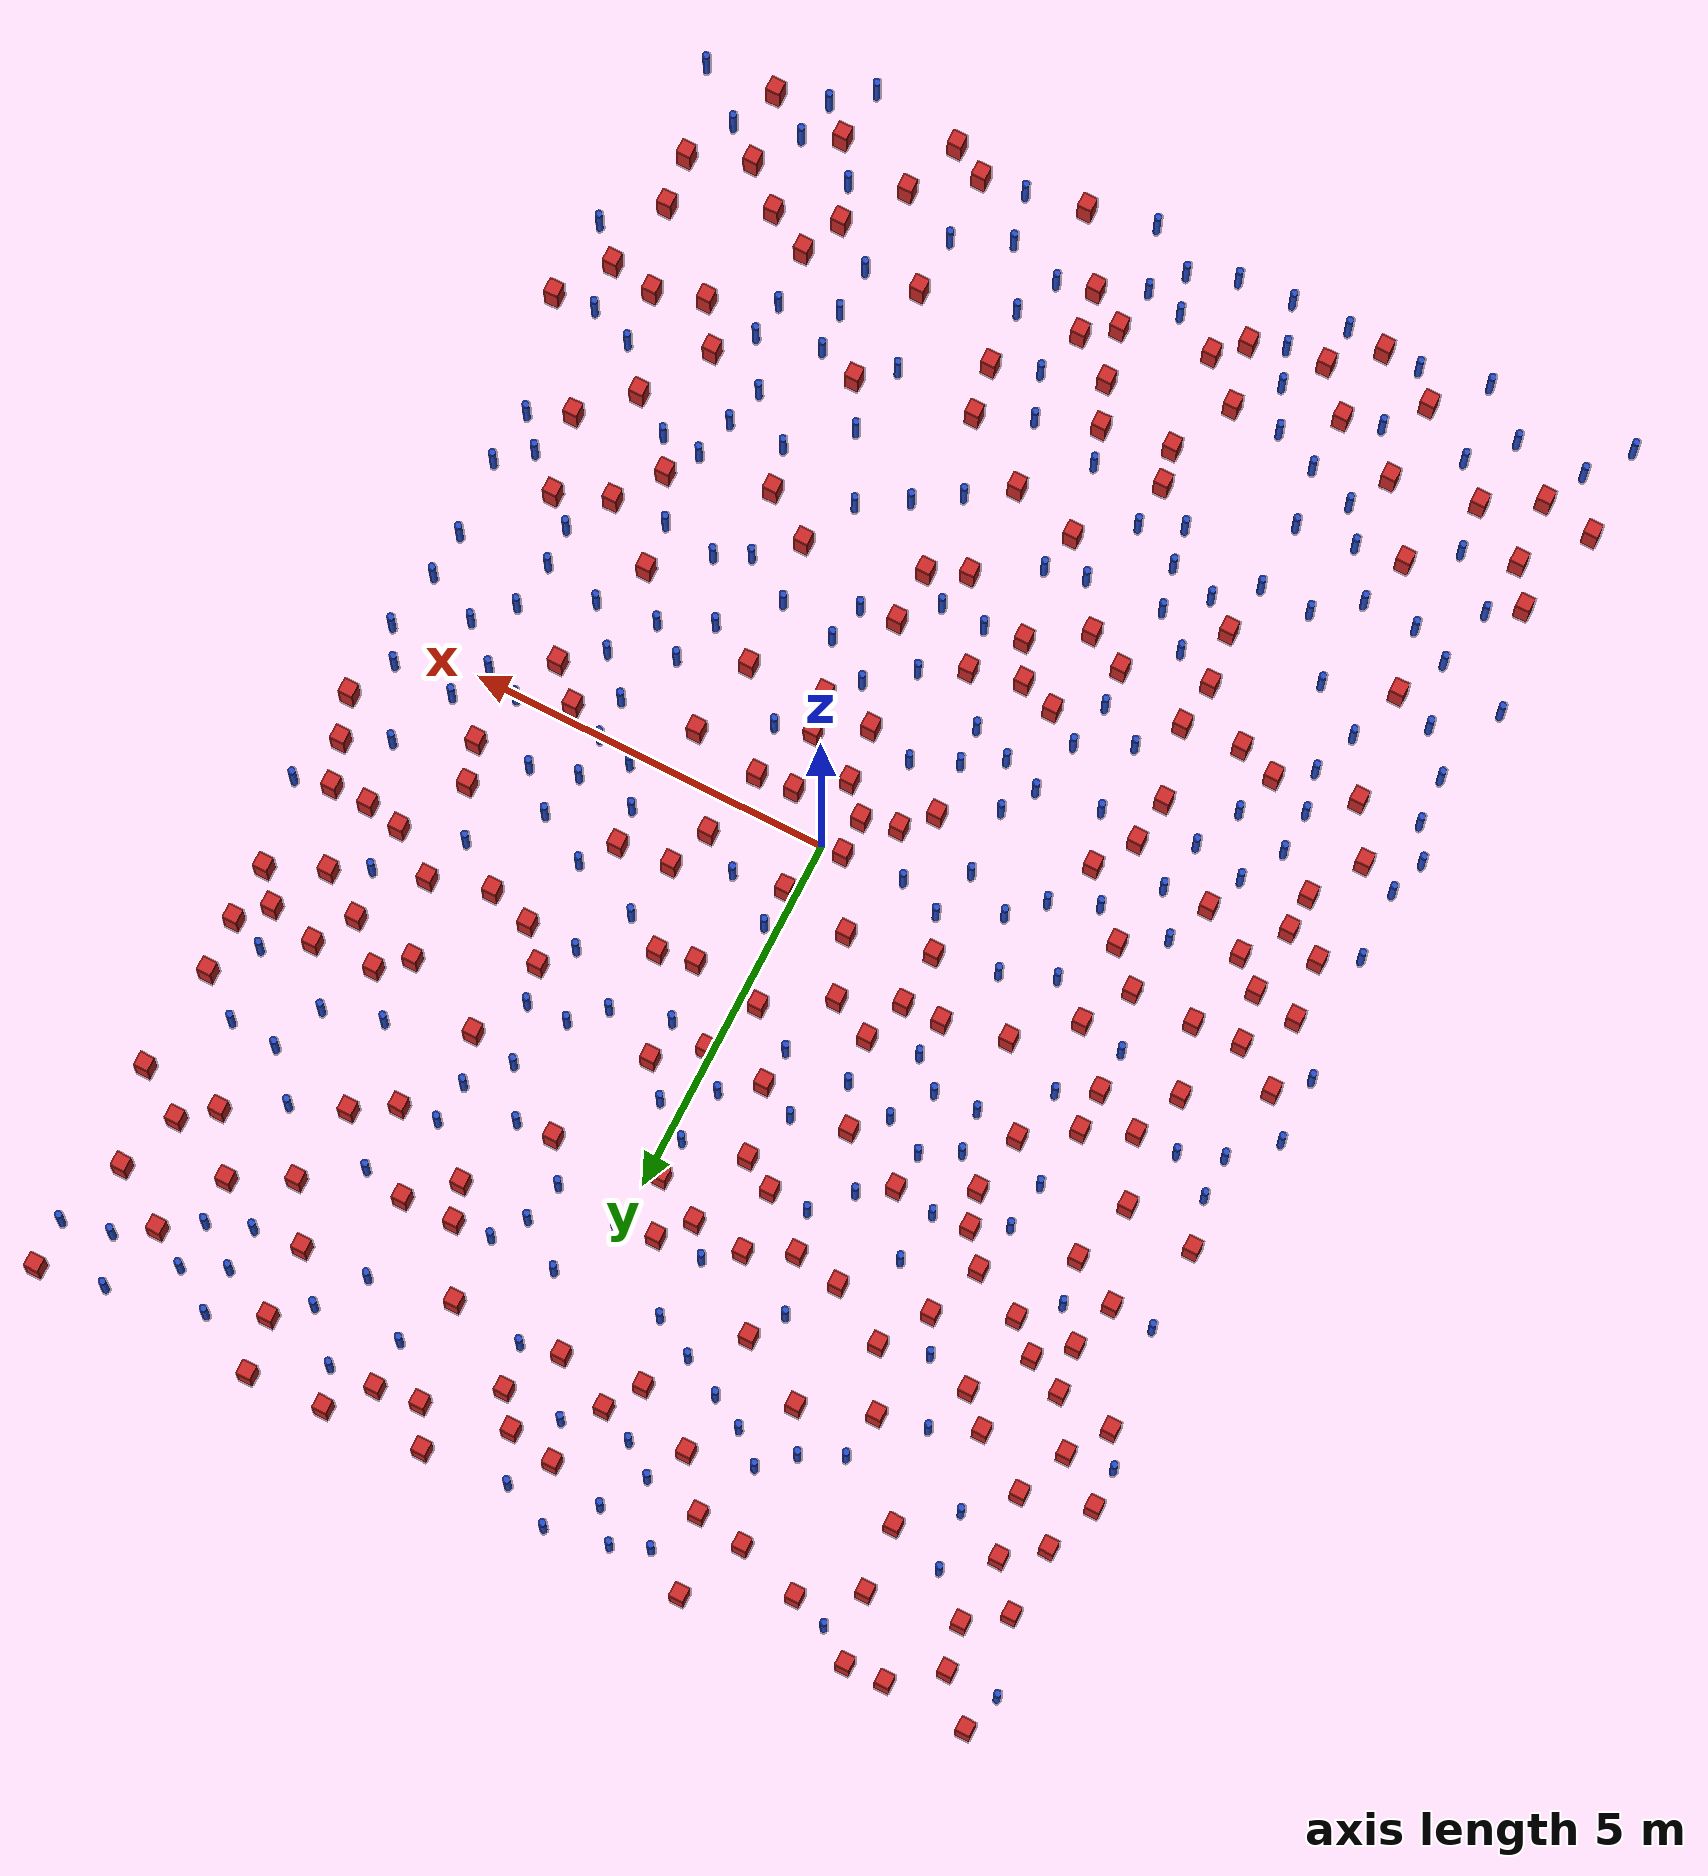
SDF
<sdf version="1.6">
  <model name="dense_11"><model name="square_post_obstacle0">
  <static>true</static>
  <pose frame="">1.59521154931 1.13567530019 8.22691968438e-08 7.2212513382e-06 -7.54495500217e-07 2.29674213826e-05</pose>
  <link name="link">
    <pose frame="">0 0 0.25 0 -0 0</pose>
    <inertial>
      <mass>100</mass>
      <inertia>
        <ixx>0.166667</ixx>
        <ixy>0</ixy>
        <ixz>0</ixz>
        <iyy>0.166667</iyy>
        <iyz>0</iyz>
        <izz>0.166667</izz>
      </inertia>
    </inertial>
    <collision name="collision">
      <geometry>
        <box>
          <size>.2 .2 .5</size>
        </box>
      </geometry>
      <max_contacts>10</max_contacts>
      <surface>
        <contact>
          <ode/>
        </contact>
        <bounce/>
        <friction>
          <torsional>
            <ode/>
          </torsional>
          <ode/>
        </friction>
      </surface>
    </collision>
    <visual name="visual">
      <geometry>
        <box>
          <size>.2 .2 .5</size>
        </box>
      </geometry>
      <material>
        <script>
          <name>Gazebo/Red</name>
          <uri>file://media/materials/scripts/gazebo.material</uri>
        </script>
      </material>
    </visual>
    <self_collide>0</self_collide>
    <kinematic>0</kinematic>
  </link>
</model>
<model name="square_post_obstacle1">
  <static>true</static>
  <pose frame="">-5.27725975503 5.88324611764 8.22691968438e-08 7.2212513382e-06 -7.54495500217e-07 2.29674213826e-05</pose>
  <link name="link">
    <pose frame="">0 0 0.25 0 -0 0</pose>
    <inertial>
      <mass>100</mass>
      <inertia>
        <ixx>0.166667</ixx>
        <ixy>0</ixy>
        <ixz>0</ixz>
        <iyy>0.166667</iyy>
        <iyz>0</iyz>
        <izz>0.166667</izz>
      </inertia>
    </inertial>
    <collision name="collision">
      <geometry>
        <box>
          <size>.2 .2 .5</size>
        </box>
      </geometry>
      <max_contacts>10</max_contacts>
      <surface>
        <contact>
          <ode/>
        </contact>
        <bounce/>
        <friction>
          <torsional>
            <ode/>
          </torsional>
          <ode/>
        </friction>
      </surface>
    </collision>
    <visual name="visual">
      <geometry>
        <box>
          <size>.2 .2 .5</size>
        </box>
      </geometry>
      <material>
        <script>
          <name>Gazebo/Red</name>
          <uri>file://media/materials/scripts/gazebo.material</uri>
        </script>
      </material>
    </visual>
    <self_collide>0</self_collide>
    <kinematic>0</kinematic>
  </link>
</model>
<model name="pole_obstacle0">
  <static>true</static>
  <pose frame="">2.64898419732 1.66031176856 2.88873142074e-08 -9.90536689395e-09 4.60219949e-07 -1.20965994953e-07</pose>
  <link name="link">
  <pose frame="">0 0 0.3 0 -0 0</pose>
    <inertial>
      <mass>1</mass>
      <inertia>
        <ixx>0.145833</ixx>
        <ixy>0</ixy>
        <ixz>0</ixz>
        <iyy>0.145833</iyy>
        <iyz>0</iyz>
        <izz>0.125</izz>
      </inertia>
    </inertial>
    <collision name="collision">
      <geometry>
        <cylinder>
          <radius>0.05</radius>
          <length>.6</length>
        </cylinder>
      </geometry>
      <max_contacts>10</max_contacts>
      <surface>
        <contact>
          <ode/>
        </contact>
        <bounce/>
        <friction>
          <torsional>
            <ode/>
          </torsional>
          <ode/>
        </friction>
      </surface>
    </collision>
    <visual name="visual">
      <geometry>
        <cylinder>
          <radius>0.05</radius>
          <length>.6</length>
        </cylinder>
      </geometry>
      <material>
        <script>
          <name>Gazebo/Blue</name>
          <uri>file://media/materials/scripts/gazebo.material</uri>
        </script>
      </material>
    </visual>
    <self_collide>0</self_collide>
    <kinematic>0</kinematic>
  </link>
</model>
<model name="square_post_obstacle2">
  <static>true</static>
  <pose frame="">5.42452816976 2.19569135165 8.22691968438e-08 7.2212513382e-06 -7.54495500217e-07 2.29674213826e-05</pose>
  <link name="link">
    <pose frame="">0 0 0.25 0 -0 0</pose>
    <inertial>
      <mass>100</mass>
      <inertia>
        <ixx>0.166667</ixx>
        <ixy>0</ixy>
        <ixz>0</ixz>
        <iyy>0.166667</iyy>
        <iyz>0</iyz>
        <izz>0.166667</izz>
      </inertia>
    </inertial>
    <collision name="collision">
      <geometry>
        <box>
          <size>.2 .2 .5</size>
        </box>
      </geometry>
      <max_contacts>10</max_contacts>
      <surface>
        <contact>
          <ode/>
        </contact>
        <bounce/>
        <friction>
          <torsional>
            <ode/>
          </torsional>
          <ode/>
        </friction>
      </surface>
    </collision>
    <visual name="visual">
      <geometry>
        <box>
          <size>.2 .2 .5</size>
        </box>
      </geometry>
      <material>
        <script>
          <name>Gazebo/Red</name>
          <uri>file://media/materials/scripts/gazebo.material</uri>
        </script>
      </material>
    </visual>
    <self_collide>0</self_collide>
    <kinematic>0</kinematic>
  </link>
</model>
<model name="pole_obstacle1">
  <static>true</static>
  <pose frame="">-3.49145345762 0.226264162207 2.88873142074e-08 -9.90536690909e-09 4.60219948964e-07 -1.2096599498e-07</pose>
  <link name="link">
  <pose frame="">0 0 0.3 0 -0 0</pose>
    <inertial>
      <mass>1</mass>
      <inertia>
        <ixx>0.145833</ixx>
        <ixy>0</ixy>
        <ixz>0</ixz>
        <iyy>0.145833</iyy>
        <iyz>0</iyz>
        <izz>0.125</izz>
      </inertia>
    </inertial>
    <collision name="collision">
      <geometry>
        <cylinder>
          <radius>0.05</radius>
          <length>.6</length>
        </cylinder>
      </geometry>
      <max_contacts>10</max_contacts>
      <surface>
        <contact>
          <ode/>
        </contact>
        <bounce/>
        <friction>
          <torsional>
            <ode/>
          </torsional>
          <ode/>
        </friction>
      </surface>
    </collision>
    <visual name="visual">
      <geometry>
        <cylinder>
          <radius>0.05</radius>
          <length>.6</length>
        </cylinder>
      </geometry>
      <material>
        <script>
          <name>Gazebo/Blue</name>
          <uri>file://media/materials/scripts/gazebo.material</uri>
        </script>
      </material>
    </visual>
    <self_collide>0</self_collide>
    <kinematic>0</kinematic>
  </link>
</model>
<model name="square_post_obstacle3">
  <static>true</static>
  <pose frame="">3.03924408986 -8.36852903713 8.22691968438e-08 7.22125133819e-06 -7.54495500217e-07 2.29674213826e-05</pose>
  <link name="link">
    <pose frame="">0 0 0.25 0 -0 0</pose>
    <inertial>
      <mass>100</mass>
      <inertia>
        <ixx>0.166667</ixx>
        <ixy>0</ixy>
        <ixz>0</ixz>
        <iyy>0.166667</iyy>
        <iyz>0</iyz>
        <izz>0.166667</izz>
      </inertia>
    </inertial>
    <collision name="collision">
      <geometry>
        <box>
          <size>.2 .2 .5</size>
        </box>
      </geometry>
      <max_contacts>10</max_contacts>
      <surface>
        <contact>
          <ode/>
        </contact>
        <bounce/>
        <friction>
          <torsional>
            <ode/>
          </torsional>
          <ode/>
        </friction>
      </surface>
    </collision>
    <visual name="visual">
      <geometry>
        <box>
          <size>.2 .2 .5</size>
        </box>
      </geometry>
      <material>
        <script>
          <name>Gazebo/Red</name>
          <uri>file://media/materials/scripts/gazebo.material</uri>
        </script>
      </material>
    </visual>
    <self_collide>0</self_collide>
    <kinematic>0</kinematic>
  </link>
</model>
<model name="pole_obstacle2">
  <static>true</static>
  <pose frame="">4.96777169325 5.56656059829 2.88873142074e-08 -9.90536690842e-09 4.60219948965e-07 -1.20965994976e-07</pose>
  <link name="link">
  <pose frame="">0 0 0.3 0 -0 0</pose>
    <inertial>
      <mass>1</mass>
      <inertia>
        <ixx>0.145833</ixx>
        <ixy>0</ixy>
        <ixz>0</ixz>
        <iyy>0.145833</iyy>
        <iyz>0</iyz>
        <izz>0.125</izz>
      </inertia>
    </inertial>
    <collision name="collision">
      <geometry>
        <cylinder>
          <radius>0.05</radius>
          <length>.6</length>
        </cylinder>
      </geometry>
      <max_contacts>10</max_contacts>
      <surface>
        <contact>
          <ode/>
        </contact>
        <bounce/>
        <friction>
          <torsional>
            <ode/>
          </torsional>
          <ode/>
        </friction>
      </surface>
    </collision>
    <visual name="visual">
      <geometry>
        <cylinder>
          <radius>0.05</radius>
          <length>.6</length>
        </cylinder>
      </geometry>
      <material>
        <script>
          <name>Gazebo/Blue</name>
          <uri>file://media/materials/scripts/gazebo.material</uri>
        </script>
      </material>
    </visual>
    <self_collide>0</self_collide>
    <kinematic>0</kinematic>
  </link>
</model>
<model name="pole_obstacle3">
  <static>true</static>
  <pose frame="">-5.21165432251 -3.73537598972 2.88873142074e-08 -9.90536690245e-09 4.6021994898e-07 -1.20965994966e-07</pose>
  <link name="link">
  <pose frame="">0 0 0.3 0 -0 0</pose>
    <inertial>
      <mass>1</mass>
      <inertia>
        <ixx>0.145833</ixx>
        <ixy>0</ixy>
        <ixz>0</ixz>
        <iyy>0.145833</iyy>
        <iyz>0</iyz>
        <izz>0.125</izz>
      </inertia>
    </inertial>
    <collision name="collision">
      <geometry>
        <cylinder>
          <radius>0.05</radius>
          <length>.6</length>
        </cylinder>
      </geometry>
      <max_contacts>10</max_contacts>
      <surface>
        <contact>
          <ode/>
        </contact>
        <bounce/>
        <friction>
          <torsional>
            <ode/>
          </torsional>
          <ode/>
        </friction>
      </surface>
    </collision>
    <visual name="visual">
      <geometry>
        <cylinder>
          <radius>0.05</radius>
          <length>.6</length>
        </cylinder>
      </geometry>
      <material>
        <script>
          <name>Gazebo/Blue</name>
          <uri>file://media/materials/scripts/gazebo.material</uri>
        </script>
      </material>
    </visual>
    <self_collide>0</self_collide>
    <kinematic>0</kinematic>
  </link>
</model>
<model name="square_post_obstacle4">
  <static>true</static>
  <pose frame="">-3.38604297422 -4.9030827757 8.22691968438e-08 7.22125133819e-06 -7.54495500217e-07 2.29674213826e-05</pose>
  <link name="link">
    <pose frame="">0 0 0.25 0 -0 0</pose>
    <inertial>
      <mass>100</mass>
      <inertia>
        <ixx>0.166667</ixx>
        <ixy>0</ixy>
        <ixz>0</ixz>
        <iyy>0.166667</iyy>
        <iyz>0</iyz>
        <izz>0.166667</izz>
      </inertia>
    </inertial>
    <collision name="collision">
      <geometry>
        <box>
          <size>.2 .2 .5</size>
        </box>
      </geometry>
      <max_contacts>10</max_contacts>
      <surface>
        <contact>
          <ode/>
        </contact>
        <bounce/>
        <friction>
          <torsional>
            <ode/>
          </torsional>
          <ode/>
        </friction>
      </surface>
    </collision>
    <visual name="visual">
      <geometry>
        <box>
          <size>.2 .2 .5</size>
        </box>
      </geometry>
      <material>
        <script>
          <name>Gazebo/Red</name>
          <uri>file://media/materials/scripts/gazebo.material</uri>
        </script>
      </material>
    </visual>
    <self_collide>0</self_collide>
    <kinematic>0</kinematic>
  </link>
</model>
<model name="square_post_obstacle5">
  <static>true</static>
  <pose frame="">-6.42843077211 -0.685245272098 8.22691968438e-08 7.2212513382e-06 -7.54495500217e-07 2.29674213826e-05</pose>
  <link name="link">
    <pose frame="">0 0 0.25 0 -0 0</pose>
    <inertial>
      <mass>100</mass>
      <inertia>
        <ixx>0.166667</ixx>
        <ixy>0</ixy>
        <ixz>0</ixz>
        <iyy>0.166667</iyy>
        <iyz>0</iyz>
        <izz>0.166667</izz>
      </inertia>
    </inertial>
    <collision name="collision">
      <geometry>
        <box>
          <size>.2 .2 .5</size>
        </box>
      </geometry>
      <max_contacts>10</max_contacts>
      <surface>
        <contact>
          <ode/>
        </contact>
        <bounce/>
        <friction>
          <torsional>
            <ode/>
          </torsional>
          <ode/>
        </friction>
      </surface>
    </collision>
    <visual name="visual">
      <geometry>
        <box>
          <size>.2 .2 .5</size>
        </box>
      </geometry>
      <material>
        <script>
          <name>Gazebo/Red</name>
          <uri>file://media/materials/scripts/gazebo.material</uri>
        </script>
      </material>
    </visual>
    <self_collide>0</self_collide>
    <kinematic>0</kinematic>
  </link>
</model>
<model name="square_post_obstacle6">
  <static>true</static>
  <pose frame="">2.86335821314 2.66554241512 8.22691968438e-08 7.2212513382e-06 -7.54495500217e-07 2.29674213826e-05</pose>
  <link name="link">
    <pose frame="">0 0 0.25 0 -0 0</pose>
    <inertial>
      <mass>100</mass>
      <inertia>
        <ixx>0.166667</ixx>
        <ixy>0</ixy>
        <ixz>0</ixz>
        <iyy>0.166667</iyy>
        <iyz>0</iyz>
        <izz>0.166667</izz>
      </inertia>
    </inertial>
    <collision name="collision">
      <geometry>
        <box>
          <size>.2 .2 .5</size>
        </box>
      </geometry>
      <max_contacts>10</max_contacts>
      <surface>
        <contact>
          <ode/>
        </contact>
        <bounce/>
        <friction>
          <torsional>
            <ode/>
          </torsional>
          <ode/>
        </friction>
      </surface>
    </collision>
    <visual name="visual">
      <geometry>
        <box>
          <size>.2 .2 .5</size>
        </box>
      </geometry>
      <material>
        <script>
          <name>Gazebo/Red</name>
          <uri>file://media/materials/scripts/gazebo.material</uri>
        </script>
      </material>
    </visual>
    <self_collide>0</self_collide>
    <kinematic>0</kinematic>
  </link>
</model>
<model name="pole_obstacle4">
  <static>true</static>
  <pose frame="">6.17533117742 -8.70427358856 2.88873142074e-08 -9.9053668967e-09 4.60219948993e-07 -1.20965994957e-07</pose>
  <link name="link">
  <pose frame="">0 0 0.3 0 -0 0</pose>
    <inertial>
      <mass>1</mass>
      <inertia>
        <ixx>0.145833</ixx>
        <ixy>0</ixy>
        <ixz>0</ixz>
        <iyy>0.145833</iyy>
        <iyz>0</iyz>
        <izz>0.125</izz>
      </inertia>
    </inertial>
    <collision name="collision">
      <geometry>
        <cylinder>
          <radius>0.05</radius>
          <length>.6</length>
        </cylinder>
      </geometry>
      <max_contacts>10</max_contacts>
      <surface>
        <contact>
          <ode/>
        </contact>
        <bounce/>
        <friction>
          <torsional>
            <ode/>
          </torsional>
          <ode/>
        </friction>
      </surface>
    </collision>
    <visual name="visual">
      <geometry>
        <cylinder>
          <radius>0.05</radius>
          <length>.6</length>
        </cylinder>
      </geometry>
      <material>
        <script>
          <name>Gazebo/Blue</name>
          <uri>file://media/materials/scripts/gazebo.material</uri>
        </script>
      </material>
    </visual>
    <self_collide>0</self_collide>
    <kinematic>0</kinematic>
  </link>
</model>
<model name="pole_obstacle5">
  <static>true</static>
  <pose frame="">-4.0076121832 -9.21498597755 2.88873142074e-08 -9.90536689695e-09 4.60219948993e-07 -1.20965994957e-07</pose>
  <link name="link">
  <pose frame="">0 0 0.3 0 -0 0</pose>
    <inertial>
      <mass>1</mass>
      <inertia>
        <ixx>0.145833</ixx>
        <ixy>0</ixy>
        <ixz>0</ixz>
        <iyy>0.145833</iyy>
        <iyz>0</iyz>
        <izz>0.125</izz>
      </inertia>
    </inertial>
    <collision name="collision">
      <geometry>
        <cylinder>
          <radius>0.05</radius>
          <length>.6</length>
        </cylinder>
      </geometry>
      <max_contacts>10</max_contacts>
      <surface>
        <contact>
          <ode/>
        </contact>
        <bounce/>
        <friction>
          <torsional>
            <ode/>
          </torsional>
          <ode/>
        </friction>
      </surface>
    </collision>
    <visual name="visual">
      <geometry>
        <cylinder>
          <radius>0.05</radius>
          <length>.6</length>
        </cylinder>
      </geometry>
      <material>
        <script>
          <name>Gazebo/Blue</name>
          <uri>file://media/materials/scripts/gazebo.material</uri>
        </script>
      </material>
    </visual>
    <self_collide>0</self_collide>
    <kinematic>0</kinematic>
  </link>
</model>
<model name="square_post_obstacle7">
  <static>true</static>
  <pose frame="">2.49568992455 3.08654107058 8.22691968438e-08 7.2212513382e-06 -7.54495500217e-07 2.29674213826e-05</pose>
  <link name="link">
    <pose frame="">0 0 0.25 0 -0 0</pose>
    <inertial>
      <mass>100</mass>
      <inertia>
        <ixx>0.166667</ixx>
        <ixy>0</ixy>
        <ixz>0</ixz>
        <iyy>0.166667</iyy>
        <iyz>0</iyz>
        <izz>0.166667</izz>
      </inertia>
    </inertial>
    <collision name="collision">
      <geometry>
        <box>
          <size>.2 .2 .5</size>
        </box>
      </geometry>
      <max_contacts>10</max_contacts>
      <surface>
        <contact>
          <ode/>
        </contact>
        <bounce/>
        <friction>
          <torsional>
            <ode/>
          </torsional>
          <ode/>
        </friction>
      </surface>
    </collision>
    <visual name="visual">
      <geometry>
        <box>
          <size>.2 .2 .5</size>
        </box>
      </geometry>
      <material>
        <script>
          <name>Gazebo/Red</name>
          <uri>file://media/materials/scripts/gazebo.material</uri>
        </script>
      </material>
    </visual>
    <self_collide>0</self_collide>
    <kinematic>0</kinematic>
  </link>
</model>
<model name="square_post_obstacle8">
  <static>true</static>
  <pose frame="">-1.00973284408 -5.13634790479 8.22691968438e-08 7.2212513382e-06 -7.54495500217e-07 2.29674213826e-05</pose>
  <link name="link">
    <pose frame="">0 0 0.25 0 -0 0</pose>
    <inertial>
      <mass>100</mass>
      <inertia>
        <ixx>0.166667</ixx>
        <ixy>0</ixy>
        <ixz>0</ixz>
        <iyy>0.166667</iyy>
        <iyz>0</iyz>
        <izz>0.166667</izz>
      </inertia>
    </inertial>
    <collision name="collision">
      <geometry>
        <box>
          <size>.2 .2 .5</size>
        </box>
      </geometry>
      <max_contacts>10</max_contacts>
      <surface>
        <contact>
          <ode/>
        </contact>
        <bounce/>
        <friction>
          <torsional>
            <ode/>
          </torsional>
          <ode/>
        </friction>
      </surface>
    </collision>
    <visual name="visual">
      <geometry>
        <box>
          <size>.2 .2 .5</size>
        </box>
      </geometry>
      <material>
        <script>
          <name>Gazebo/Red</name>
          <uri>file://media/materials/scripts/gazebo.material</uri>
        </script>
      </material>
    </visual>
    <self_collide>0</self_collide>
    <kinematic>0</kinematic>
  </link>
</model>
<model name="pole_obstacle6">
  <static>true</static>
  <pose frame="">1.37009122561 6.50611546226 2.88873142074e-08 -9.90536689852e-09 4.60219948989e-07 -1.2096599496e-07</pose>
  <link name="link">
  <pose frame="">0 0 0.3 0 -0 0</pose>
    <inertial>
      <mass>1</mass>
      <inertia>
        <ixx>0.145833</ixx>
        <ixy>0</ixy>
        <ixz>0</ixz>
        <iyy>0.145833</iyy>
        <iyz>0</iyz>
        <izz>0.125</izz>
      </inertia>
    </inertial>
    <collision name="collision">
      <geometry>
        <cylinder>
          <radius>0.05</radius>
          <length>.6</length>
        </cylinder>
      </geometry>
      <max_contacts>10</max_contacts>
      <surface>
        <contact>
          <ode/>
        </contact>
        <bounce/>
        <friction>
          <torsional>
            <ode/>
          </torsional>
          <ode/>
        </friction>
      </surface>
    </collision>
    <visual name="visual">
      <geometry>
        <cylinder>
          <radius>0.05</radius>
          <length>.6</length>
        </cylinder>
      </geometry>
      <material>
        <script>
          <name>Gazebo/Blue</name>
          <uri>file://media/materials/scripts/gazebo.material</uri>
        </script>
      </material>
    </visual>
    <self_collide>0</self_collide>
    <kinematic>0</kinematic>
  </link>
</model>
<model name="pole_obstacle7">
  <static>true</static>
  <pose frame="">1.68926775952 -4.21490488597 2.88873142074e-08 -9.90536689852e-09 4.60219948989e-07 -1.2096599496e-07</pose>
  <link name="link">
  <pose frame="">0 0 0.3 0 -0 0</pose>
    <inertial>
      <mass>1</mass>
      <inertia>
        <ixx>0.145833</ixx>
        <ixy>0</ixy>
        <ixz>0</ixz>
        <iyy>0.145833</iyy>
        <iyz>0</iyz>
        <izz>0.125</izz>
      </inertia>
    </inertial>
    <collision name="collision">
      <geometry>
        <cylinder>
          <radius>0.05</radius>
          <length>.6</length>
        </cylinder>
      </geometry>
      <max_contacts>10</max_contacts>
      <surface>
        <contact>
          <ode/>
        </contact>
        <bounce/>
        <friction>
          <torsional>
            <ode/>
          </torsional>
          <ode/>
        </friction>
      </surface>
    </collision>
    <visual name="visual">
      <geometry>
        <cylinder>
          <radius>0.05</radius>
          <length>.6</length>
        </cylinder>
      </geometry>
      <material>
        <script>
          <name>Gazebo/Blue</name>
          <uri>file://media/materials/scripts/gazebo.material</uri>
        </script>
      </material>
    </visual>
    <self_collide>0</self_collide>
    <kinematic>0</kinematic>
  </link>
</model>
<model name="square_post_obstacle9">
  <static>true</static>
  <pose frame="">-1.50824096841 -8.1657535437 8.22691968438e-08 7.22125133819e-06 -7.54495500217e-07 2.29674213826e-05</pose>
  <link name="link">
    <pose frame="">0 0 0.25 0 -0 0</pose>
    <inertial>
      <mass>100</mass>
      <inertia>
        <ixx>0.166667</ixx>
        <ixy>0</ixy>
        <ixz>0</ixz>
        <iyy>0.166667</iyy>
        <iyz>0</iyz>
        <izz>0.166667</izz>
      </inertia>
    </inertial>
    <collision name="collision">
      <geometry>
        <box>
          <size>.2 .2 .5</size>
        </box>
      </geometry>
      <max_contacts>10</max_contacts>
      <surface>
        <contact>
          <ode/>
        </contact>
        <bounce/>
        <friction>
          <torsional>
            <ode/>
          </torsional>
          <ode/>
        </friction>
      </surface>
    </collision>
    <visual name="visual">
      <geometry>
        <box>
          <size>.2 .2 .5</size>
        </box>
      </geometry>
      <material>
        <script>
          <name>Gazebo/Red</name>
          <uri>file://media/materials/scripts/gazebo.material</uri>
        </script>
      </material>
    </visual>
    <self_collide>0</self_collide>
    <kinematic>0</kinematic>
  </link>
</model>
<model name="square_post_obstacle10">
  <static>true</static>
  <pose frame="">-5.61227143454 2.45964329711 8.22691968438e-08 7.2212513382e-06 -7.54495500217e-07 2.29674213826e-05</pose>
  <link name="link">
    <pose frame="">0 0 0.25 0 -0 0</pose>
    <inertial>
      <mass>100</mass>
      <inertia>
        <ixx>0.166667</ixx>
        <ixy>0</ixy>
        <ixz>0</ixz>
        <iyy>0.166667</iyy>
        <iyz>0</iyz>
        <izz>0.166667</izz>
      </inertia>
    </inertial>
    <collision name="collision">
      <geometry>
        <box>
          <size>.2 .2 .5</size>
        </box>
      </geometry>
      <max_contacts>10</max_contacts>
      <surface>
        <contact>
          <ode/>
        </contact>
        <bounce/>
        <friction>
          <torsional>
            <ode/>
          </torsional>
          <ode/>
        </friction>
      </surface>
    </collision>
    <visual name="visual">
      <geometry>
        <box>
          <size>.2 .2 .5</size>
        </box>
      </geometry>
      <material>
        <script>
          <name>Gazebo/Red</name>
          <uri>file://media/materials/scripts/gazebo.material</uri>
        </script>
      </material>
    </visual>
    <self_collide>0</self_collide>
    <kinematic>0</kinematic>
  </link>
</model>
<model name="square_post_obstacle11">
  <static>true</static>
  <pose frame="">-4.78634820222 -1.50564330766 8.22691968438e-08 7.2212513382e-06 -7.54495500217e-07 2.29674213826e-05</pose>
  <link name="link">
    <pose frame="">0 0 0.25 0 -0 0</pose>
    <inertial>
      <mass>100</mass>
      <inertia>
        <ixx>0.166667</ixx>
        <ixy>0</ixy>
        <ixz>0</ixz>
        <iyy>0.166667</iyy>
        <iyz>0</iyz>
        <izz>0.166667</izz>
      </inertia>
    </inertial>
    <collision name="collision">
      <geometry>
        <box>
          <size>.2 .2 .5</size>
        </box>
      </geometry>
      <max_contacts>10</max_contacts>
      <surface>
        <contact>
          <ode/>
        </contact>
        <bounce/>
        <friction>
          <torsional>
            <ode/>
          </torsional>
          <ode/>
        </friction>
      </surface>
    </collision>
    <visual name="visual">
      <geometry>
        <box>
          <size>.2 .2 .5</size>
        </box>
      </geometry>
      <material>
        <script>
          <name>Gazebo/Red</name>
          <uri>file://media/materials/scripts/gazebo.material</uri>
        </script>
      </material>
    </visual>
    <self_collide>0</self_collide>
    <kinematic>0</kinematic>
  </link>
</model>
<model name="square_post_obstacle12">
  <static>true</static>
  <pose frame="">-1.22124211983 7.31243710689 8.22691968438e-08 7.2212513382e-06 -7.54495500217e-07 2.29674213826e-05</pose>
  <link name="link">
    <pose frame="">0 0 0.25 0 -0 0</pose>
    <inertial>
      <mass>100</mass>
      <inertia>
        <ixx>0.166667</ixx>
        <ixy>0</ixy>
        <ixz>0</ixz>
        <iyy>0.166667</iyy>
        <iyz>0</iyz>
        <izz>0.166667</izz>
      </inertia>
    </inertial>
    <collision name="collision">
      <geometry>
        <box>
          <size>.2 .2 .5</size>
        </box>
      </geometry>
      <max_contacts>10</max_contacts>
      <surface>
        <contact>
          <ode/>
        </contact>
        <bounce/>
        <friction>
          <torsional>
            <ode/>
          </torsional>
          <ode/>
        </friction>
      </surface>
    </collision>
    <visual name="visual">
      <geometry>
        <box>
          <size>.2 .2 .5</size>
        </box>
      </geometry>
      <material>
        <script>
          <name>Gazebo/Red</name>
          <uri>file://media/materials/scripts/gazebo.material</uri>
        </script>
      </material>
    </visual>
    <self_collide>0</self_collide>
    <kinematic>0</kinematic>
  </link>
</model>
<model name="square_post_obstacle13">
  <static>true</static>
  <pose frame="">-5.09367767588 9.29673221735 8.22691968438e-08 7.22125133819e-06 -7.54495500217e-07 2.29674213826e-05</pose>
  <link name="link">
    <pose frame="">0 0 0.25 0 -0 0</pose>
    <inertial>
      <mass>100</mass>
      <inertia>
        <ixx>0.166667</ixx>
        <ixy>0</ixy>
        <ixz>0</ixz>
        <iyy>0.166667</iyy>
        <iyz>0</iyz>
        <izz>0.166667</izz>
      </inertia>
    </inertial>
    <collision name="collision">
      <geometry>
        <box>
          <size>.2 .2 .5</size>
        </box>
      </geometry>
      <max_contacts>10</max_contacts>
      <surface>
        <contact>
          <ode/>
        </contact>
        <bounce/>
        <friction>
          <torsional>
            <ode/>
          </torsional>
          <ode/>
        </friction>
      </surface>
    </collision>
    <visual name="visual">
      <geometry>
        <box>
          <size>.2 .2 .5</size>
        </box>
      </geometry>
      <material>
        <script>
          <name>Gazebo/Red</name>
          <uri>file://media/materials/scripts/gazebo.material</uri>
        </script>
      </material>
    </visual>
    <self_collide>0</self_collide>
    <kinematic>0</kinematic>
  </link>
</model>
<model name="pole_obstacle8">
  <static>true</static>
  <pose frame="">-6.98964618681 -5.51536909973 2.88873142074e-08 -9.90536690842e-09 4.60219948965e-07 -1.20965994976e-07</pose>
  <link name="link">
  <pose frame="">0 0 0.3 0 -0 0</pose>
    <inertial>
      <mass>1</mass>
      <inertia>
        <ixx>0.145833</ixx>
        <ixy>0</ixy>
        <ixz>0</ixz>
        <iyy>0.145833</iyy>
        <iyz>0</iyz>
        <izz>0.125</izz>
      </inertia>
    </inertial>
    <collision name="collision">
      <geometry>
        <cylinder>
          <radius>0.05</radius>
          <length>.6</length>
        </cylinder>
      </geometry>
      <max_contacts>10</max_contacts>
      <surface>
        <contact>
          <ode/>
        </contact>
        <bounce/>
        <friction>
          <torsional>
            <ode/>
          </torsional>
          <ode/>
        </friction>
      </surface>
    </collision>
    <visual name="visual">
      <geometry>
        <cylinder>
          <radius>0.05</radius>
          <length>.6</length>
        </cylinder>
      </geometry>
      <material>
        <script>
          <name>Gazebo/Blue</name>
          <uri>file://media/materials/scripts/gazebo.material</uri>
        </script>
      </material>
    </visual>
    <self_collide>0</self_collide>
    <kinematic>0</kinematic>
  </link>
</model>
<model name="square_post_obstacle14">
  <static>true</static>
  <pose frame="">-5.2877736811 1.57196112984 8.22691968438e-08 7.2212513382e-06 -7.54495500217e-07 2.29674213826e-05</pose>
  <link name="link">
    <pose frame="">0 0 0.25 0 -0 0</pose>
    <inertial>
      <mass>100</mass>
      <inertia>
        <ixx>0.166667</ixx>
        <ixy>0</ixy>
        <ixz>0</ixz>
        <iyy>0.166667</iyy>
        <iyz>0</iyz>
        <izz>0.166667</izz>
      </inertia>
    </inertial>
    <collision name="collision">
      <geometry>
        <box>
          <size>.2 .2 .5</size>
        </box>
      </geometry>
      <max_contacts>10</max_contacts>
      <surface>
        <contact>
          <ode/>
        </contact>
        <bounce/>
        <friction>
          <torsional>
            <ode/>
          </torsional>
          <ode/>
        </friction>
      </surface>
    </collision>
    <visual name="visual">
      <geometry>
        <box>
          <size>.2 .2 .5</size>
        </box>
      </geometry>
      <material>
        <script>
          <name>Gazebo/Red</name>
          <uri>file://media/materials/scripts/gazebo.material</uri>
        </script>
      </material>
    </visual>
    <self_collide>0</self_collide>
    <kinematic>0</kinematic>
  </link>
</model>
<model name="square_post_obstacle15">
  <static>true</static>
  <pose frame="">0.062376917893 -0.889046045588 8.22691968438e-08 7.2212513382e-06 -7.54495500217e-07 2.29674213826e-05</pose>
  <link name="link">
    <pose frame="">0 0 0.25 0 -0 0</pose>
    <inertial>
      <mass>100</mass>
      <inertia>
        <ixx>0.166667</ixx>
        <ixy>0</ixy>
        <ixz>0</ixz>
        <iyy>0.166667</iyy>
        <iyz>0</iyz>
        <izz>0.166667</izz>
      </inertia>
    </inertial>
    <collision name="collision">
      <geometry>
        <box>
          <size>.2 .2 .5</size>
        </box>
      </geometry>
      <max_contacts>10</max_contacts>
      <surface>
        <contact>
          <ode/>
        </contact>
        <bounce/>
        <friction>
          <torsional>
            <ode/>
          </torsional>
          <ode/>
        </friction>
      </surface>
    </collision>
    <visual name="visual">
      <geometry>
        <box>
          <size>.2 .2 .5</size>
        </box>
      </geometry>
      <material>
        <script>
          <name>Gazebo/Red</name>
          <uri>file://media/materials/scripts/gazebo.material</uri>
        </script>
      </material>
    </visual>
    <self_collide>0</self_collide>
    <kinematic>0</kinematic>
  </link>
</model>
<model name="square_post_obstacle16">
  <static>true</static>
  <pose frame="">3.91685369579 6.9639876529 8.22691968438e-08 7.2212513382e-06 -7.54495500217e-07 2.29674213826e-05</pose>
  <link name="link">
    <pose frame="">0 0 0.25 0 -0 0</pose>
    <inertial>
      <mass>100</mass>
      <inertia>
        <ixx>0.166667</ixx>
        <ixy>0</ixy>
        <ixz>0</ixz>
        <iyy>0.166667</iyy>
        <iyz>0</iyz>
        <izz>0.166667</izz>
      </inertia>
    </inertial>
    <collision name="collision">
      <geometry>
        <box>
          <size>.2 .2 .5</size>
        </box>
      </geometry>
      <max_contacts>10</max_contacts>
      <surface>
        <contact>
          <ode/>
        </contact>
        <bounce/>
        <friction>
          <torsional>
            <ode/>
          </torsional>
          <ode/>
        </friction>
      </surface>
    </collision>
    <visual name="visual">
      <geometry>
        <box>
          <size>.2 .2 .5</size>
        </box>
      </geometry>
      <material>
        <script>
          <name>Gazebo/Red</name>
          <uri>file://media/materials/scripts/gazebo.material</uri>
        </script>
      </material>
    </visual>
    <self_collide>0</self_collide>
    <kinematic>0</kinematic>
  </link>
</model>
<model name="pole_obstacle9">
  <static>true</static>
  <pose frame="">-5.34426022218 -3.18087309578 2.88873142074e-08 -9.90536690245e-09 4.6021994898e-07 -1.20965994966e-07</pose>
  <link name="link">
  <pose frame="">0 0 0.3 0 -0 0</pose>
    <inertial>
      <mass>1</mass>
      <inertia>
        <ixx>0.145833</ixx>
        <ixy>0</ixy>
        <ixz>0</ixz>
        <iyy>0.145833</iyy>
        <iyz>0</iyz>
        <izz>0.125</izz>
      </inertia>
    </inertial>
    <collision name="collision">
      <geometry>
        <cylinder>
          <radius>0.05</radius>
          <length>.6</length>
        </cylinder>
      </geometry>
      <max_contacts>10</max_contacts>
      <surface>
        <contact>
          <ode/>
        </contact>
        <bounce/>
        <friction>
          <torsional>
            <ode/>
          </torsional>
          <ode/>
        </friction>
      </surface>
    </collision>
    <visual name="visual">
      <geometry>
        <cylinder>
          <radius>0.05</radius>
          <length>.6</length>
        </cylinder>
      </geometry>
      <material>
        <script>
          <name>Gazebo/Blue</name>
          <uri>file://media/materials/scripts/gazebo.material</uri>
        </script>
      </material>
    </visual>
    <self_collide>0</self_collide>
    <kinematic>0</kinematic>
  </link>
</model>
<model name="square_post_obstacle17">
  <static>true</static>
  <pose frame="">-3.26479385472 8.55258115852 8.22691968438e-08 7.2212513382e-06 -7.54495500217e-07 2.29674213826e-05</pose>
  <link name="link">
    <pose frame="">0 0 0.25 0 -0 0</pose>
    <inertial>
      <mass>100</mass>
      <inertia>
        <ixx>0.166667</ixx>
        <ixy>0</ixy>
        <ixz>0</ixz>
        <iyy>0.166667</iyy>
        <iyz>0</iyz>
        <izz>0.166667</izz>
      </inertia>
    </inertial>
    <collision name="collision">
      <geometry>
        <box>
          <size>.2 .2 .5</size>
        </box>
      </geometry>
      <max_contacts>10</max_contacts>
      <surface>
        <contact>
          <ode/>
        </contact>
        <bounce/>
        <friction>
          <torsional>
            <ode/>
          </torsional>
          <ode/>
        </friction>
      </surface>
    </collision>
    <visual name="visual">
      <geometry>
        <box>
          <size>.2 .2 .5</size>
        </box>
      </geometry>
      <material>
        <script>
          <name>Gazebo/Red</name>
          <uri>file://media/materials/scripts/gazebo.material</uri>
        </script>
      </material>
    </visual>
    <self_collide>0</self_collide>
    <kinematic>0</kinematic>
  </link>
</model>
<model name="square_post_obstacle18">
  <static>true</static>
  <pose frame="">-6.2647670052 8.79094868232 8.22691968438e-08 7.22125133819e-06 -7.54495500217e-07 2.29674213826e-05</pose>
  <link name="link">
    <pose frame="">0 0 0.25 0 -0 0</pose>
    <inertial>
      <mass>100</mass>
      <inertia>
        <ixx>0.166667</ixx>
        <ixy>0</ixy>
        <ixz>0</ixz>
        <iyy>0.166667</iyy>
        <iyz>0</iyz>
        <izz>0.166667</izz>
      </inertia>
    </inertial>
    <collision name="collision">
      <geometry>
        <box>
          <size>.2 .2 .5</size>
        </box>
      </geometry>
      <max_contacts>10</max_contacts>
      <surface>
        <contact>
          <ode/>
        </contact>
        <bounce/>
        <friction>
          <torsional>
            <ode/>
          </torsional>
          <ode/>
        </friction>
      </surface>
    </collision>
    <visual name="visual">
      <geometry>
        <box>
          <size>.2 .2 .5</size>
        </box>
      </geometry>
      <material>
        <script>
          <name>Gazebo/Red</name>
          <uri>file://media/materials/scripts/gazebo.material</uri>
        </script>
      </material>
    </visual>
    <self_collide>0</self_collide>
    <kinematic>0</kinematic>
  </link>
</model>
<model name="pole_obstacle10">
  <static>true</static>
  <pose frame="">-4.7581580819 -4.81862895062 2.88873142074e-08 -9.90536690842e-09 4.60219948965e-07 -1.20965994976e-07</pose>
  <link name="link">
  <pose frame="">0 0 0.3 0 -0 0</pose>
    <inertial>
      <mass>1</mass>
      <inertia>
        <ixx>0.145833</ixx>
        <ixy>0</ixy>
        <ixz>0</ixz>
        <iyy>0.145833</iyy>
        <iyz>0</iyz>
        <izz>0.125</izz>
      </inertia>
    </inertial>
    <collision name="collision">
      <geometry>
        <cylinder>
          <radius>0.05</radius>
          <length>.6</length>
        </cylinder>
      </geometry>
      <max_contacts>10</max_contacts>
      <surface>
        <contact>
          <ode/>
        </contact>
        <bounce/>
        <friction>
          <torsional>
            <ode/>
          </torsional>
          <ode/>
        </friction>
      </surface>
    </collision>
    <visual name="visual">
      <geometry>
        <cylinder>
          <radius>0.05</radius>
          <length>.6</length>
        </cylinder>
      </geometry>
      <material>
        <script>
          <name>Gazebo/Blue</name>
          <uri>file://media/materials/scripts/gazebo.material</uri>
        </script>
      </material>
    </visual>
    <self_collide>0</self_collide>
    <kinematic>0</kinematic>
  </link>
</model>
<model name="square_post_obstacle19">
  <static>true</static>
  <pose frame="">-2.11735339929 6.15063905305 8.22691968438e-08 7.2212513382e-06 -7.54495500217e-07 2.29674213826e-05</pose>
  <link name="link">
    <pose frame="">0 0 0.25 0 -0 0</pose>
    <inertial>
      <mass>100</mass>
      <inertia>
        <ixx>0.166667</ixx>
        <ixy>0</ixy>
        <ixz>0</ixz>
        <iyy>0.166667</iyy>
        <iyz>0</iyz>
        <izz>0.166667</izz>
      </inertia>
    </inertial>
    <collision name="collision">
      <geometry>
        <box>
          <size>.2 .2 .5</size>
        </box>
      </geometry>
      <max_contacts>10</max_contacts>
      <surface>
        <contact>
          <ode/>
        </contact>
        <bounce/>
        <friction>
          <torsional>
            <ode/>
          </torsional>
          <ode/>
        </friction>
      </surface>
    </collision>
    <visual name="visual">
      <geometry>
        <box>
          <size>.2 .2 .5</size>
        </box>
      </geometry>
      <material>
        <script>
          <name>Gazebo/Red</name>
          <uri>file://media/materials/scripts/gazebo.material</uri>
        </script>
      </material>
    </visual>
    <self_collide>0</self_collide>
    <kinematic>0</kinematic>
  </link>
</model>
<model name="pole_obstacle11">
  <static>true</static>
  <pose frame="">-5.08012012069 -8.36202532371 2.88873142074e-08 -9.9053668967e-09 4.60219948993e-07 -1.20965994957e-07</pose>
  <link name="link">
  <pose frame="">0 0 0.3 0 -0 0</pose>
    <inertial>
      <mass>1</mass>
      <inertia>
        <ixx>0.145833</ixx>
        <ixy>0</ixy>
        <ixz>0</ixz>
        <iyy>0.145833</iyy>
        <iyz>0</iyz>
        <izz>0.125</izz>
      </inertia>
    </inertial>
    <collision name="collision">
      <geometry>
        <cylinder>
          <radius>0.05</radius>
          <length>.6</length>
        </cylinder>
      </geometry>
      <max_contacts>10</max_contacts>
      <surface>
        <contact>
          <ode/>
        </contact>
        <bounce/>
        <friction>
          <torsional>
            <ode/>
          </torsional>
          <ode/>
        </friction>
      </surface>
    </collision>
    <visual name="visual">
      <geometry>
        <cylinder>
          <radius>0.05</radius>
          <length>.6</length>
        </cylinder>
      </geometry>
      <material>
        <script>
          <name>Gazebo/Blue</name>
          <uri>file://media/materials/scripts/gazebo.material</uri>
        </script>
      </material>
    </visual>
    <self_collide>0</self_collide>
    <kinematic>0</kinematic>
  </link>
</model>
<model name="square_post_obstacle20">
  <static>true</static>
  <pose frame="">-5.6932536082 -5.16046962616 8.22691968438e-08 7.22125133819e-06 -7.54495500217e-07 2.29674213826e-05</pose>
  <link name="link">
    <pose frame="">0 0 0.25 0 -0 0</pose>
    <inertial>
      <mass>100</mass>
      <inertia>
        <ixx>0.166667</ixx>
        <ixy>0</ixy>
        <ixz>0</ixz>
        <iyy>0.166667</iyy>
        <iyz>0</iyz>
        <izz>0.166667</izz>
      </inertia>
    </inertial>
    <collision name="collision">
      <geometry>
        <box>
          <size>.2 .2 .5</size>
        </box>
      </geometry>
      <max_contacts>10</max_contacts>
      <surface>
        <contact>
          <ode/>
        </contact>
        <bounce/>
        <friction>
          <torsional>
            <ode/>
          </torsional>
          <ode/>
        </friction>
      </surface>
    </collision>
    <visual name="visual">
      <geometry>
        <box>
          <size>.2 .2 .5</size>
        </box>
      </geometry>
      <material>
        <script>
          <name>Gazebo/Red</name>
          <uri>file://media/materials/scripts/gazebo.material</uri>
        </script>
      </material>
    </visual>
    <self_collide>0</self_collide>
    <kinematic>0</kinematic>
  </link>
</model>
<model name="pole_obstacle12">
  <static>true</static>
  <pose frame="">3.62660769973 -0.998927307068 2.88873142074e-08 -9.90536689217e-09 4.60219949004e-07 -1.20965994953e-07</pose>
  <link name="link">
  <pose frame="">0 0 0.3 0 -0 0</pose>
    <inertial>
      <mass>1</mass>
      <inertia>
        <ixx>0.145833</ixx>
        <ixy>0</ixy>
        <ixz>0</ixz>
        <iyy>0.145833</iyy>
        <iyz>0</iyz>
        <izz>0.125</izz>
      </inertia>
    </inertial>
    <collision name="collision">
      <geometry>
        <cylinder>
          <radius>0.05</radius>
          <length>.6</length>
        </cylinder>
      </geometry>
      <max_contacts>10</max_contacts>
      <surface>
        <contact>
          <ode/>
        </contact>
        <bounce/>
        <friction>
          <torsional>
            <ode/>
          </torsional>
          <ode/>
        </friction>
      </surface>
    </collision>
    <visual name="visual">
      <geometry>
        <cylinder>
          <radius>0.05</radius>
          <length>.6</length>
        </cylinder>
      </geometry>
      <material>
        <script>
          <name>Gazebo/Blue</name>
          <uri>file://media/materials/scripts/gazebo.material</uri>
        </script>
      </material>
    </visual>
    <self_collide>0</self_collide>
    <kinematic>0</kinematic>
  </link>
</model>
<model name="square_post_obstacle21">
  <static>true</static>
  <pose frame="">-3.65117823529 -2.49307799827 8.22691968438e-08 7.2212513382e-06 -7.54495500217e-07 2.29674213826e-05</pose>
  <link name="link">
    <pose frame="">0 0 0.25 0 -0 0</pose>
    <inertial>
      <mass>100</mass>
      <inertia>
        <ixx>0.166667</ixx>
        <ixy>0</ixy>
        <ixz>0</ixz>
        <iyy>0.166667</iyy>
        <iyz>0</iyz>
        <izz>0.166667</izz>
      </inertia>
    </inertial>
    <collision name="collision">
      <geometry>
        <box>
          <size>.2 .2 .5</size>
        </box>
      </geometry>
      <max_contacts>10</max_contacts>
      <surface>
        <contact>
          <ode/>
        </contact>
        <bounce/>
        <friction>
          <torsional>
            <ode/>
          </torsional>
          <ode/>
        </friction>
      </surface>
    </collision>
    <visual name="visual">
      <geometry>
        <box>
          <size>.2 .2 .5</size>
        </box>
      </geometry>
      <material>
        <script>
          <name>Gazebo/Red</name>
          <uri>file://media/materials/scripts/gazebo.material</uri>
        </script>
      </material>
    </visual>
    <self_collide>0</self_collide>
    <kinematic>0</kinematic>
  </link>
</model>
<model name="pole_obstacle13">
  <static>true</static>
  <pose frame="">-3.37699610035 4.40599011899 2.88873142074e-08 -9.90536689859e-09 4.60219948989e-07 -1.20965994961e-07</pose>
  <link name="link">
  <pose frame="">0 0 0.3 0 -0 0</pose>
    <inertial>
      <mass>1</mass>
      <inertia>
        <ixx>0.145833</ixx>
        <ixy>0</ixy>
        <ixz>0</ixz>
        <iyy>0.145833</iyy>
        <iyz>0</iyz>
        <izz>0.125</izz>
      </inertia>
    </inertial>
    <collision name="collision">
      <geometry>
        <cylinder>
          <radius>0.05</radius>
          <length>.6</length>
        </cylinder>
      </geometry>
      <max_contacts>10</max_contacts>
      <surface>
        <contact>
          <ode/>
        </contact>
        <bounce/>
        <friction>
          <torsional>
            <ode/>
          </torsional>
          <ode/>
        </friction>
      </surface>
    </collision>
    <visual name="visual">
      <geometry>
        <cylinder>
          <radius>0.05</radius>
          <length>.6</length>
        </cylinder>
      </geometry>
      <material>
        <script>
          <name>Gazebo/Blue</name>
          <uri>file://media/materials/scripts/gazebo.material</uri>
        </script>
      </material>
    </visual>
    <self_collide>0</self_collide>
    <kinematic>0</kinematic>
  </link>
</model>
<model name="square_post_obstacle22">
  <static>true</static>
  <pose frame="">3.87121906777 -7.00000814342 8.22691968438e-08 7.2212513382e-06 -7.54495500217e-07 2.29674213826e-05</pose>
  <link name="link">
    <pose frame="">0 0 0.25 0 -0 0</pose>
    <inertial>
      <mass>100</mass>
      <inertia>
        <ixx>0.166667</ixx>
        <ixy>0</ixy>
        <ixz>0</ixz>
        <iyy>0.166667</iyy>
        <iyz>0</iyz>
        <izz>0.166667</izz>
      </inertia>
    </inertial>
    <collision name="collision">
      <geometry>
        <box>
          <size>.2 .2 .5</size>
        </box>
      </geometry>
      <max_contacts>10</max_contacts>
      <surface>
        <contact>
          <ode/>
        </contact>
        <bounce/>
        <friction>
          <torsional>
            <ode/>
          </torsional>
          <ode/>
        </friction>
      </surface>
    </collision>
    <visual name="visual">
      <geometry>
        <box>
          <size>.2 .2 .5</size>
        </box>
      </geometry>
      <material>
        <script>
          <name>Gazebo/Red</name>
          <uri>file://media/materials/scripts/gazebo.material</uri>
        </script>
      </material>
    </visual>
    <self_collide>0</self_collide>
    <kinematic>0</kinematic>
  </link>
</model>
<model name="pole_obstacle14">
  <static>true</static>
  <pose frame="">-4.51162540025 2.73058737092 2.88873142074e-08 -9.90536690245e-09 4.6021994898e-07 -1.20965994966e-07</pose>
  <link name="link">
  <pose frame="">0 0 0.3 0 -0 0</pose>
    <inertial>
      <mass>1</mass>
      <inertia>
        <ixx>0.145833</ixx>
        <ixy>0</ixy>
        <ixz>0</ixz>
        <iyy>0.145833</iyy>
        <iyz>0</iyz>
        <izz>0.125</izz>
      </inertia>
    </inertial>
    <collision name="collision">
      <geometry>
        <cylinder>
          <radius>0.05</radius>
          <length>.6</length>
        </cylinder>
      </geometry>
      <max_contacts>10</max_contacts>
      <surface>
        <contact>
          <ode/>
        </contact>
        <bounce/>
        <friction>
          <torsional>
            <ode/>
          </torsional>
          <ode/>
        </friction>
      </surface>
    </collision>
    <visual name="visual">
      <geometry>
        <cylinder>
          <radius>0.05</radius>
          <length>.6</length>
        </cylinder>
      </geometry>
      <material>
        <script>
          <name>Gazebo/Blue</name>
          <uri>file://media/materials/scripts/gazebo.material</uri>
        </script>
      </material>
    </visual>
    <self_collide>0</self_collide>
    <kinematic>0</kinematic>
  </link>
</model>
<model name="pole_obstacle15">
  <static>true</static>
  <pose frame="">-2.95555220369 -4.37389541297 2.88873142074e-08 -9.90536689859e-09 4.60219948989e-07 -1.20965994961e-07</pose>
  <link name="link">
  <pose frame="">0 0 0.3 0 -0 0</pose>
    <inertial>
      <mass>1</mass>
      <inertia>
        <ixx>0.145833</ixx>
        <ixy>0</ixy>
        <ixz>0</ixz>
        <iyy>0.145833</iyy>
        <iyz>0</iyz>
        <izz>0.125</izz>
      </inertia>
    </inertial>
    <collision name="collision">
      <geometry>
        <cylinder>
          <radius>0.05</radius>
          <length>.6</length>
        </cylinder>
      </geometry>
      <max_contacts>10</max_contacts>
      <surface>
        <contact>
          <ode/>
        </contact>
        <bounce/>
        <friction>
          <torsional>
            <ode/>
          </torsional>
          <ode/>
        </friction>
      </surface>
    </collision>
    <visual name="visual">
      <geometry>
        <cylinder>
          <radius>0.05</radius>
          <length>.6</length>
        </cylinder>
      </geometry>
      <material>
        <script>
          <name>Gazebo/Blue</name>
          <uri>file://media/materials/scripts/gazebo.material</uri>
        </script>
      </material>
    </visual>
    <self_collide>0</self_collide>
    <kinematic>0</kinematic>
  </link>
</model>
<model name="pole_obstacle16">
  <static>true</static>
  <pose frame="">-2.99650578361 -2.00878187522 2.88873142074e-08 -9.9053668955e-09 4.60219948996e-07 -1.20965994957e-07</pose>
  <link name="link">
  <pose frame="">0 0 0.3 0 -0 0</pose>
    <inertial>
      <mass>1</mass>
      <inertia>
        <ixx>0.145833</ixx>
        <ixy>0</ixy>
        <ixz>0</ixz>
        <iyy>0.145833</iyy>
        <iyz>0</iyz>
        <izz>0.125</izz>
      </inertia>
    </inertial>
    <collision name="collision">
      <geometry>
        <cylinder>
          <radius>0.05</radius>
          <length>.6</length>
        </cylinder>
      </geometry>
      <max_contacts>10</max_contacts>
      <surface>
        <contact>
          <ode/>
        </contact>
        <bounce/>
        <friction>
          <torsional>
            <ode/>
          </torsional>
          <ode/>
        </friction>
      </surface>
    </collision>
    <visual name="visual">
      <geometry>
        <cylinder>
          <radius>0.05</radius>
          <length>.6</length>
        </cylinder>
      </geometry>
      <material>
        <script>
          <name>Gazebo/Blue</name>
          <uri>file://media/materials/scripts/gazebo.material</uri>
        </script>
      </material>
    </visual>
    <self_collide>0</self_collide>
    <kinematic>0</kinematic>
  </link>
</model>
<model name="square_post_obstacle23">
  <static>true</static>
  <pose frame="">-0.119241990088 7.42786433409 8.22691968438e-08 7.2212513382e-06 -7.54495500217e-07 2.29674213826e-05</pose>
  <link name="link">
    <pose frame="">0 0 0.25 0 -0 0</pose>
    <inertial>
      <mass>100</mass>
      <inertia>
        <ixx>0.166667</ixx>
        <ixy>0</ixy>
        <ixz>0</ixz>
        <iyy>0.166667</iyy>
        <iyz>0</iyz>
        <izz>0.166667</izz>
      </inertia>
    </inertial>
    <collision name="collision">
      <geometry>
        <box>
          <size>.2 .2 .5</size>
        </box>
      </geometry>
      <max_contacts>10</max_contacts>
      <surface>
        <contact>
          <ode/>
        </contact>
        <bounce/>
        <friction>
          <torsional>
            <ode/>
          </torsional>
          <ode/>
        </friction>
      </surface>
    </collision>
    <visual name="visual">
      <geometry>
        <box>
          <size>.2 .2 .5</size>
        </box>
      </geometry>
      <material>
        <script>
          <name>Gazebo/Red</name>
          <uri>file://media/materials/scripts/gazebo.material</uri>
        </script>
      </material>
    </visual>
    <self_collide>0</self_collide>
    <kinematic>0</kinematic>
  </link>
</model>
<model name="pole_obstacle17">
  <static>true</static>
  <pose frame="">-2.38275450825 1.92439304847 2.88873142074e-08 -9.90536689395e-09 4.60219949e-07 -1.20965994953e-07</pose>
  <link name="link">
  <pose frame="">0 0 0.3 0 -0 0</pose>
    <inertial>
      <mass>1</mass>
      <inertia>
        <ixx>0.145833</ixx>
        <ixy>0</ixy>
        <ixz>0</ixz>
        <iyy>0.145833</iyy>
        <iyz>0</iyz>
        <izz>0.125</izz>
      </inertia>
    </inertial>
    <collision name="collision">
      <geometry>
        <cylinder>
          <radius>0.05</radius>
          <length>.6</length>
        </cylinder>
      </geometry>
      <max_contacts>10</max_contacts>
      <surface>
        <contact>
          <ode/>
        </contact>
        <bounce/>
        <friction>
          <torsional>
            <ode/>
          </torsional>
          <ode/>
        </friction>
      </surface>
    </collision>
    <visual name="visual">
      <geometry>
        <cylinder>
          <radius>0.05</radius>
          <length>.6</length>
        </cylinder>
      </geometry>
      <material>
        <script>
          <name>Gazebo/Blue</name>
          <uri>file://media/materials/scripts/gazebo.material</uri>
        </script>
      </material>
    </visual>
    <self_collide>0</self_collide>
    <kinematic>0</kinematic>
  </link>
</model>
<model name="square_post_obstacle24">
  <static>true</static>
  <pose frame="">6.13321026635 1.60436506008 8.22691968438e-08 7.2212513382e-06 -7.54495500217e-07 2.29674213826e-05</pose>
  <link name="link">
    <pose frame="">0 0 0.25 0 -0 0</pose>
    <inertial>
      <mass>100</mass>
      <inertia>
        <ixx>0.166667</ixx>
        <ixy>0</ixy>
        <ixz>0</ixz>
        <iyy>0.166667</iyy>
        <iyz>0</iyz>
        <izz>0.166667</izz>
      </inertia>
    </inertial>
    <collision name="collision">
      <geometry>
        <box>
          <size>.2 .2 .5</size>
        </box>
      </geometry>
      <max_contacts>10</max_contacts>
      <surface>
        <contact>
          <ode/>
        </contact>
        <bounce/>
        <friction>
          <torsional>
            <ode/>
          </torsional>
          <ode/>
        </friction>
      </surface>
    </collision>
    <visual name="visual">
      <geometry>
        <box>
          <size>.2 .2 .5</size>
        </box>
      </geometry>
      <material>
        <script>
          <name>Gazebo/Red</name>
          <uri>file://media/materials/scripts/gazebo.material</uri>
        </script>
      </material>
    </visual>
    <self_collide>0</self_collide>
    <kinematic>0</kinematic>
  </link>
</model>
<model name="square_post_obstacle25">
  <static>true</static>
  <pose frame="">-4.33340341161 -8.83346983936 8.22691968438e-08 7.22125133819e-06 -7.54495500217e-07 2.29674213826e-05</pose>
  <link name="link">
    <pose frame="">0 0 0.25 0 -0 0</pose>
    <inertial>
      <mass>100</mass>
      <inertia>
        <ixx>0.166667</ixx>
        <ixy>0</ixy>
        <ixz>0</ixz>
        <iyy>0.166667</iyy>
        <iyz>0</iyz>
        <izz>0.166667</izz>
      </inertia>
    </inertial>
    <collision name="collision">
      <geometry>
        <box>
          <size>.2 .2 .5</size>
        </box>
      </geometry>
      <max_contacts>10</max_contacts>
      <surface>
        <contact>
          <ode/>
        </contact>
        <bounce/>
        <friction>
          <torsional>
            <ode/>
          </torsional>
          <ode/>
        </friction>
      </surface>
    </collision>
    <visual name="visual">
      <geometry>
        <box>
          <size>.2 .2 .5</size>
        </box>
      </geometry>
      <material>
        <script>
          <name>Gazebo/Red</name>
          <uri>file://media/materials/scripts/gazebo.material</uri>
        </script>
      </material>
    </visual>
    <self_collide>0</self_collide>
    <kinematic>0</kinematic>
  </link>
</model>
<model name="square_post_obstacle26">
  <static>true</static>
  <pose frame="">-6.66001022309 7.79403656012 8.22691968438e-08 7.2212513382e-06 -7.54495500217e-07 2.29674213826e-05</pose>
  <link name="link">
    <pose frame="">0 0 0.25 0 -0 0</pose>
    <inertial>
      <mass>100</mass>
      <inertia>
        <ixx>0.166667</ixx>
        <ixy>0</ixy>
        <ixz>0</ixz>
        <iyy>0.166667</iyy>
        <iyz>0</iyz>
        <izz>0.166667</izz>
      </inertia>
    </inertial>
    <collision name="collision">
      <geometry>
        <box>
          <size>.2 .2 .5</size>
        </box>
      </geometry>
      <max_contacts>10</max_contacts>
      <surface>
        <contact>
          <ode/>
        </contact>
        <bounce/>
        <friction>
          <torsional>
            <ode/>
          </torsional>
          <ode/>
        </friction>
      </surface>
    </collision>
    <visual name="visual">
      <geometry>
        <box>
          <size>.2 .2 .5</size>
        </box>
      </geometry>
      <material>
        <script>
          <name>Gazebo/Red</name>
          <uri>file://media/materials/scripts/gazebo.material</uri>
        </script>
      </material>
    </visual>
    <self_collide>0</self_collide>
    <kinematic>0</kinematic>
  </link>
</model>
<model name="square_post_obstacle27">
  <static>true</static>
  <pose frame="">-6.59607558141 2.58750587462 8.22691968438e-08 7.2212513382e-06 -7.54495500217e-07 2.29674213826e-05</pose>
  <link name="link">
    <pose frame="">0 0 0.25 0 -0 0</pose>
    <inertial>
      <mass>100</mass>
      <inertia>
        <ixx>0.166667</ixx>
        <ixy>0</ixy>
        <ixz>0</ixz>
        <iyy>0.166667</iyy>
        <iyz>0</iyz>
        <izz>0.166667</izz>
      </inertia>
    </inertial>
    <collision name="collision">
      <geometry>
        <box>
          <size>.2 .2 .5</size>
        </box>
      </geometry>
      <max_contacts>10</max_contacts>
      <surface>
        <contact>
          <ode/>
        </contact>
        <bounce/>
        <friction>
          <torsional>
            <ode/>
          </torsional>
          <ode/>
        </friction>
      </surface>
    </collision>
    <visual name="visual">
      <geometry>
        <box>
          <size>.2 .2 .5</size>
        </box>
      </geometry>
      <material>
        <script>
          <name>Gazebo/Red</name>
          <uri>file://media/materials/scripts/gazebo.material</uri>
        </script>
      </material>
    </visual>
    <self_collide>0</self_collide>
    <kinematic>0</kinematic>
  </link>
</model>
<model name="pole_obstacle18">
  <static>true</static>
  <pose frame="">-3.52627339107 -6.57142891999 2.88873142074e-08 -9.90536689859e-09 4.60219948989e-07 -1.20965994961e-07</pose>
  <link name="link">
  <pose frame="">0 0 0.3 0 -0 0</pose>
    <inertial>
      <mass>1</mass>
      <inertia>
        <ixx>0.145833</ixx>
        <ixy>0</ixy>
        <ixz>0</ixz>
        <iyy>0.145833</iyy>
        <iyz>0</iyz>
        <izz>0.125</izz>
      </inertia>
    </inertial>
    <collision name="collision">
      <geometry>
        <cylinder>
          <radius>0.05</radius>
          <length>.6</length>
        </cylinder>
      </geometry>
      <max_contacts>10</max_contacts>
      <surface>
        <contact>
          <ode/>
        </contact>
        <bounce/>
        <friction>
          <torsional>
            <ode/>
          </torsional>
          <ode/>
        </friction>
      </surface>
    </collision>
    <visual name="visual">
      <geometry>
        <cylinder>
          <radius>0.05</radius>
          <length>.6</length>
        </cylinder>
      </geometry>
      <material>
        <script>
          <name>Gazebo/Blue</name>
          <uri>file://media/materials/scripts/gazebo.material</uri>
        </script>
      </material>
    </visual>
    <self_collide>0</self_collide>
    <kinematic>0</kinematic>
  </link>
</model>
<model name="square_post_obstacle28">
  <static>true</static>
  <pose frame="">-5.57000486562 0.87581178728 8.22691968438e-08 7.2212513382e-06 -7.54495500217e-07 2.29674213826e-05</pose>
  <link name="link">
    <pose frame="">0 0 0.25 0 -0 0</pose>
    <inertial>
      <mass>100</mass>
      <inertia>
        <ixx>0.166667</ixx>
        <ixy>0</ixy>
        <ixz>0</ixz>
        <iyy>0.166667</iyy>
        <iyz>0</iyz>
        <izz>0.166667</izz>
      </inertia>
    </inertial>
    <collision name="collision">
      <geometry>
        <box>
          <size>.2 .2 .5</size>
        </box>
      </geometry>
      <max_contacts>10</max_contacts>
      <surface>
        <contact>
          <ode/>
        </contact>
        <bounce/>
        <friction>
          <torsional>
            <ode/>
          </torsional>
          <ode/>
        </friction>
      </surface>
    </collision>
    <visual name="visual">
      <geometry>
        <box>
          <size>.2 .2 .5</size>
        </box>
      </geometry>
      <material>
        <script>
          <name>Gazebo/Red</name>
          <uri>file://media/materials/scripts/gazebo.material</uri>
        </script>
      </material>
    </visual>
    <self_collide>0</self_collide>
    <kinematic>0</kinematic>
  </link>
</model>
<model name="pole_obstacle19">
  <static>true</static>
  <pose frame="">-2.25952722871 -5.89378732629 2.88873142074e-08 -9.90536689859e-09 4.60219948989e-07 -1.20965994961e-07</pose>
  <link name="link">
  <pose frame="">0 0 0.3 0 -0 0</pose>
    <inertial>
      <mass>1</mass>
      <inertia>
        <ixx>0.145833</ixx>
        <ixy>0</ixy>
        <ixz>0</ixz>
        <iyy>0.145833</iyy>
        <iyz>0</iyz>
        <izz>0.125</izz>
      </inertia>
    </inertial>
    <collision name="collision">
      <geometry>
        <cylinder>
          <radius>0.05</radius>
          <length>.6</length>
        </cylinder>
      </geometry>
      <max_contacts>10</max_contacts>
      <surface>
        <contact>
          <ode/>
        </contact>
        <bounce/>
        <friction>
          <torsional>
            <ode/>
          </torsional>
          <ode/>
        </friction>
      </surface>
    </collision>
    <visual name="visual">
      <geometry>
        <cylinder>
          <radius>0.05</radius>
          <length>.6</length>
        </cylinder>
      </geometry>
      <material>
        <script>
          <name>Gazebo/Blue</name>
          <uri>file://media/materials/scripts/gazebo.material</uri>
        </script>
      </material>
    </visual>
    <self_collide>0</self_collide>
    <kinematic>0</kinematic>
  </link>
</model>
<model name="square_post_obstacle29">
  <static>true</static>
  <pose frame="">-5.40813774441 4.75399333263 8.22691968438e-08 7.2212513382e-06 -7.54495500217e-07 2.29674213826e-05</pose>
  <link name="link">
    <pose frame="">0 0 0.25 0 -0 0</pose>
    <inertial>
      <mass>100</mass>
      <inertia>
        <ixx>0.166667</ixx>
        <ixy>0</ixy>
        <ixz>0</ixz>
        <iyy>0.166667</iyy>
        <iyz>0</iyz>
        <izz>0.166667</izz>
      </inertia>
    </inertial>
    <collision name="collision">
      <geometry>
        <box>
          <size>.2 .2 .5</size>
        </box>
      </geometry>
      <max_contacts>10</max_contacts>
      <surface>
        <contact>
          <ode/>
        </contact>
        <bounce/>
        <friction>
          <torsional>
            <ode/>
          </torsional>
          <ode/>
        </friction>
      </surface>
    </collision>
    <visual name="visual">
      <geometry>
        <box>
          <size>.2 .2 .5</size>
        </box>
      </geometry>
      <material>
        <script>
          <name>Gazebo/Red</name>
          <uri>file://media/materials/scripts/gazebo.material</uri>
        </script>
      </material>
    </visual>
    <self_collide>0</self_collide>
    <kinematic>0</kinematic>
  </link>
</model>
<model name="square_post_obstacle30">
  <static>true</static>
  <pose frame="">1.39671716725 7.4428114507 8.22691968438e-08 7.2212513382e-06 -7.54495500217e-07 2.29674213826e-05</pose>
  <link name="link">
    <pose frame="">0 0 0.25 0 -0 0</pose>
    <inertial>
      <mass>100</mass>
      <inertia>
        <ixx>0.166667</ixx>
        <ixy>0</ixy>
        <ixz>0</ixz>
        <iyy>0.166667</iyy>
        <iyz>0</iyz>
        <izz>0.166667</izz>
      </inertia>
    </inertial>
    <collision name="collision">
      <geometry>
        <box>
          <size>.2 .2 .5</size>
        </box>
      </geometry>
      <max_contacts>10</max_contacts>
      <surface>
        <contact>
          <ode/>
        </contact>
        <bounce/>
        <friction>
          <torsional>
            <ode/>
          </torsional>
          <ode/>
        </friction>
      </surface>
    </collision>
    <visual name="visual">
      <geometry>
        <box>
          <size>.2 .2 .5</size>
        </box>
      </geometry>
      <material>
        <script>
          <name>Gazebo/Red</name>
          <uri>file://media/materials/scripts/gazebo.material</uri>
        </script>
      </material>
    </visual>
    <self_collide>0</self_collide>
    <kinematic>0</kinematic>
  </link>
</model>
<model name="pole_obstacle20">
  <static>true</static>
  <pose frame="">1.00768726413 -7.52704603365 2.88873142074e-08 -9.90536689905e-09 4.60219948988e-07 -1.20965994961e-07</pose>
  <link name="link">
  <pose frame="">0 0 0.3 0 -0 0</pose>
    <inertial>
      <mass>1</mass>
      <inertia>
        <ixx>0.145833</ixx>
        <ixy>0</ixy>
        <ixz>0</ixz>
        <iyy>0.145833</iyy>
        <iyz>0</iyz>
        <izz>0.125</izz>
      </inertia>
    </inertial>
    <collision name="collision">
      <geometry>
        <cylinder>
          <radius>0.05</radius>
          <length>.6</length>
        </cylinder>
      </geometry>
      <max_contacts>10</max_contacts>
      <surface>
        <contact>
          <ode/>
        </contact>
        <bounce/>
        <friction>
          <torsional>
            <ode/>
          </torsional>
          <ode/>
        </friction>
      </surface>
    </collision>
    <visual name="visual">
      <geometry>
        <cylinder>
          <radius>0.05</radius>
          <length>.6</length>
        </cylinder>
      </geometry>
      <material>
        <script>
          <name>Gazebo/Blue</name>
          <uri>file://media/materials/scripts/gazebo.material</uri>
        </script>
      </material>
    </visual>
    <self_collide>0</self_collide>
    <kinematic>0</kinematic>
  </link>
</model>
<model name="pole_obstacle21">
  <static>true</static>
  <pose frame="">-2.47026333002 3.88700977102 2.88873142074e-08 -9.90536690232e-09 4.6021994898e-07 -1.20965994968e-07</pose>
  <link name="link">
  <pose frame="">0 0 0.3 0 -0 0</pose>
    <inertial>
      <mass>1</mass>
      <inertia>
        <ixx>0.145833</ixx>
        <ixy>0</ixy>
        <ixz>0</ixz>
        <iyy>0.145833</iyy>
        <iyz>0</iyz>
        <izz>0.125</izz>
      </inertia>
    </inertial>
    <collision name="collision">
      <geometry>
        <cylinder>
          <radius>0.05</radius>
          <length>.6</length>
        </cylinder>
      </geometry>
      <max_contacts>10</max_contacts>
      <surface>
        <contact>
          <ode/>
        </contact>
        <bounce/>
        <friction>
          <torsional>
            <ode/>
          </torsional>
          <ode/>
        </friction>
      </surface>
    </collision>
    <visual name="visual">
      <geometry>
        <cylinder>
          <radius>0.05</radius>
          <length>.6</length>
        </cylinder>
      </geometry>
      <material>
        <script>
          <name>Gazebo/Blue</name>
          <uri>file://media/materials/scripts/gazebo.material</uri>
        </script>
      </material>
    </visual>
    <self_collide>0</self_collide>
    <kinematic>0</kinematic>
  </link>
</model>
<model name="square_post_obstacle31">
  <static>true</static>
  <pose frame="">-0.78774820962 3.1520821528 8.22691968438e-08 7.2212513382e-06 -7.54495500217e-07 2.29674213826e-05</pose>
  <link name="link">
    <pose frame="">0 0 0.25 0 -0 0</pose>
    <inertial>
      <mass>100</mass>
      <inertia>
        <ixx>0.166667</ixx>
        <ixy>0</ixy>
        <ixz>0</ixz>
        <iyy>0.166667</iyy>
        <iyz>0</iyz>
        <izz>0.166667</izz>
      </inertia>
    </inertial>
    <collision name="collision">
      <geometry>
        <box>
          <size>.2 .2 .5</size>
        </box>
      </geometry>
      <max_contacts>10</max_contacts>
      <surface>
        <contact>
          <ode/>
        </contact>
        <bounce/>
        <friction>
          <torsional>
            <ode/>
          </torsional>
          <ode/>
        </friction>
      </surface>
    </collision>
    <visual name="visual">
      <geometry>
        <box>
          <size>.2 .2 .5</size>
        </box>
      </geometry>
      <material>
        <script>
          <name>Gazebo/Red</name>
          <uri>file://media/materials/scripts/gazebo.material</uri>
        </script>
      </material>
    </visual>
    <self_collide>0</self_collide>
    <kinematic>0</kinematic>
  </link>
</model>
<model name="pole_obstacle22">
  <static>true</static>
  <pose frame="">4.3328598332 -3.92472839638 2.88873142074e-08 -9.90536690245e-09 4.6021994898e-07 -1.20965994966e-07</pose>
  <link name="link">
  <pose frame="">0 0 0.3 0 -0 0</pose>
    <inertial>
      <mass>1</mass>
      <inertia>
        <ixx>0.145833</ixx>
        <ixy>0</ixy>
        <ixz>0</ixz>
        <iyy>0.145833</iyy>
        <iyz>0</iyz>
        <izz>0.125</izz>
      </inertia>
    </inertial>
    <collision name="collision">
      <geometry>
        <cylinder>
          <radius>0.05</radius>
          <length>.6</length>
        </cylinder>
      </geometry>
      <max_contacts>10</max_contacts>
      <surface>
        <contact>
          <ode/>
        </contact>
        <bounce/>
        <friction>
          <torsional>
            <ode/>
          </torsional>
          <ode/>
        </friction>
      </surface>
    </collision>
    <visual name="visual">
      <geometry>
        <cylinder>
          <radius>0.05</radius>
          <length>.6</length>
        </cylinder>
      </geometry>
      <material>
        <script>
          <name>Gazebo/Blue</name>
          <uri>file://media/materials/scripts/gazebo.material</uri>
        </script>
      </material>
    </visual>
    <self_collide>0</self_collide>
    <kinematic>0</kinematic>
  </link>
</model>
<model name="pole_obstacle23">
  <static>true</static>
  <pose frame="">-6.68507892236 -4.38531534704 2.88873142074e-08 -9.90536690842e-09 4.60219948965e-07 -1.20965994976e-07</pose>
  <link name="link">
  <pose frame="">0 0 0.3 0 -0 0</pose>
    <inertial>
      <mass>1</mass>
      <inertia>
        <ixx>0.145833</ixx>
        <ixy>0</ixy>
        <ixz>0</ixz>
        <iyy>0.145833</iyy>
        <iyz>0</iyz>
        <izz>0.125</izz>
      </inertia>
    </inertial>
    <collision name="collision">
      <geometry>
        <cylinder>
          <radius>0.05</radius>
          <length>.6</length>
        </cylinder>
      </geometry>
      <max_contacts>10</max_contacts>
      <surface>
        <contact>
          <ode/>
        </contact>
        <bounce/>
        <friction>
          <torsional>
            <ode/>
          </torsional>
          <ode/>
        </friction>
      </surface>
    </collision>
    <visual name="visual">
      <geometry>
        <cylinder>
          <radius>0.05</radius>
          <length>.6</length>
        </cylinder>
      </geometry>
      <material>
        <script>
          <name>Gazebo/Blue</name>
          <uri>file://media/materials/scripts/gazebo.material</uri>
        </script>
      </material>
    </visual>
    <self_collide>0</self_collide>
    <kinematic>0</kinematic>
  </link>
</model>
<model name="pole_obstacle24">
  <static>true</static>
  <pose frame="">1.46840488879 -8.35134403687 2.88873142074e-08 -9.90536690474e-09 4.60219948974e-07 -1.2096599497e-07</pose>
  <link name="link">
  <pose frame="">0 0 0.3 0 -0 0</pose>
    <inertial>
      <mass>1</mass>
      <inertia>
        <ixx>0.145833</ixx>
        <ixy>0</ixy>
        <ixz>0</ixz>
        <iyy>0.145833</iyy>
        <iyz>0</iyz>
        <izz>0.125</izz>
      </inertia>
    </inertial>
    <collision name="collision">
      <geometry>
        <cylinder>
          <radius>0.05</radius>
          <length>.6</length>
        </cylinder>
      </geometry>
      <max_contacts>10</max_contacts>
      <surface>
        <contact>
          <ode/>
        </contact>
        <bounce/>
        <friction>
          <torsional>
            <ode/>
          </torsional>
          <ode/>
        </friction>
      </surface>
    </collision>
    <visual name="visual">
      <geometry>
        <cylinder>
          <radius>0.05</radius>
          <length>.6</length>
        </cylinder>
      </geometry>
      <material>
        <script>
          <name>Gazebo/Blue</name>
          <uri>file://media/materials/scripts/gazebo.material</uri>
        </script>
      </material>
    </visual>
    <self_collide>0</self_collide>
    <kinematic>0</kinematic>
  </link>
</model>
<model name="pole_obstacle25">
  <static>true</static>
  <pose frame="">6.31843036525 8.79264927936 2.88873142074e-08 -9.9053668967e-09 4.60219948993e-07 -1.20965994957e-07</pose>
  <link name="link">
  <pose frame="">0 0 0.3 0 -0 0</pose>
    <inertial>
      <mass>1</mass>
      <inertia>
        <ixx>0.145833</ixx>
        <ixy>0</ixy>
        <ixz>0</ixz>
        <iyy>0.145833</iyy>
        <iyz>0</iyz>
        <izz>0.125</izz>
      </inertia>
    </inertial>
    <collision name="collision">
      <geometry>
        <cylinder>
          <radius>0.05</radius>
          <length>.6</length>
        </cylinder>
      </geometry>
      <max_contacts>10</max_contacts>
      <surface>
        <contact>
          <ode/>
        </contact>
        <bounce/>
        <friction>
          <torsional>
            <ode/>
          </torsional>
          <ode/>
        </friction>
      </surface>
    </collision>
    <visual name="visual">
      <geometry>
        <cylinder>
          <radius>0.05</radius>
          <length>.6</length>
        </cylinder>
      </geometry>
      <material>
        <script>
          <name>Gazebo/Blue</name>
          <uri>file://media/materials/scripts/gazebo.material</uri>
        </script>
      </material>
    </visual>
    <self_collide>0</self_collide>
    <kinematic>0</kinematic>
  </link>
</model>
<model name="pole_obstacle26">
  <static>true</static>
  <pose frame="">2.16247874129 4.37946165837 2.88873142074e-08 -9.90536689859e-09 4.60219948989e-07 -1.20965994961e-07</pose>
  <link name="link">
  <pose frame="">0 0 0.3 0 -0 0</pose>
    <inertial>
      <mass>1</mass>
      <inertia>
        <ixx>0.145833</ixx>
        <ixy>0</ixy>
        <ixz>0</ixz>
        <iyy>0.145833</iyy>
        <iyz>0</iyz>
        <izz>0.125</izz>
      </inertia>
    </inertial>
    <collision name="collision">
      <geometry>
        <cylinder>
          <radius>0.05</radius>
          <length>.6</length>
        </cylinder>
      </geometry>
      <max_contacts>10</max_contacts>
      <surface>
        <contact>
          <ode/>
        </contact>
        <bounce/>
        <friction>
          <torsional>
            <ode/>
          </torsional>
          <ode/>
        </friction>
      </surface>
    </collision>
    <visual name="visual">
      <geometry>
        <cylinder>
          <radius>0.05</radius>
          <length>.6</length>
        </cylinder>
      </geometry>
      <material>
        <script>
          <name>Gazebo/Blue</name>
          <uri>file://media/materials/scripts/gazebo.material</uri>
        </script>
      </material>
    </visual>
    <self_collide>0</self_collide>
    <kinematic>0</kinematic>
  </link>
</model>
<model name="pole_obstacle27">
  <static>true</static>
  <pose frame="">-0.940814675232 9.48779492167 2.88873142074e-08 -9.90536690779e-09 4.60219948967e-07 -1.20965994975e-07</pose>
  <link name="link">
  <pose frame="">0 0 0.3 0 -0 0</pose>
    <inertial>
      <mass>1</mass>
      <inertia>
        <ixx>0.145833</ixx>
        <ixy>0</ixy>
        <ixz>0</ixz>
        <iyy>0.145833</iyy>
        <iyz>0</iyz>
        <izz>0.125</izz>
      </inertia>
    </inertial>
    <collision name="collision">
      <geometry>
        <cylinder>
          <radius>0.05</radius>
          <length>.6</length>
        </cylinder>
      </geometry>
      <max_contacts>10</max_contacts>
      <surface>
        <contact>
          <ode/>
        </contact>
        <bounce/>
        <friction>
          <torsional>
            <ode/>
          </torsional>
          <ode/>
        </friction>
      </surface>
    </collision>
    <visual name="visual">
      <geometry>
        <cylinder>
          <radius>0.05</radius>
          <length>.6</length>
        </cylinder>
      </geometry>
      <material>
        <script>
          <name>Gazebo/Blue</name>
          <uri>file://media/materials/scripts/gazebo.material</uri>
        </script>
      </material>
    </visual>
    <self_collide>0</self_collide>
    <kinematic>0</kinematic>
  </link>
</model>
<model name="square_post_obstacle32">
  <static>true</static>
  <pose frame="">-3.22839016894 -1.31298967058 8.22691968438e-08 7.2212513382e-06 -7.54495500217e-07 2.29674213826e-05</pose>
  <link name="link">
    <pose frame="">0 0 0.25 0 -0 0</pose>
    <inertial>
      <mass>100</mass>
      <inertia>
        <ixx>0.166667</ixx>
        <ixy>0</ixy>
        <ixz>0</ixz>
        <iyy>0.166667</iyy>
        <iyz>0</iyz>
        <izz>0.166667</izz>
      </inertia>
    </inertial>
    <collision name="collision">
      <geometry>
        <box>
          <size>.2 .2 .5</size>
        </box>
      </geometry>
      <max_contacts>10</max_contacts>
      <surface>
        <contact>
          <ode/>
        </contact>
        <bounce/>
        <friction>
          <torsional>
            <ode/>
          </torsional>
          <ode/>
        </friction>
      </surface>
    </collision>
    <visual name="visual">
      <geometry>
        <box>
          <size>.2 .2 .5</size>
        </box>
      </geometry>
      <material>
        <script>
          <name>Gazebo/Red</name>
          <uri>file://media/materials/scripts/gazebo.material</uri>
        </script>
      </material>
    </visual>
    <self_collide>0</self_collide>
    <kinematic>0</kinematic>
  </link>
</model>
<model name="square_post_obstacle33">
  <static>true</static>
  <pose frame="">4.07903659995 -3.48674998995 8.22691968438e-08 7.2212513382e-06 -7.54495500217e-07 2.29674213826e-05</pose>
  <link name="link">
    <pose frame="">0 0 0.25 0 -0 0</pose>
    <inertial>
      <mass>100</mass>
      <inertia>
        <ixx>0.166667</ixx>
        <ixy>0</ixy>
        <ixz>0</ixz>
        <iyy>0.166667</iyy>
        <iyz>0</iyz>
        <izz>0.166667</izz>
      </inertia>
    </inertial>
    <collision name="collision">
      <geometry>
        <box>
          <size>.2 .2 .5</size>
        </box>
      </geometry>
      <max_contacts>10</max_contacts>
      <surface>
        <contact>
          <ode/>
        </contact>
        <bounce/>
        <friction>
          <torsional>
            <ode/>
          </torsional>
          <ode/>
        </friction>
      </surface>
    </collision>
    <visual name="visual">
      <geometry>
        <box>
          <size>.2 .2 .5</size>
        </box>
      </geometry>
      <material>
        <script>
          <name>Gazebo/Red</name>
          <uri>file://media/materials/scripts/gazebo.material</uri>
        </script>
      </material>
    </visual>
    <self_collide>0</self_collide>
    <kinematic>0</kinematic>
  </link>
</model>
<model name="pole_obstacle28">
  <static>true</static>
  <pose frame="">-0.315152154569 3.51777317175 2.88873142074e-08 -9.90536689663e-09 4.60219948993e-07 -1.20965994959e-07</pose>
  <link name="link">
  <pose frame="">0 0 0.3 0 -0 0</pose>
    <inertial>
      <mass>1</mass>
      <inertia>
        <ixx>0.145833</ixx>
        <ixy>0</ixy>
        <ixz>0</ixz>
        <iyy>0.145833</iyy>
        <iyz>0</iyz>
        <izz>0.125</izz>
      </inertia>
    </inertial>
    <collision name="collision">
      <geometry>
        <cylinder>
          <radius>0.05</radius>
          <length>.6</length>
        </cylinder>
      </geometry>
      <max_contacts>10</max_contacts>
      <surface>
        <contact>
          <ode/>
        </contact>
        <bounce/>
        <friction>
          <torsional>
            <ode/>
          </torsional>
          <ode/>
        </friction>
      </surface>
    </collision>
    <visual name="visual">
      <geometry>
        <cylinder>
          <radius>0.05</radius>
          <length>.6</length>
        </cylinder>
      </geometry>
      <material>
        <script>
          <name>Gazebo/Blue</name>
          <uri>file://media/materials/scripts/gazebo.material</uri>
        </script>
      </material>
    </visual>
    <self_collide>0</self_collide>
    <kinematic>0</kinematic>
  </link>
</model>
<model name="pole_obstacle29">
  <static>true</static>
  <pose frame="">0.925909706699 5.52010803159 2.88873142074e-08 -9.90536689661e-09 4.60219948993e-07 -1.20965994957e-07</pose>
  <link name="link">
  <pose frame="">0 0 0.3 0 -0 0</pose>
    <inertial>
      <mass>1</mass>
      <inertia>
        <ixx>0.145833</ixx>
        <ixy>0</ixy>
        <ixz>0</ixz>
        <iyy>0.145833</iyy>
        <iyz>0</iyz>
        <izz>0.125</izz>
      </inertia>
    </inertial>
    <collision name="collision">
      <geometry>
        <cylinder>
          <radius>0.05</radius>
          <length>.6</length>
        </cylinder>
      </geometry>
      <max_contacts>10</max_contacts>
      <surface>
        <contact>
          <ode/>
        </contact>
        <bounce/>
        <friction>
          <torsional>
            <ode/>
          </torsional>
          <ode/>
        </friction>
      </surface>
    </collision>
    <visual name="visual">
      <geometry>
        <cylinder>
          <radius>0.05</radius>
          <length>.6</length>
        </cylinder>
      </geometry>
      <material>
        <script>
          <name>Gazebo/Blue</name>
          <uri>file://media/materials/scripts/gazebo.material</uri>
        </script>
      </material>
    </visual>
    <self_collide>0</self_collide>
    <kinematic>0</kinematic>
  </link>
</model>
<model name="square_post_obstacle34">
  <static>true</static>
  <pose frame="">-4.4126497661 -0.0671262448965 8.22691968438e-08 7.2212513382e-06 -7.54495500217e-07 2.29674213826e-05</pose>
  <link name="link">
    <pose frame="">0 0 0.25 0 -0 0</pose>
    <inertial>
      <mass>100</mass>
      <inertia>
        <ixx>0.166667</ixx>
        <ixy>0</ixy>
        <ixz>0</ixz>
        <iyy>0.166667</iyy>
        <iyz>0</iyz>
        <izz>0.166667</izz>
      </inertia>
    </inertial>
    <collision name="collision">
      <geometry>
        <box>
          <size>.2 .2 .5</size>
        </box>
      </geometry>
      <max_contacts>10</max_contacts>
      <surface>
        <contact>
          <ode/>
        </contact>
        <bounce/>
        <friction>
          <torsional>
            <ode/>
          </torsional>
          <ode/>
        </friction>
      </surface>
    </collision>
    <visual name="visual">
      <geometry>
        <box>
          <size>.2 .2 .5</size>
        </box>
      </geometry>
      <material>
        <script>
          <name>Gazebo/Red</name>
          <uri>file://media/materials/scripts/gazebo.material</uri>
        </script>
      </material>
    </visual>
    <self_collide>0</self_collide>
    <kinematic>0</kinematic>
  </link>
</model>
<model name="pole_obstacle30">
  <static>true</static>
  <pose frame="">4.87425039566 -2.23566295993 2.88873142074e-08 -9.90536690245e-09 4.6021994898e-07 -1.20965994966e-07</pose>
  <link name="link">
  <pose frame="">0 0 0.3 0 -0 0</pose>
    <inertial>
      <mass>1</mass>
      <inertia>
        <ixx>0.145833</ixx>
        <ixy>0</ixy>
        <ixz>0</ixz>
        <iyy>0.145833</iyy>
        <iyz>0</iyz>
        <izz>0.125</izz>
      </inertia>
    </inertial>
    <collision name="collision">
      <geometry>
        <cylinder>
          <radius>0.05</radius>
          <length>.6</length>
        </cylinder>
      </geometry>
      <max_contacts>10</max_contacts>
      <surface>
        <contact>
          <ode/>
        </contact>
        <bounce/>
        <friction>
          <torsional>
            <ode/>
          </torsional>
          <ode/>
        </friction>
      </surface>
    </collision>
    <visual name="visual">
      <geometry>
        <cylinder>
          <radius>0.05</radius>
          <length>.6</length>
        </cylinder>
      </geometry>
      <material>
        <script>
          <name>Gazebo/Blue</name>
          <uri>file://media/materials/scripts/gazebo.material</uri>
        </script>
      </material>
    </visual>
    <self_collide>0</self_collide>
    <kinematic>0</kinematic>
  </link>
</model>
<model name="pole_obstacle31">
  <static>true</static>
  <pose frame="">4.07089895354 2.06847113455 2.88873142074e-08 -9.90536690245e-09 4.6021994898e-07 -1.20965994966e-07</pose>
  <link name="link">
  <pose frame="">0 0 0.3 0 -0 0</pose>
    <inertial>
      <mass>1</mass>
      <inertia>
        <ixx>0.145833</ixx>
        <ixy>0</ixy>
        <ixz>0</ixz>
        <iyy>0.145833</iyy>
        <iyz>0</iyz>
        <izz>0.125</izz>
      </inertia>
    </inertial>
    <collision name="collision">
      <geometry>
        <cylinder>
          <radius>0.05</radius>
          <length>.6</length>
        </cylinder>
      </geometry>
      <max_contacts>10</max_contacts>
      <surface>
        <contact>
          <ode/>
        </contact>
        <bounce/>
        <friction>
          <torsional>
            <ode/>
          </torsional>
          <ode/>
        </friction>
      </surface>
    </collision>
    <visual name="visual">
      <geometry>
        <cylinder>
          <radius>0.05</radius>
          <length>.6</length>
        </cylinder>
      </geometry>
      <material>
        <script>
          <name>Gazebo/Blue</name>
          <uri>file://media/materials/scripts/gazebo.material</uri>
        </script>
      </material>
    </visual>
    <self_collide>0</self_collide>
    <kinematic>0</kinematic>
  </link>
</model>
<model name="pole_obstacle32">
  <static>true</static>
  <pose frame="">-6.43399321943 1.92442004686 2.88873142074e-08 -9.90536689445e-09 4.60219948999e-07 -1.20965994956e-07</pose>
  <link name="link">
  <pose frame="">0 0 0.3 0 -0 0</pose>
    <inertial>
      <mass>1</mass>
      <inertia>
        <ixx>0.145833</ixx>
        <ixy>0</ixy>
        <ixz>0</ixz>
        <iyy>0.145833</iyy>
        <iyz>0</iyz>
        <izz>0.125</izz>
      </inertia>
    </inertial>
    <collision name="collision">
      <geometry>
        <cylinder>
          <radius>0.05</radius>
          <length>.6</length>
        </cylinder>
      </geometry>
      <max_contacts>10</max_contacts>
      <surface>
        <contact>
          <ode/>
        </contact>
        <bounce/>
        <friction>
          <torsional>
            <ode/>
          </torsional>
          <ode/>
        </friction>
      </surface>
    </collision>
    <visual name="visual">
      <geometry>
        <cylinder>
          <radius>0.05</radius>
          <length>.6</length>
        </cylinder>
      </geometry>
      <material>
        <script>
          <name>Gazebo/Blue</name>
          <uri>file://media/materials/scripts/gazebo.material</uri>
        </script>
      </material>
    </visual>
    <self_collide>0</self_collide>
    <kinematic>0</kinematic>
  </link>
</model>
<model name="pole_obstacle33">
  <static>true</static>
  <pose frame="">2.13817950077 -5.12578874878 2.88873142074e-08 -9.90536689859e-09 4.60219948989e-07 -1.20965994961e-07</pose>
  <link name="link">
  <pose frame="">0 0 0.3 0 -0 0</pose>
    <inertial>
      <mass>1</mass>
      <inertia>
        <ixx>0.145833</ixx>
        <ixy>0</ixy>
        <ixz>0</ixz>
        <iyy>0.145833</iyy>
        <iyz>0</iyz>
        <izz>0.125</izz>
      </inertia>
    </inertial>
    <collision name="collision">
      <geometry>
        <cylinder>
          <radius>0.05</radius>
          <length>.6</length>
        </cylinder>
      </geometry>
      <max_contacts>10</max_contacts>
      <surface>
        <contact>
          <ode/>
        </contact>
        <bounce/>
        <friction>
          <torsional>
            <ode/>
          </torsional>
          <ode/>
        </friction>
      </surface>
    </collision>
    <visual name="visual">
      <geometry>
        <cylinder>
          <radius>0.05</radius>
          <length>.6</length>
        </cylinder>
      </geometry>
      <material>
        <script>
          <name>Gazebo/Blue</name>
          <uri>file://media/materials/scripts/gazebo.material</uri>
        </script>
      </material>
    </visual>
    <self_collide>0</self_collide>
    <kinematic>0</kinematic>
  </link>
</model>
<model name="square_post_obstacle35">
  <static>true</static>
  <pose frame="">-1.7408760265 -6.28655073493 8.22691968438e-08 7.2212513382e-06 -7.54495500217e-07 2.29674213826e-05</pose>
  <link name="link">
    <pose frame="">0 0 0.25 0 -0 0</pose>
    <inertial>
      <mass>100</mass>
      <inertia>
        <ixx>0.166667</ixx>
        <ixy>0</ixy>
        <ixz>0</ixz>
        <iyy>0.166667</iyy>
        <iyz>0</iyz>
        <izz>0.166667</izz>
      </inertia>
    </inertial>
    <collision name="collision">
      <geometry>
        <box>
          <size>.2 .2 .5</size>
        </box>
      </geometry>
      <max_contacts>10</max_contacts>
      <surface>
        <contact>
          <ode/>
        </contact>
        <bounce/>
        <friction>
          <torsional>
            <ode/>
          </torsional>
          <ode/>
        </friction>
      </surface>
    </collision>
    <visual name="visual">
      <geometry>
        <box>
          <size>.2 .2 .5</size>
        </box>
      </geometry>
      <material>
        <script>
          <name>Gazebo/Red</name>
          <uri>file://media/materials/scripts/gazebo.material</uri>
        </script>
      </material>
    </visual>
    <self_collide>0</self_collide>
    <kinematic>0</kinematic>
  </link>
</model>
<model name="pole_obstacle34">
  <static>true</static>
  <pose frame="">6.26835892626 -0.0522390040854 2.88873142074e-08 -9.90536689836e-09 4.60219948989e-07 -1.20965994962e-07</pose>
  <link name="link">
  <pose frame="">0 0 0.3 0 -0 0</pose>
    <inertial>
      <mass>1</mass>
      <inertia>
        <ixx>0.145833</ixx>
        <ixy>0</ixy>
        <ixz>0</ixz>
        <iyy>0.145833</iyy>
        <iyz>0</iyz>
        <izz>0.125</izz>
      </inertia>
    </inertial>
    <collision name="collision">
      <geometry>
        <cylinder>
          <radius>0.05</radius>
          <length>.6</length>
        </cylinder>
      </geometry>
      <max_contacts>10</max_contacts>
      <surface>
        <contact>
          <ode/>
        </contact>
        <bounce/>
        <friction>
          <torsional>
            <ode/>
          </torsional>
          <ode/>
        </friction>
      </surface>
    </collision>
    <visual name="visual">
      <geometry>
        <cylinder>
          <radius>0.05</radius>
          <length>.6</length>
        </cylinder>
      </geometry>
      <material>
        <script>
          <name>Gazebo/Blue</name>
          <uri>file://media/materials/scripts/gazebo.material</uri>
        </script>
      </material>
    </visual>
    <self_collide>0</self_collide>
    <kinematic>0</kinematic>
  </link>
</model>
<model name="pole_obstacle35">
  <static>true</static>
  <pose frame="">4.67556198514 7.98882121577 2.88873142074e-08 -9.90536689847e-09 4.60219948989e-07 -1.2096599496e-07</pose>
  <link name="link">
  <pose frame="">0 0 0.3 0 -0 0</pose>
    <inertial>
      <mass>1</mass>
      <inertia>
        <ixx>0.145833</ixx>
        <ixy>0</ixy>
        <ixz>0</ixz>
        <iyy>0.145833</iyy>
        <iyz>0</iyz>
        <izz>0.125</izz>
      </inertia>
    </inertial>
    <collision name="collision">
      <geometry>
        <cylinder>
          <radius>0.05</radius>
          <length>.6</length>
        </cylinder>
      </geometry>
      <max_contacts>10</max_contacts>
      <surface>
        <contact>
          <ode/>
        </contact>
        <bounce/>
        <friction>
          <torsional>
            <ode/>
          </torsional>
          <ode/>
        </friction>
      </surface>
    </collision>
    <visual name="visual">
      <geometry>
        <cylinder>
          <radius>0.05</radius>
          <length>.6</length>
        </cylinder>
      </geometry>
      <material>
        <script>
          <name>Gazebo/Blue</name>
          <uri>file://media/materials/scripts/gazebo.material</uri>
        </script>
      </material>
    </visual>
    <self_collide>0</self_collide>
    <kinematic>0</kinematic>
  </link>
</model>
<model name="pole_obstacle36">
  <static>true</static>
  <pose frame="">-2.13922580885 -9.28516308419 2.88873142074e-08 -9.90536692318e-09 4.6021994893e-07 -1.20965994988e-07</pose>
  <link name="link">
  <pose frame="">0 0 0.3 0 -0 0</pose>
    <inertial>
      <mass>1</mass>
      <inertia>
        <ixx>0.145833</ixx>
        <ixy>0</ixy>
        <ixz>0</ixz>
        <iyy>0.145833</iyy>
        <iyz>0</iyz>
        <izz>0.125</izz>
      </inertia>
    </inertial>
    <collision name="collision">
      <geometry>
        <cylinder>
          <radius>0.05</radius>
          <length>.6</length>
        </cylinder>
      </geometry>
      <max_contacts>10</max_contacts>
      <surface>
        <contact>
          <ode/>
        </contact>
        <bounce/>
        <friction>
          <torsional>
            <ode/>
          </torsional>
          <ode/>
        </friction>
      </surface>
    </collision>
    <visual name="visual">
      <geometry>
        <cylinder>
          <radius>0.05</radius>
          <length>.6</length>
        </cylinder>
      </geometry>
      <material>
        <script>
          <name>Gazebo/Blue</name>
          <uri>file://media/materials/scripts/gazebo.material</uri>
        </script>
      </material>
    </visual>
    <self_collide>0</self_collide>
    <kinematic>0</kinematic>
  </link>
</model>
<model name="square_post_obstacle36">
  <static>true</static>
  <pose frame="">-6.63683368596 -6.91825801913 8.22691968438e-08 7.22125133819e-06 -7.54495500217e-07 2.29674213826e-05</pose>
  <link name="link">
    <pose frame="">0 0 0.25 0 -0 0</pose>
    <inertial>
      <mass>100</mass>
      <inertia>
        <ixx>0.166667</ixx>
        <ixy>0</ixy>
        <ixz>0</ixz>
        <iyy>0.166667</iyy>
        <iyz>0</iyz>
        <izz>0.166667</izz>
      </inertia>
    </inertial>
    <collision name="collision">
      <geometry>
        <box>
          <size>.2 .2 .5</size>
        </box>
      </geometry>
      <max_contacts>10</max_contacts>
      <surface>
        <contact>
          <ode/>
        </contact>
        <bounce/>
        <friction>
          <torsional>
            <ode/>
          </torsional>
          <ode/>
        </friction>
      </surface>
    </collision>
    <visual name="visual">
      <geometry>
        <box>
          <size>.2 .2 .5</size>
        </box>
      </geometry>
      <material>
        <script>
          <name>Gazebo/Red</name>
          <uri>file://media/materials/scripts/gazebo.material</uri>
        </script>
      </material>
    </visual>
    <self_collide>0</self_collide>
    <kinematic>0</kinematic>
  </link>
</model>
<model name="square_post_obstacle37">
  <static>true</static>
  <pose frame="">6.00536220626 -5.7125130079 8.22691968438e-08 7.22125133819e-06 -7.54495500217e-07 2.29674213826e-05</pose>
  <link name="link">
    <pose frame="">0 0 0.25 0 -0 0</pose>
    <inertial>
      <mass>100</mass>
      <inertia>
        <ixx>0.166667</ixx>
        <ixy>0</ixy>
        <ixz>0</ixz>
        <iyy>0.166667</iyy>
        <iyz>0</iyz>
        <izz>0.166667</izz>
      </inertia>
    </inertial>
    <collision name="collision">
      <geometry>
        <box>
          <size>.2 .2 .5</size>
        </box>
      </geometry>
      <max_contacts>10</max_contacts>
      <surface>
        <contact>
          <ode/>
        </contact>
        <bounce/>
        <friction>
          <torsional>
            <ode/>
          </torsional>
          <ode/>
        </friction>
      </surface>
    </collision>
    <visual name="visual">
      <geometry>
        <box>
          <size>.2 .2 .5</size>
        </box>
      </geometry>
      <material>
        <script>
          <name>Gazebo/Red</name>
          <uri>file://media/materials/scripts/gazebo.material</uri>
        </script>
      </material>
    </visual>
    <self_collide>0</self_collide>
    <kinematic>0</kinematic>
  </link>
</model>
<model name="pole_obstacle37">
  <static>true</static>
  <pose frame="">-1.28037980983 3.3846026239 2.88873142074e-08 -9.90536689791e-09 4.6021994899e-07 -1.20965994959e-07</pose>
  <link name="link">
  <pose frame="">0 0 0.3 0 -0 0</pose>
    <inertial>
      <mass>1</mass>
      <inertia>
        <ixx>0.145833</ixx>
        <ixy>0</ixy>
        <ixz>0</ixz>
        <iyy>0.145833</iyy>
        <iyz>0</iyz>
        <izz>0.125</izz>
      </inertia>
    </inertial>
    <collision name="collision">
      <geometry>
        <cylinder>
          <radius>0.05</radius>
          <length>.6</length>
        </cylinder>
      </geometry>
      <max_contacts>10</max_contacts>
      <surface>
        <contact>
          <ode/>
        </contact>
        <bounce/>
        <friction>
          <torsional>
            <ode/>
          </torsional>
          <ode/>
        </friction>
      </surface>
    </collision>
    <visual name="visual">
      <geometry>
        <cylinder>
          <radius>0.05</radius>
          <length>.6</length>
        </cylinder>
      </geometry>
      <material>
        <script>
          <name>Gazebo/Blue</name>
          <uri>file://media/materials/scripts/gazebo.material</uri>
        </script>
      </material>
    </visual>
    <self_collide>0</self_collide>
    <kinematic>0</kinematic>
  </link>
</model>
<model name="pole_obstacle38">
  <static>true</static>
  <pose frame="">4.88893761564 -0.116368006837 2.88873142074e-08 -9.90536689681e-09 4.60219948993e-07 -1.20965994959e-07</pose>
  <link name="link">
  <pose frame="">0 0 0.3 0 -0 0</pose>
    <inertial>
      <mass>1</mass>
      <inertia>
        <ixx>0.145833</ixx>
        <ixy>0</ixy>
        <ixz>0</ixz>
        <iyy>0.145833</iyy>
        <iyz>0</iyz>
        <izz>0.125</izz>
      </inertia>
    </inertial>
    <collision name="collision">
      <geometry>
        <cylinder>
          <radius>0.05</radius>
          <length>.6</length>
        </cylinder>
      </geometry>
      <max_contacts>10</max_contacts>
      <surface>
        <contact>
          <ode/>
        </contact>
        <bounce/>
        <friction>
          <torsional>
            <ode/>
          </torsional>
          <ode/>
        </friction>
      </surface>
    </collision>
    <visual name="visual">
      <geometry>
        <cylinder>
          <radius>0.05</radius>
          <length>.6</length>
        </cylinder>
      </geometry>
      <material>
        <script>
          <name>Gazebo/Blue</name>
          <uri>file://media/materials/scripts/gazebo.material</uri>
        </script>
      </material>
    </visual>
    <self_collide>0</self_collide>
    <kinematic>0</kinematic>
  </link>
</model>
<model name="square_post_obstacle38">
  <static>true</static>
  <pose frame="">-1.82525617502 -2.93094891674 8.22691968438e-08 7.2212513382e-06 -7.54495500217e-07 2.29674213826e-05</pose>
  <link name="link">
    <pose frame="">0 0 0.25 0 -0 0</pose>
    <inertial>
      <mass>100</mass>
      <inertia>
        <ixx>0.166667</ixx>
        <ixy>0</ixy>
        <ixz>0</ixz>
        <iyy>0.166667</iyy>
        <iyz>0</iyz>
        <izz>0.166667</izz>
      </inertia>
    </inertial>
    <collision name="collision">
      <geometry>
        <box>
          <size>.2 .2 .5</size>
        </box>
      </geometry>
      <max_contacts>10</max_contacts>
      <surface>
        <contact>
          <ode/>
        </contact>
        <bounce/>
        <friction>
          <torsional>
            <ode/>
          </torsional>
          <ode/>
        </friction>
      </surface>
    </collision>
    <visual name="visual">
      <geometry>
        <box>
          <size>.2 .2 .5</size>
        </box>
      </geometry>
      <material>
        <script>
          <name>Gazebo/Red</name>
          <uri>file://media/materials/scripts/gazebo.material</uri>
        </script>
      </material>
    </visual>
    <self_collide>0</self_collide>
    <kinematic>0</kinematic>
  </link>
</model>
<model name="square_post_obstacle39">
  <static>true</static>
  <pose frame="">5.3751287836 -5.60700710761 8.22691968438e-08 7.2212513382e-06 -7.54495500217e-07 2.29674213826e-05</pose>
  <link name="link">
    <pose frame="">0 0 0.25 0 -0 0</pose>
    <inertial>
      <mass>100</mass>
      <inertia>
        <ixx>0.166667</ixx>
        <ixy>0</ixy>
        <ixz>0</ixz>
        <iyy>0.166667</iyy>
        <iyz>0</iyz>
        <izz>0.166667</izz>
      </inertia>
    </inertial>
    <collision name="collision">
      <geometry>
        <box>
          <size>.2 .2 .5</size>
        </box>
      </geometry>
      <max_contacts>10</max_contacts>
      <surface>
        <contact>
          <ode/>
        </contact>
        <bounce/>
        <friction>
          <torsional>
            <ode/>
          </torsional>
          <ode/>
        </friction>
      </surface>
    </collision>
    <visual name="visual">
      <geometry>
        <box>
          <size>.2 .2 .5</size>
        </box>
      </geometry>
      <material>
        <script>
          <name>Gazebo/Red</name>
          <uri>file://media/materials/scripts/gazebo.material</uri>
        </script>
      </material>
    </visual>
    <self_collide>0</self_collide>
    <kinematic>0</kinematic>
  </link>
</model>
<model name="pole_obstacle39">
  <static>true</static>
  <pose frame="">-1.00793872897 6.44324985695 2.88873142074e-08 -9.90536689792e-09 4.6021994899e-07 -1.2096599496e-07</pose>
  <link name="link">
  <pose frame="">0 0 0.3 0 -0 0</pose>
    <inertial>
      <mass>1</mass>
      <inertia>
        <ixx>0.145833</ixx>
        <ixy>0</ixy>
        <ixz>0</ixz>
        <iyy>0.145833</iyy>
        <iyz>0</iyz>
        <izz>0.125</izz>
      </inertia>
    </inertial>
    <collision name="collision">
      <geometry>
        <cylinder>
          <radius>0.05</radius>
          <length>.6</length>
        </cylinder>
      </geometry>
      <max_contacts>10</max_contacts>
      <surface>
        <contact>
          <ode/>
        </contact>
        <bounce/>
        <friction>
          <torsional>
            <ode/>
          </torsional>
          <ode/>
        </friction>
      </surface>
    </collision>
    <visual name="visual">
      <geometry>
        <cylinder>
          <radius>0.05</radius>
          <length>.6</length>
        </cylinder>
      </geometry>
      <material>
        <script>
          <name>Gazebo/Blue</name>
          <uri>file://media/materials/scripts/gazebo.material</uri>
        </script>
      </material>
    </visual>
    <self_collide>0</self_collide>
    <kinematic>0</kinematic>
  </link>
</model>
<model name="pole_obstacle40">
  <static>true</static>
  <pose frame="">-5.58109486869 -8.90177024138 2.88873142074e-08 -9.9053668967e-09 4.60219948993e-07 -1.20965994957e-07</pose>
  <link name="link">
  <pose frame="">0 0 0.3 0 -0 0</pose>
    <inertial>
      <mass>1</mass>
      <inertia>
        <ixx>0.145833</ixx>
        <ixy>0</ixy>
        <ixz>0</ixz>
        <iyy>0.145833</iyy>
        <iyz>0</iyz>
        <izz>0.125</izz>
      </inertia>
    </inertial>
    <collision name="collision">
      <geometry>
        <cylinder>
          <radius>0.05</radius>
          <length>.6</length>
        </cylinder>
      </geometry>
      <max_contacts>10</max_contacts>
      <surface>
        <contact>
          <ode/>
        </contact>
        <bounce/>
        <friction>
          <torsional>
            <ode/>
          </torsional>
          <ode/>
        </friction>
      </surface>
    </collision>
    <visual name="visual">
      <geometry>
        <cylinder>
          <radius>0.05</radius>
          <length>.6</length>
        </cylinder>
      </geometry>
      <material>
        <script>
          <name>Gazebo/Blue</name>
          <uri>file://media/materials/scripts/gazebo.material</uri>
        </script>
      </material>
    </visual>
    <self_collide>0</self_collide>
    <kinematic>0</kinematic>
  </link>
</model>
<model name="pole_obstacle41">
  <static>true</static>
  <pose frame="">-1.12842331408 5.53875693274 2.88873142074e-08 -9.90536689852e-09 4.60219948989e-07 -1.2096599496e-07</pose>
  <link name="link">
  <pose frame="">0 0 0.3 0 -0 0</pose>
    <inertial>
      <mass>1</mass>
      <inertia>
        <ixx>0.145833</ixx>
        <ixy>0</ixy>
        <ixz>0</ixz>
        <iyy>0.145833</iyy>
        <iyz>0</iyz>
        <izz>0.125</izz>
      </inertia>
    </inertial>
    <collision name="collision">
      <geometry>
        <cylinder>
          <radius>0.05</radius>
          <length>.6</length>
        </cylinder>
      </geometry>
      <max_contacts>10</max_contacts>
      <surface>
        <contact>
          <ode/>
        </contact>
        <bounce/>
        <friction>
          <torsional>
            <ode/>
          </torsional>
          <ode/>
        </friction>
      </surface>
    </collision>
    <visual name="visual">
      <geometry>
        <cylinder>
          <radius>0.05</radius>
          <length>.6</length>
        </cylinder>
      </geometry>
      <material>
        <script>
          <name>Gazebo/Blue</name>
          <uri>file://media/materials/scripts/gazebo.material</uri>
        </script>
      </material>
    </visual>
    <self_collide>0</self_collide>
    <kinematic>0</kinematic>
  </link>
</model>
<model name="pole_obstacle42">
  <static>true</static>
  <pose frame="">1.64181586977 -9.03019632135 2.88873142074e-08 -9.90536690474e-09 4.60219948974e-07 -1.2096599497e-07</pose>
  <link name="link">
  <pose frame="">0 0 0.3 0 -0 0</pose>
    <inertial>
      <mass>1</mass>
      <inertia>
        <ixx>0.145833</ixx>
        <ixy>0</ixy>
        <ixz>0</ixz>
        <iyy>0.145833</iyy>
        <iyz>0</iyz>
        <izz>0.125</izz>
      </inertia>
    </inertial>
    <collision name="collision">
      <geometry>
        <cylinder>
          <radius>0.05</radius>
          <length>.6</length>
        </cylinder>
      </geometry>
      <max_contacts>10</max_contacts>
      <surface>
        <contact>
          <ode/>
        </contact>
        <bounce/>
        <friction>
          <torsional>
            <ode/>
          </torsional>
          <ode/>
        </friction>
      </surface>
    </collision>
    <visual name="visual">
      <geometry>
        <cylinder>
          <radius>0.05</radius>
          <length>.6</length>
        </cylinder>
      </geometry>
      <material>
        <script>
          <name>Gazebo/Blue</name>
          <uri>file://media/materials/scripts/gazebo.material</uri>
        </script>
      </material>
    </visual>
    <self_collide>0</self_collide>
    <kinematic>0</kinematic>
  </link>
</model>
<model name="pole_obstacle43">
  <static>true</static>
  <pose frame="">4.95442581487 -1.01686541132 2.88873142074e-08 -9.90536689582e-09 4.60219948995e-07 -1.20965994957e-07</pose>
  <link name="link">
  <pose frame="">0 0 0.3 0 -0 0</pose>
    <inertial>
      <mass>1</mass>
      <inertia>
        <ixx>0.145833</ixx>
        <ixy>0</ixy>
        <ixz>0</ixz>
        <iyy>0.145833</iyy>
        <iyz>0</iyz>
        <izz>0.125</izz>
      </inertia>
    </inertial>
    <collision name="collision">
      <geometry>
        <cylinder>
          <radius>0.05</radius>
          <length>.6</length>
        </cylinder>
      </geometry>
      <max_contacts>10</max_contacts>
      <surface>
        <contact>
          <ode/>
        </contact>
        <bounce/>
        <friction>
          <torsional>
            <ode/>
          </torsional>
          <ode/>
        </friction>
      </surface>
    </collision>
    <visual name="visual">
      <geometry>
        <cylinder>
          <radius>0.05</radius>
          <length>.6</length>
        </cylinder>
      </geometry>
      <material>
        <script>
          <name>Gazebo/Blue</name>
          <uri>file://media/materials/scripts/gazebo.material</uri>
        </script>
      </material>
    </visual>
    <self_collide>0</self_collide>
    <kinematic>0</kinematic>
  </link>
</model>
<model name="square_post_obstacle40">
  <static>true</static>
  <pose frame="">5.19070985868 4.13557711693 8.22691968438e-08 7.2212513382e-06 -7.54495500217e-07 2.29674213826e-05</pose>
  <link name="link">
    <pose frame="">0 0 0.25 0 -0 0</pose>
    <inertial>
      <mass>100</mass>
      <inertia>
        <ixx>0.166667</ixx>
        <ixy>0</ixy>
        <ixz>0</ixz>
        <iyy>0.166667</iyy>
        <iyz>0</iyz>
        <izz>0.166667</izz>
      </inertia>
    </inertial>
    <collision name="collision">
      <geometry>
        <box>
          <size>.2 .2 .5</size>
        </box>
      </geometry>
      <max_contacts>10</max_contacts>
      <surface>
        <contact>
          <ode/>
        </contact>
        <bounce/>
        <friction>
          <torsional>
            <ode/>
          </torsional>
          <ode/>
        </friction>
      </surface>
    </collision>
    <visual name="visual">
      <geometry>
        <box>
          <size>.2 .2 .5</size>
        </box>
      </geometry>
      <material>
        <script>
          <name>Gazebo/Red</name>
          <uri>file://media/materials/scripts/gazebo.material</uri>
        </script>
      </material>
    </visual>
    <self_collide>0</self_collide>
    <kinematic>0</kinematic>
  </link>
</model>
<model name="square_post_obstacle41">
  <static>true</static>
  <pose frame="">3.20217544538 5.52495543636 8.22691968438e-08 7.2212513382e-06 -7.54495500217e-07 2.29674213826e-05</pose>
  <link name="link">
    <pose frame="">0 0 0.25 0 -0 0</pose>
    <inertial>
      <mass>100</mass>
      <inertia>
        <ixx>0.166667</ixx>
        <ixy>0</ixy>
        <ixz>0</ixz>
        <iyy>0.166667</iyy>
        <iyz>0</iyz>
        <izz>0.166667</izz>
      </inertia>
    </inertial>
    <collision name="collision">
      <geometry>
        <box>
          <size>.2 .2 .5</size>
        </box>
      </geometry>
      <max_contacts>10</max_contacts>
      <surface>
        <contact>
          <ode/>
        </contact>
        <bounce/>
        <friction>
          <torsional>
            <ode/>
          </torsional>
          <ode/>
        </friction>
      </surface>
    </collision>
    <visual name="visual">
      <geometry>
        <box>
          <size>.2 .2 .5</size>
        </box>
      </geometry>
      <material>
        <script>
          <name>Gazebo/Red</name>
          <uri>file://media/materials/scripts/gazebo.material</uri>
        </script>
      </material>
    </visual>
    <self_collide>0</self_collide>
    <kinematic>0</kinematic>
  </link>
</model>
<model name="pole_obstacle44">
  <static>true</static>
  <pose frame="">4.96932050137 2.94581779017 2.88873142074e-08 -9.90536690245e-09 4.6021994898e-07 -1.20965994966e-07</pose>
  <link name="link">
  <pose frame="">0 0 0.3 0 -0 0</pose>
    <inertial>
      <mass>1</mass>
      <inertia>
        <ixx>0.145833</ixx>
        <ixy>0</ixy>
        <ixz>0</ixz>
        <iyy>0.145833</iyy>
        <iyz>0</iyz>
        <izz>0.125</izz>
      </inertia>
    </inertial>
    <collision name="collision">
      <geometry>
        <cylinder>
          <radius>0.05</radius>
          <length>.6</length>
        </cylinder>
      </geometry>
      <max_contacts>10</max_contacts>
      <surface>
        <contact>
          <ode/>
        </contact>
        <bounce/>
        <friction>
          <torsional>
            <ode/>
          </torsional>
          <ode/>
        </friction>
      </surface>
    </collision>
    <visual name="visual">
      <geometry>
        <cylinder>
          <radius>0.05</radius>
          <length>.6</length>
        </cylinder>
      </geometry>
      <material>
        <script>
          <name>Gazebo/Blue</name>
          <uri>file://media/materials/scripts/gazebo.material</uri>
        </script>
      </material>
    </visual>
    <self_collide>0</self_collide>
    <kinematic>0</kinematic>
  </link>
</model>
<model name="pole_obstacle45">
  <static>true</static>
  <pose frame="">2.02770374783 -6.10496417202 2.88873142074e-08 -9.90536689932e-09 4.60219948987e-07 -1.20965994962e-07</pose>
  <link name="link">
  <pose frame="">0 0 0.3 0 -0 0</pose>
    <inertial>
      <mass>1</mass>
      <inertia>
        <ixx>0.145833</ixx>
        <ixy>0</ixy>
        <ixz>0</ixz>
        <iyy>0.145833</iyy>
        <iyz>0</iyz>
        <izz>0.125</izz>
      </inertia>
    </inertial>
    <collision name="collision">
      <geometry>
        <cylinder>
          <radius>0.05</radius>
          <length>.6</length>
        </cylinder>
      </geometry>
      <max_contacts>10</max_contacts>
      <surface>
        <contact>
          <ode/>
        </contact>
        <bounce/>
        <friction>
          <torsional>
            <ode/>
          </torsional>
          <ode/>
        </friction>
      </surface>
    </collision>
    <visual name="visual">
      <geometry>
        <cylinder>
          <radius>0.05</radius>
          <length>.6</length>
        </cylinder>
      </geometry>
      <material>
        <script>
          <name>Gazebo/Blue</name>
          <uri>file://media/materials/scripts/gazebo.material</uri>
        </script>
      </material>
    </visual>
    <self_collide>0</self_collide>
    <kinematic>0</kinematic>
  </link>
</model>
<model name="square_post_obstacle42">
  <static>true</static>
  <pose frame="">-0.912500162764 7.78980464417 8.22691968438e-08 7.22125133819e-06 -7.54495500217e-07 2.29674213826e-05</pose>
  <link name="link">
    <pose frame="">0 0 0.25 0 -0 0</pose>
    <inertial>
      <mass>100</mass>
      <inertia>
        <ixx>0.166667</ixx>
        <ixy>0</ixy>
        <ixz>0</ixz>
        <iyy>0.166667</iyy>
        <iyz>0</iyz>
        <izz>0.166667</izz>
      </inertia>
    </inertial>
    <collision name="collision">
      <geometry>
        <box>
          <size>.2 .2 .5</size>
        </box>
      </geometry>
      <max_contacts>10</max_contacts>
      <surface>
        <contact>
          <ode/>
        </contact>
        <bounce/>
        <friction>
          <torsional>
            <ode/>
          </torsional>
          <ode/>
        </friction>
      </surface>
    </collision>
    <visual name="visual">
      <geometry>
        <box>
          <size>.2 .2 .5</size>
        </box>
      </geometry>
      <material>
        <script>
          <name>Gazebo/Red</name>
          <uri>file://media/materials/scripts/gazebo.material</uri>
        </script>
      </material>
    </visual>
    <self_collide>0</self_collide>
    <kinematic>0</kinematic>
  </link>
</model>
<model name="square_post_obstacle43">
  <static>true</static>
  <pose frame="">-5.4273208895 -1.12287737611 8.22691968438e-08 7.2212513382e-06 -7.54495500217e-07 2.29674213826e-05</pose>
  <link name="link">
    <pose frame="">0 0 0.25 0 -0 0</pose>
    <inertial>
      <mass>100</mass>
      <inertia>
        <ixx>0.166667</ixx>
        <ixy>0</ixy>
        <ixz>0</ixz>
        <iyy>0.166667</iyy>
        <iyz>0</iyz>
        <izz>0.166667</izz>
      </inertia>
    </inertial>
    <collision name="collision">
      <geometry>
        <box>
          <size>.2 .2 .5</size>
        </box>
      </geometry>
      <max_contacts>10</max_contacts>
      <surface>
        <contact>
          <ode/>
        </contact>
        <bounce/>
        <friction>
          <torsional>
            <ode/>
          </torsional>
          <ode/>
        </friction>
      </surface>
    </collision>
    <visual name="visual">
      <geometry>
        <box>
          <size>.2 .2 .5</size>
        </box>
      </geometry>
      <material>
        <script>
          <name>Gazebo/Red</name>
          <uri>file://media/materials/scripts/gazebo.material</uri>
        </script>
      </material>
    </visual>
    <self_collide>0</self_collide>
    <kinematic>0</kinematic>
  </link>
</model>
<model name="square_post_obstacle44">
  <static>true</static>
  <pose frame="">2.26150238405 -8.96020316031 8.22691968438e-08 7.22125133819e-06 -7.54495500217e-07 2.29674213826e-05</pose>
  <link name="link">
    <pose frame="">0 0 0.25 0 -0 0</pose>
    <inertial>
      <mass>100</mass>
      <inertia>
        <ixx>0.166667</ixx>
        <ixy>0</ixy>
        <ixz>0</ixz>
        <iyy>0.166667</iyy>
        <iyz>0</iyz>
        <izz>0.166667</izz>
      </inertia>
    </inertial>
    <collision name="collision">
      <geometry>
        <box>
          <size>.2 .2 .5</size>
        </box>
      </geometry>
      <max_contacts>10</max_contacts>
      <surface>
        <contact>
          <ode/>
        </contact>
        <bounce/>
        <friction>
          <torsional>
            <ode/>
          </torsional>
          <ode/>
        </friction>
      </surface>
    </collision>
    <visual name="visual">
      <geometry>
        <box>
          <size>.2 .2 .5</size>
        </box>
      </geometry>
      <material>
        <script>
          <name>Gazebo/Red</name>
          <uri>file://media/materials/scripts/gazebo.material</uri>
        </script>
      </material>
    </visual>
    <self_collide>0</self_collide>
    <kinematic>0</kinematic>
  </link>
</model>
<model name="square_post_obstacle45">
  <static>true</static>
  <pose frame="">2.81397346772 4.24776131736 8.22691968438e-08 7.2212513382e-06 -7.54495500217e-07 2.29674213826e-05</pose>
  <link name="link">
    <pose frame="">0 0 0.25 0 -0 0</pose>
    <inertial>
      <mass>100</mass>
      <inertia>
        <ixx>0.166667</ixx>
        <ixy>0</ixy>
        <ixz>0</ixz>
        <iyy>0.166667</iyy>
        <iyz>0</iyz>
        <izz>0.166667</izz>
      </inertia>
    </inertial>
    <collision name="collision">
      <geometry>
        <box>
          <size>.2 .2 .5</size>
        </box>
      </geometry>
      <max_contacts>10</max_contacts>
      <surface>
        <contact>
          <ode/>
        </contact>
        <bounce/>
        <friction>
          <torsional>
            <ode/>
          </torsional>
          <ode/>
        </friction>
      </surface>
    </collision>
    <visual name="visual">
      <geometry>
        <box>
          <size>.2 .2 .5</size>
        </box>
      </geometry>
      <material>
        <script>
          <name>Gazebo/Red</name>
          <uri>file://media/materials/scripts/gazebo.material</uri>
        </script>
      </material>
    </visual>
    <self_collide>0</self_collide>
    <kinematic>0</kinematic>
  </link>
</model>
<model name="square_post_obstacle46">
  <static>true</static>
  <pose frame="">-1.48677609734 4.34802079145 8.22691968438e-08 7.2212513382e-06 -7.54495500217e-07 2.29674213826e-05</pose>
  <link name="link">
    <pose frame="">0 0 0.25 0 -0 0</pose>
    <inertial>
      <mass>100</mass>
      <inertia>
        <ixx>0.166667</ixx>
        <ixy>0</ixy>
        <ixz>0</ixz>
        <iyy>0.166667</iyy>
        <iyz>0</iyz>
        <izz>0.166667</izz>
      </inertia>
    </inertial>
    <collision name="collision">
      <geometry>
        <box>
          <size>.2 .2 .5</size>
        </box>
      </geometry>
      <max_contacts>10</max_contacts>
      <surface>
        <contact>
          <ode/>
        </contact>
        <bounce/>
        <friction>
          <torsional>
            <ode/>
          </torsional>
          <ode/>
        </friction>
      </surface>
    </collision>
    <visual name="visual">
      <geometry>
        <box>
          <size>.2 .2 .5</size>
        </box>
      </geometry>
      <material>
        <script>
          <name>Gazebo/Red</name>
          <uri>file://media/materials/scripts/gazebo.material</uri>
        </script>
      </material>
    </visual>
    <self_collide>0</self_collide>
    <kinematic>0</kinematic>
  </link>
</model>
<model name="square_post_obstacle47">
  <static>true</static>
  <pose frame="">-3.04344808934 6.66465341999 8.22691968438e-08 7.2212513382e-06 -7.54495500217e-07 2.29674213826e-05</pose>
  <link name="link">
    <pose frame="">0 0 0.25 0 -0 0</pose>
    <inertial>
      <mass>100</mass>
      <inertia>
        <ixx>0.166667</ixx>
        <ixy>0</ixy>
        <ixz>0</ixz>
        <iyy>0.166667</iyy>
        <iyz>0</iyz>
        <izz>0.166667</izz>
      </inertia>
    </inertial>
    <collision name="collision">
      <geometry>
        <box>
          <size>.2 .2 .5</size>
        </box>
      </geometry>
      <max_contacts>10</max_contacts>
      <surface>
        <contact>
          <ode/>
        </contact>
        <bounce/>
        <friction>
          <torsional>
            <ode/>
          </torsional>
          <ode/>
        </friction>
      </surface>
    </collision>
    <visual name="visual">
      <geometry>
        <box>
          <size>.2 .2 .5</size>
        </box>
      </geometry>
      <material>
        <script>
          <name>Gazebo/Red</name>
          <uri>file://media/materials/scripts/gazebo.material</uri>
        </script>
      </material>
    </visual>
    <self_collide>0</self_collide>
    <kinematic>0</kinematic>
  </link>
</model>
<model name="square_post_obstacle48">
  <static>true</static>
  <pose frame="">3.6944671176 -0.170231550724 8.22691968438e-08 7.2212513382e-06 -7.54495500217e-07 2.29674213826e-05</pose>
  <link name="link">
    <pose frame="">0 0 0.25 0 -0 0</pose>
    <inertial>
      <mass>100</mass>
      <inertia>
        <ixx>0.166667</ixx>
        <ixy>0</ixy>
        <ixz>0</ixz>
        <iyy>0.166667</iyy>
        <iyz>0</iyz>
        <izz>0.166667</izz>
      </inertia>
    </inertial>
    <collision name="collision">
      <geometry>
        <box>
          <size>.2 .2 .5</size>
        </box>
      </geometry>
      <max_contacts>10</max_contacts>
      <surface>
        <contact>
          <ode/>
        </contact>
        <bounce/>
        <friction>
          <torsional>
            <ode/>
          </torsional>
          <ode/>
        </friction>
      </surface>
    </collision>
    <visual name="visual">
      <geometry>
        <box>
          <size>.2 .2 .5</size>
        </box>
      </geometry>
      <material>
        <script>
          <name>Gazebo/Red</name>
          <uri>file://media/materials/scripts/gazebo.material</uri>
        </script>
      </material>
    </visual>
    <self_collide>0</self_collide>
    <kinematic>0</kinematic>
  </link>
</model>
<model name="pole_obstacle46">
  <static>true</static>
  <pose frame="">4.67450570438 4.86793029133 2.88873142074e-08 -9.90536690842e-09 4.60219948965e-07 -1.20965994976e-07</pose>
  <link name="link">
  <pose frame="">0 0 0.3 0 -0 0</pose>
    <inertial>
      <mass>1</mass>
      <inertia>
        <ixx>0.145833</ixx>
        <ixy>0</ixy>
        <ixz>0</ixz>
        <iyy>0.145833</iyy>
        <iyz>0</iyz>
        <izz>0.125</izz>
      </inertia>
    </inertial>
    <collision name="collision">
      <geometry>
        <cylinder>
          <radius>0.05</radius>
          <length>.6</length>
        </cylinder>
      </geometry>
      <max_contacts>10</max_contacts>
      <surface>
        <contact>
          <ode/>
        </contact>
        <bounce/>
        <friction>
          <torsional>
            <ode/>
          </torsional>
          <ode/>
        </friction>
      </surface>
    </collision>
    <visual name="visual">
      <geometry>
        <cylinder>
          <radius>0.05</radius>
          <length>.6</length>
        </cylinder>
      </geometry>
      <material>
        <script>
          <name>Gazebo/Blue</name>
          <uri>file://media/materials/scripts/gazebo.material</uri>
        </script>
      </material>
    </visual>
    <self_collide>0</self_collide>
    <kinematic>0</kinematic>
  </link>
</model>
<model name="pole_obstacle47">
  <static>true</static>
  <pose frame="">-4.53171149056 -0.882813047764 2.88873142074e-08 -9.90536689837e-09 4.60219948989e-07 -1.2096599496e-07</pose>
  <link name="link">
  <pose frame="">0 0 0.3 0 -0 0</pose>
    <inertial>
      <mass>1</mass>
      <inertia>
        <ixx>0.145833</ixx>
        <ixy>0</ixy>
        <ixz>0</ixz>
        <iyy>0.145833</iyy>
        <iyz>0</iyz>
        <izz>0.125</izz>
      </inertia>
    </inertial>
    <collision name="collision">
      <geometry>
        <cylinder>
          <radius>0.05</radius>
          <length>.6</length>
        </cylinder>
      </geometry>
      <max_contacts>10</max_contacts>
      <surface>
        <contact>
          <ode/>
        </contact>
        <bounce/>
        <friction>
          <torsional>
            <ode/>
          </torsional>
          <ode/>
        </friction>
      </surface>
    </collision>
    <visual name="visual">
      <geometry>
        <cylinder>
          <radius>0.05</radius>
          <length>.6</length>
        </cylinder>
      </geometry>
      <material>
        <script>
          <name>Gazebo/Blue</name>
          <uri>file://media/materials/scripts/gazebo.material</uri>
        </script>
      </material>
    </visual>
    <self_collide>0</self_collide>
    <kinematic>0</kinematic>
  </link>
</model>
<model name="pole_obstacle48">
  <static>true</static>
  <pose frame="">0.15925261882 1.30746685818 2.88873142074e-08 -9.90536689569e-09 4.60219948996e-07 -1.20965994956e-07</pose>
  <link name="link">
  <pose frame="">0 0 0.3 0 -0 0</pose>
    <inertial>
      <mass>1</mass>
      <inertia>
        <ixx>0.145833</ixx>
        <ixy>0</ixy>
        <ixz>0</ixz>
        <iyy>0.145833</iyy>
        <iyz>0</iyz>
        <izz>0.125</izz>
      </inertia>
    </inertial>
    <collision name="collision">
      <geometry>
        <cylinder>
          <radius>0.05</radius>
          <length>.6</length>
        </cylinder>
      </geometry>
      <max_contacts>10</max_contacts>
      <surface>
        <contact>
          <ode/>
        </contact>
        <bounce/>
        <friction>
          <torsional>
            <ode/>
          </torsional>
          <ode/>
        </friction>
      </surface>
    </collision>
    <visual name="visual">
      <geometry>
        <cylinder>
          <radius>0.05</radius>
          <length>.6</length>
        </cylinder>
      </geometry>
      <material>
        <script>
          <name>Gazebo/Blue</name>
          <uri>file://media/materials/scripts/gazebo.material</uri>
        </script>
      </material>
    </visual>
    <self_collide>0</self_collide>
    <kinematic>0</kinematic>
  </link>
</model>
<model name="pole_obstacle49">
  <static>true</static>
  <pose frame="">-2.94736498721 7.59969101961 2.88873142074e-08 -9.90536689859e-09 4.60219948989e-07 -1.20965994961e-07</pose>
  <link name="link">
  <pose frame="">0 0 0.3 0 -0 0</pose>
    <inertial>
      <mass>1</mass>
      <inertia>
        <ixx>0.145833</ixx>
        <ixy>0</ixy>
        <ixz>0</ixz>
        <iyy>0.145833</iyy>
        <iyz>0</iyz>
        <izz>0.125</izz>
      </inertia>
    </inertial>
    <collision name="collision">
      <geometry>
        <cylinder>
          <radius>0.05</radius>
          <length>.6</length>
        </cylinder>
      </geometry>
      <max_contacts>10</max_contacts>
      <surface>
        <contact>
          <ode/>
        </contact>
        <bounce/>
        <friction>
          <torsional>
            <ode/>
          </torsional>
          <ode/>
        </friction>
      </surface>
    </collision>
    <visual name="visual">
      <geometry>
        <cylinder>
          <radius>0.05</radius>
          <length>.6</length>
        </cylinder>
      </geometry>
      <material>
        <script>
          <name>Gazebo/Blue</name>
          <uri>file://media/materials/scripts/gazebo.material</uri>
        </script>
      </material>
    </visual>
    <self_collide>0</self_collide>
    <kinematic>0</kinematic>
  </link>
</model>
<model name="pole_obstacle50">
  <static>true</static>
  <pose frame="">-4.33049621309 -6.6751644631 2.88873142074e-08 -9.90536690842e-09 4.60219948965e-07 -1.20965994976e-07</pose>
  <link name="link">
  <pose frame="">0 0 0.3 0 -0 0</pose>
    <inertial>
      <mass>1</mass>
      <inertia>
        <ixx>0.145833</ixx>
        <ixy>0</ixy>
        <ixz>0</ixz>
        <iyy>0.145833</iyy>
        <iyz>0</iyz>
        <izz>0.125</izz>
      </inertia>
    </inertial>
    <collision name="collision">
      <geometry>
        <cylinder>
          <radius>0.05</radius>
          <length>.6</length>
        </cylinder>
      </geometry>
      <max_contacts>10</max_contacts>
      <surface>
        <contact>
          <ode/>
        </contact>
        <bounce/>
        <friction>
          <torsional>
            <ode/>
          </torsional>
          <ode/>
        </friction>
      </surface>
    </collision>
    <visual name="visual">
      <geometry>
        <cylinder>
          <radius>0.05</radius>
          <length>.6</length>
        </cylinder>
      </geometry>
      <material>
        <script>
          <name>Gazebo/Blue</name>
          <uri>file://media/materials/scripts/gazebo.material</uri>
        </script>
      </material>
    </visual>
    <self_collide>0</self_collide>
    <kinematic>0</kinematic>
  </link>
</model>
<model name="square_post_obstacle49">
  <static>true</static>
  <pose frame="">2.05412164594 -3.4729217565 8.22691968438e-08 7.2212513382e-06 -7.54495500217e-07 2.29674213826e-05</pose>
  <link name="link">
    <pose frame="">0 0 0.25 0 -0 0</pose>
    <inertial>
      <mass>100</mass>
      <inertia>
        <ixx>0.166667</ixx>
        <ixy>0</ixy>
        <ixz>0</ixz>
        <iyy>0.166667</iyy>
        <iyz>0</iyz>
        <izz>0.166667</izz>
      </inertia>
    </inertial>
    <collision name="collision">
      <geometry>
        <box>
          <size>.2 .2 .5</size>
        </box>
      </geometry>
      <max_contacts>10</max_contacts>
      <surface>
        <contact>
          <ode/>
        </contact>
        <bounce/>
        <friction>
          <torsional>
            <ode/>
          </torsional>
          <ode/>
        </friction>
      </surface>
    </collision>
    <visual name="visual">
      <geometry>
        <box>
          <size>.2 .2 .5</size>
        </box>
      </geometry>
      <material>
        <script>
          <name>Gazebo/Red</name>
          <uri>file://media/materials/scripts/gazebo.material</uri>
        </script>
      </material>
    </visual>
    <self_collide>0</self_collide>
    <kinematic>0</kinematic>
  </link>
</model>
<model name="square_post_obstacle50">
  <static>true</static>
  <pose frame="">-0.248405232852 2.27556034725 8.22691968438e-08 7.2212513382e-06 -7.54495500217e-07 2.29674213826e-05</pose>
  <link name="link">
    <pose frame="">0 0 0.25 0 -0 0</pose>
    <inertial>
      <mass>100</mass>
      <inertia>
        <ixx>0.166667</ixx>
        <ixy>0</ixy>
        <ixz>0</ixz>
        <iyy>0.166667</iyy>
        <iyz>0</iyz>
        <izz>0.166667</izz>
      </inertia>
    </inertial>
    <collision name="collision">
      <geometry>
        <box>
          <size>.2 .2 .5</size>
        </box>
      </geometry>
      <max_contacts>10</max_contacts>
      <surface>
        <contact>
          <ode/>
        </contact>
        <bounce/>
        <friction>
          <torsional>
            <ode/>
          </torsional>
          <ode/>
        </friction>
      </surface>
    </collision>
    <visual name="visual">
      <geometry>
        <box>
          <size>.2 .2 .5</size>
        </box>
      </geometry>
      <material>
        <script>
          <name>Gazebo/Red</name>
          <uri>file://media/materials/scripts/gazebo.material</uri>
        </script>
      </material>
    </visual>
    <self_collide>0</self_collide>
    <kinematic>0</kinematic>
  </link>
</model>
<model name="square_post_obstacle51">
  <static>true</static>
  <pose frame="">-5.0071753273 4.38698122143 8.22691968438e-08 7.2212513382e-06 -7.54495500217e-07 2.29674213826e-05</pose>
  <link name="link">
    <pose frame="">0 0 0.25 0 -0 0</pose>
    <inertial>
      <mass>100</mass>
      <inertia>
        <ixx>0.166667</ixx>
        <ixy>0</ixy>
        <ixz>0</ixz>
        <iyy>0.166667</iyy>
        <iyz>0</iyz>
        <izz>0.166667</izz>
      </inertia>
    </inertial>
    <collision name="collision">
      <geometry>
        <box>
          <size>.2 .2 .5</size>
        </box>
      </geometry>
      <max_contacts>10</max_contacts>
      <surface>
        <contact>
          <ode/>
        </contact>
        <bounce/>
        <friction>
          <torsional>
            <ode/>
          </torsional>
          <ode/>
        </friction>
      </surface>
    </collision>
    <visual name="visual">
      <geometry>
        <box>
          <size>.2 .2 .5</size>
        </box>
      </geometry>
      <material>
        <script>
          <name>Gazebo/Red</name>
          <uri>file://media/materials/scripts/gazebo.material</uri>
        </script>
      </material>
    </visual>
    <self_collide>0</self_collide>
    <kinematic>0</kinematic>
  </link>
</model>
<model name="square_post_obstacle52">
  <static>true</static>
  <pose frame="">0.138987767738 -1.64536180396 8.22691968438e-08 7.2212513382e-06 -7.54495500217e-07 2.29674213826e-05</pose>
  <link name="link">
    <pose frame="">0 0 0.25 0 -0 0</pose>
    <inertial>
      <mass>100</mass>
      <inertia>
        <ixx>0.166667</ixx>
        <ixy>0</ixy>
        <ixz>0</ixz>
        <iyy>0.166667</iyy>
        <iyz>0</iyz>
        <izz>0.166667</izz>
      </inertia>
    </inertial>
    <collision name="collision">
      <geometry>
        <box>
          <size>.2 .2 .5</size>
        </box>
      </geometry>
      <max_contacts>10</max_contacts>
      <surface>
        <contact>
          <ode/>
        </contact>
        <bounce/>
        <friction>
          <torsional>
            <ode/>
          </torsional>
          <ode/>
        </friction>
      </surface>
    </collision>
    <visual name="visual">
      <geometry>
        <box>
          <size>.2 .2 .5</size>
        </box>
      </geometry>
      <material>
        <script>
          <name>Gazebo/Red</name>
          <uri>file://media/materials/scripts/gazebo.material</uri>
        </script>
      </material>
    </visual>
    <self_collide>0</self_collide>
    <kinematic>0</kinematic>
  </link>
</model>
<model name="square_post_obstacle53">
  <static>true</static>
  <pose frame="">-2.85525806124 9.46872264857 8.22691968438e-08 7.22125133819e-06 -7.54495500217e-07 2.29674213826e-05</pose>
  <link name="link">
    <pose frame="">0 0 0.25 0 -0 0</pose>
    <inertial>
      <mass>100</mass>
      <inertia>
        <ixx>0.166667</ixx>
        <ixy>0</ixy>
        <ixz>0</ixz>
        <iyy>0.166667</iyy>
        <iyz>0</iyz>
        <izz>0.166667</izz>
      </inertia>
    </inertial>
    <collision name="collision">
      <geometry>
        <box>
          <size>.2 .2 .5</size>
        </box>
      </geometry>
      <max_contacts>10</max_contacts>
      <surface>
        <contact>
          <ode/>
        </contact>
        <bounce/>
        <friction>
          <torsional>
            <ode/>
          </torsional>
          <ode/>
        </friction>
      </surface>
    </collision>
    <visual name="visual">
      <geometry>
        <box>
          <size>.2 .2 .5</size>
        </box>
      </geometry>
      <material>
        <script>
          <name>Gazebo/Red</name>
          <uri>file://media/materials/scripts/gazebo.material</uri>
        </script>
      </material>
    </visual>
    <self_collide>0</self_collide>
    <kinematic>0</kinematic>
  </link>
</model>
<model name="pole_obstacle51">
  <static>true</static>
  <pose frame="">-2.7931308182 0.506604703936 2.88873142074e-08 -9.90536689404e-09 4.60219949e-07 -1.20965994955e-07</pose>
  <link name="link">
  <pose frame="">0 0 0.3 0 -0 0</pose>
    <inertial>
      <mass>1</mass>
      <inertia>
        <ixx>0.145833</ixx>
        <ixy>0</ixy>
        <ixz>0</ixz>
        <iyy>0.145833</iyy>
        <iyz>0</iyz>
        <izz>0.125</izz>
      </inertia>
    </inertial>
    <collision name="collision">
      <geometry>
        <cylinder>
          <radius>0.05</radius>
          <length>.6</length>
        </cylinder>
      </geometry>
      <max_contacts>10</max_contacts>
      <surface>
        <contact>
          <ode/>
        </contact>
        <bounce/>
        <friction>
          <torsional>
            <ode/>
          </torsional>
          <ode/>
        </friction>
      </surface>
    </collision>
    <visual name="visual">
      <geometry>
        <cylinder>
          <radius>0.05</radius>
          <length>.6</length>
        </cylinder>
      </geometry>
      <material>
        <script>
          <name>Gazebo/Blue</name>
          <uri>file://media/materials/scripts/gazebo.material</uri>
        </script>
      </material>
    </visual>
    <self_collide>0</self_collide>
    <kinematic>0</kinematic>
  </link>
</model>
<model name="square_post_obstacle54">
  <static>true</static>
  <pose frame="">-2.06954725274 -7.65669839443 8.22691968438e-08 7.22125133819e-06 -7.54495500217e-07 2.29674213826e-05</pose>
  <link name="link">
    <pose frame="">0 0 0.25 0 -0 0</pose>
    <inertial>
      <mass>100</mass>
      <inertia>
        <ixx>0.166667</ixx>
        <ixy>0</ixy>
        <ixz>0</ixz>
        <iyy>0.166667</iyy>
        <iyz>0</iyz>
        <izz>0.166667</izz>
      </inertia>
    </inertial>
    <collision name="collision">
      <geometry>
        <box>
          <size>.2 .2 .5</size>
        </box>
      </geometry>
      <max_contacts>10</max_contacts>
      <surface>
        <contact>
          <ode/>
        </contact>
        <bounce/>
        <friction>
          <torsional>
            <ode/>
          </torsional>
          <ode/>
        </friction>
      </surface>
    </collision>
    <visual name="visual">
      <geometry>
        <box>
          <size>.2 .2 .5</size>
        </box>
      </geometry>
      <material>
        <script>
          <name>Gazebo/Red</name>
          <uri>file://media/materials/scripts/gazebo.material</uri>
        </script>
      </material>
    </visual>
    <self_collide>0</self_collide>
    <kinematic>0</kinematic>
  </link>
</model>
<model name="square_post_obstacle55">
  <static>true</static>
  <pose frame="">0.652797261702 3.51908316787 8.22691968438e-08 7.2212513382e-06 -7.54495500217e-07 2.29674213826e-05</pose>
  <link name="link">
    <pose frame="">0 0 0.25 0 -0 0</pose>
    <inertial>
      <mass>100</mass>
      <inertia>
        <ixx>0.166667</ixx>
        <ixy>0</ixy>
        <ixz>0</ixz>
        <iyy>0.166667</iyy>
        <iyz>0</iyz>
        <izz>0.166667</izz>
      </inertia>
    </inertial>
    <collision name="collision">
      <geometry>
        <box>
          <size>.2 .2 .5</size>
        </box>
      </geometry>
      <max_contacts>10</max_contacts>
      <surface>
        <contact>
          <ode/>
        </contact>
        <bounce/>
        <friction>
          <torsional>
            <ode/>
          </torsional>
          <ode/>
        </friction>
      </surface>
    </collision>
    <visual name="visual">
      <geometry>
        <box>
          <size>.2 .2 .5</size>
        </box>
      </geometry>
      <material>
        <script>
          <name>Gazebo/Red</name>
          <uri>file://media/materials/scripts/gazebo.material</uri>
        </script>
      </material>
    </visual>
    <self_collide>0</self_collide>
    <kinematic>0</kinematic>
  </link>
</model>
<model name="pole_obstacle52">
  <static>true</static>
  <pose frame="">5.13855170718 0.432871785088 2.88873142074e-08 -9.90536689981e-09 4.60219948986e-07 -1.20965994962e-07</pose>
  <link name="link">
  <pose frame="">0 0 0.3 0 -0 0</pose>
    <inertial>
      <mass>1</mass>
      <inertia>
        <ixx>0.145833</ixx>
        <ixy>0</ixy>
        <ixz>0</ixz>
        <iyy>0.145833</iyy>
        <iyz>0</iyz>
        <izz>0.125</izz>
      </inertia>
    </inertial>
    <collision name="collision">
      <geometry>
        <cylinder>
          <radius>0.05</radius>
          <length>.6</length>
        </cylinder>
      </geometry>
      <max_contacts>10</max_contacts>
      <surface>
        <contact>
          <ode/>
        </contact>
        <bounce/>
        <friction>
          <torsional>
            <ode/>
          </torsional>
          <ode/>
        </friction>
      </surface>
    </collision>
    <visual name="visual">
      <geometry>
        <cylinder>
          <radius>0.05</radius>
          <length>.6</length>
        </cylinder>
      </geometry>
      <material>
        <script>
          <name>Gazebo/Blue</name>
          <uri>file://media/materials/scripts/gazebo.material</uri>
        </script>
      </material>
    </visual>
    <self_collide>0</self_collide>
    <kinematic>0</kinematic>
  </link>
</model>
<model name="square_post_obstacle56">
  <static>true</static>
  <pose frame="">5.9652796475 7.8160864551 8.22691968438e-08 7.2212513382e-06 -7.54495500217e-07 2.29674213826e-05</pose>
  <link name="link">
    <pose frame="">0 0 0.25 0 -0 0</pose>
    <inertial>
      <mass>100</mass>
      <inertia>
        <ixx>0.166667</ixx>
        <ixy>0</ixy>
        <ixz>0</ixz>
        <iyy>0.166667</iyy>
        <iyz>0</iyz>
        <izz>0.166667</izz>
      </inertia>
    </inertial>
    <collision name="collision">
      <geometry>
        <box>
          <size>.2 .2 .5</size>
        </box>
      </geometry>
      <max_contacts>10</max_contacts>
      <surface>
        <contact>
          <ode/>
        </contact>
        <bounce/>
        <friction>
          <torsional>
            <ode/>
          </torsional>
          <ode/>
        </friction>
      </surface>
    </collision>
    <visual name="visual">
      <geometry>
        <box>
          <size>.2 .2 .5</size>
        </box>
      </geometry>
      <material>
        <script>
          <name>Gazebo/Red</name>
          <uri>file://media/materials/scripts/gazebo.material</uri>
        </script>
      </material>
    </visual>
    <self_collide>0</self_collide>
    <kinematic>0</kinematic>
  </link>
</model>
<model name="pole_obstacle53">
  <static>true</static>
  <pose frame="">-1.07774630203 -2.25687735617 2.88873142074e-08 -9.90536689791e-09 4.6021994899e-07 -1.20965994959e-07</pose>
  <link name="link">
  <pose frame="">0 0 0.3 0 -0 0</pose>
    <inertial>
      <mass>1</mass>
      <inertia>
        <ixx>0.145833</ixx>
        <ixy>0</ixy>
        <ixz>0</ixz>
        <iyy>0.145833</iyy>
        <iyz>0</iyz>
        <izz>0.125</izz>
      </inertia>
    </inertial>
    <collision name="collision">
      <geometry>
        <cylinder>
          <radius>0.05</radius>
          <length>.6</length>
        </cylinder>
      </geometry>
      <max_contacts>10</max_contacts>
      <surface>
        <contact>
          <ode/>
        </contact>
        <bounce/>
        <friction>
          <torsional>
            <ode/>
          </torsional>
          <ode/>
        </friction>
      </surface>
    </collision>
    <visual name="visual">
      <geometry>
        <cylinder>
          <radius>0.05</radius>
          <length>.6</length>
        </cylinder>
      </geometry>
      <material>
        <script>
          <name>Gazebo/Blue</name>
          <uri>file://media/materials/scripts/gazebo.material</uri>
        </script>
      </material>
    </visual>
    <self_collide>0</self_collide>
    <kinematic>0</kinematic>
  </link>
</model>
<model name="square_post_obstacle57">
  <static>true</static>
  <pose frame="">-3.40886149084 -8.15950958121 8.22691968438e-08 7.22125133819e-06 -7.54495500217e-07 2.29674213826e-05</pose>
  <link name="link">
    <pose frame="">0 0 0.25 0 -0 0</pose>
    <inertial>
      <mass>100</mass>
      <inertia>
        <ixx>0.166667</ixx>
        <ixy>0</ixy>
        <ixz>0</ixz>
        <iyy>0.166667</iyy>
        <iyz>0</iyz>
        <izz>0.166667</izz>
      </inertia>
    </inertial>
    <collision name="collision">
      <geometry>
        <box>
          <size>.2 .2 .5</size>
        </box>
      </geometry>
      <max_contacts>10</max_contacts>
      <surface>
        <contact>
          <ode/>
        </contact>
        <bounce/>
        <friction>
          <torsional>
            <ode/>
          </torsional>
          <ode/>
        </friction>
      </surface>
    </collision>
    <visual name="visual">
      <geometry>
        <box>
          <size>.2 .2 .5</size>
        </box>
      </geometry>
      <material>
        <script>
          <name>Gazebo/Red</name>
          <uri>file://media/materials/scripts/gazebo.material</uri>
        </script>
      </material>
    </visual>
    <self_collide>0</self_collide>
    <kinematic>0</kinematic>
  </link>
</model>
<model name="pole_obstacle54">
  <static>true</static>
  <pose frame="">3.88679253072 -5.6816226948 2.88873142074e-08 -9.90536689859e-09 4.60219948989e-07 -1.20965994961e-07</pose>
  <link name="link">
  <pose frame="">0 0 0.3 0 -0 0</pose>
    <inertial>
      <mass>1</mass>
      <inertia>
        <ixx>0.145833</ixx>
        <ixy>0</ixy>
        <ixz>0</ixz>
        <iyy>0.145833</iyy>
        <iyz>0</iyz>
        <izz>0.125</izz>
      </inertia>
    </inertial>
    <collision name="collision">
      <geometry>
        <cylinder>
          <radius>0.05</radius>
          <length>.6</length>
        </cylinder>
      </geometry>
      <max_contacts>10</max_contacts>
      <surface>
        <contact>
          <ode/>
        </contact>
        <bounce/>
        <friction>
          <torsional>
            <ode/>
          </torsional>
          <ode/>
        </friction>
      </surface>
    </collision>
    <visual name="visual">
      <geometry>
        <cylinder>
          <radius>0.05</radius>
          <length>.6</length>
        </cylinder>
      </geometry>
      <material>
        <script>
          <name>Gazebo/Blue</name>
          <uri>file://media/materials/scripts/gazebo.material</uri>
        </script>
      </material>
    </visual>
    <self_collide>0</self_collide>
    <kinematic>0</kinematic>
  </link>
</model>
<model name="pole_obstacle55">
  <static>true</static>
  <pose frame="">3.18216989485 0.0603079932442 2.88873142074e-08 -9.905366921e-09 4.60219948936e-07 -1.20965994985e-07</pose>
  <link name="link">
  <pose frame="">0 0 0.3 0 -0 0</pose>
    <inertial>
      <mass>1</mass>
      <inertia>
        <ixx>0.145833</ixx>
        <ixy>0</ixy>
        <ixz>0</ixz>
        <iyy>0.145833</iyy>
        <iyz>0</iyz>
        <izz>0.125</izz>
      </inertia>
    </inertial>
    <collision name="collision">
      <geometry>
        <cylinder>
          <radius>0.05</radius>
          <length>.6</length>
        </cylinder>
      </geometry>
      <max_contacts>10</max_contacts>
      <surface>
        <contact>
          <ode/>
        </contact>
        <bounce/>
        <friction>
          <torsional>
            <ode/>
          </torsional>
          <ode/>
        </friction>
      </surface>
    </collision>
    <visual name="visual">
      <geometry>
        <cylinder>
          <radius>0.05</radius>
          <length>.6</length>
        </cylinder>
      </geometry>
      <material>
        <script>
          <name>Gazebo/Blue</name>
          <uri>file://media/materials/scripts/gazebo.material</uri>
        </script>
      </material>
    </visual>
    <self_collide>0</self_collide>
    <kinematic>0</kinematic>
  </link>
</model>
<model name="square_post_obstacle58">
  <static>true</static>
  <pose frame="">-0.790281870922 -0.627762560851 8.22691968438e-08 7.2212513382e-06 -7.54495500217e-07 2.29674213826e-05</pose>
  <link name="link">
    <pose frame="">0 0 0.25 0 -0 0</pose>
    <inertial>
      <mass>100</mass>
      <inertia>
        <ixx>0.166667</ixx>
        <ixy>0</ixy>
        <ixz>0</ixz>
        <iyy>0.166667</iyy>
        <iyz>0</iyz>
        <izz>0.166667</izz>
      </inertia>
    </inertial>
    <collision name="collision">
      <geometry>
        <box>
          <size>.2 .2 .5</size>
        </box>
      </geometry>
      <max_contacts>10</max_contacts>
      <surface>
        <contact>
          <ode/>
        </contact>
        <bounce/>
        <friction>
          <torsional>
            <ode/>
          </torsional>
          <ode/>
        </friction>
      </surface>
    </collision>
    <visual name="visual">
      <geometry>
        <box>
          <size>.2 .2 .5</size>
        </box>
      </geometry>
      <material>
        <script>
          <name>Gazebo/Red</name>
          <uri>file://media/materials/scripts/gazebo.material</uri>
        </script>
      </material>
    </visual>
    <self_collide>0</self_collide>
    <kinematic>0</kinematic>
  </link>
</model>
<model name="square_post_obstacle59">
  <static>true</static>
  <pose frame="">6.31957175698 6.54099448816 8.22691968438e-08 7.2212513382e-06 -7.54495500217e-07 2.29674213826e-05</pose>
  <link name="link">
    <pose frame="">0 0 0.25 0 -0 0</pose>
    <inertial>
      <mass>100</mass>
      <inertia>
        <ixx>0.166667</ixx>
        <ixy>0</ixy>
        <ixz>0</ixz>
        <iyy>0.166667</iyy>
        <iyz>0</iyz>
        <izz>0.166667</izz>
      </inertia>
    </inertial>
    <collision name="collision">
      <geometry>
        <box>
          <size>.2 .2 .5</size>
        </box>
      </geometry>
      <max_contacts>10</max_contacts>
      <surface>
        <contact>
          <ode/>
        </contact>
        <bounce/>
        <friction>
          <torsional>
            <ode/>
          </torsional>
          <ode/>
        </friction>
      </surface>
    </collision>
    <visual name="visual">
      <geometry>
        <box>
          <size>.2 .2 .5</size>
        </box>
      </geometry>
      <material>
        <script>
          <name>Gazebo/Red</name>
          <uri>file://media/materials/scripts/gazebo.material</uri>
        </script>
      </material>
    </visual>
    <self_collide>0</self_collide>
    <kinematic>0</kinematic>
  </link>
</model>
<model name="square_post_obstacle60">
  <static>true</static>
  <pose frame="">2.73865519787 -9.20706449146 8.22691968438e-08 7.22125133819e-06 -7.54495500217e-07 2.29674213826e-05</pose>
  <link name="link">
    <pose frame="">0 0 0.25 0 -0 0</pose>
    <inertial>
      <mass>100</mass>
      <inertia>
        <ixx>0.166667</ixx>
        <ixy>0</ixy>
        <ixz>0</ixz>
        <iyy>0.166667</iyy>
        <iyz>0</iyz>
        <izz>0.166667</izz>
      </inertia>
    </inertial>
    <collision name="collision">
      <geometry>
        <box>
          <size>.2 .2 .5</size>
        </box>
      </geometry>
      <max_contacts>10</max_contacts>
      <surface>
        <contact>
          <ode/>
        </contact>
        <bounce/>
        <friction>
          <torsional>
            <ode/>
          </torsional>
          <ode/>
        </friction>
      </surface>
    </collision>
    <visual name="visual">
      <geometry>
        <box>
          <size>.2 .2 .5</size>
        </box>
      </geometry>
      <material>
        <script>
          <name>Gazebo/Red</name>
          <uri>file://media/materials/scripts/gazebo.material</uri>
        </script>
      </material>
    </visual>
    <self_collide>0</self_collide>
    <kinematic>0</kinematic>
  </link>
</model>
<model name="pole_obstacle56">
  <static>true</static>
  <pose frame="">4.49932723782 -8.97264514142 2.88873142074e-08 -9.9053668967e-09 4.60219948993e-07 -1.20965994957e-07</pose>
  <link name="link">
  <pose frame="">0 0 0.3 0 -0 0</pose>
    <inertial>
      <mass>1</mass>
      <inertia>
        <ixx>0.145833</ixx>
        <ixy>0</ixy>
        <ixz>0</ixz>
        <iyy>0.145833</iyy>
        <iyz>0</iyz>
        <izz>0.125</izz>
      </inertia>
    </inertial>
    <collision name="collision">
      <geometry>
        <cylinder>
          <radius>0.05</radius>
          <length>.6</length>
        </cylinder>
      </geometry>
      <max_contacts>10</max_contacts>
      <surface>
        <contact>
          <ode/>
        </contact>
        <bounce/>
        <friction>
          <torsional>
            <ode/>
          </torsional>
          <ode/>
        </friction>
      </surface>
    </collision>
    <visual name="visual">
      <geometry>
        <cylinder>
          <radius>0.05</radius>
          <length>.6</length>
        </cylinder>
      </geometry>
      <material>
        <script>
          <name>Gazebo/Blue</name>
          <uri>file://media/materials/scripts/gazebo.material</uri>
        </script>
      </material>
    </visual>
    <self_collide>0</self_collide>
    <kinematic>0</kinematic>
  </link>
</model>
<model name="pole_obstacle57">
  <static>true</static>
  <pose frame="">3.23559337814 -1.63829231832 2.88873142074e-08 -9.90536689395e-09 4.60219949e-07 -1.20965994953e-07</pose>
  <link name="link">
  <pose frame="">0 0 0.3 0 -0 0</pose>
    <inertial>
      <mass>1</mass>
      <inertia>
        <ixx>0.145833</ixx>
        <ixy>0</ixy>
        <ixz>0</ixz>
        <iyy>0.145833</iyy>
        <iyz>0</iyz>
        <izz>0.125</izz>
      </inertia>
    </inertial>
    <collision name="collision">
      <geometry>
        <cylinder>
          <radius>0.05</radius>
          <length>.6</length>
        </cylinder>
      </geometry>
      <max_contacts>10</max_contacts>
      <surface>
        <contact>
          <ode/>
        </contact>
        <bounce/>
        <friction>
          <torsional>
            <ode/>
          </torsional>
          <ode/>
        </friction>
      </surface>
    </collision>
    <visual name="visual">
      <geometry>
        <cylinder>
          <radius>0.05</radius>
          <length>.6</length>
        </cylinder>
      </geometry>
      <material>
        <script>
          <name>Gazebo/Blue</name>
          <uri>file://media/materials/scripts/gazebo.material</uri>
        </script>
      </material>
    </visual>
    <self_collide>0</self_collide>
    <kinematic>0</kinematic>
  </link>
</model>
<model name="square_post_obstacle61">
  <static>true</static>
  <pose frame="">-2.09297929936 7.81468150367 8.22691968438e-08 7.22125133819e-06 -7.54495500217e-07 2.29674213826e-05</pose>
  <link name="link">
    <pose frame="">0 0 0.25 0 -0 0</pose>
    <inertial>
      <mass>100</mass>
      <inertia>
        <ixx>0.166667</ixx>
        <ixy>0</ixy>
        <ixz>0</ixz>
        <iyy>0.166667</iyy>
        <iyz>0</iyz>
        <izz>0.166667</izz>
      </inertia>
    </inertial>
    <collision name="collision">
      <geometry>
        <box>
          <size>.2 .2 .5</size>
        </box>
      </geometry>
      <max_contacts>10</max_contacts>
      <surface>
        <contact>
          <ode/>
        </contact>
        <bounce/>
        <friction>
          <torsional>
            <ode/>
          </torsional>
          <ode/>
        </friction>
      </surface>
    </collision>
    <visual name="visual">
      <geometry>
        <box>
          <size>.2 .2 .5</size>
        </box>
      </geometry>
      <material>
        <script>
          <name>Gazebo/Red</name>
          <uri>file://media/materials/scripts/gazebo.material</uri>
        </script>
      </material>
    </visual>
    <self_collide>0</self_collide>
    <kinematic>0</kinematic>
  </link>
</model>
<model name="pole_obstacle58">
  <static>true</static>
  <pose frame="">-1.88493797999 -0.509931481575 2.88873142074e-08 -9.90536689896e-09 4.60219948988e-07 -1.20965994962e-07</pose>
  <link name="link">
  <pose frame="">0 0 0.3 0 -0 0</pose>
    <inertial>
      <mass>1</mass>
      <inertia>
        <ixx>0.145833</ixx>
        <ixy>0</ixy>
        <ixz>0</ixz>
        <iyy>0.145833</iyy>
        <iyz>0</iyz>
        <izz>0.125</izz>
      </inertia>
    </inertial>
    <collision name="collision">
      <geometry>
        <cylinder>
          <radius>0.05</radius>
          <length>.6</length>
        </cylinder>
      </geometry>
      <max_contacts>10</max_contacts>
      <surface>
        <contact>
          <ode/>
        </contact>
        <bounce/>
        <friction>
          <torsional>
            <ode/>
          </torsional>
          <ode/>
        </friction>
      </surface>
    </collision>
    <visual name="visual">
      <geometry>
        <cylinder>
          <radius>0.05</radius>
          <length>.6</length>
        </cylinder>
      </geometry>
      <material>
        <script>
          <name>Gazebo/Blue</name>
          <uri>file://media/materials/scripts/gazebo.material</uri>
        </script>
      </material>
    </visual>
    <self_collide>0</self_collide>
    <kinematic>0</kinematic>
  </link>
</model>
<model name="pole_obstacle59">
  <static>true</static>
  <pose frame="">-3.36241737606 2.24000275357 2.88873142074e-08 -9.90536690232e-09 4.6021994898e-07 -1.20965994968e-07</pose>
  <link name="link">
  <pose frame="">0 0 0.3 0 -0 0</pose>
    <inertial>
      <mass>1</mass>
      <inertia>
        <ixx>0.145833</ixx>
        <ixy>0</ixy>
        <ixz>0</ixz>
        <iyy>0.145833</iyy>
        <iyz>0</iyz>
        <izz>0.125</izz>
      </inertia>
    </inertial>
    <collision name="collision">
      <geometry>
        <cylinder>
          <radius>0.05</radius>
          <length>.6</length>
        </cylinder>
      </geometry>
      <max_contacts>10</max_contacts>
      <surface>
        <contact>
          <ode/>
        </contact>
        <bounce/>
        <friction>
          <torsional>
            <ode/>
          </torsional>
          <ode/>
        </friction>
      </surface>
    </collision>
    <visual name="visual">
      <geometry>
        <cylinder>
          <radius>0.05</radius>
          <length>.6</length>
        </cylinder>
      </geometry>
      <material>
        <script>
          <name>Gazebo/Blue</name>
          <uri>file://media/materials/scripts/gazebo.material</uri>
        </script>
      </material>
    </visual>
    <self_collide>0</self_collide>
    <kinematic>0</kinematic>
  </link>
</model>
<model name="pole_obstacle60">
  <static>true</static>
  <pose frame="">6.05364668089 -3.38043724382 2.88873142074e-08 -9.90536690245e-09 4.6021994898e-07 -1.20965994966e-07</pose>
  <link name="link">
  <pose frame="">0 0 0.3 0 -0 0</pose>
    <inertial>
      <mass>1</mass>
      <inertia>
        <ixx>0.145833</ixx>
        <ixy>0</ixy>
        <ixz>0</ixz>
        <iyy>0.145833</iyy>
        <iyz>0</iyz>
        <izz>0.125</izz>
      </inertia>
    </inertial>
    <collision name="collision">
      <geometry>
        <cylinder>
          <radius>0.05</radius>
          <length>.6</length>
        </cylinder>
      </geometry>
      <max_contacts>10</max_contacts>
      <surface>
        <contact>
          <ode/>
        </contact>
        <bounce/>
        <friction>
          <torsional>
            <ode/>
          </torsional>
          <ode/>
        </friction>
      </surface>
    </collision>
    <visual name="visual">
      <geometry>
        <cylinder>
          <radius>0.05</radius>
          <length>.6</length>
        </cylinder>
      </geometry>
      <material>
        <script>
          <name>Gazebo/Blue</name>
          <uri>file://media/materials/scripts/gazebo.material</uri>
        </script>
      </material>
    </visual>
    <self_collide>0</self_collide>
    <kinematic>0</kinematic>
  </link>
</model>
<model name="square_post_obstacle62">
  <static>true</static>
  <pose frame="">6.20117681031 5.0781261806 8.22691968438e-08 7.2212513382e-06 -7.54495500217e-07 2.29674213826e-05</pose>
  <link name="link">
    <pose frame="">0 0 0.25 0 -0 0</pose>
    <inertial>
      <mass>100</mass>
      <inertia>
        <ixx>0.166667</ixx>
        <ixy>0</ixy>
        <ixz>0</ixz>
        <iyy>0.166667</iyy>
        <iyz>0</iyz>
        <izz>0.166667</izz>
      </inertia>
    </inertial>
    <collision name="collision">
      <geometry>
        <box>
          <size>.2 .2 .5</size>
        </box>
      </geometry>
      <max_contacts>10</max_contacts>
      <surface>
        <contact>
          <ode/>
        </contact>
        <bounce/>
        <friction>
          <torsional>
            <ode/>
          </torsional>
          <ode/>
        </friction>
      </surface>
    </collision>
    <visual name="visual">
      <geometry>
        <box>
          <size>.2 .2 .5</size>
        </box>
      </geometry>
      <material>
        <script>
          <name>Gazebo/Red</name>
          <uri>file://media/materials/scripts/gazebo.material</uri>
        </script>
      </material>
    </visual>
    <self_collide>0</self_collide>
    <kinematic>0</kinematic>
  </link>
</model>
<model name="square_post_obstacle63">
  <static>true</static>
  <pose frame="">-2.58996327546 8.44883795473 8.22691968438e-08 7.22125133819e-06 -7.54495500217e-07 2.29674213826e-05</pose>
  <link name="link">
    <pose frame="">0 0 0.25 0 -0 0</pose>
    <inertial>
      <mass>100</mass>
      <inertia>
        <ixx>0.166667</ixx>
        <ixy>0</ixy>
        <ixz>0</ixz>
        <iyy>0.166667</iyy>
        <iyz>0</iyz>
        <izz>0.166667</izz>
      </inertia>
    </inertial>
    <collision name="collision">
      <geometry>
        <box>
          <size>.2 .2 .5</size>
        </box>
      </geometry>
      <max_contacts>10</max_contacts>
      <surface>
        <contact>
          <ode/>
        </contact>
        <bounce/>
        <friction>
          <torsional>
            <ode/>
          </torsional>
          <ode/>
        </friction>
      </surface>
    </collision>
    <visual name="visual">
      <geometry>
        <box>
          <size>.2 .2 .5</size>
        </box>
      </geometry>
      <material>
        <script>
          <name>Gazebo/Red</name>
          <uri>file://media/materials/scripts/gazebo.material</uri>
        </script>
      </material>
    </visual>
    <self_collide>0</self_collide>
    <kinematic>0</kinematic>
  </link>
</model>
<model name="pole_obstacle61">
  <static>true</static>
  <pose frame="">3.0576063091 -6.46515845533 2.88873142074e-08 -9.90536689859e-09 4.60219948989e-07 -1.20965994961e-07</pose>
  <link name="link">
  <pose frame="">0 0 0.3 0 -0 0</pose>
    <inertial>
      <mass>1</mass>
      <inertia>
        <ixx>0.145833</ixx>
        <ixy>0</ixy>
        <ixz>0</ixz>
        <iyy>0.145833</iyy>
        <iyz>0</iyz>
        <izz>0.125</izz>
      </inertia>
    </inertial>
    <collision name="collision">
      <geometry>
        <cylinder>
          <radius>0.05</radius>
          <length>.6</length>
        </cylinder>
      </geometry>
      <max_contacts>10</max_contacts>
      <surface>
        <contact>
          <ode/>
        </contact>
        <bounce/>
        <friction>
          <torsional>
            <ode/>
          </torsional>
          <ode/>
        </friction>
      </surface>
    </collision>
    <visual name="visual">
      <geometry>
        <cylinder>
          <radius>0.05</radius>
          <length>.6</length>
        </cylinder>
      </geometry>
      <material>
        <script>
          <name>Gazebo/Blue</name>
          <uri>file://media/materials/scripts/gazebo.material</uri>
        </script>
      </material>
    </visual>
    <self_collide>0</self_collide>
    <kinematic>0</kinematic>
  </link>
</model>
<model name="pole_obstacle62">
  <static>true</static>
  <pose frame="">2.60793755415 4.90493422945 2.88873142074e-08 -9.90536689859e-09 4.60219948989e-07 -1.20965994961e-07</pose>
  <link name="link">
  <pose frame="">0 0 0.3 0 -0 0</pose>
    <inertial>
      <mass>1</mass>
      <inertia>
        <ixx>0.145833</ixx>
        <ixy>0</ixy>
        <ixz>0</ixz>
        <iyy>0.145833</iyy>
        <iyz>0</iyz>
        <izz>0.125</izz>
      </inertia>
    </inertial>
    <collision name="collision">
      <geometry>
        <cylinder>
          <radius>0.05</radius>
          <length>.6</length>
        </cylinder>
      </geometry>
      <max_contacts>10</max_contacts>
      <surface>
        <contact>
          <ode/>
        </contact>
        <bounce/>
        <friction>
          <torsional>
            <ode/>
          </torsional>
          <ode/>
        </friction>
      </surface>
    </collision>
    <visual name="visual">
      <geometry>
        <cylinder>
          <radius>0.05</radius>
          <length>.6</length>
        </cylinder>
      </geometry>
      <material>
        <script>
          <name>Gazebo/Blue</name>
          <uri>file://media/materials/scripts/gazebo.material</uri>
        </script>
      </material>
    </visual>
    <self_collide>0</self_collide>
    <kinematic>0</kinematic>
  </link>
</model>
<model name="square_post_obstacle64">
  <static>true</static>
  <pose frame="">0.13785745638 -7.62946731471 8.22691968438e-08 7.22125133819e-06 -7.54495500217e-07 2.29674213826e-05</pose>
  <link name="link">
    <pose frame="">0 0 0.25 0 -0 0</pose>
    <inertial>
      <mass>100</mass>
      <inertia>
        <ixx>0.166667</ixx>
        <ixy>0</ixy>
        <ixz>0</ixz>
        <iyy>0.166667</iyy>
        <iyz>0</iyz>
        <izz>0.166667</izz>
      </inertia>
    </inertial>
    <collision name="collision">
      <geometry>
        <box>
          <size>.2 .2 .5</size>
        </box>
      </geometry>
      <max_contacts>10</max_contacts>
      <surface>
        <contact>
          <ode/>
        </contact>
        <bounce/>
        <friction>
          <torsional>
            <ode/>
          </torsional>
          <ode/>
        </friction>
      </surface>
    </collision>
    <visual name="visual">
      <geometry>
        <box>
          <size>.2 .2 .5</size>
        </box>
      </geometry>
      <material>
        <script>
          <name>Gazebo/Red</name>
          <uri>file://media/materials/scripts/gazebo.material</uri>
        </script>
      </material>
    </visual>
    <self_collide>0</self_collide>
    <kinematic>0</kinematic>
  </link>
</model>
<model name="square_post_obstacle65">
  <static>true</static>
  <pose frame="">-6.14284121453 8.17292276092 8.22691968438e-08 7.22125133819e-06 -7.54495500217e-07 2.29674213826e-05</pose>
  <link name="link">
    <pose frame="">0 0 0.25 0 -0 0</pose>
    <inertial>
      <mass>100</mass>
      <inertia>
        <ixx>0.166667</ixx>
        <ixy>0</ixy>
        <ixz>0</ixz>
        <iyy>0.166667</iyy>
        <iyz>0</iyz>
        <izz>0.166667</izz>
      </inertia>
    </inertial>
    <collision name="collision">
      <geometry>
        <box>
          <size>.2 .2 .5</size>
        </box>
      </geometry>
      <max_contacts>10</max_contacts>
      <surface>
        <contact>
          <ode/>
        </contact>
        <bounce/>
        <friction>
          <torsional>
            <ode/>
          </torsional>
          <ode/>
        </friction>
      </surface>
    </collision>
    <visual name="visual">
      <geometry>
        <box>
          <size>.2 .2 .5</size>
        </box>
      </geometry>
      <material>
        <script>
          <name>Gazebo/Red</name>
          <uri>file://media/materials/scripts/gazebo.material</uri>
        </script>
      </material>
    </visual>
    <self_collide>0</self_collide>
    <kinematic>0</kinematic>
  </link>
</model>
<model name="pole_obstacle63">
  <static>true</static>
  <pose frame="">-3.49381040476 -5.62563364195 2.88873142074e-08 -9.90536689859e-09 4.60219948989e-07 -1.20965994961e-07</pose>
  <link name="link">
  <pose frame="">0 0 0.3 0 -0 0</pose>
    <inertial>
      <mass>1</mass>
      <inertia>
        <ixx>0.145833</ixx>
        <ixy>0</ixy>
        <ixz>0</ixz>
        <iyy>0.145833</iyy>
        <iyz>0</iyz>
        <izz>0.125</izz>
      </inertia>
    </inertial>
    <collision name="collision">
      <geometry>
        <cylinder>
          <radius>0.05</radius>
          <length>.6</length>
        </cylinder>
      </geometry>
      <max_contacts>10</max_contacts>
      <surface>
        <contact>
          <ode/>
        </contact>
        <bounce/>
        <friction>
          <torsional>
            <ode/>
          </torsional>
          <ode/>
        </friction>
      </surface>
    </collision>
    <visual name="visual">
      <geometry>
        <cylinder>
          <radius>0.05</radius>
          <length>.6</length>
        </cylinder>
      </geometry>
      <material>
        <script>
          <name>Gazebo/Blue</name>
          <uri>file://media/materials/scripts/gazebo.material</uri>
        </script>
      </material>
    </visual>
    <self_collide>0</self_collide>
    <kinematic>0</kinematic>
  </link>
</model>
<model name="square_post_obstacle66">
  <static>true</static>
  <pose frame="">-3.96130007721 -0.536530929148 8.22691968438e-08 7.2212513382e-06 -7.54495500217e-07 2.29674213826e-05</pose>
  <link name="link">
    <pose frame="">0 0 0.25 0 -0 0</pose>
    <inertial>
      <mass>100</mass>
      <inertia>
        <ixx>0.166667</ixx>
        <ixy>0</ixy>
        <ixz>0</ixz>
        <iyy>0.166667</iyy>
        <iyz>0</iyz>
        <izz>0.166667</izz>
      </inertia>
    </inertial>
    <collision name="collision">
      <geometry>
        <box>
          <size>.2 .2 .5</size>
        </box>
      </geometry>
      <max_contacts>10</max_contacts>
      <surface>
        <contact>
          <ode/>
        </contact>
        <bounce/>
        <friction>
          <torsional>
            <ode/>
          </torsional>
          <ode/>
        </friction>
      </surface>
    </collision>
    <visual name="visual">
      <geometry>
        <box>
          <size>.2 .2 .5</size>
        </box>
      </geometry>
      <material>
        <script>
          <name>Gazebo/Red</name>
          <uri>file://media/materials/scripts/gazebo.material</uri>
        </script>
      </material>
    </visual>
    <self_collide>0</self_collide>
    <kinematic>0</kinematic>
  </link>
</model>
<model name="pole_obstacle64">
  <static>true</static>
  <pose frame="">1.77934409455 5.02968910022 2.88873142074e-08 -9.90536689852e-09 4.60219948989e-07 -1.2096599496e-07</pose>
  <link name="link">
  <pose frame="">0 0 0.3 0 -0 0</pose>
    <inertial>
      <mass>1</mass>
      <inertia>
        <ixx>0.145833</ixx>
        <ixy>0</ixy>
        <ixz>0</ixz>
        <iyy>0.145833</iyy>
        <iyz>0</iyz>
        <izz>0.125</izz>
      </inertia>
    </inertial>
    <collision name="collision">
      <geometry>
        <cylinder>
          <radius>0.05</radius>
          <length>.6</length>
        </cylinder>
      </geometry>
      <max_contacts>10</max_contacts>
      <surface>
        <contact>
          <ode/>
        </contact>
        <bounce/>
        <friction>
          <torsional>
            <ode/>
          </torsional>
          <ode/>
        </friction>
      </surface>
    </collision>
    <visual name="visual">
      <geometry>
        <cylinder>
          <radius>0.05</radius>
          <length>.6</length>
        </cylinder>
      </geometry>
      <material>
        <script>
          <name>Gazebo/Blue</name>
          <uri>file://media/materials/scripts/gazebo.material</uri>
        </script>
      </material>
    </visual>
    <self_collide>0</self_collide>
    <kinematic>0</kinematic>
  </link>
</model>
<model name="square_post_obstacle67">
  <static>true</static>
  <pose frame="">-0.054068651377 -4.07074214937 8.22691968438e-08 7.2212513382e-06 -7.54495500217e-07 2.29674213826e-05</pose>
  <link name="link">
    <pose frame="">0 0 0.25 0 -0 0</pose>
    <inertial>
      <mass>100</mass>
      <inertia>
        <ixx>0.166667</ixx>
        <ixy>0</ixy>
        <ixz>0</ixz>
        <iyy>0.166667</iyy>
        <iyz>0</iyz>
        <izz>0.166667</izz>
      </inertia>
    </inertial>
    <collision name="collision">
      <geometry>
        <box>
          <size>.2 .2 .5</size>
        </box>
      </geometry>
      <max_contacts>10</max_contacts>
      <surface>
        <contact>
          <ode/>
        </contact>
        <bounce/>
        <friction>
          <torsional>
            <ode/>
          </torsional>
          <ode/>
        </friction>
      </surface>
    </collision>
    <visual name="visual">
      <geometry>
        <box>
          <size>.2 .2 .5</size>
        </box>
      </geometry>
      <material>
        <script>
          <name>Gazebo/Red</name>
          <uri>file://media/materials/scripts/gazebo.material</uri>
        </script>
      </material>
    </visual>
    <self_collide>0</self_collide>
    <kinematic>0</kinematic>
  </link>
</model>
<model name="pole_obstacle65">
  <static>true</static>
  <pose frame="">2.79045540812 -1.32845623246 2.88873142074e-08 -9.90536689395e-09 4.60219949e-07 -1.20965994953e-07</pose>
  <link name="link">
  <pose frame="">0 0 0.3 0 -0 0</pose>
    <inertial>
      <mass>1</mass>
      <inertia>
        <ixx>0.145833</ixx>
        <ixy>0</ixy>
        <ixz>0</ixz>
        <iyy>0.145833</iyy>
        <iyz>0</iyz>
        <izz>0.125</izz>
      </inertia>
    </inertial>
    <collision name="collision">
      <geometry>
        <cylinder>
          <radius>0.05</radius>
          <length>.6</length>
        </cylinder>
      </geometry>
      <max_contacts>10</max_contacts>
      <surface>
        <contact>
          <ode/>
        </contact>
        <bounce/>
        <friction>
          <torsional>
            <ode/>
          </torsional>
          <ode/>
        </friction>
      </surface>
    </collision>
    <visual name="visual">
      <geometry>
        <cylinder>
          <radius>0.05</radius>
          <length>.6</length>
        </cylinder>
      </geometry>
      <material>
        <script>
          <name>Gazebo/Blue</name>
          <uri>file://media/materials/scripts/gazebo.material</uri>
        </script>
      </material>
    </visual>
    <self_collide>0</self_collide>
    <kinematic>0</kinematic>
  </link>
</model>
<model name="square_post_obstacle68">
  <static>true</static>
  <pose frame="">-4.02483889352 4.83824581101 8.22691968438e-08 7.2212513382e-06 -7.54495500217e-07 2.29674213826e-05</pose>
  <link name="link">
    <pose frame="">0 0 0.25 0 -0 0</pose>
    <inertial>
      <mass>100</mass>
      <inertia>
        <ixx>0.166667</ixx>
        <ixy>0</ixy>
        <ixz>0</ixz>
        <iyy>0.166667</iyy>
        <iyz>0</iyz>
        <izz>0.166667</izz>
      </inertia>
    </inertial>
    <collision name="collision">
      <geometry>
        <box>
          <size>.2 .2 .5</size>
        </box>
      </geometry>
      <max_contacts>10</max_contacts>
      <surface>
        <contact>
          <ode/>
        </contact>
        <bounce/>
        <friction>
          <torsional>
            <ode/>
          </torsional>
          <ode/>
        </friction>
      </surface>
    </collision>
    <visual name="visual">
      <geometry>
        <box>
          <size>.2 .2 .5</size>
        </box>
      </geometry>
      <material>
        <script>
          <name>Gazebo/Red</name>
          <uri>file://media/materials/scripts/gazebo.material</uri>
        </script>
      </material>
    </visual>
    <self_collide>0</self_collide>
    <kinematic>0</kinematic>
  </link>
</model>
<model name="pole_obstacle66">
  <static>true</static>
  <pose frame="">-3.55588544177 -0.874931331191 2.88873142074e-08 -9.90536689285e-09 4.60219949002e-07 -1.20965994953e-07</pose>
  <link name="link">
  <pose frame="">0 0 0.3 0 -0 0</pose>
    <inertial>
      <mass>1</mass>
      <inertia>
        <ixx>0.145833</ixx>
        <ixy>0</ixy>
        <ixz>0</ixz>
        <iyy>0.145833</iyy>
        <iyz>0</iyz>
        <izz>0.125</izz>
      </inertia>
    </inertial>
    <collision name="collision">
      <geometry>
        <cylinder>
          <radius>0.05</radius>
          <length>.6</length>
        </cylinder>
      </geometry>
      <max_contacts>10</max_contacts>
      <surface>
        <contact>
          <ode/>
        </contact>
        <bounce/>
        <friction>
          <torsional>
            <ode/>
          </torsional>
          <ode/>
        </friction>
      </surface>
    </collision>
    <visual name="visual">
      <geometry>
        <cylinder>
          <radius>0.05</radius>
          <length>.6</length>
        </cylinder>
      </geometry>
      <material>
        <script>
          <name>Gazebo/Blue</name>
          <uri>file://media/materials/scripts/gazebo.material</uri>
        </script>
      </material>
    </visual>
    <self_collide>0</self_collide>
    <kinematic>0</kinematic>
  </link>
</model>
<model name="square_post_obstacle69">
  <static>true</static>
  <pose frame="">1.16079908641 -0.425439595996 8.22691968438e-08 7.2212513382e-06 -7.54495500217e-07 2.29674213826e-05</pose>
  <link name="link">
    <pose frame="">0 0 0.25 0 -0 0</pose>
    <inertial>
      <mass>100</mass>
      <inertia>
        <ixx>0.166667</ixx>
        <ixy>0</ixy>
        <ixz>0</ixz>
        <iyy>0.166667</iyy>
        <iyz>0</iyz>
        <izz>0.166667</izz>
      </inertia>
    </inertial>
    <collision name="collision">
      <geometry>
        <box>
          <size>.2 .2 .5</size>
        </box>
      </geometry>
      <max_contacts>10</max_contacts>
      <surface>
        <contact>
          <ode/>
        </contact>
        <bounce/>
        <friction>
          <torsional>
            <ode/>
          </torsional>
          <ode/>
        </friction>
      </surface>
    </collision>
    <visual name="visual">
      <geometry>
        <box>
          <size>.2 .2 .5</size>
        </box>
      </geometry>
      <material>
        <script>
          <name>Gazebo/Red</name>
          <uri>file://media/materials/scripts/gazebo.material</uri>
        </script>
      </material>
    </visual>
    <self_collide>0</self_collide>
    <kinematic>0</kinematic>
  </link>
</model>
<model name="square_post_obstacle70">
  <static>true</static>
  <pose frame="">4.46884256452 -7.31322806914 8.22691968438e-08 7.22125133819e-06 -7.54495500217e-07 2.29674213826e-05</pose>
  <link name="link">
    <pose frame="">0 0 0.25 0 -0 0</pose>
    <inertial>
      <mass>100</mass>
      <inertia>
        <ixx>0.166667</ixx>
        <ixy>0</ixy>
        <ixz>0</ixz>
        <iyy>0.166667</iyy>
        <iyz>0</iyz>
        <izz>0.166667</izz>
      </inertia>
    </inertial>
    <collision name="collision">
      <geometry>
        <box>
          <size>.2 .2 .5</size>
        </box>
      </geometry>
      <max_contacts>10</max_contacts>
      <surface>
        <contact>
          <ode/>
        </contact>
        <bounce/>
        <friction>
          <torsional>
            <ode/>
          </torsional>
          <ode/>
        </friction>
      </surface>
    </collision>
    <visual name="visual">
      <geometry>
        <box>
          <size>.2 .2 .5</size>
        </box>
      </geometry>
      <material>
        <script>
          <name>Gazebo/Red</name>
          <uri>file://media/materials/scripts/gazebo.material</uri>
        </script>
      </material>
    </visual>
    <self_collide>0</self_collide>
    <kinematic>0</kinematic>
  </link>
</model>
<model name="pole_obstacle67">
  <static>true</static>
  <pose frame="">4.3924977545 0.0814848977877 2.88873142074e-08 -9.90536689727e-09 4.60219948992e-07 -1.20965994958e-07</pose>
  <link name="link">
  <pose frame="">0 0 0.3 0 -0 0</pose>
    <inertial>
      <mass>1</mass>
      <inertia>
        <ixx>0.145833</ixx>
        <ixy>0</ixy>
        <ixz>0</ixz>
        <iyy>0.145833</iyy>
        <iyz>0</iyz>
        <izz>0.125</izz>
      </inertia>
    </inertial>
    <collision name="collision">
      <geometry>
        <cylinder>
          <radius>0.05</radius>
          <length>.6</length>
        </cylinder>
      </geometry>
      <max_contacts>10</max_contacts>
      <surface>
        <contact>
          <ode/>
        </contact>
        <bounce/>
        <friction>
          <torsional>
            <ode/>
          </torsional>
          <ode/>
        </friction>
      </surface>
    </collision>
    <visual name="visual">
      <geometry>
        <cylinder>
          <radius>0.05</radius>
          <length>.6</length>
        </cylinder>
      </geometry>
      <material>
        <script>
          <name>Gazebo/Blue</name>
          <uri>file://media/materials/scripts/gazebo.material</uri>
        </script>
      </material>
    </visual>
    <self_collide>0</self_collide>
    <kinematic>0</kinematic>
  </link>
</model>
<model name="square_post_obstacle71">
  <static>true</static>
  <pose frame="">-4.83649745632 7.46129267752 8.22691968438e-08 7.2212513382e-06 -7.54495500217e-07 2.29674213826e-05</pose>
  <link name="link">
    <pose frame="">0 0 0.25 0 -0 0</pose>
    <inertial>
      <mass>100</mass>
      <inertia>
        <ixx>0.166667</ixx>
        <ixy>0</ixy>
        <ixz>0</ixz>
        <iyy>0.166667</iyy>
        <iyz>0</iyz>
        <izz>0.166667</izz>
      </inertia>
    </inertial>
    <collision name="collision">
      <geometry>
        <box>
          <size>.2 .2 .5</size>
        </box>
      </geometry>
      <max_contacts>10</max_contacts>
      <surface>
        <contact>
          <ode/>
        </contact>
        <bounce/>
        <friction>
          <torsional>
            <ode/>
          </torsional>
          <ode/>
        </friction>
      </surface>
    </collision>
    <visual name="visual">
      <geometry>
        <box>
          <size>.2 .2 .5</size>
        </box>
      </geometry>
      <material>
        <script>
          <name>Gazebo/Red</name>
          <uri>file://media/materials/scripts/gazebo.material</uri>
        </script>
      </material>
    </visual>
    <self_collide>0</self_collide>
    <kinematic>0</kinematic>
  </link>
</model>
<model name="pole_obstacle68">
  <static>true</static>
  <pose frame="">-6.79870248512 -2.74289346069 2.88873142074e-08 -9.90536690245e-09 4.6021994898e-07 -1.20965994966e-07</pose>
  <link name="link">
  <pose frame="">0 0 0.3 0 -0 0</pose>
    <inertial>
      <mass>1</mass>
      <inertia>
        <ixx>0.145833</ixx>
        <ixy>0</ixy>
        <ixz>0</ixz>
        <iyy>0.145833</iyy>
        <iyz>0</iyz>
        <izz>0.125</izz>
      </inertia>
    </inertial>
    <collision name="collision">
      <geometry>
        <cylinder>
          <radius>0.05</radius>
          <length>.6</length>
        </cylinder>
      </geometry>
      <max_contacts>10</max_contacts>
      <surface>
        <contact>
          <ode/>
        </contact>
        <bounce/>
        <friction>
          <torsional>
            <ode/>
          </torsional>
          <ode/>
        </friction>
      </surface>
    </collision>
    <visual name="visual">
      <geometry>
        <cylinder>
          <radius>0.05</radius>
          <length>.6</length>
        </cylinder>
      </geometry>
      <material>
        <script>
          <name>Gazebo/Blue</name>
          <uri>file://media/materials/scripts/gazebo.material</uri>
        </script>
      </material>
    </visual>
    <self_collide>0</self_collide>
    <kinematic>0</kinematic>
  </link>
</model>
<model name="square_post_obstacle72">
  <static>true</static>
  <pose frame="">-6.24935014309 -8.34504986974 8.22691968438e-08 7.22125133819e-06 -7.54495500217e-07 2.29674213826e-05</pose>
  <link name="link">
    <pose frame="">0 0 0.25 0 -0 0</pose>
    <inertial>
      <mass>100</mass>
      <inertia>
        <ixx>0.166667</ixx>
        <ixy>0</ixy>
        <ixz>0</ixz>
        <iyy>0.166667</iyy>
        <iyz>0</iyz>
        <izz>0.166667</izz>
      </inertia>
    </inertial>
    <collision name="collision">
      <geometry>
        <box>
          <size>.2 .2 .5</size>
        </box>
      </geometry>
      <max_contacts>10</max_contacts>
      <surface>
        <contact>
          <ode/>
        </contact>
        <bounce/>
        <friction>
          <torsional>
            <ode/>
          </torsional>
          <ode/>
        </friction>
      </surface>
    </collision>
    <visual name="visual">
      <geometry>
        <box>
          <size>.2 .2 .5</size>
        </box>
      </geometry>
      <material>
        <script>
          <name>Gazebo/Red</name>
          <uri>file://media/materials/scripts/gazebo.material</uri>
        </script>
      </material>
    </visual>
    <self_collide>0</self_collide>
    <kinematic>0</kinematic>
  </link>
</model>
<model name="square_post_obstacle73">
  <static>true</static>
  <pose frame="">-5.35760563818 3.34932124848 8.22691968438e-08 7.2212513382e-06 -7.54495500217e-07 2.29674213826e-05</pose>
  <link name="link">
    <pose frame="">0 0 0.25 0 -0 0</pose>
    <inertial>
      <mass>100</mass>
      <inertia>
        <ixx>0.166667</ixx>
        <ixy>0</ixy>
        <ixz>0</ixz>
        <iyy>0.166667</iyy>
        <iyz>0</iyz>
        <izz>0.166667</izz>
      </inertia>
    </inertial>
    <collision name="collision">
      <geometry>
        <box>
          <size>.2 .2 .5</size>
        </box>
      </geometry>
      <max_contacts>10</max_contacts>
      <surface>
        <contact>
          <ode/>
        </contact>
        <bounce/>
        <friction>
          <torsional>
            <ode/>
          </torsional>
          <ode/>
        </friction>
      </surface>
    </collision>
    <visual name="visual">
      <geometry>
        <box>
          <size>.2 .2 .5</size>
        </box>
      </geometry>
      <material>
        <script>
          <name>Gazebo/Red</name>
          <uri>file://media/materials/scripts/gazebo.material</uri>
        </script>
      </material>
    </visual>
    <self_collide>0</self_collide>
    <kinematic>0</kinematic>
  </link>
</model>
<model name="square_post_obstacle74">
  <static>true</static>
  <pose frame="">3.461943655 2.49100299854 8.22691968438e-08 7.2212513382e-06 -7.54495500217e-07 2.29674213826e-05</pose>
  <link name="link">
    <pose frame="">0 0 0.25 0 -0 0</pose>
    <inertial>
      <mass>100</mass>
      <inertia>
        <ixx>0.166667</ixx>
        <ixy>0</ixy>
        <ixz>0</ixz>
        <iyy>0.166667</iyy>
        <iyz>0</iyz>
        <izz>0.166667</izz>
      </inertia>
    </inertial>
    <collision name="collision">
      <geometry>
        <box>
          <size>.2 .2 .5</size>
        </box>
      </geometry>
      <max_contacts>10</max_contacts>
      <surface>
        <contact>
          <ode/>
        </contact>
        <bounce/>
        <friction>
          <torsional>
            <ode/>
          </torsional>
          <ode/>
        </friction>
      </surface>
    </collision>
    <visual name="visual">
      <geometry>
        <box>
          <size>.2 .2 .5</size>
        </box>
      </geometry>
      <material>
        <script>
          <name>Gazebo/Red</name>
          <uri>file://media/materials/scripts/gazebo.material</uri>
        </script>
      </material>
    </visual>
    <self_collide>0</self_collide>
    <kinematic>0</kinematic>
  </link>
</model>
<model name="square_post_obstacle75">
  <static>true</static>
  <pose frame="">-0.817578390947 0.923655932228 8.22691968438e-08 7.2212513382e-06 -7.54495500217e-07 2.29674213826e-05</pose>
  <link name="link">
    <pose frame="">0 0 0.25 0 -0 0</pose>
    <inertial>
      <mass>100</mass>
      <inertia>
        <ixx>0.166667</ixx>
        <ixy>0</ixy>
        <ixz>0</ixz>
        <iyy>0.166667</iyy>
        <iyz>0</iyz>
        <izz>0.166667</izz>
      </inertia>
    </inertial>
    <collision name="collision">
      <geometry>
        <box>
          <size>.2 .2 .5</size>
        </box>
      </geometry>
      <max_contacts>10</max_contacts>
      <surface>
        <contact>
          <ode/>
        </contact>
        <bounce/>
        <friction>
          <torsional>
            <ode/>
          </torsional>
          <ode/>
        </friction>
      </surface>
    </collision>
    <visual name="visual">
      <geometry>
        <box>
          <size>.2 .2 .5</size>
        </box>
      </geometry>
      <material>
        <script>
          <name>Gazebo/Red</name>
          <uri>file://media/materials/scripts/gazebo.material</uri>
        </script>
      </material>
    </visual>
    <self_collide>0</self_collide>
    <kinematic>0</kinematic>
  </link>
</model>
<model name="pole_obstacle69">
  <static>true</static>
  <pose frame="">5.5354633923 1.32193531988 2.88873142074e-08 -9.90536689445e-09 4.60219948999e-07 -1.20965994956e-07</pose>
  <link name="link">
  <pose frame="">0 0 0.3 0 -0 0</pose>
    <inertial>
      <mass>1</mass>
      <inertia>
        <ixx>0.145833</ixx>
        <ixy>0</ixy>
        <ixz>0</ixz>
        <iyy>0.145833</iyy>
        <iyz>0</iyz>
        <izz>0.125</izz>
      </inertia>
    </inertial>
    <collision name="collision">
      <geometry>
        <cylinder>
          <radius>0.05</radius>
          <length>.6</length>
        </cylinder>
      </geometry>
      <max_contacts>10</max_contacts>
      <surface>
        <contact>
          <ode/>
        </contact>
        <bounce/>
        <friction>
          <torsional>
            <ode/>
          </torsional>
          <ode/>
        </friction>
      </surface>
    </collision>
    <visual name="visual">
      <geometry>
        <cylinder>
          <radius>0.05</radius>
          <length>.6</length>
        </cylinder>
      </geometry>
      <material>
        <script>
          <name>Gazebo/Blue</name>
          <uri>file://media/materials/scripts/gazebo.material</uri>
        </script>
      </material>
    </visual>
    <self_collide>0</self_collide>
    <kinematic>0</kinematic>
  </link>
</model>
<model name="pole_obstacle70">
  <static>true</static>
  <pose frame="">-2.12396361191 -1.87044255935 2.88873142074e-08 -9.90536689395e-09 4.60219949e-07 -1.20965994953e-07</pose>
  <link name="link">
  <pose frame="">0 0 0.3 0 -0 0</pose>
    <inertial>
      <mass>1</mass>
      <inertia>
        <ixx>0.145833</ixx>
        <ixy>0</ixy>
        <ixz>0</ixz>
        <iyy>0.145833</iyy>
        <iyz>0</iyz>
        <izz>0.125</izz>
      </inertia>
    </inertial>
    <collision name="collision">
      <geometry>
        <cylinder>
          <radius>0.05</radius>
          <length>.6</length>
        </cylinder>
      </geometry>
      <max_contacts>10</max_contacts>
      <surface>
        <contact>
          <ode/>
        </contact>
        <bounce/>
        <friction>
          <torsional>
            <ode/>
          </torsional>
          <ode/>
        </friction>
      </surface>
    </collision>
    <visual name="visual">
      <geometry>
        <cylinder>
          <radius>0.05</radius>
          <length>.6</length>
        </cylinder>
      </geometry>
      <material>
        <script>
          <name>Gazebo/Blue</name>
          <uri>file://media/materials/scripts/gazebo.material</uri>
        </script>
      </material>
    </visual>
    <self_collide>0</self_collide>
    <kinematic>0</kinematic>
  </link>
</model>
<model name="pole_obstacle71">
  <static>true</static>
  <pose frame="">-6.04131828479 -5.78652419856 2.88873142074e-08 -9.90536690842e-09 4.60219948965e-07 -1.20965994976e-07</pose>
  <link name="link">
  <pose frame="">0 0 0.3 0 -0 0</pose>
    <inertial>
      <mass>1</mass>
      <inertia>
        <ixx>0.145833</ixx>
        <ixy>0</ixy>
        <ixz>0</ixz>
        <iyy>0.145833</iyy>
        <iyz>0</iyz>
        <izz>0.125</izz>
      </inertia>
    </inertial>
    <collision name="collision">
      <geometry>
        <cylinder>
          <radius>0.05</radius>
          <length>.6</length>
        </cylinder>
      </geometry>
      <max_contacts>10</max_contacts>
      <surface>
        <contact>
          <ode/>
        </contact>
        <bounce/>
        <friction>
          <torsional>
            <ode/>
          </torsional>
          <ode/>
        </friction>
      </surface>
    </collision>
    <visual name="visual">
      <geometry>
        <cylinder>
          <radius>0.05</radius>
          <length>.6</length>
        </cylinder>
      </geometry>
      <material>
        <script>
          <name>Gazebo/Blue</name>
          <uri>file://media/materials/scripts/gazebo.material</uri>
        </script>
      </material>
    </visual>
    <self_collide>0</self_collide>
    <kinematic>0</kinematic>
  </link>
</model>
<model name="square_post_obstacle76">
  <static>true</static>
  <pose frame="">-5.50835516522 -7.92259290468 8.22691968438e-08 7.2212513382e-06 -7.54495500217e-07 2.29674213826e-05</pose>
  <link name="link">
    <pose frame="">0 0 0.25 0 -0 0</pose>
    <inertial>
      <mass>100</mass>
      <inertia>
        <ixx>0.166667</ixx>
        <ixy>0</ixy>
        <ixz>0</ixz>
        <iyy>0.166667</iyy>
        <iyz>0</iyz>
        <izz>0.166667</izz>
      </inertia>
    </inertial>
    <collision name="collision">
      <geometry>
        <box>
          <size>.2 .2 .5</size>
        </box>
      </geometry>
      <max_contacts>10</max_contacts>
      <surface>
        <contact>
          <ode/>
        </contact>
        <bounce/>
        <friction>
          <torsional>
            <ode/>
          </torsional>
          <ode/>
        </friction>
      </surface>
    </collision>
    <visual name="visual">
      <geometry>
        <box>
          <size>.2 .2 .5</size>
        </box>
      </geometry>
      <material>
        <script>
          <name>Gazebo/Red</name>
          <uri>file://media/materials/scripts/gazebo.material</uri>
        </script>
      </material>
    </visual>
    <self_collide>0</self_collide>
    <kinematic>0</kinematic>
  </link>
</model>
<model name="pole_obstacle72">
  <static>true</static>
  <pose frame="">4.61226041288 -8.38763881548 2.88873142074e-08 -9.9053668967e-09 4.60219948993e-07 -1.20965994957e-07</pose>
  <link name="link">
  <pose frame="">0 0 0.3 0 -0 0</pose>
    <inertial>
      <mass>1</mass>
      <inertia>
        <ixx>0.145833</ixx>
        <ixy>0</ixy>
        <ixz>0</ixz>
        <iyy>0.145833</iyy>
        <iyz>0</iyz>
        <izz>0.125</izz>
      </inertia>
    </inertial>
    <collision name="collision">
      <geometry>
        <cylinder>
          <radius>0.05</radius>
          <length>.6</length>
        </cylinder>
      </geometry>
      <max_contacts>10</max_contacts>
      <surface>
        <contact>
          <ode/>
        </contact>
        <bounce/>
        <friction>
          <torsional>
            <ode/>
          </torsional>
          <ode/>
        </friction>
      </surface>
    </collision>
    <visual name="visual">
      <geometry>
        <cylinder>
          <radius>0.05</radius>
          <length>.6</length>
        </cylinder>
      </geometry>
      <material>
        <script>
          <name>Gazebo/Blue</name>
          <uri>file://media/materials/scripts/gazebo.material</uri>
        </script>
      </material>
    </visual>
    <self_collide>0</self_collide>
    <kinematic>0</kinematic>
  </link>
</model>
<model name="pole_obstacle73">
  <static>true</static>
  <pose frame="">-1.37523053038 -9.23376306581 2.88873142074e-08 -9.90536690474e-09 4.60219948974e-07 -1.2096599497e-07</pose>
  <link name="link">
  <pose frame="">0 0 0.3 0 -0 0</pose>
    <inertial>
      <mass>1</mass>
      <inertia>
        <ixx>0.145833</ixx>
        <ixy>0</ixy>
        <ixz>0</ixz>
        <iyy>0.145833</iyy>
        <iyz>0</iyz>
        <izz>0.125</izz>
      </inertia>
    </inertial>
    <collision name="collision">
      <geometry>
        <cylinder>
          <radius>0.05</radius>
          <length>.6</length>
        </cylinder>
      </geometry>
      <max_contacts>10</max_contacts>
      <surface>
        <contact>
          <ode/>
        </contact>
        <bounce/>
        <friction>
          <torsional>
            <ode/>
          </torsional>
          <ode/>
        </friction>
      </surface>
    </collision>
    <visual name="visual">
      <geometry>
        <cylinder>
          <radius>0.05</radius>
          <length>.6</length>
        </cylinder>
      </geometry>
      <material>
        <script>
          <name>Gazebo/Blue</name>
          <uri>file://media/materials/scripts/gazebo.material</uri>
        </script>
      </material>
    </visual>
    <self_collide>0</self_collide>
    <kinematic>0</kinematic>
  </link>
</model>
<model name="pole_obstacle74">
  <static>true</static>
  <pose frame="">-2.34456649902 -8.68729376222 2.88873142074e-08 -9.90536692318e-09 4.6021994893e-07 -1.20965994988e-07</pose>
  <link name="link">
  <pose frame="">0 0 0.3 0 -0 0</pose>
    <inertial>
      <mass>1</mass>
      <inertia>
        <ixx>0.145833</ixx>
        <ixy>0</ixy>
        <ixz>0</ixz>
        <iyy>0.145833</iyy>
        <iyz>0</iyz>
        <izz>0.125</izz>
      </inertia>
    </inertial>
    <collision name="collision">
      <geometry>
        <cylinder>
          <radius>0.05</radius>
          <length>.6</length>
        </cylinder>
      </geometry>
      <max_contacts>10</max_contacts>
      <surface>
        <contact>
          <ode/>
        </contact>
        <bounce/>
        <friction>
          <torsional>
            <ode/>
          </torsional>
          <ode/>
        </friction>
      </surface>
    </collision>
    <visual name="visual">
      <geometry>
        <cylinder>
          <radius>0.05</radius>
          <length>.6</length>
        </cylinder>
      </geometry>
      <material>
        <script>
          <name>Gazebo/Blue</name>
          <uri>file://media/materials/scripts/gazebo.material</uri>
        </script>
      </material>
    </visual>
    <self_collide>0</self_collide>
    <kinematic>0</kinematic>
  </link>
</model>
<model name="pole_obstacle75">
  <static>true</static>
  <pose frame="">0.409155616379 7.55330018496 2.88873142074e-08 -9.90536689683e-09 4.60219948993e-07 -1.20965994957e-07</pose>
  <link name="link">
  <pose frame="">0 0 0.3 0 -0 0</pose>
    <inertial>
      <mass>1</mass>
      <inertia>
        <ixx>0.145833</ixx>
        <ixy>0</ixy>
        <ixz>0</ixz>
        <iyy>0.145833</iyy>
        <iyz>0</iyz>
        <izz>0.125</izz>
      </inertia>
    </inertial>
    <collision name="collision">
      <geometry>
        <cylinder>
          <radius>0.05</radius>
          <length>.6</length>
        </cylinder>
      </geometry>
      <max_contacts>10</max_contacts>
      <surface>
        <contact>
          <ode/>
        </contact>
        <bounce/>
        <friction>
          <torsional>
            <ode/>
          </torsional>
          <ode/>
        </friction>
      </surface>
    </collision>
    <visual name="visual">
      <geometry>
        <cylinder>
          <radius>0.05</radius>
          <length>.6</length>
        </cylinder>
      </geometry>
      <material>
        <script>
          <name>Gazebo/Blue</name>
          <uri>file://media/materials/scripts/gazebo.material</uri>
        </script>
      </material>
    </visual>
    <self_collide>0</self_collide>
    <kinematic>0</kinematic>
  </link>
</model>
<model name="pole_obstacle76">
  <static>true</static>
  <pose frame="">-5.60341862306 7.70546638958 2.88873142074e-08 -9.90536690842e-09 4.60219948965e-07 -1.20965994976e-07</pose>
  <link name="link">
  <pose frame="">0 0 0.3 0 -0 0</pose>
    <inertial>
      <mass>1</mass>
      <inertia>
        <ixx>0.145833</ixx>
        <ixy>0</ixy>
        <ixz>0</ixz>
        <iyy>0.145833</iyy>
        <iyz>0</iyz>
        <izz>0.125</izz>
      </inertia>
    </inertial>
    <collision name="collision">
      <geometry>
        <cylinder>
          <radius>0.05</radius>
          <length>.6</length>
        </cylinder>
      </geometry>
      <max_contacts>10</max_contacts>
      <surface>
        <contact>
          <ode/>
        </contact>
        <bounce/>
        <friction>
          <torsional>
            <ode/>
          </torsional>
          <ode/>
        </friction>
      </surface>
    </collision>
    <visual name="visual">
      <geometry>
        <cylinder>
          <radius>0.05</radius>
          <length>.6</length>
        </cylinder>
      </geometry>
      <material>
        <script>
          <name>Gazebo/Blue</name>
          <uri>file://media/materials/scripts/gazebo.material</uri>
        </script>
      </material>
    </visual>
    <self_collide>0</self_collide>
    <kinematic>0</kinematic>
  </link>
</model>
<model name="pole_obstacle77">
  <static>true</static>
  <pose frame="">2.94382938815 8.30814812431 2.88873142074e-08 -9.90536692318e-09 4.6021994893e-07 -1.20965994988e-07</pose>
  <link name="link">
  <pose frame="">0 0 0.3 0 -0 0</pose>
    <inertial>
      <mass>1</mass>
      <inertia>
        <ixx>0.145833</ixx>
        <ixy>0</ixy>
        <ixz>0</ixz>
        <iyy>0.145833</iyy>
        <iyz>0</iyz>
        <izz>0.125</izz>
      </inertia>
    </inertial>
    <collision name="collision">
      <geometry>
        <cylinder>
          <radius>0.05</radius>
          <length>.6</length>
        </cylinder>
      </geometry>
      <max_contacts>10</max_contacts>
      <surface>
        <contact>
          <ode/>
        </contact>
        <bounce/>
        <friction>
          <torsional>
            <ode/>
          </torsional>
          <ode/>
        </friction>
      </surface>
    </collision>
    <visual name="visual">
      <geometry>
        <cylinder>
          <radius>0.05</radius>
          <length>.6</length>
        </cylinder>
      </geometry>
      <material>
        <script>
          <name>Gazebo/Blue</name>
          <uri>file://media/materials/scripts/gazebo.material</uri>
        </script>
      </material>
    </visual>
    <self_collide>0</self_collide>
    <kinematic>0</kinematic>
  </link>
</model>
<model name="pole_obstacle78">
  <static>true</static>
  <pose frame="">3.03389448796 -7.13780780403 2.88873142074e-08 -9.90536689859e-09 4.60219948989e-07 -1.20965994961e-07</pose>
  <link name="link">
  <pose frame="">0 0 0.3 0 -0 0</pose>
    <inertial>
      <mass>1</mass>
      <inertia>
        <ixx>0.145833</ixx>
        <ixy>0</ixy>
        <ixz>0</ixz>
        <iyy>0.145833</iyy>
        <iyz>0</iyz>
        <izz>0.125</izz>
      </inertia>
    </inertial>
    <collision name="collision">
      <geometry>
        <cylinder>
          <radius>0.05</radius>
          <length>.6</length>
        </cylinder>
      </geometry>
      <max_contacts>10</max_contacts>
      <surface>
        <contact>
          <ode/>
        </contact>
        <bounce/>
        <friction>
          <torsional>
            <ode/>
          </torsional>
          <ode/>
        </friction>
      </surface>
    </collision>
    <visual name="visual">
      <geometry>
        <cylinder>
          <radius>0.05</radius>
          <length>.6</length>
        </cylinder>
      </geometry>
      <material>
        <script>
          <name>Gazebo/Blue</name>
          <uri>file://media/materials/scripts/gazebo.material</uri>
        </script>
      </material>
    </visual>
    <self_collide>0</self_collide>
    <kinematic>0</kinematic>
  </link>
</model>
<model name="square_post_obstacle77">
  <static>true</static>
  <pose frame="">-1.6246115183 -6.78455563327 8.22691968438e-08 7.2212513382e-06 -7.54495500217e-07 2.29674213826e-05</pose>
  <link name="link">
    <pose frame="">0 0 0.25 0 -0 0</pose>
    <inertial>
      <mass>100</mass>
      <inertia>
        <ixx>0.166667</ixx>
        <ixy>0</ixy>
        <ixz>0</ixz>
        <iyy>0.166667</iyy>
        <iyz>0</iyz>
        <izz>0.166667</izz>
      </inertia>
    </inertial>
    <collision name="collision">
      <geometry>
        <box>
          <size>.2 .2 .5</size>
        </box>
      </geometry>
      <max_contacts>10</max_contacts>
      <surface>
        <contact>
          <ode/>
        </contact>
        <bounce/>
        <friction>
          <torsional>
            <ode/>
          </torsional>
          <ode/>
        </friction>
      </surface>
    </collision>
    <visual name="visual">
      <geometry>
        <box>
          <size>.2 .2 .5</size>
        </box>
      </geometry>
      <material>
        <script>
          <name>Gazebo/Red</name>
          <uri>file://media/materials/scripts/gazebo.material</uri>
        </script>
      </material>
    </visual>
    <self_collide>0</self_collide>
    <kinematic>0</kinematic>
  </link>
</model>
<model name="pole_obstacle79">
  <static>true</static>
  <pose frame="">1.41441816748 3.18993395315 2.88873142074e-08 -9.90536689791e-09 4.6021994899e-07 -1.20965994959e-07</pose>
  <link name="link">
  <pose frame="">0 0 0.3 0 -0 0</pose>
    <inertial>
      <mass>1</mass>
      <inertia>
        <ixx>0.145833</ixx>
        <ixy>0</ixy>
        <ixz>0</ixz>
        <iyy>0.145833</iyy>
        <iyz>0</iyz>
        <izz>0.125</izz>
      </inertia>
    </inertial>
    <collision name="collision">
      <geometry>
        <cylinder>
          <radius>0.05</radius>
          <length>.6</length>
        </cylinder>
      </geometry>
      <max_contacts>10</max_contacts>
      <surface>
        <contact>
          <ode/>
        </contact>
        <bounce/>
        <friction>
          <torsional>
            <ode/>
          </torsional>
          <ode/>
        </friction>
      </surface>
    </collision>
    <visual name="visual">
      <geometry>
        <cylinder>
          <radius>0.05</radius>
          <length>.6</length>
        </cylinder>
      </geometry>
      <material>
        <script>
          <name>Gazebo/Blue</name>
          <uri>file://media/materials/scripts/gazebo.material</uri>
        </script>
      </material>
    </visual>
    <self_collide>0</self_collide>
    <kinematic>0</kinematic>
  </link>
</model>
<model name="square_post_obstacle78">
  <static>true</static>
  <pose frame="">-3.29575197089 1.21228905211 8.22691968438e-08 7.2212513382e-06 -7.54495500217e-07 2.29674213826e-05</pose>
  <link name="link">
    <pose frame="">0 0 0.25 0 -0 0</pose>
    <inertial>
      <mass>100</mass>
      <inertia>
        <ixx>0.166667</ixx>
        <ixy>0</ixy>
        <ixz>0</ixz>
        <iyy>0.166667</iyy>
        <iyz>0</iyz>
        <izz>0.166667</izz>
      </inertia>
    </inertial>
    <collision name="collision">
      <geometry>
        <box>
          <size>.2 .2 .5</size>
        </box>
      </geometry>
      <max_contacts>10</max_contacts>
      <surface>
        <contact>
          <ode/>
        </contact>
        <bounce/>
        <friction>
          <torsional>
            <ode/>
          </torsional>
          <ode/>
        </friction>
      </surface>
    </collision>
    <visual name="visual">
      <geometry>
        <box>
          <size>.2 .2 .5</size>
        </box>
      </geometry>
      <material>
        <script>
          <name>Gazebo/Red</name>
          <uri>file://media/materials/scripts/gazebo.material</uri>
        </script>
      </material>
    </visual>
    <self_collide>0</self_collide>
    <kinematic>0</kinematic>
  </link>
</model>
<model name="square_post_obstacle79">
  <static>true</static>
  <pose frame="">-6.57762825055 0.297184425246 8.22691968438e-08 7.2212513382e-06 -7.54495500217e-07 2.29674213826e-05</pose>
  <link name="link">
    <pose frame="">0 0 0.25 0 -0 0</pose>
    <inertial>
      <mass>100</mass>
      <inertia>
        <ixx>0.166667</ixx>
        <ixy>0</ixy>
        <ixz>0</ixz>
        <iyy>0.166667</iyy>
        <iyz>0</iyz>
        <izz>0.166667</izz>
      </inertia>
    </inertial>
    <collision name="collision">
      <geometry>
        <box>
          <size>.2 .2 .5</size>
        </box>
      </geometry>
      <max_contacts>10</max_contacts>
      <surface>
        <contact>
          <ode/>
        </contact>
        <bounce/>
        <friction>
          <torsional>
            <ode/>
          </torsional>
          <ode/>
        </friction>
      </surface>
    </collision>
    <visual name="visual">
      <geometry>
        <box>
          <size>.2 .2 .5</size>
        </box>
      </geometry>
      <material>
        <script>
          <name>Gazebo/Red</name>
          <uri>file://media/materials/scripts/gazebo.material</uri>
        </script>
      </material>
    </visual>
    <self_collide>0</self_collide>
    <kinematic>0</kinematic>
  </link>
</model>
<model name="pole_obstacle80">
  <static>true</static>
  <pose frame="">4.06249641019 -1.52889544773 2.88873142074e-08 -9.90536689445e-09 4.60219948999e-07 -1.20965994956e-07</pose>
  <link name="link">
  <pose frame="">0 0 0.3 0 -0 0</pose>
    <inertial>
      <mass>1</mass>
      <inertia>
        <ixx>0.145833</ixx>
        <ixy>0</ixy>
        <ixz>0</ixz>
        <iyy>0.145833</iyy>
        <iyz>0</iyz>
        <izz>0.125</izz>
      </inertia>
    </inertial>
    <collision name="collision">
      <geometry>
        <cylinder>
          <radius>0.05</radius>
          <length>.6</length>
        </cylinder>
      </geometry>
      <max_contacts>10</max_contacts>
      <surface>
        <contact>
          <ode/>
        </contact>
        <bounce/>
        <friction>
          <torsional>
            <ode/>
          </torsional>
          <ode/>
        </friction>
      </surface>
    </collision>
    <visual name="visual">
      <geometry>
        <cylinder>
          <radius>0.05</radius>
          <length>.6</length>
        </cylinder>
      </geometry>
      <material>
        <script>
          <name>Gazebo/Blue</name>
          <uri>file://media/materials/scripts/gazebo.material</uri>
        </script>
      </material>
    </visual>
    <self_collide>0</self_collide>
    <kinematic>0</kinematic>
  </link>
</model>
<model name="pole_obstacle81">
  <static>true</static>
  <pose frame="">-2.26974032248 9.11469632496 2.88873142074e-08 -9.90536692318e-09 4.6021994893e-07 -1.20965994988e-07</pose>
  <link name="link">
  <pose frame="">0 0 0.3 0 -0 0</pose>
    <inertial>
      <mass>1</mass>
      <inertia>
        <ixx>0.145833</ixx>
        <ixy>0</ixy>
        <ixz>0</ixz>
        <iyy>0.145833</iyy>
        <iyz>0</iyz>
        <izz>0.125</izz>
      </inertia>
    </inertial>
    <collision name="collision">
      <geometry>
        <cylinder>
          <radius>0.05</radius>
          <length>.6</length>
        </cylinder>
      </geometry>
      <max_contacts>10</max_contacts>
      <surface>
        <contact>
          <ode/>
        </contact>
        <bounce/>
        <friction>
          <torsional>
            <ode/>
          </torsional>
          <ode/>
        </friction>
      </surface>
    </collision>
    <visual name="visual">
      <geometry>
        <cylinder>
          <radius>0.05</radius>
          <length>.6</length>
        </cylinder>
      </geometry>
      <material>
        <script>
          <name>Gazebo/Blue</name>
          <uri>file://media/materials/scripts/gazebo.material</uri>
        </script>
      </material>
    </visual>
    <self_collide>0</self_collide>
    <kinematic>0</kinematic>
  </link>
</model>
<model name="pole_obstacle82">
  <static>true</static>
  <pose frame="">-1.8521504614 -1.42133346013 2.88873142074e-08 -9.90536689672e-09 4.60219948993e-07 -1.20965994959e-07</pose>
  <link name="link">
  <pose frame="">0 0 0.3 0 -0 0</pose>
    <inertial>
      <mass>1</mass>
      <inertia>
        <ixx>0.145833</ixx>
        <ixy>0</ixy>
        <ixz>0</ixz>
        <iyy>0.145833</iyy>
        <iyz>0</iyz>
        <izz>0.125</izz>
      </inertia>
    </inertial>
    <collision name="collision">
      <geometry>
        <cylinder>
          <radius>0.05</radius>
          <length>.6</length>
        </cylinder>
      </geometry>
      <max_contacts>10</max_contacts>
      <surface>
        <contact>
          <ode/>
        </contact>
        <bounce/>
        <friction>
          <torsional>
            <ode/>
          </torsional>
          <ode/>
        </friction>
      </surface>
    </collision>
    <visual name="visual">
      <geometry>
        <cylinder>
          <radius>0.05</radius>
          <length>.6</length>
        </cylinder>
      </geometry>
      <material>
        <script>
          <name>Gazebo/Blue</name>
          <uri>file://media/materials/scripts/gazebo.material</uri>
        </script>
      </material>
    </visual>
    <self_collide>0</self_collide>
    <kinematic>0</kinematic>
  </link>
</model>
<model name="pole_obstacle83">
  <static>true</static>
  <pose frame="">-2.99797997882 -2.96969001641 2.88873142074e-08 -9.90536690232e-09 4.6021994898e-07 -1.20965994968e-07</pose>
  <link name="link">
  <pose frame="">0 0 0.3 0 -0 0</pose>
    <inertial>
      <mass>1</mass>
      <inertia>
        <ixx>0.145833</ixx>
        <ixy>0</ixy>
        <ixz>0</ixz>
        <iyy>0.145833</iyy>
        <iyz>0</iyz>
        <izz>0.125</izz>
      </inertia>
    </inertial>
    <collision name="collision">
      <geometry>
        <cylinder>
          <radius>0.05</radius>
          <length>.6</length>
        </cylinder>
      </geometry>
      <max_contacts>10</max_contacts>
      <surface>
        <contact>
          <ode/>
        </contact>
        <bounce/>
        <friction>
          <torsional>
            <ode/>
          </torsional>
          <ode/>
        </friction>
      </surface>
    </collision>
    <visual name="visual">
      <geometry>
        <cylinder>
          <radius>0.05</radius>
          <length>.6</length>
        </cylinder>
      </geometry>
      <material>
        <script>
          <name>Gazebo/Blue</name>
          <uri>file://media/materials/scripts/gazebo.material</uri>
        </script>
      </material>
    </visual>
    <self_collide>0</self_collide>
    <kinematic>0</kinematic>
  </link>
</model>
<model name="pole_obstacle84">
  <static>true</static>
  <pose frame="">-5.58741359064 -7.22401803554 2.88873142074e-08 -9.90536690842e-09 4.60219948965e-07 -1.20965994976e-07</pose>
  <link name="link">
  <pose frame="">0 0 0.3 0 -0 0</pose>
    <inertial>
      <mass>1</mass>
      <inertia>
        <ixx>0.145833</ixx>
        <ixy>0</ixy>
        <ixz>0</ixz>
        <iyy>0.145833</iyy>
        <iyz>0</iyz>
        <izz>0.125</izz>
      </inertia>
    </inertial>
    <collision name="collision">
      <geometry>
        <cylinder>
          <radius>0.05</radius>
          <length>.6</length>
        </cylinder>
      </geometry>
      <max_contacts>10</max_contacts>
      <surface>
        <contact>
          <ode/>
        </contact>
        <bounce/>
        <friction>
          <torsional>
            <ode/>
          </torsional>
          <ode/>
        </friction>
      </surface>
    </collision>
    <visual name="visual">
      <geometry>
        <cylinder>
          <radius>0.05</radius>
          <length>.6</length>
        </cylinder>
      </geometry>
      <material>
        <script>
          <name>Gazebo/Blue</name>
          <uri>file://media/materials/scripts/gazebo.material</uri>
        </script>
      </material>
    </visual>
    <self_collide>0</self_collide>
    <kinematic>0</kinematic>
  </link>
</model>
<model name="pole_obstacle85">
  <static>true</static>
  <pose frame="">1.06284633595 -4.59662732369 2.88873142074e-08 -9.90536689852e-09 4.60219948989e-07 -1.2096599496e-07</pose>
  <link name="link">
  <pose frame="">0 0 0.3 0 -0 0</pose>
    <inertial>
      <mass>1</mass>
      <inertia>
        <ixx>0.145833</ixx>
        <ixy>0</ixy>
        <ixz>0</ixz>
        <iyy>0.145833</iyy>
        <iyz>0</iyz>
        <izz>0.125</izz>
      </inertia>
    </inertial>
    <collision name="collision">
      <geometry>
        <cylinder>
          <radius>0.05</radius>
          <length>.6</length>
        </cylinder>
      </geometry>
      <max_contacts>10</max_contacts>
      <surface>
        <contact>
          <ode/>
        </contact>
        <bounce/>
        <friction>
          <torsional>
            <ode/>
          </torsional>
          <ode/>
        </friction>
      </surface>
    </collision>
    <visual name="visual">
      <geometry>
        <cylinder>
          <radius>0.05</radius>
          <length>.6</length>
        </cylinder>
      </geometry>
      <material>
        <script>
          <name>Gazebo/Blue</name>
          <uri>file://media/materials/scripts/gazebo.material</uri>
        </script>
      </material>
    </visual>
    <self_collide>0</self_collide>
    <kinematic>0</kinematic>
  </link>
</model>
<model name="square_post_obstacle80">
  <static>true</static>
  <pose frame="">-2.81145289041 5.04170754927 8.22691968438e-08 7.2212513382e-06 -7.54495500217e-07 2.29674213826e-05</pose>
  <link name="link">
    <pose frame="">0 0 0.25 0 -0 0</pose>
    <inertial>
      <mass>100</mass>
      <inertia>
        <ixx>0.166667</ixx>
        <ixy>0</ixy>
        <ixz>0</ixz>
        <iyy>0.166667</iyy>
        <iyz>0</iyz>
        <izz>0.166667</izz>
      </inertia>
    </inertial>
    <collision name="collision">
      <geometry>
        <box>
          <size>.2 .2 .5</size>
        </box>
      </geometry>
      <max_contacts>10</max_contacts>
      <surface>
        <contact>
          <ode/>
        </contact>
        <bounce/>
        <friction>
          <torsional>
            <ode/>
          </torsional>
          <ode/>
        </friction>
      </surface>
    </collision>
    <visual name="visual">
      <geometry>
        <box>
          <size>.2 .2 .5</size>
        </box>
      </geometry>
      <material>
        <script>
          <name>Gazebo/Red</name>
          <uri>file://media/materials/scripts/gazebo.material</uri>
        </script>
      </material>
    </visual>
    <self_collide>0</self_collide>
    <kinematic>0</kinematic>
  </link>
</model>
<model name="pole_obstacle86">
  <static>true</static>
  <pose frame="">5.41949623165 9.29443097916 2.88873142074e-08 -9.9053668967e-09 4.60219948993e-07 -1.20965994957e-07</pose>
  <link name="link">
  <pose frame="">0 0 0.3 0 -0 0</pose>
    <inertial>
      <mass>1</mass>
      <inertia>
        <ixx>0.145833</ixx>
        <ixy>0</ixy>
        <ixz>0</ixz>
        <iyy>0.145833</iyy>
        <iyz>0</iyz>
        <izz>0.125</izz>
      </inertia>
    </inertial>
    <collision name="collision">
      <geometry>
        <cylinder>
          <radius>0.05</radius>
          <length>.6</length>
        </cylinder>
      </geometry>
      <max_contacts>10</max_contacts>
      <surface>
        <contact>
          <ode/>
        </contact>
        <bounce/>
        <friction>
          <torsional>
            <ode/>
          </torsional>
          <ode/>
        </friction>
      </surface>
    </collision>
    <visual name="visual">
      <geometry>
        <cylinder>
          <radius>0.05</radius>
          <length>.6</length>
        </cylinder>
      </geometry>
      <material>
        <script>
          <name>Gazebo/Blue</name>
          <uri>file://media/materials/scripts/gazebo.material</uri>
        </script>
      </material>
    </visual>
    <self_collide>0</self_collide>
    <kinematic>0</kinematic>
  </link>
</model>
<model name="pole_obstacle87">
  <static>true</static>
  <pose frame="">1.12539860344 -2.4840503054 2.88873142074e-08 -9.90536689791e-09 4.6021994899e-07 -1.20965994959e-07</pose>
  <link name="link">
  <pose frame="">0 0 0.3 0 -0 0</pose>
    <inertial>
      <mass>1</mass>
      <inertia>
        <ixx>0.145833</ixx>
        <ixy>0</ixy>
        <ixz>0</ixz>
        <iyy>0.145833</iyy>
        <iyz>0</iyz>
        <izz>0.125</izz>
      </inertia>
    </inertial>
    <collision name="collision">
      <geometry>
        <cylinder>
          <radius>0.05</radius>
          <length>.6</length>
        </cylinder>
      </geometry>
      <max_contacts>10</max_contacts>
      <surface>
        <contact>
          <ode/>
        </contact>
        <bounce/>
        <friction>
          <torsional>
            <ode/>
          </torsional>
          <ode/>
        </friction>
      </surface>
    </collision>
    <visual name="visual">
      <geometry>
        <cylinder>
          <radius>0.05</radius>
          <length>.6</length>
        </cylinder>
      </geometry>
      <material>
        <script>
          <name>Gazebo/Blue</name>
          <uri>file://media/materials/scripts/gazebo.material</uri>
        </script>
      </material>
    </visual>
    <self_collide>0</self_collide>
    <kinematic>0</kinematic>
  </link>
</model>
<model name="square_post_obstacle81">
  <static>true</static>
  <pose frame="">0.49326898185 -3.08154192869 8.22691968438e-08 7.22125133819e-06 -7.54495500217e-07 2.29674213826e-05</pose>
  <link name="link">
    <pose frame="">0 0 0.25 0 -0 0</pose>
    <inertial>
      <mass>100</mass>
      <inertia>
        <ixx>0.166667</ixx>
        <ixy>0</ixy>
        <ixz>0</ixz>
        <iyy>0.166667</iyy>
        <iyz>0</iyz>
        <izz>0.166667</izz>
      </inertia>
    </inertial>
    <collision name="collision">
      <geometry>
        <box>
          <size>.2 .2 .5</size>
        </box>
      </geometry>
      <max_contacts>10</max_contacts>
      <surface>
        <contact>
          <ode/>
        </contact>
        <bounce/>
        <friction>
          <torsional>
            <ode/>
          </torsional>
          <ode/>
        </friction>
      </surface>
    </collision>
    <visual name="visual">
      <geometry>
        <box>
          <size>.2 .2 .5</size>
        </box>
      </geometry>
      <material>
        <script>
          <name>Gazebo/Red</name>
          <uri>file://media/materials/scripts/gazebo.material</uri>
        </script>
      </material>
    </visual>
    <self_collide>0</self_collide>
    <kinematic>0</kinematic>
  </link>
</model>
<model name="pole_obstacle88">
  <static>true</static>
  <pose frame="">-2.94805302077 3.07986730494 2.88873142074e-08 -9.90536690232e-09 4.6021994898e-07 -1.20965994968e-07</pose>
  <link name="link">
  <pose frame="">0 0 0.3 0 -0 0</pose>
    <inertial>
      <mass>1</mass>
      <inertia>
        <ixx>0.145833</ixx>
        <ixy>0</ixy>
        <ixz>0</ixz>
        <iyy>0.145833</iyy>
        <iyz>0</iyz>
        <izz>0.125</izz>
      </inertia>
    </inertial>
    <collision name="collision">
      <geometry>
        <cylinder>
          <radius>0.05</radius>
          <length>.6</length>
        </cylinder>
      </geometry>
      <max_contacts>10</max_contacts>
      <surface>
        <contact>
          <ode/>
        </contact>
        <bounce/>
        <friction>
          <torsional>
            <ode/>
          </torsional>
          <ode/>
        </friction>
      </surface>
    </collision>
    <visual name="visual">
      <geometry>
        <cylinder>
          <radius>0.05</radius>
          <length>.6</length>
        </cylinder>
      </geometry>
      <material>
        <script>
          <name>Gazebo/Blue</name>
          <uri>file://media/materials/scripts/gazebo.material</uri>
        </script>
      </material>
    </visual>
    <self_collide>0</self_collide>
    <kinematic>0</kinematic>
  </link>
</model>
<model name="pole_obstacle89">
  <static>true</static>
  <pose frame="">-0.201768765496 4.29353680427 2.88873142074e-08 -9.90536689703e-09 4.60219948992e-07 -1.20965994959e-07</pose>
  <link name="link">
  <pose frame="">0 0 0.3 0 -0 0</pose>
    <inertial>
      <mass>1</mass>
      <inertia>
        <ixx>0.145833</ixx>
        <ixy>0</ixy>
        <ixz>0</ixz>
        <iyy>0.145833</iyy>
        <iyz>0</iyz>
        <izz>0.125</izz>
      </inertia>
    </inertial>
    <collision name="collision">
      <geometry>
        <cylinder>
          <radius>0.05</radius>
          <length>.6</length>
        </cylinder>
      </geometry>
      <max_contacts>10</max_contacts>
      <surface>
        <contact>
          <ode/>
        </contact>
        <bounce/>
        <friction>
          <torsional>
            <ode/>
          </torsional>
          <ode/>
        </friction>
      </surface>
    </collision>
    <visual name="visual">
      <geometry>
        <cylinder>
          <radius>0.05</radius>
          <length>.6</length>
        </cylinder>
      </geometry>
      <material>
        <script>
          <name>Gazebo/Blue</name>
          <uri>file://media/materials/scripts/gazebo.material</uri>
        </script>
      </material>
    </visual>
    <self_collide>0</self_collide>
    <kinematic>0</kinematic>
  </link>
</model>
<model name="square_post_obstacle82">
  <static>true</static>
  <pose frame="">0.988675905571 -6.72240071054 8.22691968438e-08 7.22125133819e-06 -7.54495500217e-07 2.29674213826e-05</pose>
  <link name="link">
    <pose frame="">0 0 0.25 0 -0 0</pose>
    <inertial>
      <mass>100</mass>
      <inertia>
        <ixx>0.166667</ixx>
        <ixy>0</ixy>
        <ixz>0</ixz>
        <iyy>0.166667</iyy>
        <iyz>0</iyz>
        <izz>0.166667</izz>
      </inertia>
    </inertial>
    <collision name="collision">
      <geometry>
        <box>
          <size>.2 .2 .5</size>
        </box>
      </geometry>
      <max_contacts>10</max_contacts>
      <surface>
        <contact>
          <ode/>
        </contact>
        <bounce/>
        <friction>
          <torsional>
            <ode/>
          </torsional>
          <ode/>
        </friction>
      </surface>
    </collision>
    <visual name="visual">
      <geometry>
        <box>
          <size>.2 .2 .5</size>
        </box>
      </geometry>
      <material>
        <script>
          <name>Gazebo/Red</name>
          <uri>file://media/materials/scripts/gazebo.material</uri>
        </script>
      </material>
    </visual>
    <self_collide>0</self_collide>
    <kinematic>0</kinematic>
  </link>
</model>
<model name="pole_obstacle90">
  <static>true</static>
  <pose frame="">-2.28220086673 -2.62781002759 2.88873142074e-08 -9.90536690232e-09 4.6021994898e-07 -1.20965994968e-07</pose>
  <link name="link">
  <pose frame="">0 0 0.3 0 -0 0</pose>
    <inertial>
      <mass>1</mass>
      <inertia>
        <ixx>0.145833</ixx>
        <ixy>0</ixy>
        <ixz>0</ixz>
        <iyy>0.145833</iyy>
        <iyz>0</iyz>
        <izz>0.125</izz>
      </inertia>
    </inertial>
    <collision name="collision">
      <geometry>
        <cylinder>
          <radius>0.05</radius>
          <length>.6</length>
        </cylinder>
      </geometry>
      <max_contacts>10</max_contacts>
      <surface>
        <contact>
          <ode/>
        </contact>
        <bounce/>
        <friction>
          <torsional>
            <ode/>
          </torsional>
          <ode/>
        </friction>
      </surface>
    </collision>
    <visual name="visual">
      <geometry>
        <cylinder>
          <radius>0.05</radius>
          <length>.6</length>
        </cylinder>
      </geometry>
      <material>
        <script>
          <name>Gazebo/Blue</name>
          <uri>file://media/materials/scripts/gazebo.material</uri>
        </script>
      </material>
    </visual>
    <self_collide>0</self_collide>
    <kinematic>0</kinematic>
  </link>
</model>
<model name="pole_obstacle91">
  <static>true</static>
  <pose frame="">-0.0542795309125 -2.5970761582 2.88873142074e-08 -9.90536692535e-09 4.60219948925e-07 -1.2096599499e-07</pose>
  <link name="link">
  <pose frame="">0 0 0.3 0 -0 0</pose>
    <inertial>
      <mass>1</mass>
      <inertia>
        <ixx>0.145833</ixx>
        <ixy>0</ixy>
        <ixz>0</ixz>
        <iyy>0.145833</iyy>
        <iyz>0</iyz>
        <izz>0.125</izz>
      </inertia>
    </inertial>
    <collision name="collision">
      <geometry>
        <cylinder>
          <radius>0.05</radius>
          <length>.6</length>
        </cylinder>
      </geometry>
      <max_contacts>10</max_contacts>
      <surface>
        <contact>
          <ode/>
        </contact>
        <bounce/>
        <friction>
          <torsional>
            <ode/>
          </torsional>
          <ode/>
        </friction>
      </surface>
    </collision>
    <visual name="visual">
      <geometry>
        <cylinder>
          <radius>0.05</radius>
          <length>.6</length>
        </cylinder>
      </geometry>
      <material>
        <script>
          <name>Gazebo/Blue</name>
          <uri>file://media/materials/scripts/gazebo.material</uri>
        </script>
      </material>
    </visual>
    <self_collide>0</self_collide>
    <kinematic>0</kinematic>
  </link>
</model>
<model name="pole_obstacle92">
  <static>true</static>
  <pose frame="">0.516582253107 -2.13598227601 2.88873142074e-08 -9.90536689505e-09 4.60219948997e-07 -1.20965994956e-07</pose>
  <link name="link">
  <pose frame="">0 0 0.3 0 -0 0</pose>
    <inertial>
      <mass>1</mass>
      <inertia>
        <ixx>0.145833</ixx>
        <ixy>0</ixy>
        <ixz>0</ixz>
        <iyy>0.145833</iyy>
        <iyz>0</iyz>
        <izz>0.125</izz>
      </inertia>
    </inertial>
    <collision name="collision">
      <geometry>
        <cylinder>
          <radius>0.05</radius>
          <length>.6</length>
        </cylinder>
      </geometry>
      <max_contacts>10</max_contacts>
      <surface>
        <contact>
          <ode/>
        </contact>
        <bounce/>
        <friction>
          <torsional>
            <ode/>
          </torsional>
          <ode/>
        </friction>
      </surface>
    </collision>
    <visual name="visual">
      <geometry>
        <cylinder>
          <radius>0.05</radius>
          <length>.6</length>
        </cylinder>
      </geometry>
      <material>
        <script>
          <name>Gazebo/Blue</name>
          <uri>file://media/materials/scripts/gazebo.material</uri>
        </script>
      </material>
    </visual>
    <self_collide>0</self_collide>
    <kinematic>0</kinematic>
  </link>
</model>
<model name="pole_obstacle93">
  <static>true</static>
  <pose frame="">3.33888164342 1.28178777815 2.88873142074e-08 -9.90536689395e-09 4.60219949e-07 -1.20965994953e-07</pose>
  <link name="link">
  <pose frame="">0 0 0.3 0 -0 0</pose>
    <inertial>
      <mass>1</mass>
      <inertia>
        <ixx>0.145833</ixx>
        <ixy>0</ixy>
        <ixz>0</ixz>
        <iyy>0.145833</iyy>
        <iyz>0</iyz>
        <izz>0.125</izz>
      </inertia>
    </inertial>
    <collision name="collision">
      <geometry>
        <cylinder>
          <radius>0.05</radius>
          <length>.6</length>
        </cylinder>
      </geometry>
      <max_contacts>10</max_contacts>
      <surface>
        <contact>
          <ode/>
        </contact>
        <bounce/>
        <friction>
          <torsional>
            <ode/>
          </torsional>
          <ode/>
        </friction>
      </surface>
    </collision>
    <visual name="visual">
      <geometry>
        <cylinder>
          <radius>0.05</radius>
          <length>.6</length>
        </cylinder>
      </geometry>
      <material>
        <script>
          <name>Gazebo/Blue</name>
          <uri>file://media/materials/scripts/gazebo.material</uri>
        </script>
      </material>
    </visual>
    <self_collide>0</self_collide>
    <kinematic>0</kinematic>
  </link>
</model>
<model name="pole_obstacle94">
  <static>true</static>
  <pose frame="">5.33106441233 -4.83644539661 2.88873142074e-08 -9.90536690842e-09 4.60219948965e-07 -1.20965994976e-07</pose>
  <link name="link">
  <pose frame="">0 0 0.3 0 -0 0</pose>
    <inertial>
      <mass>1</mass>
      <inertia>
        <ixx>0.145833</ixx>
        <ixy>0</ixy>
        <ixz>0</ixz>
        <iyy>0.145833</iyy>
        <iyz>0</iyz>
        <izz>0.125</izz>
      </inertia>
    </inertial>
    <collision name="collision">
      <geometry>
        <cylinder>
          <radius>0.05</radius>
          <length>.6</length>
        </cylinder>
      </geometry>
      <max_contacts>10</max_contacts>
      <surface>
        <contact>
          <ode/>
        </contact>
        <bounce/>
        <friction>
          <torsional>
            <ode/>
          </torsional>
          <ode/>
        </friction>
      </surface>
    </collision>
    <visual name="visual">
      <geometry>
        <cylinder>
          <radius>0.05</radius>
          <length>.6</length>
        </cylinder>
      </geometry>
      <material>
        <script>
          <name>Gazebo/Blue</name>
          <uri>file://media/materials/scripts/gazebo.material</uri>
        </script>
      </material>
    </visual>
    <self_collide>0</self_collide>
    <kinematic>0</kinematic>
  </link>
</model>
<model name="square_post_obstacle83">
  <static>true</static>
  <pose frame="">-5.87506662059 -3.63955259218 8.22691968438e-08 7.2212513382e-06 -7.54495500217e-07 2.29674213826e-05</pose>
  <link name="link">
    <pose frame="">0 0 0.25 0 -0 0</pose>
    <inertial>
      <mass>100</mass>
      <inertia>
        <ixx>0.166667</ixx>
        <ixy>0</ixy>
        <ixz>0</ixz>
        <iyy>0.166667</iyy>
        <iyz>0</iyz>
        <izz>0.166667</izz>
      </inertia>
    </inertial>
    <collision name="collision">
      <geometry>
        <box>
          <size>.2 .2 .5</size>
        </box>
      </geometry>
      <max_contacts>10</max_contacts>
      <surface>
        <contact>
          <ode/>
        </contact>
        <bounce/>
        <friction>
          <torsional>
            <ode/>
          </torsional>
          <ode/>
        </friction>
      </surface>
    </collision>
    <visual name="visual">
      <geometry>
        <box>
          <size>.2 .2 .5</size>
        </box>
      </geometry>
      <material>
        <script>
          <name>Gazebo/Red</name>
          <uri>file://media/materials/scripts/gazebo.material</uri>
        </script>
      </material>
    </visual>
    <self_collide>0</self_collide>
    <kinematic>0</kinematic>
  </link>
</model>
<model name="pole_obstacle95">
  <static>true</static>
  <pose frame="">2.3795772232 0.70945702516 2.88873142074e-08 -9.90536689285e-09 4.60219949002e-07 -1.20965994953e-07</pose>
  <link name="link">
  <pose frame="">0 0 0.3 0 -0 0</pose>
    <inertial>
      <mass>1</mass>
      <inertia>
        <ixx>0.145833</ixx>
        <ixy>0</ixy>
        <ixz>0</ixz>
        <iyy>0.145833</iyy>
        <iyz>0</iyz>
        <izz>0.125</izz>
      </inertia>
    </inertial>
    <collision name="collision">
      <geometry>
        <cylinder>
          <radius>0.05</radius>
          <length>.6</length>
        </cylinder>
      </geometry>
      <max_contacts>10</max_contacts>
      <surface>
        <contact>
          <ode/>
        </contact>
        <bounce/>
        <friction>
          <torsional>
            <ode/>
          </torsional>
          <ode/>
        </friction>
      </surface>
    </collision>
    <visual name="visual">
      <geometry>
        <cylinder>
          <radius>0.05</radius>
          <length>.6</length>
        </cylinder>
      </geometry>
      <material>
        <script>
          <name>Gazebo/Blue</name>
          <uri>file://media/materials/scripts/gazebo.material</uri>
        </script>
      </material>
    </visual>
    <self_collide>0</self_collide>
    <kinematic>0</kinematic>
  </link>
</model>
<model name="pole_obstacle96">
  <static>true</static>
  <pose frame="">0.134923675828 -6.31454646709 2.88873142074e-08 -9.90536689843e-09 4.60219948989e-07 -1.20965994962e-07</pose>
  <link name="link">
  <pose frame="">0 0 0.3 0 -0 0</pose>
    <inertial>
      <mass>1</mass>
      <inertia>
        <ixx>0.145833</ixx>
        <ixy>0</ixy>
        <ixz>0</ixz>
        <iyy>0.145833</iyy>
        <iyz>0</iyz>
        <izz>0.125</izz>
      </inertia>
    </inertial>
    <collision name="collision">
      <geometry>
        <cylinder>
          <radius>0.05</radius>
          <length>.6</length>
        </cylinder>
      </geometry>
      <max_contacts>10</max_contacts>
      <surface>
        <contact>
          <ode/>
        </contact>
        <bounce/>
        <friction>
          <torsional>
            <ode/>
          </torsional>
          <ode/>
        </friction>
      </surface>
    </collision>
    <visual name="visual">
      <geometry>
        <cylinder>
          <radius>0.05</radius>
          <length>.6</length>
        </cylinder>
      </geometry>
      <material>
        <script>
          <name>Gazebo/Blue</name>
          <uri>file://media/materials/scripts/gazebo.material</uri>
        </script>
      </material>
    </visual>
    <self_collide>0</self_collide>
    <kinematic>0</kinematic>
  </link>
</model>
<model name="square_post_obstacle84">
  <static>true</static>
  <pose frame="">-5.81545423949 -0.783569078275 8.22691968438e-08 7.2212513382e-06 -7.54495500217e-07 2.29674213826e-05</pose>
  <link name="link">
    <pose frame="">0 0 0.25 0 -0 0</pose>
    <inertial>
      <mass>100</mass>
      <inertia>
        <ixx>0.166667</ixx>
        <ixy>0</ixy>
        <ixz>0</ixz>
        <iyy>0.166667</iyy>
        <iyz>0</iyz>
        <izz>0.166667</izz>
      </inertia>
    </inertial>
    <collision name="collision">
      <geometry>
        <box>
          <size>.2 .2 .5</size>
        </box>
      </geometry>
      <max_contacts>10</max_contacts>
      <surface>
        <contact>
          <ode/>
        </contact>
        <bounce/>
        <friction>
          <torsional>
            <ode/>
          </torsional>
          <ode/>
        </friction>
      </surface>
    </collision>
    <visual name="visual">
      <geometry>
        <box>
          <size>.2 .2 .5</size>
        </box>
      </geometry>
      <material>
        <script>
          <name>Gazebo/Red</name>
          <uri>file://media/materials/scripts/gazebo.material</uri>
        </script>
      </material>
    </visual>
    <self_collide>0</self_collide>
    <kinematic>0</kinematic>
  </link>
</model>
<model name="square_post_obstacle85">
  <static>true</static>
  <pose frame="">-6.30888169768 -7.4351578205 8.22691968438e-08 7.2212513382e-06 -7.54495500217e-07 2.29674213826e-05</pose>
  <link name="link">
    <pose frame="">0 0 0.25 0 -0 0</pose>
    <inertial>
      <mass>100</mass>
      <inertia>
        <ixx>0.166667</ixx>
        <ixy>0</ixy>
        <ixz>0</ixz>
        <iyy>0.166667</iyy>
        <iyz>0</iyz>
        <izz>0.166667</izz>
      </inertia>
    </inertial>
    <collision name="collision">
      <geometry>
        <box>
          <size>.2 .2 .5</size>
        </box>
      </geometry>
      <max_contacts>10</max_contacts>
      <surface>
        <contact>
          <ode/>
        </contact>
        <bounce/>
        <friction>
          <torsional>
            <ode/>
          </torsional>
          <ode/>
        </friction>
      </surface>
    </collision>
    <visual name="visual">
      <geometry>
        <box>
          <size>.2 .2 .5</size>
        </box>
      </geometry>
      <material>
        <script>
          <name>Gazebo/Red</name>
          <uri>file://media/materials/scripts/gazebo.material</uri>
        </script>
      </material>
    </visual>
    <self_collide>0</self_collide>
    <kinematic>0</kinematic>
  </link>
</model>
<model name="square_post_obstacle86">
  <static>true</static>
  <pose frame="">4.3009350154 -5.2447729062 8.22691968438e-08 7.22125133819e-06 -7.54495500217e-07 2.29674213826e-05</pose>
  <link name="link">
    <pose frame="">0 0 0.25 0 -0 0</pose>
    <inertial>
      <mass>100</mass>
      <inertia>
        <ixx>0.166667</ixx>
        <ixy>0</ixy>
        <ixz>0</ixz>
        <iyy>0.166667</iyy>
        <iyz>0</iyz>
        <izz>0.166667</izz>
      </inertia>
    </inertial>
    <collision name="collision">
      <geometry>
        <box>
          <size>.2 .2 .5</size>
        </box>
      </geometry>
      <max_contacts>10</max_contacts>
      <surface>
        <contact>
          <ode/>
        </contact>
        <bounce/>
        <friction>
          <torsional>
            <ode/>
          </torsional>
          <ode/>
        </friction>
      </surface>
    </collision>
    <visual name="visual">
      <geometry>
        <box>
          <size>.2 .2 .5</size>
        </box>
      </geometry>
      <material>
        <script>
          <name>Gazebo/Red</name>
          <uri>file://media/materials/scripts/gazebo.material</uri>
        </script>
      </material>
    </visual>
    <self_collide>0</self_collide>
    <kinematic>0</kinematic>
  </link>
</model>
<model name="square_post_obstacle87">
  <static>true</static>
  <pose frame="">-3.48524625321 -4.15982354504 8.22691968438e-08 7.22125133819e-06 -7.54495500217e-07 2.29674213826e-05</pose>
  <link name="link">
    <pose frame="">0 0 0.25 0 -0 0</pose>
    <inertial>
      <mass>100</mass>
      <inertia>
        <ixx>0.166667</ixx>
        <ixy>0</ixy>
        <ixz>0</ixz>
        <iyy>0.166667</iyy>
        <iyz>0</iyz>
        <izz>0.166667</izz>
      </inertia>
    </inertial>
    <collision name="collision">
      <geometry>
        <box>
          <size>.2 .2 .5</size>
        </box>
      </geometry>
      <max_contacts>10</max_contacts>
      <surface>
        <contact>
          <ode/>
        </contact>
        <bounce/>
        <friction>
          <torsional>
            <ode/>
          </torsional>
          <ode/>
        </friction>
      </surface>
    </collision>
    <visual name="visual">
      <geometry>
        <box>
          <size>.2 .2 .5</size>
        </box>
      </geometry>
      <material>
        <script>
          <name>Gazebo/Red</name>
          <uri>file://media/materials/scripts/gazebo.material</uri>
        </script>
      </material>
    </visual>
    <self_collide>0</self_collide>
    <kinematic>0</kinematic>
  </link>
</model>
<model name="pole_obstacle97">
  <static>true</static>
  <pose frame="">-1.45153684592 8.92544525545 2.88873142074e-08 -9.90536690474e-09 4.60219948974e-07 -1.2096599497e-07</pose>
  <link name="link">
  <pose frame="">0 0 0.3 0 -0 0</pose>
    <inertial>
      <mass>1</mass>
      <inertia>
        <ixx>0.145833</ixx>
        <ixy>0</ixy>
        <ixz>0</ixz>
        <iyy>0.145833</iyy>
        <iyz>0</iyz>
        <izz>0.125</izz>
      </inertia>
    </inertial>
    <collision name="collision">
      <geometry>
        <cylinder>
          <radius>0.05</radius>
          <length>.6</length>
        </cylinder>
      </geometry>
      <max_contacts>10</max_contacts>
      <surface>
        <contact>
          <ode/>
        </contact>
        <bounce/>
        <friction>
          <torsional>
            <ode/>
          </torsional>
          <ode/>
        </friction>
      </surface>
    </collision>
    <visual name="visual">
      <geometry>
        <cylinder>
          <radius>0.05</radius>
          <length>.6</length>
        </cylinder>
      </geometry>
      <material>
        <script>
          <name>Gazebo/Blue</name>
          <uri>file://media/materials/scripts/gazebo.material</uri>
        </script>
      </material>
    </visual>
    <self_collide>0</self_collide>
    <kinematic>0</kinematic>
  </link>
</model>
<model name="pole_obstacle98">
  <static>true</static>
  <pose frame="">4.09726221387 7.77660372069 2.88873142074e-08 -9.90536690842e-09 4.60219948965e-07 -1.20965994976e-07</pose>
  <link name="link">
  <pose frame="">0 0 0.3 0 -0 0</pose>
    <inertial>
      <mass>1</mass>
      <inertia>
        <ixx>0.145833</ixx>
        <ixy>0</ixy>
        <ixz>0</ixz>
        <iyy>0.145833</iyy>
        <iyz>0</iyz>
        <izz>0.125</izz>
      </inertia>
    </inertial>
    <collision name="collision">
      <geometry>
        <cylinder>
          <radius>0.05</radius>
          <length>.6</length>
        </cylinder>
      </geometry>
      <max_contacts>10</max_contacts>
      <surface>
        <contact>
          <ode/>
        </contact>
        <bounce/>
        <friction>
          <torsional>
            <ode/>
          </torsional>
          <ode/>
        </friction>
      </surface>
    </collision>
    <visual name="visual">
      <geometry>
        <cylinder>
          <radius>0.05</radius>
          <length>.6</length>
        </cylinder>
      </geometry>
      <material>
        <script>
          <name>Gazebo/Blue</name>
          <uri>file://media/materials/scripts/gazebo.material</uri>
        </script>
      </material>
    </visual>
    <self_collide>0</self_collide>
    <kinematic>0</kinematic>
  </link>
</model>
<model name="pole_obstacle99">
  <static>true</static>
  <pose frame="">-1.78354807055 9.31466761858 2.88873142074e-08 -9.90536690474e-09 4.60219948974e-07 -1.2096599497e-07</pose>
  <link name="link">
  <pose frame="">0 0 0.3 0 -0 0</pose>
    <inertial>
      <mass>1</mass>
      <inertia>
        <ixx>0.145833</ixx>
        <ixy>0</ixy>
        <ixz>0</ixz>
        <iyy>0.145833</iyy>
        <iyz>0</iyz>
        <izz>0.125</izz>
      </inertia>
    </inertial>
    <collision name="collision">
      <geometry>
        <cylinder>
          <radius>0.05</radius>
          <length>.6</length>
        </cylinder>
      </geometry>
      <max_contacts>10</max_contacts>
      <surface>
        <contact>
          <ode/>
        </contact>
        <bounce/>
        <friction>
          <torsional>
            <ode/>
          </torsional>
          <ode/>
        </friction>
      </surface>
    </collision>
    <visual name="visual">
      <geometry>
        <cylinder>
          <radius>0.05</radius>
          <length>.6</length>
        </cylinder>
      </geometry>
      <material>
        <script>
          <name>Gazebo/Blue</name>
          <uri>file://media/materials/scripts/gazebo.material</uri>
        </script>
      </material>
    </visual>
    <self_collide>0</self_collide>
    <kinematic>0</kinematic>
  </link>
</model>
<model name="pole_obstacle100">
  <static>true</static>
  <pose frame="">0.0596505461346 5.63868750948 2.88873142074e-08 -9.90536689796e-09 4.6021994899e-07 -1.20965994961e-07</pose>
  <link name="link">
  <pose frame="">0 0 0.3 0 -0 0</pose>
    <inertial>
      <mass>1</mass>
      <inertia>
        <ixx>0.145833</ixx>
        <ixy>0</ixy>
        <ixz>0</ixz>
        <iyy>0.145833</iyy>
        <iyz>0</iyz>
        <izz>0.125</izz>
      </inertia>
    </inertial>
    <collision name="collision">
      <geometry>
        <cylinder>
          <radius>0.05</radius>
          <length>.6</length>
        </cylinder>
      </geometry>
      <max_contacts>10</max_contacts>
      <surface>
        <contact>
          <ode/>
        </contact>
        <bounce/>
        <friction>
          <torsional>
            <ode/>
          </torsional>
          <ode/>
        </friction>
      </surface>
    </collision>
    <visual name="visual">
      <geometry>
        <cylinder>
          <radius>0.05</radius>
          <length>.6</length>
        </cylinder>
      </geometry>
      <material>
        <script>
          <name>Gazebo/Blue</name>
          <uri>file://media/materials/scripts/gazebo.material</uri>
        </script>
      </material>
    </visual>
    <self_collide>0</self_collide>
    <kinematic>0</kinematic>
  </link>
</model>
<model name="square_post_obstacle88">
  <static>true</static>
  <pose frame="">3.39963861585 8.68336751321 8.22691968438e-08 7.22125133819e-06 -7.54495500217e-07 2.29674213826e-05</pose>
  <link name="link">
    <pose frame="">0 0 0.25 0 -0 0</pose>
    <inertial>
      <mass>100</mass>
      <inertia>
        <ixx>0.166667</ixx>
        <ixy>0</ixy>
        <ixz>0</ixz>
        <iyy>0.166667</iyy>
        <iyz>0</iyz>
        <izz>0.166667</izz>
      </inertia>
    </inertial>
    <collision name="collision">
      <geometry>
        <box>
          <size>.2 .2 .5</size>
        </box>
      </geometry>
      <max_contacts>10</max_contacts>
      <surface>
        <contact>
          <ode/>
        </contact>
        <bounce/>
        <friction>
          <torsional>
            <ode/>
          </torsional>
          <ode/>
        </friction>
      </surface>
    </collision>
    <visual name="visual">
      <geometry>
        <box>
          <size>.2 .2 .5</size>
        </box>
      </geometry>
      <material>
        <script>
          <name>Gazebo/Red</name>
          <uri>file://media/materials/scripts/gazebo.material</uri>
        </script>
      </material>
    </visual>
    <self_collide>0</self_collide>
    <kinematic>0</kinematic>
  </link>
</model>
<model name="pole_obstacle101">
  <static>true</static>
  <pose frame="">-0.885728746833 -4.57095657294 2.88873142074e-08 -9.90536689661e-09 4.60219948993e-07 -1.20965994957e-07</pose>
  <link name="link">
  <pose frame="">0 0 0.3 0 -0 0</pose>
    <inertial>
      <mass>1</mass>
      <inertia>
        <ixx>0.145833</ixx>
        <ixy>0</ixy>
        <ixz>0</ixz>
        <iyy>0.145833</iyy>
        <iyz>0</iyz>
        <izz>0.125</izz>
      </inertia>
    </inertial>
    <collision name="collision">
      <geometry>
        <cylinder>
          <radius>0.05</radius>
          <length>.6</length>
        </cylinder>
      </geometry>
      <max_contacts>10</max_contacts>
      <surface>
        <contact>
          <ode/>
        </contact>
        <bounce/>
        <friction>
          <torsional>
            <ode/>
          </torsional>
          <ode/>
        </friction>
      </surface>
    </collision>
    <visual name="visual">
      <geometry>
        <cylinder>
          <radius>0.05</radius>
          <length>.6</length>
        </cylinder>
      </geometry>
      <material>
        <script>
          <name>Gazebo/Blue</name>
          <uri>file://media/materials/scripts/gazebo.material</uri>
        </script>
      </material>
    </visual>
    <self_collide>0</self_collide>
    <kinematic>0</kinematic>
  </link>
</model>
<model name="square_post_obstacle89">
  <static>true</static>
  <pose frame="">-1.93632528051 0.656952301134 8.22691968438e-08 7.2212513382e-06 -7.54495500217e-07 2.29674213826e-05</pose>
  <link name="link">
    <pose frame="">0 0 0.25 0 -0 0</pose>
    <inertial>
      <mass>100</mass>
      <inertia>
        <ixx>0.166667</ixx>
        <ixy>0</ixy>
        <ixz>0</ixz>
        <iyy>0.166667</iyy>
        <iyz>0</iyz>
        <izz>0.166667</izz>
      </inertia>
    </inertial>
    <collision name="collision">
      <geometry>
        <box>
          <size>.2 .2 .5</size>
        </box>
      </geometry>
      <max_contacts>10</max_contacts>
      <surface>
        <contact>
          <ode/>
        </contact>
        <bounce/>
        <friction>
          <torsional>
            <ode/>
          </torsional>
          <ode/>
        </friction>
      </surface>
    </collision>
    <visual name="visual">
      <geometry>
        <box>
          <size>.2 .2 .5</size>
        </box>
      </geometry>
      <material>
        <script>
          <name>Gazebo/Red</name>
          <uri>file://media/materials/scripts/gazebo.material</uri>
        </script>
      </material>
    </visual>
    <self_collide>0</self_collide>
    <kinematic>0</kinematic>
  </link>
</model>
<model name="square_post_obstacle90">
  <static>true</static>
  <pose frame="">-6.97405887946 6.10694326956 8.22691968438e-08 7.22125133819e-06 -7.54495500217e-07 2.29674213826e-05</pose>
  <link name="link">
    <pose frame="">0 0 0.25 0 -0 0</pose>
    <inertial>
      <mass>100</mass>
      <inertia>
        <ixx>0.166667</ixx>
        <ixy>0</ixy>
        <ixz>0</ixz>
        <iyy>0.166667</iyy>
        <iyz>0</iyz>
        <izz>0.166667</izz>
      </inertia>
    </inertial>
    <collision name="collision">
      <geometry>
        <box>
          <size>.2 .2 .5</size>
        </box>
      </geometry>
      <max_contacts>10</max_contacts>
      <surface>
        <contact>
          <ode/>
        </contact>
        <bounce/>
        <friction>
          <torsional>
            <ode/>
          </torsional>
          <ode/>
        </friction>
      </surface>
    </collision>
    <visual name="visual">
      <geometry>
        <box>
          <size>.2 .2 .5</size>
        </box>
      </geometry>
      <material>
        <script>
          <name>Gazebo/Red</name>
          <uri>file://media/materials/scripts/gazebo.material</uri>
        </script>
      </material>
    </visual>
    <self_collide>0</self_collide>
    <kinematic>0</kinematic>
  </link>
</model>
<model name="pole_obstacle102">
  <static>true</static>
  <pose frame="">-5.43389666149 -4.37150618119 2.88873142074e-08 -9.90536690842e-09 4.60219948965e-07 -1.20965994976e-07</pose>
  <link name="link">
  <pose frame="">0 0 0.3 0 -0 0</pose>
    <inertial>
      <mass>1</mass>
      <inertia>
        <ixx>0.145833</ixx>
        <ixy>0</ixy>
        <ixz>0</ixz>
        <iyy>0.145833</iyy>
        <iyz>0</iyz>
        <izz>0.125</izz>
      </inertia>
    </inertial>
    <collision name="collision">
      <geometry>
        <cylinder>
          <radius>0.05</radius>
          <length>.6</length>
        </cylinder>
      </geometry>
      <max_contacts>10</max_contacts>
      <surface>
        <contact>
          <ode/>
        </contact>
        <bounce/>
        <friction>
          <torsional>
            <ode/>
          </torsional>
          <ode/>
        </friction>
      </surface>
    </collision>
    <visual name="visual">
      <geometry>
        <cylinder>
          <radius>0.05</radius>
          <length>.6</length>
        </cylinder>
      </geometry>
      <material>
        <script>
          <name>Gazebo/Blue</name>
          <uri>file://media/materials/scripts/gazebo.material</uri>
        </script>
      </material>
    </visual>
    <self_collide>0</self_collide>
    <kinematic>0</kinematic>
  </link>
</model>
<model name="square_post_obstacle91">
  <static>true</static>
  <pose frame="">2.12194016247 -0.595389300354 8.22691968438e-08 7.2212513382e-06 -7.54495500217e-07 2.29674213826e-05</pose>
  <link name="link">
    <pose frame="">0 0 0.25 0 -0 0</pose>
    <inertial>
      <mass>100</mass>
      <inertia>
        <ixx>0.166667</ixx>
        <ixy>0</ixy>
        <ixz>0</ixz>
        <iyy>0.166667</iyy>
        <iyz>0</iyz>
        <izz>0.166667</izz>
      </inertia>
    </inertial>
    <collision name="collision">
      <geometry>
        <box>
          <size>.2 .2 .5</size>
        </box>
      </geometry>
      <max_contacts>10</max_contacts>
      <surface>
        <contact>
          <ode/>
        </contact>
        <bounce/>
        <friction>
          <torsional>
            <ode/>
          </torsional>
          <ode/>
        </friction>
      </surface>
    </collision>
    <visual name="visual">
      <geometry>
        <box>
          <size>.2 .2 .5</size>
        </box>
      </geometry>
      <material>
        <script>
          <name>Gazebo/Red</name>
          <uri>file://media/materials/scripts/gazebo.material</uri>
        </script>
      </material>
    </visual>
    <self_collide>0</self_collide>
    <kinematic>0</kinematic>
  </link>
</model>
<model name="pole_obstacle103">
  <static>true</static>
  <pose frame="">-4.9907116375 -2.0095099689 2.88873142074e-08 -9.90536689749e-09 4.60219948991e-07 -1.20965994959e-07</pose>
  <link name="link">
  <pose frame="">0 0 0.3 0 -0 0</pose>
    <inertial>
      <mass>1</mass>
      <inertia>
        <ixx>0.145833</ixx>
        <ixy>0</ixy>
        <ixz>0</ixz>
        <iyy>0.145833</iyy>
        <iyz>0</iyz>
        <izz>0.125</izz>
      </inertia>
    </inertial>
    <collision name="collision">
      <geometry>
        <cylinder>
          <radius>0.05</radius>
          <length>.6</length>
        </cylinder>
      </geometry>
      <max_contacts>10</max_contacts>
      <surface>
        <contact>
          <ode/>
        </contact>
        <bounce/>
        <friction>
          <torsional>
            <ode/>
          </torsional>
          <ode/>
        </friction>
      </surface>
    </collision>
    <visual name="visual">
      <geometry>
        <cylinder>
          <radius>0.05</radius>
          <length>.6</length>
        </cylinder>
      </geometry>
      <material>
        <script>
          <name>Gazebo/Blue</name>
          <uri>file://media/materials/scripts/gazebo.material</uri>
        </script>
      </material>
    </visual>
    <self_collide>0</self_collide>
    <kinematic>0</kinematic>
  </link>
</model>
<model name="pole_obstacle104">
  <static>true</static>
  <pose frame="">-4.01537222425 -7.14194477363 2.88873142074e-08 -9.90536691069e-09 4.6021994896e-07 -1.20965994979e-07</pose>
  <link name="link">
  <pose frame="">0 0 0.3 0 -0 0</pose>
    <inertial>
      <mass>1</mass>
      <inertia>
        <ixx>0.145833</ixx>
        <ixy>0</ixy>
        <ixz>0</ixz>
        <iyy>0.145833</iyy>
        <iyz>0</iyz>
        <izz>0.125</izz>
      </inertia>
    </inertial>
    <collision name="collision">
      <geometry>
        <cylinder>
          <radius>0.05</radius>
          <length>.6</length>
        </cylinder>
      </geometry>
      <max_contacts>10</max_contacts>
      <surface>
        <contact>
          <ode/>
        </contact>
        <bounce/>
        <friction>
          <torsional>
            <ode/>
          </torsional>
          <ode/>
        </friction>
      </surface>
    </collision>
    <visual name="visual">
      <geometry>
        <cylinder>
          <radius>0.05</radius>
          <length>.6</length>
        </cylinder>
      </geometry>
      <material>
        <script>
          <name>Gazebo/Blue</name>
          <uri>file://media/materials/scripts/gazebo.material</uri>
        </script>
      </material>
    </visual>
    <self_collide>0</self_collide>
    <kinematic>0</kinematic>
  </link>
</model>
<model name="square_post_obstacle92">
  <static>true</static>
  <pose frame="">-4.00652110306 6.30817327329 8.22691968438e-08 7.2212513382e-06 -7.54495500217e-07 2.29674213826e-05</pose>
  <link name="link">
    <pose frame="">0 0 0.25 0 -0 0</pose>
    <inertial>
      <mass>100</mass>
      <inertia>
        <ixx>0.166667</ixx>
        <ixy>0</ixy>
        <ixz>0</ixz>
        <iyy>0.166667</iyy>
        <iyz>0</iyz>
        <izz>0.166667</izz>
      </inertia>
    </inertial>
    <collision name="collision">
      <geometry>
        <box>
          <size>.2 .2 .5</size>
        </box>
      </geometry>
      <max_contacts>10</max_contacts>
      <surface>
        <contact>
          <ode/>
        </contact>
        <bounce/>
        <friction>
          <torsional>
            <ode/>
          </torsional>
          <ode/>
        </friction>
      </surface>
    </collision>
    <visual name="visual">
      <geometry>
        <box>
          <size>.2 .2 .5</size>
        </box>
      </geometry>
      <material>
        <script>
          <name>Gazebo/Red</name>
          <uri>file://media/materials/scripts/gazebo.material</uri>
        </script>
      </material>
    </visual>
    <self_collide>0</self_collide>
    <kinematic>0</kinematic>
  </link>
</model>
<model name="square_post_obstacle93">
  <static>true</static>
  <pose frame="">-1.08324441772 -3.59581311077 8.22691968438e-08 7.22125133819e-06 -7.54495500217e-07 2.29674213826e-05</pose>
  <link name="link">
    <pose frame="">0 0 0.25 0 -0 0</pose>
    <inertial>
      <mass>100</mass>
      <inertia>
        <ixx>0.166667</ixx>
        <ixy>0</ixy>
        <ixz>0</ixz>
        <iyy>0.166667</iyy>
        <iyz>0</iyz>
        <izz>0.166667</izz>
      </inertia>
    </inertial>
    <collision name="collision">
      <geometry>
        <box>
          <size>.2 .2 .5</size>
        </box>
      </geometry>
      <max_contacts>10</max_contacts>
      <surface>
        <contact>
          <ode/>
        </contact>
        <bounce/>
        <friction>
          <torsional>
            <ode/>
          </torsional>
          <ode/>
        </friction>
      </surface>
    </collision>
    <visual name="visual">
      <geometry>
        <box>
          <size>.2 .2 .5</size>
        </box>
      </geometry>
      <material>
        <script>
          <name>Gazebo/Red</name>
          <uri>file://media/materials/scripts/gazebo.material</uri>
        </script>
      </material>
    </visual>
    <self_collide>0</self_collide>
    <kinematic>0</kinematic>
  </link>
</model>
<model name="pole_obstacle105">
  <static>true</static>
  <pose frame="">0.72998128741 -8.11903229184 2.88873142074e-08 -9.90536690779e-09 4.60219948967e-07 -1.20965994975e-07</pose>
  <link name="link">
  <pose frame="">0 0 0.3 0 -0 0</pose>
    <inertial>
      <mass>1</mass>
      <inertia>
        <ixx>0.145833</ixx>
        <ixy>0</ixy>
        <ixz>0</ixz>
        <iyy>0.145833</iyy>
        <iyz>0</iyz>
        <izz>0.125</izz>
      </inertia>
    </inertial>
    <collision name="collision">
      <geometry>
        <cylinder>
          <radius>0.05</radius>
          <length>.6</length>
        </cylinder>
      </geometry>
      <max_contacts>10</max_contacts>
      <surface>
        <contact>
          <ode/>
        </contact>
        <bounce/>
        <friction>
          <torsional>
            <ode/>
          </torsional>
          <ode/>
        </friction>
      </surface>
    </collision>
    <visual name="visual">
      <geometry>
        <cylinder>
          <radius>0.05</radius>
          <length>.6</length>
        </cylinder>
      </geometry>
      <material>
        <script>
          <name>Gazebo/Blue</name>
          <uri>file://media/materials/scripts/gazebo.material</uri>
        </script>
      </material>
    </visual>
    <self_collide>0</self_collide>
    <kinematic>0</kinematic>
  </link>
</model>
<model name="pole_obstacle106">
  <static>true</static>
  <pose frame="">2.67788196764 5.48253154245 2.88873142074e-08 -9.90536689859e-09 4.60219948989e-07 -1.20965994961e-07</pose>
  <link name="link">
  <pose frame="">0 0 0.3 0 -0 0</pose>
    <inertial>
      <mass>1</mass>
      <inertia>
        <ixx>0.145833</ixx>
        <ixy>0</ixy>
        <ixz>0</ixz>
        <iyy>0.145833</iyy>
        <iyz>0</iyz>
        <izz>0.125</izz>
      </inertia>
    </inertial>
    <collision name="collision">
      <geometry>
        <cylinder>
          <radius>0.05</radius>
          <length>.6</length>
        </cylinder>
      </geometry>
      <max_contacts>10</max_contacts>
      <surface>
        <contact>
          <ode/>
        </contact>
        <bounce/>
        <friction>
          <torsional>
            <ode/>
          </torsional>
          <ode/>
        </friction>
      </surface>
    </collision>
    <visual name="visual">
      <geometry>
        <cylinder>
          <radius>0.05</radius>
          <length>.6</length>
        </cylinder>
      </geometry>
      <material>
        <script>
          <name>Gazebo/Blue</name>
          <uri>file://media/materials/scripts/gazebo.material</uri>
        </script>
      </material>
    </visual>
    <self_collide>0</self_collide>
    <kinematic>0</kinematic>
  </link>
</model>
<model name="square_post_obstacle94">
  <static>true</static>
  <pose frame="">1.77341776017 8.87125788749 8.22691968438e-08 7.22125133819e-06 -7.54495500217e-07 2.29674213826e-05</pose>
  <link name="link">
    <pose frame="">0 0 0.25 0 -0 0</pose>
    <inertial>
      <mass>100</mass>
      <inertia>
        <ixx>0.166667</ixx>
        <ixy>0</ixy>
        <ixz>0</ixz>
        <iyy>0.166667</iyy>
        <iyz>0</iyz>
        <izz>0.166667</izz>
      </inertia>
    </inertial>
    <collision name="collision">
      <geometry>
        <box>
          <size>.2 .2 .5</size>
        </box>
      </geometry>
      <max_contacts>10</max_contacts>
      <surface>
        <contact>
          <ode/>
        </contact>
        <bounce/>
        <friction>
          <torsional>
            <ode/>
          </torsional>
          <ode/>
        </friction>
      </surface>
    </collision>
    <visual name="visual">
      <geometry>
        <box>
          <size>.2 .2 .5</size>
        </box>
      </geometry>
      <material>
        <script>
          <name>Gazebo/Red</name>
          <uri>file://media/materials/scripts/gazebo.material</uri>
        </script>
      </material>
    </visual>
    <self_collide>0</self_collide>
    <kinematic>0</kinematic>
  </link>
</model>
<model name="pole_obstacle107">
  <static>true</static>
  <pose frame="">-4.64348553256 8.99798818384 2.88873142074e-08 -9.9053668967e-09 4.60219948993e-07 -1.20965994957e-07</pose>
  <link name="link">
  <pose frame="">0 0 0.3 0 -0 0</pose>
    <inertial>
      <mass>1</mass>
      <inertia>
        <ixx>0.145833</ixx>
        <ixy>0</ixy>
        <ixz>0</ixz>
        <iyy>0.145833</iyy>
        <iyz>0</iyz>
        <izz>0.125</izz>
      </inertia>
    </inertial>
    <collision name="collision">
      <geometry>
        <cylinder>
          <radius>0.05</radius>
          <length>.6</length>
        </cylinder>
      </geometry>
      <max_contacts>10</max_contacts>
      <surface>
        <contact>
          <ode/>
        </contact>
        <bounce/>
        <friction>
          <torsional>
            <ode/>
          </torsional>
          <ode/>
        </friction>
      </surface>
    </collision>
    <visual name="visual">
      <geometry>
        <cylinder>
          <radius>0.05</radius>
          <length>.6</length>
        </cylinder>
      </geometry>
      <material>
        <script>
          <name>Gazebo/Blue</name>
          <uri>file://media/materials/scripts/gazebo.material</uri>
        </script>
      </material>
    </visual>
    <self_collide>0</self_collide>
    <kinematic>0</kinematic>
  </link>
</model>
<model name="square_post_obstacle95">
  <static>true</static>
  <pose frame="">6.4901177541 -4.98791907107 8.22691968438e-08 7.22125133819e-06 -7.54495500217e-07 2.29674213826e-05</pose>
  <link name="link">
    <pose frame="">0 0 0.25 0 -0 0</pose>
    <inertial>
      <mass>100</mass>
      <inertia>
        <ixx>0.166667</ixx>
        <ixy>0</ixy>
        <ixz>0</ixz>
        <iyy>0.166667</iyy>
        <iyz>0</iyz>
        <izz>0.166667</izz>
      </inertia>
    </inertial>
    <collision name="collision">
      <geometry>
        <box>
          <size>.2 .2 .5</size>
        </box>
      </geometry>
      <max_contacts>10</max_contacts>
      <surface>
        <contact>
          <ode/>
        </contact>
        <bounce/>
        <friction>
          <torsional>
            <ode/>
          </torsional>
          <ode/>
        </friction>
      </surface>
    </collision>
    <visual name="visual">
      <geometry>
        <box>
          <size>.2 .2 .5</size>
        </box>
      </geometry>
      <material>
        <script>
          <name>Gazebo/Red</name>
          <uri>file://media/materials/scripts/gazebo.material</uri>
        </script>
      </material>
    </visual>
    <self_collide>0</self_collide>
    <kinematic>0</kinematic>
  </link>
</model>
<model name="pole_obstacle108">
  <static>true</static>
  <pose frame="">3.64661929468 -4.47700757577 2.88873142074e-08 -9.90536689859e-09 4.60219948989e-07 -1.20965994961e-07</pose>
  <link name="link">
  <pose frame="">0 0 0.3 0 -0 0</pose>
    <inertial>
      <mass>1</mass>
      <inertia>
        <ixx>0.145833</ixx>
        <ixy>0</ixy>
        <ixz>0</ixz>
        <iyy>0.145833</iyy>
        <iyz>0</iyz>
        <izz>0.125</izz>
      </inertia>
    </inertial>
    <collision name="collision">
      <geometry>
        <cylinder>
          <radius>0.05</radius>
          <length>.6</length>
        </cylinder>
      </geometry>
      <max_contacts>10</max_contacts>
      <surface>
        <contact>
          <ode/>
        </contact>
        <bounce/>
        <friction>
          <torsional>
            <ode/>
          </torsional>
          <ode/>
        </friction>
      </surface>
    </collision>
    <visual name="visual">
      <geometry>
        <cylinder>
          <radius>0.05</radius>
          <length>.6</length>
        </cylinder>
      </geometry>
      <material>
        <script>
          <name>Gazebo/Blue</name>
          <uri>file://media/materials/scripts/gazebo.material</uri>
        </script>
      </material>
    </visual>
    <self_collide>0</self_collide>
    <kinematic>0</kinematic>
  </link>
</model>
<model name="square_post_obstacle96">
  <static>true</static>
  <pose frame="">-6.80104784933 9.340860004 8.22691968438e-08 7.22125133819e-06 -7.54495500217e-07 2.29674213826e-05</pose>
  <link name="link">
    <pose frame="">0 0 0.25 0 -0 0</pose>
    <inertial>
      <mass>100</mass>
      <inertia>
        <ixx>0.166667</ixx>
        <ixy>0</ixy>
        <ixz>0</ixz>
        <iyy>0.166667</iyy>
        <iyz>0</iyz>
        <izz>0.166667</izz>
      </inertia>
    </inertial>
    <collision name="collision">
      <geometry>
        <box>
          <size>.2 .2 .5</size>
        </box>
      </geometry>
      <max_contacts>10</max_contacts>
      <surface>
        <contact>
          <ode/>
        </contact>
        <bounce/>
        <friction>
          <torsional>
            <ode/>
          </torsional>
          <ode/>
        </friction>
      </surface>
    </collision>
    <visual name="visual">
      <geometry>
        <box>
          <size>.2 .2 .5</size>
        </box>
      </geometry>
      <material>
        <script>
          <name>Gazebo/Red</name>
          <uri>file://media/materials/scripts/gazebo.material</uri>
        </script>
      </material>
    </visual>
    <self_collide>0</self_collide>
    <kinematic>0</kinematic>
  </link>
</model>
<model name="pole_obstacle109">
  <static>true</static>
  <pose frame="">-4.6695938485 6.16838677087 2.88873142074e-08 -9.90536690842e-09 4.60219948965e-07 -1.20965994976e-07</pose>
  <link name="link">
  <pose frame="">0 0 0.3 0 -0 0</pose>
    <inertial>
      <mass>1</mass>
      <inertia>
        <ixx>0.145833</ixx>
        <ixy>0</ixy>
        <ixz>0</ixz>
        <iyy>0.145833</iyy>
        <iyz>0</iyz>
        <izz>0.125</izz>
      </inertia>
    </inertial>
    <collision name="collision">
      <geometry>
        <cylinder>
          <radius>0.05</radius>
          <length>.6</length>
        </cylinder>
      </geometry>
      <max_contacts>10</max_contacts>
      <surface>
        <contact>
          <ode/>
        </contact>
        <bounce/>
        <friction>
          <torsional>
            <ode/>
          </torsional>
          <ode/>
        </friction>
      </surface>
    </collision>
    <visual name="visual">
      <geometry>
        <cylinder>
          <radius>0.05</radius>
          <length>.6</length>
        </cylinder>
      </geometry>
      <material>
        <script>
          <name>Gazebo/Blue</name>
          <uri>file://media/materials/scripts/gazebo.material</uri>
        </script>
      </material>
    </visual>
    <self_collide>0</self_collide>
    <kinematic>0</kinematic>
  </link>
</model>
<model name="square_post_obstacle97">
  <static>true</static>
  <pose frame="">0.143785597309 0.755584340554 8.22691968438e-08 7.22125133819e-06 -7.54495500217e-07 2.29674213826e-05</pose>
  <link name="link">
    <pose frame="">0 0 0.25 0 -0 0</pose>
    <inertial>
      <mass>100</mass>
      <inertia>
        <ixx>0.166667</ixx>
        <ixy>0</ixy>
        <ixz>0</ixz>
        <iyy>0.166667</iyy>
        <iyz>0</iyz>
        <izz>0.166667</izz>
      </inertia>
    </inertial>
    <collision name="collision">
      <geometry>
        <box>
          <size>.2 .2 .5</size>
        </box>
      </geometry>
      <max_contacts>10</max_contacts>
      <surface>
        <contact>
          <ode/>
        </contact>
        <bounce/>
        <friction>
          <torsional>
            <ode/>
          </torsional>
          <ode/>
        </friction>
      </surface>
    </collision>
    <visual name="visual">
      <geometry>
        <box>
          <size>.2 .2 .5</size>
        </box>
      </geometry>
      <material>
        <script>
          <name>Gazebo/Red</name>
          <uri>file://media/materials/scripts/gazebo.material</uri>
        </script>
      </material>
    </visual>
    <self_collide>0</self_collide>
    <kinematic>0</kinematic>
  </link>
</model>
<model name="square_post_obstacle98">
  <static>true</static>
  <pose frame="">-1.33408778529 -3.08959690034 8.22691968438e-08 7.2212513382e-06 -7.54495500217e-07 2.29674213826e-05</pose>
  <link name="link">
    <pose frame="">0 0 0.25 0 -0 0</pose>
    <inertial>
      <mass>100</mass>
      <inertia>
        <ixx>0.166667</ixx>
        <ixy>0</ixy>
        <ixz>0</ixz>
        <iyy>0.166667</iyy>
        <iyz>0</iyz>
        <izz>0.166667</izz>
      </inertia>
    </inertial>
    <collision name="collision">
      <geometry>
        <box>
          <size>.2 .2 .5</size>
        </box>
      </geometry>
      <max_contacts>10</max_contacts>
      <surface>
        <contact>
          <ode/>
        </contact>
        <bounce/>
        <friction>
          <torsional>
            <ode/>
          </torsional>
          <ode/>
        </friction>
      </surface>
    </collision>
    <visual name="visual">
      <geometry>
        <box>
          <size>.2 .2 .5</size>
        </box>
      </geometry>
      <material>
        <script>
          <name>Gazebo/Red</name>
          <uri>file://media/materials/scripts/gazebo.material</uri>
        </script>
      </material>
    </visual>
    <self_collide>0</self_collide>
    <kinematic>0</kinematic>
  </link>
</model>
<model name="pole_obstacle110">
  <static>true</static>
  <pose frame="">5.75345710908 4.51590251149 2.88873142074e-08 -9.90536690842e-09 4.60219948965e-07 -1.20965994976e-07</pose>
  <link name="link">
  <pose frame="">0 0 0.3 0 -0 0</pose>
    <inertial>
      <mass>1</mass>
      <inertia>
        <ixx>0.145833</ixx>
        <ixy>0</ixy>
        <ixz>0</ixz>
        <iyy>0.145833</iyy>
        <iyz>0</iyz>
        <izz>0.125</izz>
      </inertia>
    </inertial>
    <collision name="collision">
      <geometry>
        <cylinder>
          <radius>0.05</radius>
          <length>.6</length>
        </cylinder>
      </geometry>
      <max_contacts>10</max_contacts>
      <surface>
        <contact>
          <ode/>
        </contact>
        <bounce/>
        <friction>
          <torsional>
            <ode/>
          </torsional>
          <ode/>
        </friction>
      </surface>
    </collision>
    <visual name="visual">
      <geometry>
        <cylinder>
          <radius>0.05</radius>
          <length>.6</length>
        </cylinder>
      </geometry>
      <material>
        <script>
          <name>Gazebo/Blue</name>
          <uri>file://media/materials/scripts/gazebo.material</uri>
        </script>
      </material>
    </visual>
    <self_collide>0</self_collide>
    <kinematic>0</kinematic>
  </link>
</model>
<model name="pole_obstacle111">
  <static>true</static>
  <pose frame="">-4.28325318355 -2.158822395 2.88873142074e-08 -9.90536690245e-09 4.6021994898e-07 -1.20965994966e-07</pose>
  <link name="link">
  <pose frame="">0 0 0.3 0 -0 0</pose>
    <inertial>
      <mass>1</mass>
      <inertia>
        <ixx>0.145833</ixx>
        <ixy>0</ixy>
        <ixz>0</ixz>
        <iyy>0.145833</iyy>
        <iyz>0</iyz>
        <izz>0.125</izz>
      </inertia>
    </inertial>
    <collision name="collision">
      <geometry>
        <cylinder>
          <radius>0.05</radius>
          <length>.6</length>
        </cylinder>
      </geometry>
      <max_contacts>10</max_contacts>
      <surface>
        <contact>
          <ode/>
        </contact>
        <bounce/>
        <friction>
          <torsional>
            <ode/>
          </torsional>
          <ode/>
        </friction>
      </surface>
    </collision>
    <visual name="visual">
      <geometry>
        <cylinder>
          <radius>0.05</radius>
          <length>.6</length>
        </cylinder>
      </geometry>
      <material>
        <script>
          <name>Gazebo/Blue</name>
          <uri>file://media/materials/scripts/gazebo.material</uri>
        </script>
      </material>
    </visual>
    <self_collide>0</self_collide>
    <kinematic>0</kinematic>
  </link>
</model>
<model name="pole_obstacle112">
  <static>true</static>
  <pose frame="">3.82083031487 -6.19992124194 2.88873142074e-08 -9.90536689859e-09 4.60219948989e-07 -1.20965994961e-07</pose>
  <link name="link">
  <pose frame="">0 0 0.3 0 -0 0</pose>
    <inertial>
      <mass>1</mass>
      <inertia>
        <ixx>0.145833</ixx>
        <ixy>0</ixy>
        <ixz>0</ixz>
        <iyy>0.145833</iyy>
        <iyz>0</iyz>
        <izz>0.125</izz>
      </inertia>
    </inertial>
    <collision name="collision">
      <geometry>
        <cylinder>
          <radius>0.05</radius>
          <length>.6</length>
        </cylinder>
      </geometry>
      <max_contacts>10</max_contacts>
      <surface>
        <contact>
          <ode/>
        </contact>
        <bounce/>
        <friction>
          <torsional>
            <ode/>
          </torsional>
          <ode/>
        </friction>
      </surface>
    </collision>
    <visual name="visual">
      <geometry>
        <cylinder>
          <radius>0.05</radius>
          <length>.6</length>
        </cylinder>
      </geometry>
      <material>
        <script>
          <name>Gazebo/Blue</name>
          <uri>file://media/materials/scripts/gazebo.material</uri>
        </script>
      </material>
    </visual>
    <self_collide>0</self_collide>
    <kinematic>0</kinematic>
  </link>
</model>
<model name="square_post_obstacle99">
  <static>true</static>
  <pose frame="">-4.32437308735 -7.70646804009 8.22691968438e-08 7.22125133819e-06 -7.54495500217e-07 2.29674213826e-05</pose>
  <link name="link">
    <pose frame="">0 0 0.25 0 -0 0</pose>
    <inertial>
      <mass>100</mass>
      <inertia>
        <ixx>0.166667</ixx>
        <ixy>0</ixy>
        <ixz>0</ixz>
        <iyy>0.166667</iyy>
        <iyz>0</iyz>
        <izz>0.166667</izz>
      </inertia>
    </inertial>
    <collision name="collision">
      <geometry>
        <box>
          <size>.2 .2 .5</size>
        </box>
      </geometry>
      <max_contacts>10</max_contacts>
      <surface>
        <contact>
          <ode/>
        </contact>
        <bounce/>
        <friction>
          <torsional>
            <ode/>
          </torsional>
          <ode/>
        </friction>
      </surface>
    </collision>
    <visual name="visual">
      <geometry>
        <box>
          <size>.2 .2 .5</size>
        </box>
      </geometry>
      <material>
        <script>
          <name>Gazebo/Red</name>
          <uri>file://media/materials/scripts/gazebo.material</uri>
        </script>
      </material>
    </visual>
    <self_collide>0</self_collide>
    <kinematic>0</kinematic>
  </link>
</model>
<model name="pole_obstacle113">
  <static>true</static>
  <pose frame="">2.87564227524 -4.49049422608 2.88873142074e-08 -9.90536689859e-09 4.60219948989e-07 -1.20965994961e-07</pose>
  <link name="link">
  <pose frame="">0 0 0.3 0 -0 0</pose>
    <inertial>
      <mass>1</mass>
      <inertia>
        <ixx>0.145833</ixx>
        <ixy>0</ixy>
        <ixz>0</ixz>
        <iyy>0.145833</iyy>
        <iyz>0</iyz>
        <izz>0.125</izz>
      </inertia>
    </inertial>
    <collision name="collision">
      <geometry>
        <cylinder>
          <radius>0.05</radius>
          <length>.6</length>
        </cylinder>
      </geometry>
      <max_contacts>10</max_contacts>
      <surface>
        <contact>
          <ode/>
        </contact>
        <bounce/>
        <friction>
          <torsional>
            <ode/>
          </torsional>
          <ode/>
        </friction>
      </surface>
    </collision>
    <visual name="visual">
      <geometry>
        <cylinder>
          <radius>0.05</radius>
          <length>.6</length>
        </cylinder>
      </geometry>
      <material>
        <script>
          <name>Gazebo/Blue</name>
          <uri>file://media/materials/scripts/gazebo.material</uri>
        </script>
      </material>
    </visual>
    <self_collide>0</self_collide>
    <kinematic>0</kinematic>
  </link>
</model>
<model name="square_post_obstacle100">
  <static>true</static>
  <pose frame="">5.87621217486 3.95748839276 8.22691968438e-08 7.2212513382e-06 -7.54495500217e-07 2.29674213826e-05</pose>
  <link name="link">
    <pose frame="">0 0 0.25 0 -0 0</pose>
    <inertial>
      <mass>100</mass>
      <inertia>
        <ixx>0.166667</ixx>
        <ixy>0</ixy>
        <ixz>0</ixz>
        <iyy>0.166667</iyy>
        <iyz>0</iyz>
        <izz>0.166667</izz>
      </inertia>
    </inertial>
    <collision name="collision">
      <geometry>
        <box>
          <size>.2 .2 .5</size>
        </box>
      </geometry>
      <max_contacts>10</max_contacts>
      <surface>
        <contact>
          <ode/>
        </contact>
        <bounce/>
        <friction>
          <torsional>
            <ode/>
          </torsional>
          <ode/>
        </friction>
      </surface>
    </collision>
    <visual name="visual">
      <geometry>
        <box>
          <size>.2 .2 .5</size>
        </box>
      </geometry>
      <material>
        <script>
          <name>Gazebo/Red</name>
          <uri>file://media/materials/scripts/gazebo.material</uri>
        </script>
      </material>
    </visual>
    <self_collide>0</self_collide>
    <kinematic>0</kinematic>
  </link>
</model>
<model name="square_post_obstacle101">
  <static>true</static>
  <pose frame="">-3.58245829457 -1.85669866242 8.22691968438e-08 7.2212513382e-06 -7.54495500217e-07 2.29674213826e-05</pose>
  <link name="link">
    <pose frame="">0 0 0.25 0 -0 0</pose>
    <inertial>
      <mass>100</mass>
      <inertia>
        <ixx>0.166667</ixx>
        <ixy>0</ixy>
        <ixz>0</ixz>
        <iyy>0.166667</iyy>
        <iyz>0</iyz>
        <izz>0.166667</izz>
      </inertia>
    </inertial>
    <collision name="collision">
      <geometry>
        <box>
          <size>.2 .2 .5</size>
        </box>
      </geometry>
      <max_contacts>10</max_contacts>
      <surface>
        <contact>
          <ode/>
        </contact>
        <bounce/>
        <friction>
          <torsional>
            <ode/>
          </torsional>
          <ode/>
        </friction>
      </surface>
    </collision>
    <visual name="visual">
      <geometry>
        <box>
          <size>.2 .2 .5</size>
        </box>
      </geometry>
      <material>
        <script>
          <name>Gazebo/Red</name>
          <uri>file://media/materials/scripts/gazebo.material</uri>
        </script>
      </material>
    </visual>
    <self_collide>0</self_collide>
    <kinematic>0</kinematic>
  </link>
</model>
<model name="pole_obstacle114">
  <static>true</static>
  <pose frame="">-0.906882670047 -8.46106526729 2.88873142074e-08 -9.90536690779e-09 4.60219948967e-07 -1.20965994975e-07</pose>
  <link name="link">
  <pose frame="">0 0 0.3 0 -0 0</pose>
    <inertial>
      <mass>1</mass>
      <inertia>
        <ixx>0.145833</ixx>
        <ixy>0</ixy>
        <ixz>0</ixz>
        <iyy>0.145833</iyy>
        <iyz>0</iyz>
        <izz>0.125</izz>
      </inertia>
    </inertial>
    <collision name="collision">
      <geometry>
        <cylinder>
          <radius>0.05</radius>
          <length>.6</length>
        </cylinder>
      </geometry>
      <max_contacts>10</max_contacts>
      <surface>
        <contact>
          <ode/>
        </contact>
        <bounce/>
        <friction>
          <torsional>
            <ode/>
          </torsional>
          <ode/>
        </friction>
      </surface>
    </collision>
    <visual name="visual">
      <geometry>
        <cylinder>
          <radius>0.05</radius>
          <length>.6</length>
        </cylinder>
      </geometry>
      <material>
        <script>
          <name>Gazebo/Blue</name>
          <uri>file://media/materials/scripts/gazebo.material</uri>
        </script>
      </material>
    </visual>
    <self_collide>0</self_collide>
    <kinematic>0</kinematic>
  </link>
</model>
<model name="pole_obstacle115">
  <static>true</static>
  <pose frame="">2.55005568872 -1.96223802702 2.88873142074e-08 -9.90536689589e-09 4.60219948995e-07 -1.20965994957e-07</pose>
  <link name="link">
  <pose frame="">0 0 0.3 0 -0 0</pose>
    <inertial>
      <mass>1</mass>
      <inertia>
        <ixx>0.145833</ixx>
        <ixy>0</ixy>
        <ixz>0</ixz>
        <iyy>0.145833</iyy>
        <iyz>0</iyz>
        <izz>0.125</izz>
      </inertia>
    </inertial>
    <collision name="collision">
      <geometry>
        <cylinder>
          <radius>0.05</radius>
          <length>.6</length>
        </cylinder>
      </geometry>
      <max_contacts>10</max_contacts>
      <surface>
        <contact>
          <ode/>
        </contact>
        <bounce/>
        <friction>
          <torsional>
            <ode/>
          </torsional>
          <ode/>
        </friction>
      </surface>
    </collision>
    <visual name="visual">
      <geometry>
        <cylinder>
          <radius>0.05</radius>
          <length>.6</length>
        </cylinder>
      </geometry>
      <material>
        <script>
          <name>Gazebo/Blue</name>
          <uri>file://media/materials/scripts/gazebo.material</uri>
        </script>
      </material>
    </visual>
    <self_collide>0</self_collide>
    <kinematic>0</kinematic>
  </link>
</model>
<model name="square_post_obstacle102">
  <static>true</static>
  <pose frame="">0.830669546246 -9.20691593685 8.22691968438e-08 7.22125133819e-06 -7.54495500217e-07 2.29674213826e-05</pose>
  <link name="link">
    <pose frame="">0 0 0.25 0 -0 0</pose>
    <inertial>
      <mass>100</mass>
      <inertia>
        <ixx>0.166667</ixx>
        <ixy>0</ixy>
        <ixz>0</ixz>
        <iyy>0.166667</iyy>
        <iyz>0</iyz>
        <izz>0.166667</izz>
      </inertia>
    </inertial>
    <collision name="collision">
      <geometry>
        <box>
          <size>.2 .2 .5</size>
        </box>
      </geometry>
      <max_contacts>10</max_contacts>
      <surface>
        <contact>
          <ode/>
        </contact>
        <bounce/>
        <friction>
          <torsional>
            <ode/>
          </torsional>
          <ode/>
        </friction>
      </surface>
    </collision>
    <visual name="visual">
      <geometry>
        <box>
          <size>.2 .2 .5</size>
        </box>
      </geometry>
      <material>
        <script>
          <name>Gazebo/Red</name>
          <uri>file://media/materials/scripts/gazebo.material</uri>
        </script>
      </material>
    </visual>
    <self_collide>0</self_collide>
    <kinematic>0</kinematic>
  </link>
</model>
<model name="pole_obstacle116">
  <static>true</static>
  <pose frame="">-2.5184419085 -8.19964639302 2.88873142074e-08 -9.90536692318e-09 4.6021994893e-07 -1.20965994988e-07</pose>
  <link name="link">
  <pose frame="">0 0 0.3 0 -0 0</pose>
    <inertial>
      <mass>1</mass>
      <inertia>
        <ixx>0.145833</ixx>
        <ixy>0</ixy>
        <ixz>0</ixz>
        <iyy>0.145833</iyy>
        <iyz>0</iyz>
        <izz>0.125</izz>
      </inertia>
    </inertial>
    <collision name="collision">
      <geometry>
        <cylinder>
          <radius>0.05</radius>
          <length>.6</length>
        </cylinder>
      </geometry>
      <max_contacts>10</max_contacts>
      <surface>
        <contact>
          <ode/>
        </contact>
        <bounce/>
        <friction>
          <torsional>
            <ode/>
          </torsional>
          <ode/>
        </friction>
      </surface>
    </collision>
    <visual name="visual">
      <geometry>
        <cylinder>
          <radius>0.05</radius>
          <length>.6</length>
        </cylinder>
      </geometry>
      <material>
        <script>
          <name>Gazebo/Blue</name>
          <uri>file://media/materials/scripts/gazebo.material</uri>
        </script>
      </material>
    </visual>
    <self_collide>0</self_collide>
    <kinematic>0</kinematic>
  </link>
</model>
<model name="pole_obstacle117">
  <static>true</static>
  <pose frame="">-4.64787669489 0.714209479701 2.88873142074e-08 -9.90536689837e-09 4.60219948989e-07 -1.2096599496e-07</pose>
  <link name="link">
  <pose frame="">0 0 0.3 0 -0 0</pose>
    <inertial>
      <mass>1</mass>
      <inertia>
        <ixx>0.145833</ixx>
        <ixy>0</ixy>
        <ixz>0</ixz>
        <iyy>0.145833</iyy>
        <iyz>0</iyz>
        <izz>0.125</izz>
      </inertia>
    </inertial>
    <collision name="collision">
      <geometry>
        <cylinder>
          <radius>0.05</radius>
          <length>.6</length>
        </cylinder>
      </geometry>
      <max_contacts>10</max_contacts>
      <surface>
        <contact>
          <ode/>
        </contact>
        <bounce/>
        <friction>
          <torsional>
            <ode/>
          </torsional>
          <ode/>
        </friction>
      </surface>
    </collision>
    <visual name="visual">
      <geometry>
        <cylinder>
          <radius>0.05</radius>
          <length>.6</length>
        </cylinder>
      </geometry>
      <material>
        <script>
          <name>Gazebo/Blue</name>
          <uri>file://media/materials/scripts/gazebo.material</uri>
        </script>
      </material>
    </visual>
    <self_collide>0</self_collide>
    <kinematic>0</kinematic>
  </link>
</model>
<model name="pole_obstacle118">
  <static>true</static>
  <pose frame="">-1.15088046053 -0.0300588871464 2.88873142074e-08 -9.90536690065e-09 4.60219948984e-07 -1.20965994964e-07</pose>
  <link name="link">
  <pose frame="">0 0 0.3 0 -0 0</pose>
    <inertial>
      <mass>1</mass>
      <inertia>
        <ixx>0.145833</ixx>
        <ixy>0</ixy>
        <ixz>0</ixz>
        <iyy>0.145833</iyy>
        <iyz>0</iyz>
        <izz>0.125</izz>
      </inertia>
    </inertial>
    <collision name="collision">
      <geometry>
        <cylinder>
          <radius>0.05</radius>
          <length>.6</length>
        </cylinder>
      </geometry>
      <max_contacts>10</max_contacts>
      <surface>
        <contact>
          <ode/>
        </contact>
        <bounce/>
        <friction>
          <torsional>
            <ode/>
          </torsional>
          <ode/>
        </friction>
      </surface>
    </collision>
    <visual name="visual">
      <geometry>
        <cylinder>
          <radius>0.05</radius>
          <length>.6</length>
        </cylinder>
      </geometry>
      <material>
        <script>
          <name>Gazebo/Blue</name>
          <uri>file://media/materials/scripts/gazebo.material</uri>
        </script>
      </material>
    </visual>
    <self_collide>0</self_collide>
    <kinematic>0</kinematic>
  </link>
</model>
<model name="square_post_obstacle103">
  <static>true</static>
  <pose frame="">-0.301342070053 0.00789659479354 8.22691968438e-08 7.2212513382e-06 -7.54495500217e-07 2.29674213826e-05</pose>
  <link name="link">
    <pose frame="">0 0 0.25 0 -0 0</pose>
    <inertial>
      <mass>100</mass>
      <inertia>
        <ixx>0.166667</ixx>
        <ixy>0</ixy>
        <ixz>0</ixz>
        <iyy>0.166667</iyy>
        <iyz>0</iyz>
        <izz>0.166667</izz>
      </inertia>
    </inertial>
    <collision name="collision">
      <geometry>
        <box>
          <size>.2 .2 .5</size>
        </box>
      </geometry>
      <max_contacts>10</max_contacts>
      <surface>
        <contact>
          <ode/>
        </contact>
        <bounce/>
        <friction>
          <torsional>
            <ode/>
          </torsional>
          <ode/>
        </friction>
      </surface>
    </collision>
    <visual name="visual">
      <geometry>
        <box>
          <size>.2 .2 .5</size>
        </box>
      </geometry>
      <material>
        <script>
          <name>Gazebo/Red</name>
          <uri>file://media/materials/scripts/gazebo.material</uri>
        </script>
      </material>
    </visual>
    <self_collide>0</self_collide>
    <kinematic>0</kinematic>
  </link>
</model>
<model name="square_post_obstacle104">
  <static>true</static>
  <pose frame="">-4.30666706497 4.05500242875 8.22691968438e-08 7.22125133819e-06 -7.54495500217e-07 2.29674213826e-05</pose>
  <link name="link">
    <pose frame="">0 0 0.25 0 -0 0</pose>
    <inertial>
      <mass>100</mass>
      <inertia>
        <ixx>0.166667</ixx>
        <ixy>0</ixy>
        <ixz>0</ixz>
        <iyy>0.166667</iyy>
        <iyz>0</iyz>
        <izz>0.166667</izz>
      </inertia>
    </inertial>
    <collision name="collision">
      <geometry>
        <box>
          <size>.2 .2 .5</size>
        </box>
      </geometry>
      <max_contacts>10</max_contacts>
      <surface>
        <contact>
          <ode/>
        </contact>
        <bounce/>
        <friction>
          <torsional>
            <ode/>
          </torsional>
          <ode/>
        </friction>
      </surface>
    </collision>
    <visual name="visual">
      <geometry>
        <box>
          <size>.2 .2 .5</size>
        </box>
      </geometry>
      <material>
        <script>
          <name>Gazebo/Red</name>
          <uri>file://media/materials/scripts/gazebo.material</uri>
        </script>
      </material>
    </visual>
    <self_collide>0</self_collide>
    <kinematic>0</kinematic>
  </link>
</model>
<model name="square_post_obstacle105">
  <static>true</static>
  <pose frame="">3.95324624561 3.74492532458 8.22691968438e-08 7.22125133819e-06 -7.54495500217e-07 2.29674213826e-05</pose>
  <link name="link">
    <pose frame="">0 0 0.25 0 -0 0</pose>
    <inertial>
      <mass>100</mass>
      <inertia>
        <ixx>0.166667</ixx>
        <ixy>0</ixy>
        <ixz>0</ixz>
        <iyy>0.166667</iyy>
        <iyz>0</iyz>
        <izz>0.166667</izz>
      </inertia>
    </inertial>
    <collision name="collision">
      <geometry>
        <box>
          <size>.2 .2 .5</size>
        </box>
      </geometry>
      <max_contacts>10</max_contacts>
      <surface>
        <contact>
          <ode/>
        </contact>
        <bounce/>
        <friction>
          <torsional>
            <ode/>
          </torsional>
          <ode/>
        </friction>
      </surface>
    </collision>
    <visual name="visual">
      <geometry>
        <box>
          <size>.2 .2 .5</size>
        </box>
      </geometry>
      <material>
        <script>
          <name>Gazebo/Red</name>
          <uri>file://media/materials/scripts/gazebo.material</uri>
        </script>
      </material>
    </visual>
    <self_collide>0</self_collide>
    <kinematic>0</kinematic>
  </link>
</model>
<model name="square_post_obstacle106">
  <static>true</static>
  <pose frame="">-2.42363140146 1.39810347673 8.22691968438e-08 7.2212513382e-06 -7.54495500217e-07 2.29674213826e-05</pose>
  <link name="link">
    <pose frame="">0 0 0.25 0 -0 0</pose>
    <inertial>
      <mass>100</mass>
      <inertia>
        <ixx>0.166667</ixx>
        <ixy>0</ixy>
        <ixz>0</ixz>
        <iyy>0.166667</iyy>
        <iyz>0</iyz>
        <izz>0.166667</izz>
      </inertia>
    </inertial>
    <collision name="collision">
      <geometry>
        <box>
          <size>.2 .2 .5</size>
        </box>
      </geometry>
      <max_contacts>10</max_contacts>
      <surface>
        <contact>
          <ode/>
        </contact>
        <bounce/>
        <friction>
          <torsional>
            <ode/>
          </torsional>
          <ode/>
        </friction>
      </surface>
    </collision>
    <visual name="visual">
      <geometry>
        <box>
          <size>.2 .2 .5</size>
        </box>
      </geometry>
      <material>
        <script>
          <name>Gazebo/Red</name>
          <uri>file://media/materials/scripts/gazebo.material</uri>
        </script>
      </material>
    </visual>
    <self_collide>0</self_collide>
    <kinematic>0</kinematic>
  </link>
</model>
<model name="square_post_obstacle107">
  <static>true</static>
  <pose frame="">5.50908659402 -3.65465700908 8.22691968438e-08 7.2212513382e-06 -7.54495500217e-07 2.29674213826e-05</pose>
  <link name="link">
    <pose frame="">0 0 0.25 0 -0 0</pose>
    <inertial>
      <mass>100</mass>
      <inertia>
        <ixx>0.166667</ixx>
        <ixy>0</ixy>
        <ixz>0</ixz>
        <iyy>0.166667</iyy>
        <iyz>0</iyz>
        <izz>0.166667</izz>
      </inertia>
    </inertial>
    <collision name="collision">
      <geometry>
        <box>
          <size>.2 .2 .5</size>
        </box>
      </geometry>
      <max_contacts>10</max_contacts>
      <surface>
        <contact>
          <ode/>
        </contact>
        <bounce/>
        <friction>
          <torsional>
            <ode/>
          </torsional>
          <ode/>
        </friction>
      </surface>
    </collision>
    <visual name="visual">
      <geometry>
        <box>
          <size>.2 .2 .5</size>
        </box>
      </geometry>
      <material>
        <script>
          <name>Gazebo/Red</name>
          <uri>file://media/materials/scripts/gazebo.material</uri>
        </script>
      </material>
    </visual>
    <self_collide>0</self_collide>
    <kinematic>0</kinematic>
  </link>
</model>
<model name="pole_obstacle119">
  <static>true</static>
  <pose frame="">-1.38838129083 8.03033146931 2.88873142074e-08 -9.90536689535e-09 4.60219948996e-07 -1.20965994956e-07</pose>
  <link name="link">
  <pose frame="">0 0 0.3 0 -0 0</pose>
    <inertial>
      <mass>1</mass>
      <inertia>
        <ixx>0.145833</ixx>
        <ixy>0</ixy>
        <ixz>0</ixz>
        <iyy>0.145833</iyy>
        <iyz>0</iyz>
        <izz>0.125</izz>
      </inertia>
    </inertial>
    <collision name="collision">
      <geometry>
        <cylinder>
          <radius>0.05</radius>
          <length>.6</length>
        </cylinder>
      </geometry>
      <max_contacts>10</max_contacts>
      <surface>
        <contact>
          <ode/>
        </contact>
        <bounce/>
        <friction>
          <torsional>
            <ode/>
          </torsional>
          <ode/>
        </friction>
      </surface>
    </collision>
    <visual name="visual">
      <geometry>
        <cylinder>
          <radius>0.05</radius>
          <length>.6</length>
        </cylinder>
      </geometry>
      <material>
        <script>
          <name>Gazebo/Blue</name>
          <uri>file://media/materials/scripts/gazebo.material</uri>
        </script>
      </material>
    </visual>
    <self_collide>0</self_collide>
    <kinematic>0</kinematic>
  </link>
</model>
<model name="square_post_obstacle108">
  <static>true</static>
  <pose frame="">5.19240743871 -8.7805995124 8.22691968438e-08 7.22125133819e-06 -7.54495500217e-07 2.29674213826e-05</pose>
  <link name="link">
    <pose frame="">0 0 0.25 0 -0 0</pose>
    <inertial>
      <mass>100</mass>
      <inertia>
        <ixx>0.166667</ixx>
        <ixy>0</ixy>
        <ixz>0</ixz>
        <iyy>0.166667</iyy>
        <iyz>0</iyz>
        <izz>0.166667</izz>
      </inertia>
    </inertial>
    <collision name="collision">
      <geometry>
        <box>
          <size>.2 .2 .5</size>
        </box>
      </geometry>
      <max_contacts>10</max_contacts>
      <surface>
        <contact>
          <ode/>
        </contact>
        <bounce/>
        <friction>
          <torsional>
            <ode/>
          </torsional>
          <ode/>
        </friction>
      </surface>
    </collision>
    <visual name="visual">
      <geometry>
        <box>
          <size>.2 .2 .5</size>
        </box>
      </geometry>
      <material>
        <script>
          <name>Gazebo/Red</name>
          <uri>file://media/materials/scripts/gazebo.material</uri>
        </script>
      </material>
    </visual>
    <self_collide>0</self_collide>
    <kinematic>0</kinematic>
  </link>
</model>
<model name="square_post_obstacle109">
  <static>true</static>
  <pose frame="">5.74889730171 -6.74980237397 8.22691968438e-08 7.2212513382e-06 -7.54495500217e-07 2.29674213826e-05</pose>
  <link name="link">
    <pose frame="">0 0 0.25 0 -0 0</pose>
    <inertial>
      <mass>100</mass>
      <inertia>
        <ixx>0.166667</ixx>
        <ixy>0</ixy>
        <ixz>0</ixz>
        <iyy>0.166667</iyy>
        <iyz>0</iyz>
        <izz>0.166667</izz>
      </inertia>
    </inertial>
    <collision name="collision">
      <geometry>
        <box>
          <size>.2 .2 .5</size>
        </box>
      </geometry>
      <max_contacts>10</max_contacts>
      <surface>
        <contact>
          <ode/>
        </contact>
        <bounce/>
        <friction>
          <torsional>
            <ode/>
          </torsional>
          <ode/>
        </friction>
      </surface>
    </collision>
    <visual name="visual">
      <geometry>
        <box>
          <size>.2 .2 .5</size>
        </box>
      </geometry>
      <material>
        <script>
          <name>Gazebo/Red</name>
          <uri>file://media/materials/scripts/gazebo.material</uri>
        </script>
      </material>
    </visual>
    <self_collide>0</self_collide>
    <kinematic>0</kinematic>
  </link>
</model>
<model name="square_post_obstacle110">
  <static>true</static>
  <pose frame="">1.92828632103 -1.68292529662 8.22691968438e-08 7.2212513382e-06 -7.54495500217e-07 2.29674213826e-05</pose>
  <link name="link">
    <pose frame="">0 0 0.25 0 -0 0</pose>
    <inertial>
      <mass>100</mass>
      <inertia>
        <ixx>0.166667</ixx>
        <ixy>0</ixy>
        <ixz>0</ixz>
        <iyy>0.166667</iyy>
        <iyz>0</iyz>
        <izz>0.166667</izz>
      </inertia>
    </inertial>
    <collision name="collision">
      <geometry>
        <box>
          <size>.2 .2 .5</size>
        </box>
      </geometry>
      <max_contacts>10</max_contacts>
      <surface>
        <contact>
          <ode/>
        </contact>
        <bounce/>
        <friction>
          <torsional>
            <ode/>
          </torsional>
          <ode/>
        </friction>
      </surface>
    </collision>
    <visual name="visual">
      <geometry>
        <box>
          <size>.2 .2 .5</size>
        </box>
      </geometry>
      <material>
        <script>
          <name>Gazebo/Red</name>
          <uri>file://media/materials/scripts/gazebo.material</uri>
        </script>
      </material>
    </visual>
    <self_collide>0</self_collide>
    <kinematic>0</kinematic>
  </link>
</model>
<model name="square_post_obstacle111">
  <static>true</static>
  <pose frame="">4.8522514457 3.5968656837 8.22691968438e-08 7.2212513382e-06 -7.54495500217e-07 2.29674213826e-05</pose>
  <link name="link">
    <pose frame="">0 0 0.25 0 -0 0</pose>
    <inertial>
      <mass>100</mass>
      <inertia>
        <ixx>0.166667</ixx>
        <ixy>0</ixy>
        <ixz>0</ixz>
        <iyy>0.166667</iyy>
        <iyz>0</iyz>
        <izz>0.166667</izz>
      </inertia>
    </inertial>
    <collision name="collision">
      <geometry>
        <box>
          <size>.2 .2 .5</size>
        </box>
      </geometry>
      <max_contacts>10</max_contacts>
      <surface>
        <contact>
          <ode/>
        </contact>
        <bounce/>
        <friction>
          <torsional>
            <ode/>
          </torsional>
          <ode/>
        </friction>
      </surface>
    </collision>
    <visual name="visual">
      <geometry>
        <box>
          <size>.2 .2 .5</size>
        </box>
      </geometry>
      <material>
        <script>
          <name>Gazebo/Red</name>
          <uri>file://media/materials/scripts/gazebo.material</uri>
        </script>
      </material>
    </visual>
    <self_collide>0</self_collide>
    <kinematic>0</kinematic>
  </link>
</model>
<model name="pole_obstacle120">
  <static>true</static>
  <pose frame="">-3.3613483737 7.22322043992 2.88873142074e-08 -9.90536689859e-09 4.60219948989e-07 -1.20965994961e-07</pose>
  <link name="link">
  <pose frame="">0 0 0.3 0 -0 0</pose>
    <inertial>
      <mass>1</mass>
      <inertia>
        <ixx>0.145833</ixx>
        <ixy>0</ixy>
        <ixz>0</ixz>
        <iyy>0.145833</iyy>
        <iyz>0</iyz>
        <izz>0.125</izz>
      </inertia>
    </inertial>
    <collision name="collision">
      <geometry>
        <cylinder>
          <radius>0.05</radius>
          <length>.6</length>
        </cylinder>
      </geometry>
      <max_contacts>10</max_contacts>
      <surface>
        <contact>
          <ode/>
        </contact>
        <bounce/>
        <friction>
          <torsional>
            <ode/>
          </torsional>
          <ode/>
        </friction>
      </surface>
    </collision>
    <visual name="visual">
      <geometry>
        <cylinder>
          <radius>0.05</radius>
          <length>.6</length>
        </cylinder>
      </geometry>
      <material>
        <script>
          <name>Gazebo/Blue</name>
          <uri>file://media/materials/scripts/gazebo.material</uri>
        </script>
      </material>
    </visual>
    <self_collide>0</self_collide>
    <kinematic>0</kinematic>
  </link>
</model>
<model name="square_post_obstacle112">
  <static>true</static>
  <pose frame="">2.2299961319 9.39768226492 8.22691968438e-08 7.22125133819e-06 -7.54495500217e-07 2.29674213826e-05</pose>
  <link name="link">
    <pose frame="">0 0 0.25 0 -0 0</pose>
    <inertial>
      <mass>100</mass>
      <inertia>
        <ixx>0.166667</ixx>
        <ixy>0</ixy>
        <ixz>0</ixz>
        <iyy>0.166667</iyy>
        <iyz>0</iyz>
        <izz>0.166667</izz>
      </inertia>
    </inertial>
    <collision name="collision">
      <geometry>
        <box>
          <size>.2 .2 .5</size>
        </box>
      </geometry>
      <max_contacts>10</max_contacts>
      <surface>
        <contact>
          <ode/>
        </contact>
        <bounce/>
        <friction>
          <torsional>
            <ode/>
          </torsional>
          <ode/>
        </friction>
      </surface>
    </collision>
    <visual name="visual">
      <geometry>
        <box>
          <size>.2 .2 .5</size>
        </box>
      </geometry>
      <material>
        <script>
          <name>Gazebo/Red</name>
          <uri>file://media/materials/scripts/gazebo.material</uri>
        </script>
      </material>
    </visual>
    <self_collide>0</self_collide>
    <kinematic>0</kinematic>
  </link>
</model>
<model name="pole_obstacle121">
  <static>true</static>
  <pose frame="">5.62723951667 5.51931022802 2.88873142074e-08 -9.90536690842e-09 4.60219948965e-07 -1.20965994976e-07</pose>
  <link name="link">
  <pose frame="">0 0 0.3 0 -0 0</pose>
    <inertial>
      <mass>1</mass>
      <inertia>
        <ixx>0.145833</ixx>
        <ixy>0</ixy>
        <ixz>0</ixz>
        <iyy>0.145833</iyy>
        <iyz>0</iyz>
        <izz>0.125</izz>
      </inertia>
    </inertial>
    <collision name="collision">
      <geometry>
        <cylinder>
          <radius>0.05</radius>
          <length>.6</length>
        </cylinder>
      </geometry>
      <max_contacts>10</max_contacts>
      <surface>
        <contact>
          <ode/>
        </contact>
        <bounce/>
        <friction>
          <torsional>
            <ode/>
          </torsional>
          <ode/>
        </friction>
      </surface>
    </collision>
    <visual name="visual">
      <geometry>
        <cylinder>
          <radius>0.05</radius>
          <length>.6</length>
        </cylinder>
      </geometry>
      <material>
        <script>
          <name>Gazebo/Blue</name>
          <uri>file://media/materials/scripts/gazebo.material</uri>
        </script>
      </material>
    </visual>
    <self_collide>0</self_collide>
    <kinematic>0</kinematic>
  </link>
</model>
<model name="pole_obstacle122">
  <static>true</static>
  <pose frame="">-1.74013833147 2.65867369941 2.88873142074e-08 -9.90536689791e-09 4.6021994899e-07 -1.20965994959e-07</pose>
  <link name="link">
  <pose frame="">0 0 0.3 0 -0 0</pose>
    <inertial>
      <mass>1</mass>
      <inertia>
        <ixx>0.145833</ixx>
        <ixy>0</ixy>
        <ixz>0</ixz>
        <iyy>0.145833</iyy>
        <iyz>0</iyz>
        <izz>0.125</izz>
      </inertia>
    </inertial>
    <collision name="collision">
      <geometry>
        <cylinder>
          <radius>0.05</radius>
          <length>.6</length>
        </cylinder>
      </geometry>
      <max_contacts>10</max_contacts>
      <surface>
        <contact>
          <ode/>
        </contact>
        <bounce/>
        <friction>
          <torsional>
            <ode/>
          </torsional>
          <ode/>
        </friction>
      </surface>
    </collision>
    <visual name="visual">
      <geometry>
        <cylinder>
          <radius>0.05</radius>
          <length>.6</length>
        </cylinder>
      </geometry>
      <material>
        <script>
          <name>Gazebo/Blue</name>
          <uri>file://media/materials/scripts/gazebo.material</uri>
        </script>
      </material>
    </visual>
    <self_collide>0</self_collide>
    <kinematic>0</kinematic>
  </link>
</model>
<model name="pole_obstacle123">
  <static>true</static>
  <pose frame="">6.0009472885 0.389909035583 2.88873142074e-08 -9.90536689981e-09 4.60219948986e-07 -1.20965994962e-07</pose>
  <link name="link">
  <pose frame="">0 0 0.3 0 -0 0</pose>
    <inertial>
      <mass>1</mass>
      <inertia>
        <ixx>0.145833</ixx>
        <ixy>0</ixy>
        <ixz>0</ixz>
        <iyy>0.145833</iyy>
        <iyz>0</iyz>
        <izz>0.125</izz>
      </inertia>
    </inertial>
    <collision name="collision">
      <geometry>
        <cylinder>
          <radius>0.05</radius>
          <length>.6</length>
        </cylinder>
      </geometry>
      <max_contacts>10</max_contacts>
      <surface>
        <contact>
          <ode/>
        </contact>
        <bounce/>
        <friction>
          <torsional>
            <ode/>
          </torsional>
          <ode/>
        </friction>
      </surface>
    </collision>
    <visual name="visual">
      <geometry>
        <cylinder>
          <radius>0.05</radius>
          <length>.6</length>
        </cylinder>
      </geometry>
      <material>
        <script>
          <name>Gazebo/Blue</name>
          <uri>file://media/materials/scripts/gazebo.material</uri>
        </script>
      </material>
    </visual>
    <self_collide>0</self_collide>
    <kinematic>0</kinematic>
  </link>
</model>
<model name="pole_obstacle124">
  <static>true</static>
  <pose frame="">-2.51716964573 -0.206762812445 2.88873142074e-08 -9.90536692243e-09 4.60219948932e-07 -1.20965994987e-07</pose>
  <link name="link">
  <pose frame="">0 0 0.3 0 -0 0</pose>
    <inertial>
      <mass>1</mass>
      <inertia>
        <ixx>0.145833</ixx>
        <ixy>0</ixy>
        <ixz>0</ixz>
        <iyy>0.145833</iyy>
        <iyz>0</iyz>
        <izz>0.125</izz>
      </inertia>
    </inertial>
    <collision name="collision">
      <geometry>
        <cylinder>
          <radius>0.05</radius>
          <length>.6</length>
        </cylinder>
      </geometry>
      <max_contacts>10</max_contacts>
      <surface>
        <contact>
          <ode/>
        </contact>
        <bounce/>
        <friction>
          <torsional>
            <ode/>
          </torsional>
          <ode/>
        </friction>
      </surface>
    </collision>
    <visual name="visual">
      <geometry>
        <cylinder>
          <radius>0.05</radius>
          <length>.6</length>
        </cylinder>
      </geometry>
      <material>
        <script>
          <name>Gazebo/Blue</name>
          <uri>file://media/materials/scripts/gazebo.material</uri>
        </script>
      </material>
    </visual>
    <self_collide>0</self_collide>
    <kinematic>0</kinematic>
  </link>
</model>
<model name="pole_obstacle125">
  <static>true</static>
  <pose frame="">1.25809109804 -1.10820998639 2.88873142074e-08 -9.90536689672e-09 4.60219948993e-07 -1.20965994959e-07</pose>
  <link name="link">
  <pose frame="">0 0 0.3 0 -0 0</pose>
    <inertial>
      <mass>1</mass>
      <inertia>
        <ixx>0.145833</ixx>
        <ixy>0</ixy>
        <ixz>0</ixz>
        <iyy>0.145833</iyy>
        <iyz>0</iyz>
        <izz>0.125</izz>
      </inertia>
    </inertial>
    <collision name="collision">
      <geometry>
        <cylinder>
          <radius>0.05</radius>
          <length>.6</length>
        </cylinder>
      </geometry>
      <max_contacts>10</max_contacts>
      <surface>
        <contact>
          <ode/>
        </contact>
        <bounce/>
        <friction>
          <torsional>
            <ode/>
          </torsional>
          <ode/>
        </friction>
      </surface>
    </collision>
    <visual name="visual">
      <geometry>
        <cylinder>
          <radius>0.05</radius>
          <length>.6</length>
        </cylinder>
      </geometry>
      <material>
        <script>
          <name>Gazebo/Blue</name>
          <uri>file://media/materials/scripts/gazebo.material</uri>
        </script>
      </material>
    </visual>
    <self_collide>0</self_collide>
    <kinematic>0</kinematic>
  </link>
</model>
<model name="pole_obstacle126">
  <static>true</static>
  <pose frame="">3.80904709088 0.821524208412 2.88873142074e-08 -9.90536689285e-09 4.60219949002e-07 -1.20965994953e-07</pose>
  <link name="link">
  <pose frame="">0 0 0.3 0 -0 0</pose>
    <inertial>
      <mass>1</mass>
      <inertia>
        <ixx>0.145833</ixx>
        <ixy>0</ixy>
        <ixz>0</ixz>
        <iyy>0.145833</iyy>
        <iyz>0</iyz>
        <izz>0.125</izz>
      </inertia>
    </inertial>
    <collision name="collision">
      <geometry>
        <cylinder>
          <radius>0.05</radius>
          <length>.6</length>
        </cylinder>
      </geometry>
      <max_contacts>10</max_contacts>
      <surface>
        <contact>
          <ode/>
        </contact>
        <bounce/>
        <friction>
          <torsional>
            <ode/>
          </torsional>
          <ode/>
        </friction>
      </surface>
    </collision>
    <visual name="visual">
      <geometry>
        <cylinder>
          <radius>0.05</radius>
          <length>.6</length>
        </cylinder>
      </geometry>
      <material>
        <script>
          <name>Gazebo/Blue</name>
          <uri>file://media/materials/scripts/gazebo.material</uri>
        </script>
      </material>
    </visual>
    <self_collide>0</self_collide>
    <kinematic>0</kinematic>
  </link>
</model>
<model name="pole_obstacle127">
  <static>true</static>
  <pose frame="">-6.25476510607 -4.9282300731 2.88873142074e-08 -9.90536690842e-09 4.60219948965e-07 -1.20965994976e-07</pose>
  <link name="link">
  <pose frame="">0 0 0.3 0 -0 0</pose>
    <inertial>
      <mass>1</mass>
      <inertia>
        <ixx>0.145833</ixx>
        <ixy>0</ixy>
        <ixz>0</ixz>
        <iyy>0.145833</iyy>
        <iyz>0</iyz>
        <izz>0.125</izz>
      </inertia>
    </inertial>
    <collision name="collision">
      <geometry>
        <cylinder>
          <radius>0.05</radius>
          <length>.6</length>
        </cylinder>
      </geometry>
      <max_contacts>10</max_contacts>
      <surface>
        <contact>
          <ode/>
        </contact>
        <bounce/>
        <friction>
          <torsional>
            <ode/>
          </torsional>
          <ode/>
        </friction>
      </surface>
    </collision>
    <visual name="visual">
      <geometry>
        <cylinder>
          <radius>0.05</radius>
          <length>.6</length>
        </cylinder>
      </geometry>
      <material>
        <script>
          <name>Gazebo/Blue</name>
          <uri>file://media/materials/scripts/gazebo.material</uri>
        </script>
      </material>
    </visual>
    <self_collide>0</self_collide>
    <kinematic>0</kinematic>
  </link>
</model>
<model name="square_post_obstacle113">
  <static>true</static>
  <pose frame="">0.771388628003 -1.25482587899 8.22691968438e-08 7.2212513382e-06 -7.54495500217e-07 2.29674213826e-05</pose>
  <link name="link">
    <pose frame="">0 0 0.25 0 -0 0</pose>
    <inertial>
      <mass>100</mass>
      <inertia>
        <ixx>0.166667</ixx>
        <ixy>0</ixy>
        <ixz>0</ixz>
        <iyy>0.166667</iyy>
        <iyz>0</iyz>
        <izz>0.166667</izz>
      </inertia>
    </inertial>
    <collision name="collision">
      <geometry>
        <box>
          <size>.2 .2 .5</size>
        </box>
      </geometry>
      <max_contacts>10</max_contacts>
      <surface>
        <contact>
          <ode/>
        </contact>
        <bounce/>
        <friction>
          <torsional>
            <ode/>
          </torsional>
          <ode/>
        </friction>
      </surface>
    </collision>
    <visual name="visual">
      <geometry>
        <box>
          <size>.2 .2 .5</size>
        </box>
      </geometry>
      <material>
        <script>
          <name>Gazebo/Red</name>
          <uri>file://media/materials/scripts/gazebo.material</uri>
        </script>
      </material>
    </visual>
    <self_collide>0</self_collide>
    <kinematic>0</kinematic>
  </link>
</model>
<model name="pole_obstacle128">
  <static>true</static>
  <pose frame="">1.7696042721 8.216607884 2.88873142074e-08 -9.90536690474e-09 4.60219948974e-07 -1.2096599497e-07</pose>
  <link name="link">
  <pose frame="">0 0 0.3 0 -0 0</pose>
    <inertial>
      <mass>1</mass>
      <inertia>
        <ixx>0.145833</ixx>
        <ixy>0</ixy>
        <ixz>0</ixz>
        <iyy>0.145833</iyy>
        <iyz>0</iyz>
        <izz>0.125</izz>
      </inertia>
    </inertial>
    <collision name="collision">
      <geometry>
        <cylinder>
          <radius>0.05</radius>
          <length>.6</length>
        </cylinder>
      </geometry>
      <max_contacts>10</max_contacts>
      <surface>
        <contact>
          <ode/>
        </contact>
        <bounce/>
        <friction>
          <torsional>
            <ode/>
          </torsional>
          <ode/>
        </friction>
      </surface>
    </collision>
    <visual name="visual">
      <geometry>
        <cylinder>
          <radius>0.05</radius>
          <length>.6</length>
        </cylinder>
      </geometry>
      <material>
        <script>
          <name>Gazebo/Blue</name>
          <uri>file://media/materials/scripts/gazebo.material</uri>
        </script>
      </material>
    </visual>
    <self_collide>0</self_collide>
    <kinematic>0</kinematic>
  </link>
</model>
<model name="pole_obstacle129">
  <static>true</static>
  <pose frame="">0.465698473149 6.5179072156 2.88873142074e-08 -9.90536689616e-09 4.60219948994e-07 -1.20965994955e-07</pose>
  <link name="link">
  <pose frame="">0 0 0.3 0 -0 0</pose>
    <inertial>
      <mass>1</mass>
      <inertia>
        <ixx>0.145833</ixx>
        <ixy>0</ixy>
        <ixz>0</ixz>
        <iyy>0.145833</iyy>
        <iyz>0</iyz>
        <izz>0.125</izz>
      </inertia>
    </inertial>
    <collision name="collision">
      <geometry>
        <cylinder>
          <radius>0.05</radius>
          <length>.6</length>
        </cylinder>
      </geometry>
      <max_contacts>10</max_contacts>
      <surface>
        <contact>
          <ode/>
        </contact>
        <bounce/>
        <friction>
          <torsional>
            <ode/>
          </torsional>
          <ode/>
        </friction>
      </surface>
    </collision>
    <visual name="visual">
      <geometry>
        <cylinder>
          <radius>0.05</radius>
          <length>.6</length>
        </cylinder>
      </geometry>
      <material>
        <script>
          <name>Gazebo/Blue</name>
          <uri>file://media/materials/scripts/gazebo.material</uri>
        </script>
      </material>
    </visual>
    <self_collide>0</self_collide>
    <kinematic>0</kinematic>
  </link>
</model>
<model name="square_post_obstacle114">
  <static>true</static>
  <pose frame="">-6.01265714752 3.70318828716 8.22691968438e-08 7.2212513382e-06 -7.54495500217e-07 2.29674213826e-05</pose>
  <link name="link">
    <pose frame="">0 0 0.25 0 -0 0</pose>
    <inertial>
      <mass>100</mass>
      <inertia>
        <ixx>0.166667</ixx>
        <ixy>0</ixy>
        <ixz>0</ixz>
        <iyy>0.166667</iyy>
        <iyz>0</iyz>
        <izz>0.166667</izz>
      </inertia>
    </inertial>
    <collision name="collision">
      <geometry>
        <box>
          <size>.2 .2 .5</size>
        </box>
      </geometry>
      <max_contacts>10</max_contacts>
      <surface>
        <contact>
          <ode/>
        </contact>
        <bounce/>
        <friction>
          <torsional>
            <ode/>
          </torsional>
          <ode/>
        </friction>
      </surface>
    </collision>
    <visual name="visual">
      <geometry>
        <box>
          <size>.2 .2 .5</size>
        </box>
      </geometry>
      <material>
        <script>
          <name>Gazebo/Red</name>
          <uri>file://media/materials/scripts/gazebo.material</uri>
        </script>
      </material>
    </visual>
    <self_collide>0</self_collide>
    <kinematic>0</kinematic>
  </link>
</model>
<model name="pole_obstacle130">
  <static>true</static>
  <pose frame="">-2.92537951835 -0.613485603242 2.88873142074e-08 -9.90536689285e-09 4.60219949002e-07 -1.20965994953e-07</pose>
  <link name="link">
  <pose frame="">0 0 0.3 0 -0 0</pose>
    <inertial>
      <mass>1</mass>
      <inertia>
        <ixx>0.145833</ixx>
        <ixy>0</ixy>
        <ixz>0</ixz>
        <iyy>0.145833</iyy>
        <iyz>0</iyz>
        <izz>0.125</izz>
      </inertia>
    </inertial>
    <collision name="collision">
      <geometry>
        <cylinder>
          <radius>0.05</radius>
          <length>.6</length>
        </cylinder>
      </geometry>
      <max_contacts>10</max_contacts>
      <surface>
        <contact>
          <ode/>
        </contact>
        <bounce/>
        <friction>
          <torsional>
            <ode/>
          </torsional>
          <ode/>
        </friction>
      </surface>
    </collision>
    <visual name="visual">
      <geometry>
        <cylinder>
          <radius>0.05</radius>
          <length>.6</length>
        </cylinder>
      </geometry>
      <material>
        <script>
          <name>Gazebo/Blue</name>
          <uri>file://media/materials/scripts/gazebo.material</uri>
        </script>
      </material>
    </visual>
    <self_collide>0</self_collide>
    <kinematic>0</kinematic>
  </link>
</model>
<model name="pole_obstacle131">
  <static>true</static>
  <pose frame="">6.13574726492 -2.60647138383 2.88873142074e-08 -9.90536690245e-09 4.6021994898e-07 -1.20965994966e-07</pose>
  <link name="link">
  <pose frame="">0 0 0.3 0 -0 0</pose>
    <inertial>
      <mass>1</mass>
      <inertia>
        <ixx>0.145833</ixx>
        <ixy>0</ixy>
        <ixz>0</ixz>
        <iyy>0.145833</iyy>
        <iyz>0</iyz>
        <izz>0.125</izz>
      </inertia>
    </inertial>
    <collision name="collision">
      <geometry>
        <cylinder>
          <radius>0.05</radius>
          <length>.6</length>
        </cylinder>
      </geometry>
      <max_contacts>10</max_contacts>
      <surface>
        <contact>
          <ode/>
        </contact>
        <bounce/>
        <friction>
          <torsional>
            <ode/>
          </torsional>
          <ode/>
        </friction>
      </surface>
    </collision>
    <visual name="visual">
      <geometry>
        <cylinder>
          <radius>0.05</radius>
          <length>.6</length>
        </cylinder>
      </geometry>
      <material>
        <script>
          <name>Gazebo/Blue</name>
          <uri>file://media/materials/scripts/gazebo.material</uri>
        </script>
      </material>
    </visual>
    <self_collide>0</self_collide>
    <kinematic>0</kinematic>
  </link>
</model>
<model name="pole_obstacle132">
  <static>true</static>
  <pose frame="">0.48547676784 -4.97229546294 2.88873142074e-08 -9.90536689616e-09 4.60219948994e-07 -1.20965994955e-07</pose>
  <link name="link">
  <pose frame="">0 0 0.3 0 -0 0</pose>
    <inertial>
      <mass>1</mass>
      <inertia>
        <ixx>0.145833</ixx>
        <ixy>0</ixy>
        <ixz>0</ixz>
        <iyy>0.145833</iyy>
        <iyz>0</iyz>
        <izz>0.125</izz>
      </inertia>
    </inertial>
    <collision name="collision">
      <geometry>
        <cylinder>
          <radius>0.05</radius>
          <length>.6</length>
        </cylinder>
      </geometry>
      <max_contacts>10</max_contacts>
      <surface>
        <contact>
          <ode/>
        </contact>
        <bounce/>
        <friction>
          <torsional>
            <ode/>
          </torsional>
          <ode/>
        </friction>
      </surface>
    </collision>
    <visual name="visual">
      <geometry>
        <cylinder>
          <radius>0.05</radius>
          <length>.6</length>
        </cylinder>
      </geometry>
      <material>
        <script>
          <name>Gazebo/Blue</name>
          <uri>file://media/materials/scripts/gazebo.material</uri>
        </script>
      </material>
    </visual>
    <self_collide>0</self_collide>
    <kinematic>0</kinematic>
  </link>
</model>
<model name="pole_obstacle133">
  <static>true</static>
  <pose frame="">-6.22435224956 -6.6334862746 2.88873142074e-08 -9.90536690842e-09 4.60219948965e-07 -1.20965994976e-07</pose>
  <link name="link">
  <pose frame="">0 0 0.3 0 -0 0</pose>
    <inertial>
      <mass>1</mass>
      <inertia>
        <ixx>0.145833</ixx>
        <ixy>0</ixy>
        <ixz>0</ixz>
        <iyy>0.145833</iyy>
        <iyz>0</iyz>
        <izz>0.125</izz>
      </inertia>
    </inertial>
    <collision name="collision">
      <geometry>
        <cylinder>
          <radius>0.05</radius>
          <length>.6</length>
        </cylinder>
      </geometry>
      <max_contacts>10</max_contacts>
      <surface>
        <contact>
          <ode/>
        </contact>
        <bounce/>
        <friction>
          <torsional>
            <ode/>
          </torsional>
          <ode/>
        </friction>
      </surface>
    </collision>
    <visual name="visual">
      <geometry>
        <cylinder>
          <radius>0.05</radius>
          <length>.6</length>
        </cylinder>
      </geometry>
      <material>
        <script>
          <name>Gazebo/Blue</name>
          <uri>file://media/materials/scripts/gazebo.material</uri>
        </script>
      </material>
    </visual>
    <self_collide>0</self_collide>
    <kinematic>0</kinematic>
  </link>
</model>
<model name="square_post_obstacle115">
  <static>true</static>
  <pose frame="">5.64836257983 6.96333890135 8.22691968438e-08 7.2212513382e-06 -7.54495500217e-07 2.29674213826e-05</pose>
  <link name="link">
    <pose frame="">0 0 0.25 0 -0 0</pose>
    <inertial>
      <mass>100</mass>
      <inertia>
        <ixx>0.166667</ixx>
        <ixy>0</ixy>
        <ixz>0</ixz>
        <iyy>0.166667</iyy>
        <iyz>0</iyz>
        <izz>0.166667</izz>
      </inertia>
    </inertial>
    <collision name="collision">
      <geometry>
        <box>
          <size>.2 .2 .5</size>
        </box>
      </geometry>
      <max_contacts>10</max_contacts>
      <surface>
        <contact>
          <ode/>
        </contact>
        <bounce/>
        <friction>
          <torsional>
            <ode/>
          </torsional>
          <ode/>
        </friction>
      </surface>
    </collision>
    <visual name="visual">
      <geometry>
        <box>
          <size>.2 .2 .5</size>
        </box>
      </geometry>
      <material>
        <script>
          <name>Gazebo/Red</name>
          <uri>file://media/materials/scripts/gazebo.material</uri>
        </script>
      </material>
    </visual>
    <self_collide>0</self_collide>
    <kinematic>0</kinematic>
  </link>
</model>
<model name="pole_obstacle134">
  <static>true</static>
  <pose frame="">-4.20336727092 -5.60868940058 2.88873142074e-08 -9.90536690842e-09 4.60219948965e-07 -1.20965994976e-07</pose>
  <link name="link">
  <pose frame="">0 0 0.3 0 -0 0</pose>
    <inertial>
      <mass>1</mass>
      <inertia>
        <ixx>0.145833</ixx>
        <ixy>0</ixy>
        <ixz>0</ixz>
        <iyy>0.145833</iyy>
        <iyz>0</iyz>
        <izz>0.125</izz>
      </inertia>
    </inertial>
    <collision name="collision">
      <geometry>
        <cylinder>
          <radius>0.05</radius>
          <length>.6</length>
        </cylinder>
      </geometry>
      <max_contacts>10</max_contacts>
      <surface>
        <contact>
          <ode/>
        </contact>
        <bounce/>
        <friction>
          <torsional>
            <ode/>
          </torsional>
          <ode/>
        </friction>
      </surface>
    </collision>
    <visual name="visual">
      <geometry>
        <cylinder>
          <radius>0.05</radius>
          <length>.6</length>
        </cylinder>
      </geometry>
      <material>
        <script>
          <name>Gazebo/Blue</name>
          <uri>file://media/materials/scripts/gazebo.material</uri>
        </script>
      </material>
    </visual>
    <self_collide>0</self_collide>
    <kinematic>0</kinematic>
  </link>
</model>
<model name="pole_obstacle135">
  <static>true</static>
  <pose frame="">5.66528260369 8.64771750167 2.88873142074e-08 -9.9053668967e-09 4.60219948993e-07 -1.20965994957e-07</pose>
  <link name="link">
  <pose frame="">0 0 0.3 0 -0 0</pose>
    <inertial>
      <mass>1</mass>
      <inertia>
        <ixx>0.145833</ixx>
        <ixy>0</ixy>
        <ixz>0</ixz>
        <iyy>0.145833</iyy>
        <iyz>0</iyz>
        <izz>0.125</izz>
      </inertia>
    </inertial>
    <collision name="collision">
      <geometry>
        <cylinder>
          <radius>0.05</radius>
          <length>.6</length>
        </cylinder>
      </geometry>
      <max_contacts>10</max_contacts>
      <surface>
        <contact>
          <ode/>
        </contact>
        <bounce/>
        <friction>
          <torsional>
            <ode/>
          </torsional>
          <ode/>
        </friction>
      </surface>
    </collision>
    <visual name="visual">
      <geometry>
        <cylinder>
          <radius>0.05</radius>
          <length>.6</length>
        </cylinder>
      </geometry>
      <material>
        <script>
          <name>Gazebo/Blue</name>
          <uri>file://media/materials/scripts/gazebo.material</uri>
        </script>
      </material>
    </visual>
    <self_collide>0</self_collide>
    <kinematic>0</kinematic>
  </link>
</model>
<model name="square_post_obstacle116">
  <static>true</static>
  <pose frame="">-2.36531859477 -3.81391766137 8.22691968438e-08 7.2212513382e-06 -7.54495500217e-07 2.29674213826e-05</pose>
  <link name="link">
    <pose frame="">0 0 0.25 0 -0 0</pose>
    <inertial>
      <mass>100</mass>
      <inertia>
        <ixx>0.166667</ixx>
        <ixy>0</ixy>
        <ixz>0</ixz>
        <iyy>0.166667</iyy>
        <iyz>0</iyz>
        <izz>0.166667</izz>
      </inertia>
    </inertial>
    <collision name="collision">
      <geometry>
        <box>
          <size>.2 .2 .5</size>
        </box>
      </geometry>
      <max_contacts>10</max_contacts>
      <surface>
        <contact>
          <ode/>
        </contact>
        <bounce/>
        <friction>
          <torsional>
            <ode/>
          </torsional>
          <ode/>
        </friction>
      </surface>
    </collision>
    <visual name="visual">
      <geometry>
        <box>
          <size>.2 .2 .5</size>
        </box>
      </geometry>
      <material>
        <script>
          <name>Gazebo/Red</name>
          <uri>file://media/materials/scripts/gazebo.material</uri>
        </script>
      </material>
    </visual>
    <self_collide>0</self_collide>
    <kinematic>0</kinematic>
  </link>
</model>
<model name="square_post_obstacle117">
  <static>true</static>
  <pose frame="">4.12466969165 -8.62809714619 8.22691968438e-08 7.2212513382e-06 -7.54495500217e-07 2.29674213826e-05</pose>
  <link name="link">
    <pose frame="">0 0 0.25 0 -0 0</pose>
    <inertial>
      <mass>100</mass>
      <inertia>
        <ixx>0.166667</ixx>
        <ixy>0</ixy>
        <ixz>0</ixz>
        <iyy>0.166667</iyy>
        <iyz>0</iyz>
        <izz>0.166667</izz>
      </inertia>
    </inertial>
    <collision name="collision">
      <geometry>
        <box>
          <size>.2 .2 .5</size>
        </box>
      </geometry>
      <max_contacts>10</max_contacts>
      <surface>
        <contact>
          <ode/>
        </contact>
        <bounce/>
        <friction>
          <torsional>
            <ode/>
          </torsional>
          <ode/>
        </friction>
      </surface>
    </collision>
    <visual name="visual">
      <geometry>
        <box>
          <size>.2 .2 .5</size>
        </box>
      </geometry>
      <material>
        <script>
          <name>Gazebo/Red</name>
          <uri>file://media/materials/scripts/gazebo.material</uri>
        </script>
      </material>
    </visual>
    <self_collide>0</self_collide>
    <kinematic>0</kinematic>
  </link>
</model>
<model name="pole_obstacle136">
  <static>true</static>
  <pose frame="">-0.505141098287 -1.47620990858 2.88873142074e-08 -9.90536689621e-09 4.60219948994e-07 -1.20965994957e-07</pose>
  <link name="link">
  <pose frame="">0 0 0.3 0 -0 0</pose>
    <inertial>
      <mass>1</mass>
      <inertia>
        <ixx>0.145833</ixx>
        <ixy>0</ixy>
        <ixz>0</ixz>
        <iyy>0.145833</iyy>
        <iyz>0</iyz>
        <izz>0.125</izz>
      </inertia>
    </inertial>
    <collision name="collision">
      <geometry>
        <cylinder>
          <radius>0.05</radius>
          <length>.6</length>
        </cylinder>
      </geometry>
      <max_contacts>10</max_contacts>
      <surface>
        <contact>
          <ode/>
        </contact>
        <bounce/>
        <friction>
          <torsional>
            <ode/>
          </torsional>
          <ode/>
        </friction>
      </surface>
    </collision>
    <visual name="visual">
      <geometry>
        <cylinder>
          <radius>0.05</radius>
          <length>.6</length>
        </cylinder>
      </geometry>
      <material>
        <script>
          <name>Gazebo/Blue</name>
          <uri>file://media/materials/scripts/gazebo.material</uri>
        </script>
      </material>
    </visual>
    <self_collide>0</self_collide>
    <kinematic>0</kinematic>
  </link>
</model>
<model name="square_post_obstacle118">
  <static>true</static>
  <pose frame="">0.0778012920095 3.07816666529 8.22691968438e-08 7.2212513382e-06 -7.54495500217e-07 2.29674213826e-05</pose>
  <link name="link">
    <pose frame="">0 0 0.25 0 -0 0</pose>
    <inertial>
      <mass>100</mass>
      <inertia>
        <ixx>0.166667</ixx>
        <ixy>0</ixy>
        <ixz>0</ixz>
        <iyy>0.166667</iyy>
        <iyz>0</iyz>
        <izz>0.166667</izz>
      </inertia>
    </inertial>
    <collision name="collision">
      <geometry>
        <box>
          <size>.2 .2 .5</size>
        </box>
      </geometry>
      <max_contacts>10</max_contacts>
      <surface>
        <contact>
          <ode/>
        </contact>
        <bounce/>
        <friction>
          <torsional>
            <ode/>
          </torsional>
          <ode/>
        </friction>
      </surface>
    </collision>
    <visual name="visual">
      <geometry>
        <box>
          <size>.2 .2 .5</size>
        </box>
      </geometry>
      <material>
        <script>
          <name>Gazebo/Red</name>
          <uri>file://media/materials/scripts/gazebo.material</uri>
        </script>
      </material>
    </visual>
    <self_collide>0</self_collide>
    <kinematic>0</kinematic>
  </link>
</model>
<model name="pole_obstacle137">
  <static>true</static>
  <pose frame="">-4.1349296472 1.57011531757 2.88873142074e-08 -9.90536689445e-09 4.60219948999e-07 -1.20965994956e-07</pose>
  <link name="link">
  <pose frame="">0 0 0.3 0 -0 0</pose>
    <inertial>
      <mass>1</mass>
      <inertia>
        <ixx>0.145833</ixx>
        <ixy>0</ixy>
        <ixz>0</ixz>
        <iyy>0.145833</iyy>
        <iyz>0</iyz>
        <izz>0.125</izz>
      </inertia>
    </inertial>
    <collision name="collision">
      <geometry>
        <cylinder>
          <radius>0.05</radius>
          <length>.6</length>
        </cylinder>
      </geometry>
      <max_contacts>10</max_contacts>
      <surface>
        <contact>
          <ode/>
        </contact>
        <bounce/>
        <friction>
          <torsional>
            <ode/>
          </torsional>
          <ode/>
        </friction>
      </surface>
    </collision>
    <visual name="visual">
      <geometry>
        <cylinder>
          <radius>0.05</radius>
          <length>.6</length>
        </cylinder>
      </geometry>
      <material>
        <script>
          <name>Gazebo/Blue</name>
          <uri>file://media/materials/scripts/gazebo.material</uri>
        </script>
      </material>
    </visual>
    <self_collide>0</self_collide>
    <kinematic>0</kinematic>
  </link>
</model>
<model name="pole_obstacle138">
  <static>true</static>
  <pose frame="">4.68991353894 8.63849481788 2.88873142074e-08 -9.9053668967e-09 4.60219948993e-07 -1.20965994957e-07</pose>
  <link name="link">
  <pose frame="">0 0 0.3 0 -0 0</pose>
    <inertial>
      <mass>1</mass>
      <inertia>
        <ixx>0.145833</ixx>
        <ixy>0</ixy>
        <ixz>0</ixz>
        <iyy>0.145833</iyy>
        <iyz>0</iyz>
        <izz>0.125</izz>
      </inertia>
    </inertial>
    <collision name="collision">
      <geometry>
        <cylinder>
          <radius>0.05</radius>
          <length>.6</length>
        </cylinder>
      </geometry>
      <max_contacts>10</max_contacts>
      <surface>
        <contact>
          <ode/>
        </contact>
        <bounce/>
        <friction>
          <torsional>
            <ode/>
          </torsional>
          <ode/>
        </friction>
      </surface>
    </collision>
    <visual name="visual">
      <geometry>
        <cylinder>
          <radius>0.05</radius>
          <length>.6</length>
        </cylinder>
      </geometry>
      <material>
        <script>
          <name>Gazebo/Blue</name>
          <uri>file://media/materials/scripts/gazebo.material</uri>
        </script>
      </material>
    </visual>
    <self_collide>0</self_collide>
    <kinematic>0</kinematic>
  </link>
</model>
<model name="square_post_obstacle119">
  <static>true</static>
  <pose frame="">1.36652664695 0.537661795758 8.22691968438e-08 7.22125133819e-06 -7.54495500217e-07 2.29674213826e-05</pose>
  <link name="link">
    <pose frame="">0 0 0.25 0 -0 0</pose>
    <inertial>
      <mass>100</mass>
      <inertia>
        <ixx>0.166667</ixx>
        <ixy>0</ixy>
        <ixz>0</ixz>
        <iyy>0.166667</iyy>
        <iyz>0</iyz>
        <izz>0.166667</izz>
      </inertia>
    </inertial>
    <collision name="collision">
      <geometry>
        <box>
          <size>.2 .2 .5</size>
        </box>
      </geometry>
      <max_contacts>10</max_contacts>
      <surface>
        <contact>
          <ode/>
        </contact>
        <bounce/>
        <friction>
          <torsional>
            <ode/>
          </torsional>
          <ode/>
        </friction>
      </surface>
    </collision>
    <visual name="visual">
      <geometry>
        <box>
          <size>.2 .2 .5</size>
        </box>
      </geometry>
      <material>
        <script>
          <name>Gazebo/Red</name>
          <uri>file://media/materials/scripts/gazebo.material</uri>
        </script>
      </material>
    </visual>
    <self_collide>0</self_collide>
    <kinematic>0</kinematic>
  </link>
</model>
<model name="square_post_obstacle120">
  <static>true</static>
  <pose frame="">0.309496808267 8.15601088253 8.22691968438e-08 7.22125133819e-06 -7.54495500217e-07 2.29674213826e-05</pose>
  <link name="link">
    <pose frame="">0 0 0.25 0 -0 0</pose>
    <inertial>
      <mass>100</mass>
      <inertia>
        <ixx>0.166667</ixx>
        <ixy>0</ixy>
        <ixz>0</ixz>
        <iyy>0.166667</iyy>
        <iyz>0</iyz>
        <izz>0.166667</izz>
      </inertia>
    </inertial>
    <collision name="collision">
      <geometry>
        <box>
          <size>.2 .2 .5</size>
        </box>
      </geometry>
      <max_contacts>10</max_contacts>
      <surface>
        <contact>
          <ode/>
        </contact>
        <bounce/>
        <friction>
          <torsional>
            <ode/>
          </torsional>
          <ode/>
        </friction>
      </surface>
    </collision>
    <visual name="visual">
      <geometry>
        <box>
          <size>.2 .2 .5</size>
        </box>
      </geometry>
      <material>
        <script>
          <name>Gazebo/Red</name>
          <uri>file://media/materials/scripts/gazebo.material</uri>
        </script>
      </material>
    </visual>
    <self_collide>0</self_collide>
    <kinematic>0</kinematic>
  </link>
</model>
<model name="square_post_obstacle121">
  <static>true</static>
  <pose frame="">2.60695842723 6.56254834918 8.22691968438e-08 7.2212513382e-06 -7.54495500217e-07 2.29674213826e-05</pose>
  <link name="link">
    <pose frame="">0 0 0.25 0 -0 0</pose>
    <inertial>
      <mass>100</mass>
      <inertia>
        <ixx>0.166667</ixx>
        <ixy>0</ixy>
        <ixz>0</ixz>
        <iyy>0.166667</iyy>
        <iyz>0</iyz>
        <izz>0.166667</izz>
      </inertia>
    </inertial>
    <collision name="collision">
      <geometry>
        <box>
          <size>.2 .2 .5</size>
        </box>
      </geometry>
      <max_contacts>10</max_contacts>
      <surface>
        <contact>
          <ode/>
        </contact>
        <bounce/>
        <friction>
          <torsional>
            <ode/>
          </torsional>
          <ode/>
        </friction>
      </surface>
    </collision>
    <visual name="visual">
      <geometry>
        <box>
          <size>.2 .2 .5</size>
        </box>
      </geometry>
      <material>
        <script>
          <name>Gazebo/Red</name>
          <uri>file://media/materials/scripts/gazebo.material</uri>
        </script>
      </material>
    </visual>
    <self_collide>0</self_collide>
    <kinematic>0</kinematic>
  </link>
</model>
<model name="square_post_obstacle122">
  <static>true</static>
  <pose frame="">4.33973639325 4.07967168282 8.22691968438e-08 7.22125133819e-06 -7.54495500217e-07 2.29674213826e-05</pose>
  <link name="link">
    <pose frame="">0 0 0.25 0 -0 0</pose>
    <inertial>
      <mass>100</mass>
      <inertia>
        <ixx>0.166667</ixx>
        <ixy>0</ixy>
        <ixz>0</ixz>
        <iyy>0.166667</iyy>
        <iyz>0</iyz>
        <izz>0.166667</izz>
      </inertia>
    </inertial>
    <collision name="collision">
      <geometry>
        <box>
          <size>.2 .2 .5</size>
        </box>
      </geometry>
      <max_contacts>10</max_contacts>
      <surface>
        <contact>
          <ode/>
        </contact>
        <bounce/>
        <friction>
          <torsional>
            <ode/>
          </torsional>
          <ode/>
        </friction>
      </surface>
    </collision>
    <visual name="visual">
      <geometry>
        <box>
          <size>.2 .2 .5</size>
        </box>
      </geometry>
      <material>
        <script>
          <name>Gazebo/Red</name>
          <uri>file://media/materials/scripts/gazebo.material</uri>
        </script>
      </material>
    </visual>
    <self_collide>0</self_collide>
    <kinematic>0</kinematic>
  </link>
</model>
<model name="pole_obstacle139">
  <static>true</static>
  <pose frame="">5.92331666803 -5.04353802926 2.88873142074e-08 -9.90536690842e-09 4.60219948965e-07 -1.20965994976e-07</pose>
  <link name="link">
  <pose frame="">0 0 0.3 0 -0 0</pose>
    <inertial>
      <mass>1</mass>
      <inertia>
        <ixx>0.145833</ixx>
        <ixy>0</ixy>
        <ixz>0</ixz>
        <iyy>0.145833</iyy>
        <iyz>0</iyz>
        <izz>0.125</izz>
      </inertia>
    </inertial>
    <collision name="collision">
      <geometry>
        <cylinder>
          <radius>0.05</radius>
          <length>.6</length>
        </cylinder>
      </geometry>
      <max_contacts>10</max_contacts>
      <surface>
        <contact>
          <ode/>
        </contact>
        <bounce/>
        <friction>
          <torsional>
            <ode/>
          </torsional>
          <ode/>
        </friction>
      </surface>
    </collision>
    <visual name="visual">
      <geometry>
        <cylinder>
          <radius>0.05</radius>
          <length>.6</length>
        </cylinder>
      </geometry>
      <material>
        <script>
          <name>Gazebo/Blue</name>
          <uri>file://media/materials/scripts/gazebo.material</uri>
        </script>
      </material>
    </visual>
    <self_collide>0</self_collide>
    <kinematic>0</kinematic>
  </link>
</model>
<model name="square_post_obstacle123">
  <static>true</static>
  <pose frame="">-4.22160495517 -3.59081940101 8.22691968438e-08 7.2212513382e-06 -7.54495500217e-07 2.29674213826e-05</pose>
  <link name="link">
    <pose frame="">0 0 0.25 0 -0 0</pose>
    <inertial>
      <mass>100</mass>
      <inertia>
        <ixx>0.166667</ixx>
        <ixy>0</ixy>
        <ixz>0</ixz>
        <iyy>0.166667</iyy>
        <iyz>0</iyz>
        <izz>0.166667</izz>
      </inertia>
    </inertial>
    <collision name="collision">
      <geometry>
        <box>
          <size>.2 .2 .5</size>
        </box>
      </geometry>
      <max_contacts>10</max_contacts>
      <surface>
        <contact>
          <ode/>
        </contact>
        <bounce/>
        <friction>
          <torsional>
            <ode/>
          </torsional>
          <ode/>
        </friction>
      </surface>
    </collision>
    <visual name="visual">
      <geometry>
        <box>
          <size>.2 .2 .5</size>
        </box>
      </geometry>
      <material>
        <script>
          <name>Gazebo/Red</name>
          <uri>file://media/materials/scripts/gazebo.material</uri>
        </script>
      </material>
    </visual>
    <self_collide>0</self_collide>
    <kinematic>0</kinematic>
  </link>
</model>
<model name="square_post_obstacle124">
  <static>true</static>
  <pose frame="">-3.96360170231 3.62267198993 8.22691968438e-08 7.2212513382e-06 -7.54495500217e-07 2.29674213826e-05</pose>
  <link name="link">
    <pose frame="">0 0 0.25 0 -0 0</pose>
    <inertial>
      <mass>100</mass>
      <inertia>
        <ixx>0.166667</ixx>
        <ixy>0</ixy>
        <ixz>0</ixz>
        <iyy>0.166667</iyy>
        <iyz>0</iyz>
        <izz>0.166667</izz>
      </inertia>
    </inertial>
    <collision name="collision">
      <geometry>
        <box>
          <size>.2 .2 .5</size>
        </box>
      </geometry>
      <max_contacts>10</max_contacts>
      <surface>
        <contact>
          <ode/>
        </contact>
        <bounce/>
        <friction>
          <torsional>
            <ode/>
          </torsional>
          <ode/>
        </friction>
      </surface>
    </collision>
    <visual name="visual">
      <geometry>
        <box>
          <size>.2 .2 .5</size>
        </box>
      </geometry>
      <material>
        <script>
          <name>Gazebo/Red</name>
          <uri>file://media/materials/scripts/gazebo.material</uri>
        </script>
      </material>
    </visual>
    <self_collide>0</self_collide>
    <kinematic>0</kinematic>
  </link>
</model>
<model name="square_post_obstacle125">
  <static>true</static>
  <pose frame="">-5.83830041156 -1.69803388322 8.22691968438e-08 7.2212513382e-06 -7.54495500217e-07 2.29674213826e-05</pose>
  <link name="link">
    <pose frame="">0 0 0.25 0 -0 0</pose>
    <inertial>
      <mass>100</mass>
      <inertia>
        <ixx>0.166667</ixx>
        <ixy>0</ixy>
        <ixz>0</ixz>
        <iyy>0.166667</iyy>
        <iyz>0</iyz>
        <izz>0.166667</izz>
      </inertia>
    </inertial>
    <collision name="collision">
      <geometry>
        <box>
          <size>.2 .2 .5</size>
        </box>
      </geometry>
      <max_contacts>10</max_contacts>
      <surface>
        <contact>
          <ode/>
        </contact>
        <bounce/>
        <friction>
          <torsional>
            <ode/>
          </torsional>
          <ode/>
        </friction>
      </surface>
    </collision>
    <visual name="visual">
      <geometry>
        <box>
          <size>.2 .2 .5</size>
        </box>
      </geometry>
      <material>
        <script>
          <name>Gazebo/Red</name>
          <uri>file://media/materials/scripts/gazebo.material</uri>
        </script>
      </material>
    </visual>
    <self_collide>0</self_collide>
    <kinematic>0</kinematic>
  </link>
</model>
<model name="pole_obstacle140">
  <static>true</static>
  <pose frame="">-6.98234153666 0.832434656886 2.88873142074e-08 -9.90536689837e-09 4.60219948989e-07 -1.2096599496e-07</pose>
  <link name="link">
  <pose frame="">0 0 0.3 0 -0 0</pose>
    <inertial>
      <mass>1</mass>
      <inertia>
        <ixx>0.145833</ixx>
        <ixy>0</ixy>
        <ixz>0</ixz>
        <iyy>0.145833</iyy>
        <iyz>0</iyz>
        <izz>0.125</izz>
      </inertia>
    </inertial>
    <collision name="collision">
      <geometry>
        <cylinder>
          <radius>0.05</radius>
          <length>.6</length>
        </cylinder>
      </geometry>
      <max_contacts>10</max_contacts>
      <surface>
        <contact>
          <ode/>
        </contact>
        <bounce/>
        <friction>
          <torsional>
            <ode/>
          </torsional>
          <ode/>
        </friction>
      </surface>
    </collision>
    <visual name="visual">
      <geometry>
        <cylinder>
          <radius>0.05</radius>
          <length>.6</length>
        </cylinder>
      </geometry>
      <material>
        <script>
          <name>Gazebo/Blue</name>
          <uri>file://media/materials/scripts/gazebo.material</uri>
        </script>
      </material>
    </visual>
    <self_collide>0</self_collide>
    <kinematic>0</kinematic>
  </link>
</model>
<model name="pole_obstacle141">
  <static>true</static>
  <pose frame="">-2.49643656235 -4.76325315519 2.88873142074e-08 -9.90536689859e-09 4.60219948989e-07 -1.20965994961e-07</pose>
  <link name="link">
  <pose frame="">0 0 0.3 0 -0 0</pose>
    <inertial>
      <mass>1</mass>
      <inertia>
        <ixx>0.145833</ixx>
        <ixy>0</ixy>
        <ixz>0</ixz>
        <iyy>0.145833</iyy>
        <iyz>0</iyz>
        <izz>0.125</izz>
      </inertia>
    </inertial>
    <collision name="collision">
      <geometry>
        <cylinder>
          <radius>0.05</radius>
          <length>.6</length>
        </cylinder>
      </geometry>
      <max_contacts>10</max_contacts>
      <surface>
        <contact>
          <ode/>
        </contact>
        <bounce/>
        <friction>
          <torsional>
            <ode/>
          </torsional>
          <ode/>
        </friction>
      </surface>
    </collision>
    <visual name="visual">
      <geometry>
        <cylinder>
          <radius>0.05</radius>
          <length>.6</length>
        </cylinder>
      </geometry>
      <material>
        <script>
          <name>Gazebo/Blue</name>
          <uri>file://media/materials/scripts/gazebo.material</uri>
        </script>
      </material>
    </visual>
    <self_collide>0</self_collide>
    <kinematic>0</kinematic>
  </link>
</model>
<model name="square_post_obstacle126">
  <static>true</static>
  <pose frame="">-0.0760050665379 -5.38943267146 8.22691968438e-08 7.2212513382e-06 -7.54495500217e-07 2.29674213826e-05</pose>
  <link name="link">
    <pose frame="">0 0 0.25 0 -0 0</pose>
    <inertial>
      <mass>100</mass>
      <inertia>
        <ixx>0.166667</ixx>
        <ixy>0</ixy>
        <ixz>0</ixz>
        <iyy>0.166667</iyy>
        <iyz>0</iyz>
        <izz>0.166667</izz>
      </inertia>
    </inertial>
    <collision name="collision">
      <geometry>
        <box>
          <size>.2 .2 .5</size>
        </box>
      </geometry>
      <max_contacts>10</max_contacts>
      <surface>
        <contact>
          <ode/>
        </contact>
        <bounce/>
        <friction>
          <torsional>
            <ode/>
          </torsional>
          <ode/>
        </friction>
      </surface>
    </collision>
    <visual name="visual">
      <geometry>
        <box>
          <size>.2 .2 .5</size>
        </box>
      </geometry>
      <material>
        <script>
          <name>Gazebo/Red</name>
          <uri>file://media/materials/scripts/gazebo.material</uri>
        </script>
      </material>
    </visual>
    <self_collide>0</self_collide>
    <kinematic>0</kinematic>
  </link>
</model>
<model name="square_post_obstacle127">
  <static>true</static>
  <pose frame="">0.46548893261 -3.83671670986 8.22691968438e-08 7.22125133819e-06 -7.54495500217e-07 2.29674213826e-05</pose>
  <link name="link">
    <pose frame="">0 0 0.25 0 -0 0</pose>
    <inertial>
      <mass>100</mass>
      <inertia>
        <ixx>0.166667</ixx>
        <ixy>0</ixy>
        <ixz>0</ixz>
        <iyy>0.166667</iyy>
        <iyz>0</iyz>
        <izz>0.166667</izz>
      </inertia>
    </inertial>
    <collision name="collision">
      <geometry>
        <box>
          <size>.2 .2 .5</size>
        </box>
      </geometry>
      <max_contacts>10</max_contacts>
      <surface>
        <contact>
          <ode/>
        </contact>
        <bounce/>
        <friction>
          <torsional>
            <ode/>
          </torsional>
          <ode/>
        </friction>
      </surface>
    </collision>
    <visual name="visual">
      <geometry>
        <box>
          <size>.2 .2 .5</size>
        </box>
      </geometry>
      <material>
        <script>
          <name>Gazebo/Red</name>
          <uri>file://media/materials/scripts/gazebo.material</uri>
        </script>
      </material>
    </visual>
    <self_collide>0</self_collide>
    <kinematic>0</kinematic>
  </link>
</model>
<model name="square_post_obstacle128">
  <static>true</static>
  <pose frame="">-1.13772231819 -1.00490888528 8.22691968438e-08 7.2212513382e-06 -7.54495500217e-07 2.29674213826e-05</pose>
  <link name="link">
    <pose frame="">0 0 0.25 0 -0 0</pose>
    <inertial>
      <mass>100</mass>
      <inertia>
        <ixx>0.166667</ixx>
        <ixy>0</ixy>
        <ixz>0</ixz>
        <iyy>0.166667</iyy>
        <iyz>0</iyz>
        <izz>0.166667</izz>
      </inertia>
    </inertial>
    <collision name="collision">
      <geometry>
        <box>
          <size>.2 .2 .5</size>
        </box>
      </geometry>
      <max_contacts>10</max_contacts>
      <surface>
        <contact>
          <ode/>
        </contact>
        <bounce/>
        <friction>
          <torsional>
            <ode/>
          </torsional>
          <ode/>
        </friction>
      </surface>
    </collision>
    <visual name="visual">
      <geometry>
        <box>
          <size>.2 .2 .5</size>
        </box>
      </geometry>
      <material>
        <script>
          <name>Gazebo/Red</name>
          <uri>file://media/materials/scripts/gazebo.material</uri>
        </script>
      </material>
    </visual>
    <self_collide>0</self_collide>
    <kinematic>0</kinematic>
  </link>
</model>
<model name="square_post_obstacle129">
  <static>true</static>
  <pose frame="">-0.820255031827 5.14355957472 8.22691968438e-08 7.2212513382e-06 -7.54495500217e-07 2.29674213826e-05</pose>
  <link name="link">
    <pose frame="">0 0 0.25 0 -0 0</pose>
    <inertial>
      <mass>100</mass>
      <inertia>
        <ixx>0.166667</ixx>
        <ixy>0</ixy>
        <ixz>0</ixz>
        <iyy>0.166667</iyy>
        <iyz>0</iyz>
        <izz>0.166667</izz>
      </inertia>
    </inertial>
    <collision name="collision">
      <geometry>
        <box>
          <size>.2 .2 .5</size>
        </box>
      </geometry>
      <max_contacts>10</max_contacts>
      <surface>
        <contact>
          <ode/>
        </contact>
        <bounce/>
        <friction>
          <torsional>
            <ode/>
          </torsional>
          <ode/>
        </friction>
      </surface>
    </collision>
    <visual name="visual">
      <geometry>
        <box>
          <size>.2 .2 .5</size>
        </box>
      </geometry>
      <material>
        <script>
          <name>Gazebo/Red</name>
          <uri>file://media/materials/scripts/gazebo.material</uri>
        </script>
      </material>
    </visual>
    <self_collide>0</self_collide>
    <kinematic>0</kinematic>
  </link>
</model>
<model name="pole_obstacle142">
  <static>true</static>
  <pose frame="">-0.825259598768 -6.12207533292 2.88873142074e-08 -9.90536689661e-09 4.60219948993e-07 -1.20965994957e-07</pose>
  <link name="link">
  <pose frame="">0 0 0.3 0 -0 0</pose>
    <inertial>
      <mass>1</mass>
      <inertia>
        <ixx>0.145833</ixx>
        <ixy>0</ixy>
        <ixz>0</ixz>
        <iyy>0.145833</iyy>
        <iyz>0</iyz>
        <izz>0.125</izz>
      </inertia>
    </inertial>
    <collision name="collision">
      <geometry>
        <cylinder>
          <radius>0.05</radius>
          <length>.6</length>
        </cylinder>
      </geometry>
      <max_contacts>10</max_contacts>
      <surface>
        <contact>
          <ode/>
        </contact>
        <bounce/>
        <friction>
          <torsional>
            <ode/>
          </torsional>
          <ode/>
        </friction>
      </surface>
    </collision>
    <visual name="visual">
      <geometry>
        <cylinder>
          <radius>0.05</radius>
          <length>.6</length>
        </cylinder>
      </geometry>
      <material>
        <script>
          <name>Gazebo/Blue</name>
          <uri>file://media/materials/scripts/gazebo.material</uri>
        </script>
      </material>
    </visual>
    <self_collide>0</self_collide>
    <kinematic>0</kinematic>
  </link>
</model>
<model name="square_post_obstacle130">
  <static>true</static>
  <pose frame="">-2.90064927158 -8.72688062211 8.22691968438e-08 7.22125133819e-06 -7.54495500217e-07 2.29674213826e-05</pose>
  <link name="link">
    <pose frame="">0 0 0.25 0 -0 0</pose>
    <inertial>
      <mass>100</mass>
      <inertia>
        <ixx>0.166667</ixx>
        <ixy>0</ixy>
        <ixz>0</ixz>
        <iyy>0.166667</iyy>
        <iyz>0</iyz>
        <izz>0.166667</izz>
      </inertia>
    </inertial>
    <collision name="collision">
      <geometry>
        <box>
          <size>.2 .2 .5</size>
        </box>
      </geometry>
      <max_contacts>10</max_contacts>
      <surface>
        <contact>
          <ode/>
        </contact>
        <bounce/>
        <friction>
          <torsional>
            <ode/>
          </torsional>
          <ode/>
        </friction>
      </surface>
    </collision>
    <visual name="visual">
      <geometry>
        <box>
          <size>.2 .2 .5</size>
        </box>
      </geometry>
      <material>
        <script>
          <name>Gazebo/Red</name>
          <uri>file://media/materials/scripts/gazebo.material</uri>
        </script>
      </material>
    </visual>
    <self_collide>0</self_collide>
    <kinematic>0</kinematic>
  </link>
</model>
<model name="square_post_obstacle131">
  <static>true</static>
  <pose frame="">3.75283285673 5.86658564007 8.22691968438e-08 7.2212513382e-06 -7.54495500217e-07 2.29674213826e-05</pose>
  <link name="link">
    <pose frame="">0 0 0.25 0 -0 0</pose>
    <inertial>
      <mass>100</mass>
      <inertia>
        <ixx>0.166667</ixx>
        <ixy>0</ixy>
        <ixz>0</ixz>
        <iyy>0.166667</iyy>
        <iyz>0</iyz>
        <izz>0.166667</izz>
      </inertia>
    </inertial>
    <collision name="collision">
      <geometry>
        <box>
          <size>.2 .2 .5</size>
        </box>
      </geometry>
      <max_contacts>10</max_contacts>
      <surface>
        <contact>
          <ode/>
        </contact>
        <bounce/>
        <friction>
          <torsional>
            <ode/>
          </torsional>
          <ode/>
        </friction>
      </surface>
    </collision>
    <visual name="visual">
      <geometry>
        <box>
          <size>.2 .2 .5</size>
        </box>
      </geometry>
      <material>
        <script>
          <name>Gazebo/Red</name>
          <uri>file://media/materials/scripts/gazebo.material</uri>
        </script>
      </material>
    </visual>
    <self_collide>0</self_collide>
    <kinematic>0</kinematic>
  </link>
</model>
<model name="square_post_obstacle132">
  <static>true</static>
  <pose frame="">-2.89209680272 3.59500922241 8.22691968438e-08 7.2212513382e-06 -7.54495500217e-07 2.29674213826e-05</pose>
  <link name="link">
    <pose frame="">0 0 0.25 0 -0 0</pose>
    <inertial>
      <mass>100</mass>
      <inertia>
        <ixx>0.166667</ixx>
        <ixy>0</ixy>
        <ixz>0</ixz>
        <iyy>0.166667</iyy>
        <iyz>0</iyz>
        <izz>0.166667</izz>
      </inertia>
    </inertial>
    <collision name="collision">
      <geometry>
        <box>
          <size>.2 .2 .5</size>
        </box>
      </geometry>
      <max_contacts>10</max_contacts>
      <surface>
        <contact>
          <ode/>
        </contact>
        <bounce/>
        <friction>
          <torsional>
            <ode/>
          </torsional>
          <ode/>
        </friction>
      </surface>
    </collision>
    <visual name="visual">
      <geometry>
        <box>
          <size>.2 .2 .5</size>
        </box>
      </geometry>
      <material>
        <script>
          <name>Gazebo/Red</name>
          <uri>file://media/materials/scripts/gazebo.material</uri>
        </script>
      </material>
    </visual>
    <self_collide>0</self_collide>
    <kinematic>0</kinematic>
  </link>
</model>
<model name="pole_obstacle143">
  <static>true</static>
  <pose frame="">-3.91117797765 6.95952132032 2.88873142074e-08 -9.90536689859e-09 4.60219948989e-07 -1.20965994961e-07</pose>
  <link name="link">
  <pose frame="">0 0 0.3 0 -0 0</pose>
    <inertial>
      <mass>1</mass>
      <inertia>
        <ixx>0.145833</ixx>
        <ixy>0</ixy>
        <ixz>0</ixz>
        <iyy>0.145833</iyy>
        <iyz>0</iyz>
        <izz>0.125</izz>
      </inertia>
    </inertial>
    <collision name="collision">
      <geometry>
        <cylinder>
          <radius>0.05</radius>
          <length>.6</length>
        </cylinder>
      </geometry>
      <max_contacts>10</max_contacts>
      <surface>
        <contact>
          <ode/>
        </contact>
        <bounce/>
        <friction>
          <torsional>
            <ode/>
          </torsional>
          <ode/>
        </friction>
      </surface>
    </collision>
    <visual name="visual">
      <geometry>
        <cylinder>
          <radius>0.05</radius>
          <length>.6</length>
        </cylinder>
      </geometry>
      <material>
        <script>
          <name>Gazebo/Blue</name>
          <uri>file://media/materials/scripts/gazebo.material</uri>
        </script>
      </material>
    </visual>
    <self_collide>0</self_collide>
    <kinematic>0</kinematic>
  </link>
</model>
<model name="square_post_obstacle133">
  <static>true</static>
  <pose frame="">5.01786813371 -7.79206211531 8.22691968438e-08 7.22125133819e-06 -7.54495500217e-07 2.29674213826e-05</pose>
  <link name="link">
    <pose frame="">0 0 0.25 0 -0 0</pose>
    <inertial>
      <mass>100</mass>
      <inertia>
        <ixx>0.166667</ixx>
        <ixy>0</ixy>
        <ixz>0</ixz>
        <iyy>0.166667</iyy>
        <iyz>0</iyz>
        <izz>0.166667</izz>
      </inertia>
    </inertial>
    <collision name="collision">
      <geometry>
        <box>
          <size>.2 .2 .5</size>
        </box>
      </geometry>
      <max_contacts>10</max_contacts>
      <surface>
        <contact>
          <ode/>
        </contact>
        <bounce/>
        <friction>
          <torsional>
            <ode/>
          </torsional>
          <ode/>
        </friction>
      </surface>
    </collision>
    <visual name="visual">
      <geometry>
        <box>
          <size>.2 .2 .5</size>
        </box>
      </geometry>
      <material>
        <script>
          <name>Gazebo/Red</name>
          <uri>file://media/materials/scripts/gazebo.material</uri>
        </script>
      </material>
    </visual>
    <self_collide>0</self_collide>
    <kinematic>0</kinematic>
  </link>
</model>
<model name="pole_obstacle144">
  <static>true</static>
  <pose frame="">6.43157653221 2.33684050891 2.88873142074e-08 -9.90536690245e-09 4.6021994898e-07 -1.20965994966e-07</pose>
  <link name="link">
  <pose frame="">0 0 0.3 0 -0 0</pose>
    <inertial>
      <mass>1</mass>
      <inertia>
        <ixx>0.145833</ixx>
        <ixy>0</ixy>
        <ixz>0</ixz>
        <iyy>0.145833</iyy>
        <iyz>0</iyz>
        <izz>0.125</izz>
      </inertia>
    </inertial>
    <collision name="collision">
      <geometry>
        <cylinder>
          <radius>0.05</radius>
          <length>.6</length>
        </cylinder>
      </geometry>
      <max_contacts>10</max_contacts>
      <surface>
        <contact>
          <ode/>
        </contact>
        <bounce/>
        <friction>
          <torsional>
            <ode/>
          </torsional>
          <ode/>
        </friction>
      </surface>
    </collision>
    <visual name="visual">
      <geometry>
        <cylinder>
          <radius>0.05</radius>
          <length>.6</length>
        </cylinder>
      </geometry>
      <material>
        <script>
          <name>Gazebo/Blue</name>
          <uri>file://media/materials/scripts/gazebo.material</uri>
        </script>
      </material>
    </visual>
    <self_collide>0</self_collide>
    <kinematic>0</kinematic>
  </link>
</model>
<model name="square_post_obstacle134">
  <static>true</static>
  <pose frame="">-5.85798005993 -2.21623467699 8.22691968438e-08 7.2212513382e-06 -7.54495500217e-07 2.29674213826e-05</pose>
  <link name="link">
    <pose frame="">0 0 0.25 0 -0 0</pose>
    <inertial>
      <mass>100</mass>
      <inertia>
        <ixx>0.166667</ixx>
        <ixy>0</ixy>
        <ixz>0</ixz>
        <iyy>0.166667</iyy>
        <iyz>0</iyz>
        <izz>0.166667</izz>
      </inertia>
    </inertial>
    <collision name="collision">
      <geometry>
        <box>
          <size>.2 .2 .5</size>
        </box>
      </geometry>
      <max_contacts>10</max_contacts>
      <surface>
        <contact>
          <ode/>
        </contact>
        <bounce/>
        <friction>
          <torsional>
            <ode/>
          </torsional>
          <ode/>
        </friction>
      </surface>
    </collision>
    <visual name="visual">
      <geometry>
        <box>
          <size>.2 .2 .5</size>
        </box>
      </geometry>
      <material>
        <script>
          <name>Gazebo/Red</name>
          <uri>file://media/materials/scripts/gazebo.material</uri>
        </script>
      </material>
    </visual>
    <self_collide>0</self_collide>
    <kinematic>0</kinematic>
  </link>
</model>
<model name="square_post_obstacle135">
  <static>true</static>
  <pose frame="">0.646546149364 -0.470778689874 8.22691968438e-08 7.2212513382e-06 -7.54495500217e-07 2.29674213826e-05</pose>
  <link name="link">
    <pose frame="">0 0 0.25 0 -0 0</pose>
    <inertial>
      <mass>100</mass>
      <inertia>
        <ixx>0.166667</ixx>
        <ixy>0</ixy>
        <ixz>0</ixz>
        <iyy>0.166667</iyy>
        <iyz>0</iyz>
        <izz>0.166667</izz>
      </inertia>
    </inertial>
    <collision name="collision">
      <geometry>
        <box>
          <size>.2 .2 .5</size>
        </box>
      </geometry>
      <max_contacts>10</max_contacts>
      <surface>
        <contact>
          <ode/>
        </contact>
        <bounce/>
        <friction>
          <torsional>
            <ode/>
          </torsional>
          <ode/>
        </friction>
      </surface>
    </collision>
    <visual name="visual">
      <geometry>
        <box>
          <size>.2 .2 .5</size>
        </box>
      </geometry>
      <material>
        <script>
          <name>Gazebo/Red</name>
          <uri>file://media/materials/scripts/gazebo.material</uri>
        </script>
      </material>
    </visual>
    <self_collide>0</self_collide>
    <kinematic>0</kinematic>
  </link>
</model>
<model name="pole_obstacle145">
  <static>true</static>
  <pose frame="">4.12500622428 8.37908845964 2.88873142074e-08 -9.9053668967e-09 4.60219948993e-07 -1.20965994957e-07</pose>
  <link name="link">
  <pose frame="">0 0 0.3 0 -0 0</pose>
    <inertial>
      <mass>1</mass>
      <inertia>
        <ixx>0.145833</ixx>
        <ixy>0</ixy>
        <ixz>0</ixz>
        <iyy>0.145833</iyy>
        <iyz>0</iyz>
        <izz>0.125</izz>
      </inertia>
    </inertial>
    <collision name="collision">
      <geometry>
        <cylinder>
          <radius>0.05</radius>
          <length>.6</length>
        </cylinder>
      </geometry>
      <max_contacts>10</max_contacts>
      <surface>
        <contact>
          <ode/>
        </contact>
        <bounce/>
        <friction>
          <torsional>
            <ode/>
          </torsional>
          <ode/>
        </friction>
      </surface>
    </collision>
    <visual name="visual">
      <geometry>
        <cylinder>
          <radius>0.05</radius>
          <length>.6</length>
        </cylinder>
      </geometry>
      <material>
        <script>
          <name>Gazebo/Blue</name>
          <uri>file://media/materials/scripts/gazebo.material</uri>
        </script>
      </material>
    </visual>
    <self_collide>0</self_collide>
    <kinematic>0</kinematic>
  </link>
</model>
<model name="square_post_obstacle136">
  <static>true</static>
  <pose frame="">-3.83235695182 3.13888533257 8.22691968438e-08 7.2212513382e-06 -7.54495500217e-07 2.29674213826e-05</pose>
  <link name="link">
    <pose frame="">0 0 0.25 0 -0 0</pose>
    <inertial>
      <mass>100</mass>
      <inertia>
        <ixx>0.166667</ixx>
        <ixy>0</ixy>
        <ixz>0</ixz>
        <iyy>0.166667</iyy>
        <iyz>0</iyz>
        <izz>0.166667</izz>
      </inertia>
    </inertial>
    <collision name="collision">
      <geometry>
        <box>
          <size>.2 .2 .5</size>
        </box>
      </geometry>
      <max_contacts>10</max_contacts>
      <surface>
        <contact>
          <ode/>
        </contact>
        <bounce/>
        <friction>
          <torsional>
            <ode/>
          </torsional>
          <ode/>
        </friction>
      </surface>
    </collision>
    <visual name="visual">
      <geometry>
        <box>
          <size>.2 .2 .5</size>
        </box>
      </geometry>
      <material>
        <script>
          <name>Gazebo/Red</name>
          <uri>file://media/materials/scripts/gazebo.material</uri>
        </script>
      </material>
    </visual>
    <self_collide>0</self_collide>
    <kinematic>0</kinematic>
  </link>
</model>
<model name="pole_obstacle146">
  <static>true</static>
  <pose frame="">6.06417145861 -1.5332310533 2.88873142074e-08 -9.90536689445e-09 4.60219948999e-07 -1.20965994956e-07</pose>
  <link name="link">
  <pose frame="">0 0 0.3 0 -0 0</pose>
    <inertial>
      <mass>1</mass>
      <inertia>
        <ixx>0.145833</ixx>
        <ixy>0</ixy>
        <ixz>0</ixz>
        <iyy>0.145833</iyy>
        <iyz>0</iyz>
        <izz>0.125</izz>
      </inertia>
    </inertial>
    <collision name="collision">
      <geometry>
        <cylinder>
          <radius>0.05</radius>
          <length>.6</length>
        </cylinder>
      </geometry>
      <max_contacts>10</max_contacts>
      <surface>
        <contact>
          <ode/>
        </contact>
        <bounce/>
        <friction>
          <torsional>
            <ode/>
          </torsional>
          <ode/>
        </friction>
      </surface>
    </collision>
    <visual name="visual">
      <geometry>
        <cylinder>
          <radius>0.05</radius>
          <length>.6</length>
        </cylinder>
      </geometry>
      <material>
        <script>
          <name>Gazebo/Blue</name>
          <uri>file://media/materials/scripts/gazebo.material</uri>
        </script>
      </material>
    </visual>
    <self_collide>0</self_collide>
    <kinematic>0</kinematic>
  </link>
</model>
<model name="pole_obstacle147">
  <static>true</static>
  <pose frame="">-0.728901383164 -8.99616999505 2.88873142074e-08 -9.90536690779e-09 4.60219948967e-07 -1.20965994975e-07</pose>
  <link name="link">
  <pose frame="">0 0 0.3 0 -0 0</pose>
    <inertial>
      <mass>1</mass>
      <inertia>
        <ixx>0.145833</ixx>
        <ixy>0</ixy>
        <ixz>0</ixz>
        <iyy>0.145833</iyy>
        <iyz>0</iyz>
        <izz>0.125</izz>
      </inertia>
    </inertial>
    <collision name="collision">
      <geometry>
        <cylinder>
          <radius>0.05</radius>
          <length>.6</length>
        </cylinder>
      </geometry>
      <max_contacts>10</max_contacts>
      <surface>
        <contact>
          <ode/>
        </contact>
        <bounce/>
        <friction>
          <torsional>
            <ode/>
          </torsional>
          <ode/>
        </friction>
      </surface>
    </collision>
    <visual name="visual">
      <geometry>
        <cylinder>
          <radius>0.05</radius>
          <length>.6</length>
        </cylinder>
      </geometry>
      <material>
        <script>
          <name>Gazebo/Blue</name>
          <uri>file://media/materials/scripts/gazebo.material</uri>
        </script>
      </material>
    </visual>
    <self_collide>0</self_collide>
    <kinematic>0</kinematic>
  </link>
</model>
<model name="pole_obstacle148">
  <static>true</static>
  <pose frame="">-1.6090675259 -2.05800947953 2.88873142074e-08 -9.90536689791e-09 4.6021994899e-07 -1.20965994959e-07</pose>
  <link name="link">
  <pose frame="">0 0 0.3 0 -0 0</pose>
    <inertial>
      <mass>1</mass>
      <inertia>
        <ixx>0.145833</ixx>
        <ixy>0</ixy>
        <ixz>0</ixz>
        <iyy>0.145833</iyy>
        <iyz>0</iyz>
        <izz>0.125</izz>
      </inertia>
    </inertial>
    <collision name="collision">
      <geometry>
        <cylinder>
          <radius>0.05</radius>
          <length>.6</length>
        </cylinder>
      </geometry>
      <max_contacts>10</max_contacts>
      <surface>
        <contact>
          <ode/>
        </contact>
        <bounce/>
        <friction>
          <torsional>
            <ode/>
          </torsional>
          <ode/>
        </friction>
      </surface>
    </collision>
    <visual name="visual">
      <geometry>
        <cylinder>
          <radius>0.05</radius>
          <length>.6</length>
        </cylinder>
      </geometry>
      <material>
        <script>
          <name>Gazebo/Blue</name>
          <uri>file://media/materials/scripts/gazebo.material</uri>
        </script>
      </material>
    </visual>
    <self_collide>0</self_collide>
    <kinematic>0</kinematic>
  </link>
</model>
<model name="square_post_obstacle137">
  <static>true</static>
  <pose frame="">6.32609797704 1.01060081362 8.22691968438e-08 7.2212513382e-06 -7.54495500217e-07 2.29674213826e-05</pose>
  <link name="link">
    <pose frame="">0 0 0.25 0 -0 0</pose>
    <inertial>
      <mass>100</mass>
      <inertia>
        <ixx>0.166667</ixx>
        <ixy>0</ixy>
        <ixz>0</ixz>
        <iyy>0.166667</iyy>
        <iyz>0</iyz>
        <izz>0.166667</izz>
      </inertia>
    </inertial>
    <collision name="collision">
      <geometry>
        <box>
          <size>.2 .2 .5</size>
        </box>
      </geometry>
      <max_contacts>10</max_contacts>
      <surface>
        <contact>
          <ode/>
        </contact>
        <bounce/>
        <friction>
          <torsional>
            <ode/>
          </torsional>
          <ode/>
        </friction>
      </surface>
    </collision>
    <visual name="visual">
      <geometry>
        <box>
          <size>.2 .2 .5</size>
        </box>
      </geometry>
      <material>
        <script>
          <name>Gazebo/Red</name>
          <uri>file://media/materials/scripts/gazebo.material</uri>
        </script>
      </material>
    </visual>
    <self_collide>0</self_collide>
    <kinematic>0</kinematic>
  </link>
</model>
<model name="square_post_obstacle138">
  <static>true</static>
  <pose frame="">-5.96223340523 -0.0844264898764 8.22691968438e-08 7.2212513382e-06 -7.54495500217e-07 2.29674213826e-05</pose>
  <link name="link">
    <pose frame="">0 0 0.25 0 -0 0</pose>
    <inertial>
      <mass>100</mass>
      <inertia>
        <ixx>0.166667</ixx>
        <ixy>0</ixy>
        <ixz>0</ixz>
        <iyy>0.166667</iyy>
        <iyz>0</iyz>
        <izz>0.166667</izz>
      </inertia>
    </inertial>
    <collision name="collision">
      <geometry>
        <box>
          <size>.2 .2 .5</size>
        </box>
      </geometry>
      <max_contacts>10</max_contacts>
      <surface>
        <contact>
          <ode/>
        </contact>
        <bounce/>
        <friction>
          <torsional>
            <ode/>
          </torsional>
          <ode/>
        </friction>
      </surface>
    </collision>
    <visual name="visual">
      <geometry>
        <box>
          <size>.2 .2 .5</size>
        </box>
      </geometry>
      <material>
        <script>
          <name>Gazebo/Red</name>
          <uri>file://media/materials/scripts/gazebo.material</uri>
        </script>
      </material>
    </visual>
    <self_collide>0</self_collide>
    <kinematic>0</kinematic>
  </link>
</model>
<model name="square_post_obstacle139">
  <static>true</static>
  <pose frame="">4.13177111058 -0.590154424896 8.22691968438e-08 7.2212513382e-06 -7.54495500217e-07 2.29674213826e-05</pose>
  <link name="link">
    <pose frame="">0 0 0.25 0 -0 0</pose>
    <inertial>
      <mass>100</mass>
      <inertia>
        <ixx>0.166667</ixx>
        <ixy>0</ixy>
        <ixz>0</ixz>
        <iyy>0.166667</iyy>
        <iyz>0</iyz>
        <izz>0.166667</izz>
      </inertia>
    </inertial>
    <collision name="collision">
      <geometry>
        <box>
          <size>.2 .2 .5</size>
        </box>
      </geometry>
      <max_contacts>10</max_contacts>
      <surface>
        <contact>
          <ode/>
        </contact>
        <bounce/>
        <friction>
          <torsional>
            <ode/>
          </torsional>
          <ode/>
        </friction>
      </surface>
    </collision>
    <visual name="visual">
      <geometry>
        <box>
          <size>.2 .2 .5</size>
        </box>
      </geometry>
      <material>
        <script>
          <name>Gazebo/Red</name>
          <uri>file://media/materials/scripts/gazebo.material</uri>
        </script>
      </material>
    </visual>
    <self_collide>0</self_collide>
    <kinematic>0</kinematic>
  </link>
</model>
<model name="square_post_obstacle140">
  <static>true</static>
  <pose frame="">-2.02393113176 3.19309587114 8.22691968438e-08 7.2212513382e-06 -7.54495500217e-07 2.29674213826e-05</pose>
  <link name="link">
    <pose frame="">0 0 0.25 0 -0 0</pose>
    <inertial>
      <mass>100</mass>
      <inertia>
        <ixx>0.166667</ixx>
        <ixy>0</ixy>
        <ixz>0</ixz>
        <iyy>0.166667</iyy>
        <iyz>0</iyz>
        <izz>0.166667</izz>
      </inertia>
    </inertial>
    <collision name="collision">
      <geometry>
        <box>
          <size>.2 .2 .5</size>
        </box>
      </geometry>
      <max_contacts>10</max_contacts>
      <surface>
        <contact>
          <ode/>
        </contact>
        <bounce/>
        <friction>
          <torsional>
            <ode/>
          </torsional>
          <ode/>
        </friction>
      </surface>
    </collision>
    <visual name="visual">
      <geometry>
        <box>
          <size>.2 .2 .5</size>
        </box>
      </geometry>
      <material>
        <script>
          <name>Gazebo/Red</name>
          <uri>file://media/materials/scripts/gazebo.material</uri>
        </script>
      </material>
    </visual>
    <self_collide>0</self_collide>
    <kinematic>0</kinematic>
  </link>
</model>
<model name="pole_obstacle149">
  <static>true</static>
  <pose frame="">-5.51002526058 -6.03256326072 2.88873142074e-08 -9.90536690842e-09 4.60219948965e-07 -1.20965994976e-07</pose>
  <link name="link">
  <pose frame="">0 0 0.3 0 -0 0</pose>
    <inertial>
      <mass>1</mass>
      <inertia>
        <ixx>0.145833</ixx>
        <ixy>0</ixy>
        <ixz>0</ixz>
        <iyy>0.145833</iyy>
        <iyz>0</iyz>
        <izz>0.125</izz>
      </inertia>
    </inertial>
    <collision name="collision">
      <geometry>
        <cylinder>
          <radius>0.05</radius>
          <length>.6</length>
        </cylinder>
      </geometry>
      <max_contacts>10</max_contacts>
      <surface>
        <contact>
          <ode/>
        </contact>
        <bounce/>
        <friction>
          <torsional>
            <ode/>
          </torsional>
          <ode/>
        </friction>
      </surface>
    </collision>
    <visual name="visual">
      <geometry>
        <cylinder>
          <radius>0.05</radius>
          <length>.6</length>
        </cylinder>
      </geometry>
      <material>
        <script>
          <name>Gazebo/Blue</name>
          <uri>file://media/materials/scripts/gazebo.material</uri>
        </script>
      </material>
    </visual>
    <self_collide>0</self_collide>
    <kinematic>0</kinematic>
  </link>
</model>
<model name="pole_obstacle150">
  <static>true</static>
  <pose frame="">6.41487442027 -6.12156884239 2.88873142074e-08 -9.90536690842e-09 4.60219948965e-07 -1.20965994976e-07</pose>
  <link name="link">
  <pose frame="">0 0 0.3 0 -0 0</pose>
    <inertial>
      <mass>1</mass>
      <inertia>
        <ixx>0.145833</ixx>
        <ixy>0</ixy>
        <ixz>0</ixz>
        <iyy>0.145833</iyy>
        <iyz>0</iyz>
        <izz>0.125</izz>
      </inertia>
    </inertial>
    <collision name="collision">
      <geometry>
        <cylinder>
          <radius>0.05</radius>
          <length>.6</length>
        </cylinder>
      </geometry>
      <max_contacts>10</max_contacts>
      <surface>
        <contact>
          <ode/>
        </contact>
        <bounce/>
        <friction>
          <torsional>
            <ode/>
          </torsional>
          <ode/>
        </friction>
      </surface>
    </collision>
    <visual name="visual">
      <geometry>
        <cylinder>
          <radius>0.05</radius>
          <length>.6</length>
        </cylinder>
      </geometry>
      <material>
        <script>
          <name>Gazebo/Blue</name>
          <uri>file://media/materials/scripts/gazebo.material</uri>
        </script>
      </material>
    </visual>
    <self_collide>0</self_collide>
    <kinematic>0</kinematic>
  </link>
</model>
<model name="pole_obstacle151">
  <static>true</static>
  <pose frame="">6.10692791167 -0.888896882332 2.88873142074e-08 -9.90536689837e-09 4.60219948989e-07 -1.2096599496e-07</pose>
  <link name="link">
  <pose frame="">0 0 0.3 0 -0 0</pose>
    <inertial>
      <mass>1</mass>
      <inertia>
        <ixx>0.145833</ixx>
        <ixy>0</ixy>
        <ixz>0</ixz>
        <iyy>0.145833</iyy>
        <iyz>0</iyz>
        <izz>0.125</izz>
      </inertia>
    </inertial>
    <collision name="collision">
      <geometry>
        <cylinder>
          <radius>0.05</radius>
          <length>.6</length>
        </cylinder>
      </geometry>
      <max_contacts>10</max_contacts>
      <surface>
        <contact>
          <ode/>
        </contact>
        <bounce/>
        <friction>
          <torsional>
            <ode/>
          </torsional>
          <ode/>
        </friction>
      </surface>
    </collision>
    <visual name="visual">
      <geometry>
        <cylinder>
          <radius>0.05</radius>
          <length>.6</length>
        </cylinder>
      </geometry>
      <material>
        <script>
          <name>Gazebo/Blue</name>
          <uri>file://media/materials/scripts/gazebo.material</uri>
        </script>
      </material>
    </visual>
    <self_collide>0</self_collide>
    <kinematic>0</kinematic>
  </link>
</model>
<model name="square_post_obstacle141">
  <static>true</static>
  <pose frame="">4.91946181122 2.295462702 8.22691968438e-08 7.2212513382e-06 -7.54495500217e-07 2.29674213826e-05</pose>
  <link name="link">
    <pose frame="">0 0 0.25 0 -0 0</pose>
    <inertial>
      <mass>100</mass>
      <inertia>
        <ixx>0.166667</ixx>
        <ixy>0</ixy>
        <ixz>0</ixz>
        <iyy>0.166667</iyy>
        <iyz>0</iyz>
        <izz>0.166667</izz>
      </inertia>
    </inertial>
    <collision name="collision">
      <geometry>
        <box>
          <size>.2 .2 .5</size>
        </box>
      </geometry>
      <max_contacts>10</max_contacts>
      <surface>
        <contact>
          <ode/>
        </contact>
        <bounce/>
        <friction>
          <torsional>
            <ode/>
          </torsional>
          <ode/>
        </friction>
      </surface>
    </collision>
    <visual name="visual">
      <geometry>
        <box>
          <size>.2 .2 .5</size>
        </box>
      </geometry>
      <material>
        <script>
          <name>Gazebo/Red</name>
          <uri>file://media/materials/scripts/gazebo.material</uri>
        </script>
      </material>
    </visual>
    <self_collide>0</self_collide>
    <kinematic>0</kinematic>
  </link>
</model>
<model name="pole_obstacle152">
  <static>true</static>
  <pose frame="">-2.40570253434 5.69941496235 2.88873142074e-08 -9.90536689859e-09 4.60219948989e-07 -1.20965994961e-07</pose>
  <link name="link">
  <pose frame="">0 0 0.3 0 -0 0</pose>
    <inertial>
      <mass>1</mass>
      <inertia>
        <ixx>0.145833</ixx>
        <ixy>0</ixy>
        <ixz>0</ixz>
        <iyy>0.145833</iyy>
        <iyz>0</iyz>
        <izz>0.125</izz>
      </inertia>
    </inertial>
    <collision name="collision">
      <geometry>
        <cylinder>
          <radius>0.05</radius>
          <length>.6</length>
        </cylinder>
      </geometry>
      <max_contacts>10</max_contacts>
      <surface>
        <contact>
          <ode/>
        </contact>
        <bounce/>
        <friction>
          <torsional>
            <ode/>
          </torsional>
          <ode/>
        </friction>
      </surface>
    </collision>
    <visual name="visual">
      <geometry>
        <cylinder>
          <radius>0.05</radius>
          <length>.6</length>
        </cylinder>
      </geometry>
      <material>
        <script>
          <name>Gazebo/Blue</name>
          <uri>file://media/materials/scripts/gazebo.material</uri>
        </script>
      </material>
    </visual>
    <self_collide>0</self_collide>
    <kinematic>0</kinematic>
  </link>
</model>
<model name="pole_obstacle153">
  <static>true</static>
  <pose frame="">-4.76929974459 -6.04763267627 2.88873142074e-08 -9.90536690842e-09 4.60219948965e-07 -1.20965994976e-07</pose>
  <link name="link">
  <pose frame="">0 0 0.3 0 -0 0</pose>
    <inertial>
      <mass>1</mass>
      <inertia>
        <ixx>0.145833</ixx>
        <ixy>0</ixy>
        <ixz>0</ixz>
        <iyy>0.145833</iyy>
        <iyz>0</iyz>
        <izz>0.125</izz>
      </inertia>
    </inertial>
    <collision name="collision">
      <geometry>
        <cylinder>
          <radius>0.05</radius>
          <length>.6</length>
        </cylinder>
      </geometry>
      <max_contacts>10</max_contacts>
      <surface>
        <contact>
          <ode/>
        </contact>
        <bounce/>
        <friction>
          <torsional>
            <ode/>
          </torsional>
          <ode/>
        </friction>
      </surface>
    </collision>
    <visual name="visual">
      <geometry>
        <cylinder>
          <radius>0.05</radius>
          <length>.6</length>
        </cylinder>
      </geometry>
      <material>
        <script>
          <name>Gazebo/Blue</name>
          <uri>file://media/materials/scripts/gazebo.material</uri>
        </script>
      </material>
    </visual>
    <self_collide>0</self_collide>
    <kinematic>0</kinematic>
  </link>
</model>
<model name="square_post_obstacle142">
  <static>true</static>
  <pose frame="">-1.04620929297 4.1029490099 8.22691968438e-08 7.2212513382e-06 -7.54495500217e-07 2.29674213826e-05</pose>
  <link name="link">
    <pose frame="">0 0 0.25 0 -0 0</pose>
    <inertial>
      <mass>100</mass>
      <inertia>
        <ixx>0.166667</ixx>
        <ixy>0</ixy>
        <ixz>0</ixz>
        <iyy>0.166667</iyy>
        <iyz>0</iyz>
        <izz>0.166667</izz>
      </inertia>
    </inertial>
    <collision name="collision">
      <geometry>
        <box>
          <size>.2 .2 .5</size>
        </box>
      </geometry>
      <max_contacts>10</max_contacts>
      <surface>
        <contact>
          <ode/>
        </contact>
        <bounce/>
        <friction>
          <torsional>
            <ode/>
          </torsional>
          <ode/>
        </friction>
      </surface>
    </collision>
    <visual name="visual">
      <geometry>
        <box>
          <size>.2 .2 .5</size>
        </box>
      </geometry>
      <material>
        <script>
          <name>Gazebo/Red</name>
          <uri>file://media/materials/scripts/gazebo.material</uri>
        </script>
      </material>
    </visual>
    <self_collide>0</self_collide>
    <kinematic>0</kinematic>
  </link>
</model>
<model name="square_post_obstacle143">
  <static>true</static>
  <pose frame="">6.21233833512 3.54451154343 8.22691968438e-08 7.2212513382e-06 -7.54495500217e-07 2.29674213826e-05</pose>
  <link name="link">
    <pose frame="">0 0 0.25 0 -0 0</pose>
    <inertial>
      <mass>100</mass>
      <inertia>
        <ixx>0.166667</ixx>
        <ixy>0</ixy>
        <ixz>0</ixz>
        <iyy>0.166667</iyy>
        <iyz>0</iyz>
        <izz>0.166667</izz>
      </inertia>
    </inertial>
    <collision name="collision">
      <geometry>
        <box>
          <size>.2 .2 .5</size>
        </box>
      </geometry>
      <max_contacts>10</max_contacts>
      <surface>
        <contact>
          <ode/>
        </contact>
        <bounce/>
        <friction>
          <torsional>
            <ode/>
          </torsional>
          <ode/>
        </friction>
      </surface>
    </collision>
    <visual name="visual">
      <geometry>
        <box>
          <size>.2 .2 .5</size>
        </box>
      </geometry>
      <material>
        <script>
          <name>Gazebo/Red</name>
          <uri>file://media/materials/scripts/gazebo.material</uri>
        </script>
      </material>
    </visual>
    <self_collide>0</self_collide>
    <kinematic>0</kinematic>
  </link>
</model>
<model name="pole_obstacle154">
  <static>true</static>
  <pose frame="">-0.548022936857 -3.50871912548 2.88873142074e-08 -9.90536689656e-09 4.60219948993e-07 -1.20965994958e-07</pose>
  <link name="link">
  <pose frame="">0 0 0.3 0 -0 0</pose>
    <inertial>
      <mass>1</mass>
      <inertia>
        <ixx>0.145833</ixx>
        <ixy>0</ixy>
        <ixz>0</ixz>
        <iyy>0.145833</iyy>
        <iyz>0</iyz>
        <izz>0.125</izz>
      </inertia>
    </inertial>
    <collision name="collision">
      <geometry>
        <cylinder>
          <radius>0.05</radius>
          <length>.6</length>
        </cylinder>
      </geometry>
      <max_contacts>10</max_contacts>
      <surface>
        <contact>
          <ode/>
        </contact>
        <bounce/>
        <friction>
          <torsional>
            <ode/>
          </torsional>
          <ode/>
        </friction>
      </surface>
    </collision>
    <visual name="visual">
      <geometry>
        <cylinder>
          <radius>0.05</radius>
          <length>.6</length>
        </cylinder>
      </geometry>
      <material>
        <script>
          <name>Gazebo/Blue</name>
          <uri>file://media/materials/scripts/gazebo.material</uri>
        </script>
      </material>
    </visual>
    <self_collide>0</self_collide>
    <kinematic>0</kinematic>
  </link>
</model>
<model name="square_post_obstacle144">
  <static>true</static>
  <pose frame="">-3.97007955829 2.31064415241 8.22691968438e-08 7.2212513382e-06 -7.54495500217e-07 2.29674213826e-05</pose>
  <link name="link">
    <pose frame="">0 0 0.25 0 -0 0</pose>
    <inertial>
      <mass>100</mass>
      <inertia>
        <ixx>0.166667</ixx>
        <ixy>0</ixy>
        <ixz>0</ixz>
        <iyy>0.166667</iyy>
        <iyz>0</iyz>
        <izz>0.166667</izz>
      </inertia>
    </inertial>
    <collision name="collision">
      <geometry>
        <box>
          <size>.2 .2 .5</size>
        </box>
      </geometry>
      <max_contacts>10</max_contacts>
      <surface>
        <contact>
          <ode/>
        </contact>
        <bounce/>
        <friction>
          <torsional>
            <ode/>
          </torsional>
          <ode/>
        </friction>
      </surface>
    </collision>
    <visual name="visual">
      <geometry>
        <box>
          <size>.2 .2 .5</size>
        </box>
      </geometry>
      <material>
        <script>
          <name>Gazebo/Red</name>
          <uri>file://media/materials/scripts/gazebo.material</uri>
        </script>
      </material>
    </visual>
    <self_collide>0</self_collide>
    <kinematic>0</kinematic>
  </link>
</model>
<model name="pole_obstacle155">
  <static>true</static>
  <pose frame="">-1.10489896795 -1.74302266878 2.88873142074e-08 -9.90536689672e-09 4.60219948993e-07 -1.20965994959e-07</pose>
  <link name="link">
  <pose frame="">0 0 0.3 0 -0 0</pose>
    <inertial>
      <mass>1</mass>
      <inertia>
        <ixx>0.145833</ixx>
        <ixy>0</ixy>
        <ixz>0</ixz>
        <iyy>0.145833</iyy>
        <iyz>0</iyz>
        <izz>0.125</izz>
      </inertia>
    </inertial>
    <collision name="collision">
      <geometry>
        <cylinder>
          <radius>0.05</radius>
          <length>.6</length>
        </cylinder>
      </geometry>
      <max_contacts>10</max_contacts>
      <surface>
        <contact>
          <ode/>
        </contact>
        <bounce/>
        <friction>
          <torsional>
            <ode/>
          </torsional>
          <ode/>
        </friction>
      </surface>
    </collision>
    <visual name="visual">
      <geometry>
        <cylinder>
          <radius>0.05</radius>
          <length>.6</length>
        </cylinder>
      </geometry>
      <material>
        <script>
          <name>Gazebo/Blue</name>
          <uri>file://media/materials/scripts/gazebo.material</uri>
        </script>
      </material>
    </visual>
    <self_collide>0</self_collide>
    <kinematic>0</kinematic>
  </link>
</model>
<model name="square_post_obstacle145">
  <static>true</static>
  <pose frame="">2.32243363316 1.21249501285 8.22691968438e-08 7.2212513382e-06 -7.54495500217e-07 2.29674213826e-05</pose>
  <link name="link">
    <pose frame="">0 0 0.25 0 -0 0</pose>
    <inertial>
      <mass>100</mass>
      <inertia>
        <ixx>0.166667</ixx>
        <ixy>0</ixy>
        <ixz>0</ixz>
        <iyy>0.166667</iyy>
        <iyz>0</iyz>
        <izz>0.166667</izz>
      </inertia>
    </inertial>
    <collision name="collision">
      <geometry>
        <box>
          <size>.2 .2 .5</size>
        </box>
      </geometry>
      <max_contacts>10</max_contacts>
      <surface>
        <contact>
          <ode/>
        </contact>
        <bounce/>
        <friction>
          <torsional>
            <ode/>
          </torsional>
          <ode/>
        </friction>
      </surface>
    </collision>
    <visual name="visual">
      <geometry>
        <box>
          <size>.2 .2 .5</size>
        </box>
      </geometry>
      <material>
        <script>
          <name>Gazebo/Red</name>
          <uri>file://media/materials/scripts/gazebo.material</uri>
        </script>
      </material>
    </visual>
    <self_collide>0</self_collide>
    <kinematic>0</kinematic>
  </link>
</model>
<model name="square_post_obstacle146">
  <static>true</static>
  <pose frame="">-3.49172166824 -9.23940720244 8.22691968438e-08 7.2212513382e-06 -7.54495500217e-07 2.29674213826e-05</pose>
  <link name="link">
    <pose frame="">0 0 0.25 0 -0 0</pose>
    <inertial>
      <mass>100</mass>
      <inertia>
        <ixx>0.166667</ixx>
        <ixy>0</ixy>
        <ixz>0</ixz>
        <iyy>0.166667</iyy>
        <iyz>0</iyz>
        <izz>0.166667</izz>
      </inertia>
    </inertial>
    <collision name="collision">
      <geometry>
        <box>
          <size>.2 .2 .5</size>
        </box>
      </geometry>
      <max_contacts>10</max_contacts>
      <surface>
        <contact>
          <ode/>
        </contact>
        <bounce/>
        <friction>
          <torsional>
            <ode/>
          </torsional>
          <ode/>
        </friction>
      </surface>
    </collision>
    <visual name="visual">
      <geometry>
        <box>
          <size>.2 .2 .5</size>
        </box>
      </geometry>
      <material>
        <script>
          <name>Gazebo/Red</name>
          <uri>file://media/materials/scripts/gazebo.material</uri>
        </script>
      </material>
    </visual>
    <self_collide>0</self_collide>
    <kinematic>0</kinematic>
  </link>
</model>
<model name="pole_obstacle156">
  <static>true</static>
  <pose frame="">1.06971185165 6.08281746046 2.88873142074e-08 -9.90536689852e-09 4.60219948989e-07 -1.2096599496e-07</pose>
  <link name="link">
  <pose frame="">0 0 0.3 0 -0 0</pose>
    <inertial>
      <mass>1</mass>
      <inertia>
        <ixx>0.145833</ixx>
        <ixy>0</ixy>
        <ixz>0</ixz>
        <iyy>0.145833</iyy>
        <iyz>0</iyz>
        <izz>0.125</izz>
      </inertia>
    </inertial>
    <collision name="collision">
      <geometry>
        <cylinder>
          <radius>0.05</radius>
          <length>.6</length>
        </cylinder>
      </geometry>
      <max_contacts>10</max_contacts>
      <surface>
        <contact>
          <ode/>
        </contact>
        <bounce/>
        <friction>
          <torsional>
            <ode/>
          </torsional>
          <ode/>
        </friction>
      </surface>
    </collision>
    <visual name="visual">
      <geometry>
        <cylinder>
          <radius>0.05</radius>
          <length>.6</length>
        </cylinder>
      </geometry>
      <material>
        <script>
          <name>Gazebo/Blue</name>
          <uri>file://media/materials/scripts/gazebo.material</uri>
        </script>
      </material>
    </visual>
    <self_collide>0</self_collide>
    <kinematic>0</kinematic>
  </link>
</model>
<model name="square_post_obstacle147">
  <static>true</static>
  <pose frame="">2.27708167283 -7.21297509862 8.22691968438e-08 7.2212513382e-06 -7.54495500217e-07 2.29674213826e-05</pose>
  <link name="link">
    <pose frame="">0 0 0.25 0 -0 0</pose>
    <inertial>
      <mass>100</mass>
      <inertia>
        <ixx>0.166667</ixx>
        <ixy>0</ixy>
        <ixz>0</ixz>
        <iyy>0.166667</iyy>
        <iyz>0</iyz>
        <izz>0.166667</izz>
      </inertia>
    </inertial>
    <collision name="collision">
      <geometry>
        <box>
          <size>.2 .2 .5</size>
        </box>
      </geometry>
      <max_contacts>10</max_contacts>
      <surface>
        <contact>
          <ode/>
        </contact>
        <bounce/>
        <friction>
          <torsional>
            <ode/>
          </torsional>
          <ode/>
        </friction>
      </surface>
    </collision>
    <visual name="visual">
      <geometry>
        <box>
          <size>.2 .2 .5</size>
        </box>
      </geometry>
      <material>
        <script>
          <name>Gazebo/Red</name>
          <uri>file://media/materials/scripts/gazebo.material</uri>
        </script>
      </material>
    </visual>
    <self_collide>0</self_collide>
    <kinematic>0</kinematic>
  </link>
</model>
<model name="square_post_obstacle148">
  <static>true</static>
  <pose frame="">4.88055140511 -4.29373193996 8.22691968438e-08 7.22125133819e-06 -7.54495500217e-07 2.29674213826e-05</pose>
  <link name="link">
    <pose frame="">0 0 0.25 0 -0 0</pose>
    <inertial>
      <mass>100</mass>
      <inertia>
        <ixx>0.166667</ixx>
        <ixy>0</ixy>
        <ixz>0</ixz>
        <iyy>0.166667</iyy>
        <iyz>0</iyz>
        <izz>0.166667</izz>
      </inertia>
    </inertial>
    <collision name="collision">
      <geometry>
        <box>
          <size>.2 .2 .5</size>
        </box>
      </geometry>
      <max_contacts>10</max_contacts>
      <surface>
        <contact>
          <ode/>
        </contact>
        <bounce/>
        <friction>
          <torsional>
            <ode/>
          </torsional>
          <ode/>
        </friction>
      </surface>
    </collision>
    <visual name="visual">
      <geometry>
        <box>
          <size>.2 .2 .5</size>
        </box>
      </geometry>
      <material>
        <script>
          <name>Gazebo/Red</name>
          <uri>file://media/materials/scripts/gazebo.material</uri>
        </script>
      </material>
    </visual>
    <self_collide>0</self_collide>
    <kinematic>0</kinematic>
  </link>
</model>
<model name="square_post_obstacle149">
  <static>true</static>
  <pose frame="">-0.180372164888 4.8177123652 8.22691968438e-08 7.22125133819e-06 -7.54495500217e-07 2.29674213826e-05</pose>
  <link name="link">
    <pose frame="">0 0 0.25 0 -0 0</pose>
    <inertial>
      <mass>100</mass>
      <inertia>
        <ixx>0.166667</ixx>
        <ixy>0</ixy>
        <ixz>0</ixz>
        <iyy>0.166667</iyy>
        <iyz>0</iyz>
        <izz>0.166667</izz>
      </inertia>
    </inertial>
    <collision name="collision">
      <geometry>
        <box>
          <size>.2 .2 .5</size>
        </box>
      </geometry>
      <max_contacts>10</max_contacts>
      <surface>
        <contact>
          <ode/>
        </contact>
        <bounce/>
        <friction>
          <torsional>
            <ode/>
          </torsional>
          <ode/>
        </friction>
      </surface>
    </collision>
    <visual name="visual">
      <geometry>
        <box>
          <size>.2 .2 .5</size>
        </box>
      </geometry>
      <material>
        <script>
          <name>Gazebo/Red</name>
          <uri>file://media/materials/scripts/gazebo.material</uri>
        </script>
      </material>
    </visual>
    <self_collide>0</self_collide>
    <kinematic>0</kinematic>
  </link>
</model>
<model name="square_post_obstacle150">
  <static>true</static>
  <pose frame="">-4.98936459172 -6.78412498281 8.22691968438e-08 7.2212513382e-06 -7.54495500217e-07 2.29674213826e-05</pose>
  <link name="link">
    <pose frame="">0 0 0.25 0 -0 0</pose>
    <inertial>
      <mass>100</mass>
      <inertia>
        <ixx>0.166667</ixx>
        <ixy>0</ixy>
        <ixz>0</ixz>
        <iyy>0.166667</iyy>
        <iyz>0</iyz>
        <izz>0.166667</izz>
      </inertia>
    </inertial>
    <collision name="collision">
      <geometry>
        <box>
          <size>.2 .2 .5</size>
        </box>
      </geometry>
      <max_contacts>10</max_contacts>
      <surface>
        <contact>
          <ode/>
        </contact>
        <bounce/>
        <friction>
          <torsional>
            <ode/>
          </torsional>
          <ode/>
        </friction>
      </surface>
    </collision>
    <visual name="visual">
      <geometry>
        <box>
          <size>.2 .2 .5</size>
        </box>
      </geometry>
      <material>
        <script>
          <name>Gazebo/Red</name>
          <uri>file://media/materials/scripts/gazebo.material</uri>
        </script>
      </material>
    </visual>
    <self_collide>0</self_collide>
    <kinematic>0</kinematic>
  </link>
</model>
<model name="square_post_obstacle151">
  <static>true</static>
  <pose frame="">1.17205428609 8.79064866969 8.22691968438e-08 7.22125133819e-06 -7.54495500217e-07 2.29674213826e-05</pose>
  <link name="link">
    <pose frame="">0 0 0.25 0 -0 0</pose>
    <inertial>
      <mass>100</mass>
      <inertia>
        <ixx>0.166667</ixx>
        <ixy>0</ixy>
        <ixz>0</ixz>
        <iyy>0.166667</iyy>
        <iyz>0</iyz>
        <izz>0.166667</izz>
      </inertia>
    </inertial>
    <collision name="collision">
      <geometry>
        <box>
          <size>.2 .2 .5</size>
        </box>
      </geometry>
      <max_contacts>10</max_contacts>
      <surface>
        <contact>
          <ode/>
        </contact>
        <bounce/>
        <friction>
          <torsional>
            <ode/>
          </torsional>
          <ode/>
        </friction>
      </surface>
    </collision>
    <visual name="visual">
      <geometry>
        <box>
          <size>.2 .2 .5</size>
        </box>
      </geometry>
      <material>
        <script>
          <name>Gazebo/Red</name>
          <uri>file://media/materials/scripts/gazebo.material</uri>
        </script>
      </material>
    </visual>
    <self_collide>0</self_collide>
    <kinematic>0</kinematic>
  </link>
</model>
<model name="pole_obstacle157">
  <static>true</static>
  <pose frame="">-1.55669706081 6.73497164417 2.88873142074e-08 -9.90536689852e-09 4.60219948989e-07 -1.2096599496e-07</pose>
  <link name="link">
  <pose frame="">0 0 0.3 0 -0 0</pose>
    <inertial>
      <mass>1</mass>
      <inertia>
        <ixx>0.145833</ixx>
        <ixy>0</ixy>
        <ixz>0</ixz>
        <iyy>0.145833</iyy>
        <iyz>0</iyz>
        <izz>0.125</izz>
      </inertia>
    </inertial>
    <collision name="collision">
      <geometry>
        <cylinder>
          <radius>0.05</radius>
          <length>.6</length>
        </cylinder>
      </geometry>
      <max_contacts>10</max_contacts>
      <surface>
        <contact>
          <ode/>
        </contact>
        <bounce/>
        <friction>
          <torsional>
            <ode/>
          </torsional>
          <ode/>
        </friction>
      </surface>
    </collision>
    <visual name="visual">
      <geometry>
        <cylinder>
          <radius>0.05</radius>
          <length>.6</length>
        </cylinder>
      </geometry>
      <material>
        <script>
          <name>Gazebo/Blue</name>
          <uri>file://media/materials/scripts/gazebo.material</uri>
        </script>
      </material>
    </visual>
    <self_collide>0</self_collide>
    <kinematic>0</kinematic>
  </link>
</model>
<model name="pole_obstacle158">
  <static>true</static>
  <pose frame="">0.992233645274 -3.01018417121 2.88873142074e-08 -9.90536689802e-09 4.6021994899e-07 -1.2096599496e-07</pose>
  <link name="link">
  <pose frame="">0 0 0.3 0 -0 0</pose>
    <inertial>
      <mass>1</mass>
      <inertia>
        <ixx>0.145833</ixx>
        <ixy>0</ixy>
        <ixz>0</ixz>
        <iyy>0.145833</iyy>
        <iyz>0</iyz>
        <izz>0.125</izz>
      </inertia>
    </inertial>
    <collision name="collision">
      <geometry>
        <cylinder>
          <radius>0.05</radius>
          <length>.6</length>
        </cylinder>
      </geometry>
      <max_contacts>10</max_contacts>
      <surface>
        <contact>
          <ode/>
        </contact>
        <bounce/>
        <friction>
          <torsional>
            <ode/>
          </torsional>
          <ode/>
        </friction>
      </surface>
    </collision>
    <visual name="visual">
      <geometry>
        <cylinder>
          <radius>0.05</radius>
          <length>.6</length>
        </cylinder>
      </geometry>
      <material>
        <script>
          <name>Gazebo/Blue</name>
          <uri>file://media/materials/scripts/gazebo.material</uri>
        </script>
      </material>
    </visual>
    <self_collide>0</self_collide>
    <kinematic>0</kinematic>
  </link>
</model>
<model name="pole_obstacle159">
  <static>true</static>
  <pose frame="">-5.32067736061 -2.59194282408 2.88873142074e-08 -9.90536690245e-09 4.6021994898e-07 -1.20965994966e-07</pose>
  <link name="link">
  <pose frame="">0 0 0.3 0 -0 0</pose>
    <inertial>
      <mass>1</mass>
      <inertia>
        <ixx>0.145833</ixx>
        <ixy>0</ixy>
        <ixz>0</ixz>
        <iyy>0.145833</iyy>
        <iyz>0</iyz>
        <izz>0.125</izz>
      </inertia>
    </inertial>
    <collision name="collision">
      <geometry>
        <cylinder>
          <radius>0.05</radius>
          <length>.6</length>
        </cylinder>
      </geometry>
      <max_contacts>10</max_contacts>
      <surface>
        <contact>
          <ode/>
        </contact>
        <bounce/>
        <friction>
          <torsional>
            <ode/>
          </torsional>
          <ode/>
        </friction>
      </surface>
    </collision>
    <visual name="visual">
      <geometry>
        <cylinder>
          <radius>0.05</radius>
          <length>.6</length>
        </cylinder>
      </geometry>
      <material>
        <script>
          <name>Gazebo/Blue</name>
          <uri>file://media/materials/scripts/gazebo.material</uri>
        </script>
      </material>
    </visual>
    <self_collide>0</self_collide>
    <kinematic>0</kinematic>
  </link>
</model>
<model name="square_post_obstacle152">
  <static>true</static>
  <pose frame="">4.7091442043 7.36499155765 8.22691968438e-08 7.2212513382e-06 -7.54495500217e-07 2.29674213826e-05</pose>
  <link name="link">
    <pose frame="">0 0 0.25 0 -0 0</pose>
    <inertial>
      <mass>100</mass>
      <inertia>
        <ixx>0.166667</ixx>
        <ixy>0</ixy>
        <ixz>0</ixz>
        <iyy>0.166667</iyy>
        <iyz>0</iyz>
        <izz>0.166667</izz>
      </inertia>
    </inertial>
    <collision name="collision">
      <geometry>
        <box>
          <size>.2 .2 .5</size>
        </box>
      </geometry>
      <max_contacts>10</max_contacts>
      <surface>
        <contact>
          <ode/>
        </contact>
        <bounce/>
        <friction>
          <torsional>
            <ode/>
          </torsional>
          <ode/>
        </friction>
      </surface>
    </collision>
    <visual name="visual">
      <geometry>
        <box>
          <size>.2 .2 .5</size>
        </box>
      </geometry>
      <material>
        <script>
          <name>Gazebo/Red</name>
          <uri>file://media/materials/scripts/gazebo.material</uri>
        </script>
      </material>
    </visual>
    <self_collide>0</self_collide>
    <kinematic>0</kinematic>
  </link>
</model>
<model name="square_post_obstacle153">
  <static>true</static>
  <pose frame="">4.41264451042 1.38249066521 8.22691968438e-08 7.2212513382e-06 -7.54495500217e-07 2.29674213826e-05</pose>
  <link name="link">
    <pose frame="">0 0 0.25 0 -0 0</pose>
    <inertial>
      <mass>100</mass>
      <inertia>
        <ixx>0.166667</ixx>
        <ixy>0</ixy>
        <ixz>0</ixz>
        <iyy>0.166667</iyy>
        <iyz>0</iyz>
        <izz>0.166667</izz>
      </inertia>
    </inertial>
    <collision name="collision">
      <geometry>
        <box>
          <size>.2 .2 .5</size>
        </box>
      </geometry>
      <max_contacts>10</max_contacts>
      <surface>
        <contact>
          <ode/>
        </contact>
        <bounce/>
        <friction>
          <torsional>
            <ode/>
          </torsional>
          <ode/>
        </friction>
      </surface>
    </collision>
    <visual name="visual">
      <geometry>
        <box>
          <size>.2 .2 .5</size>
        </box>
      </geometry>
      <material>
        <script>
          <name>Gazebo/Red</name>
          <uri>file://media/materials/scripts/gazebo.material</uri>
        </script>
      </material>
    </visual>
    <self_collide>0</self_collide>
    <kinematic>0</kinematic>
  </link>
</model>
<model name="pole_obstacle160">
  <static>true</static>
  <pose frame="">5.71452412363 -2.96645414421 2.88873142074e-08 -9.90536690245e-09 4.6021994898e-07 -1.20965994966e-07</pose>
  <link name="link">
  <pose frame="">0 0 0.3 0 -0 0</pose>
    <inertial>
      <mass>1</mass>
      <inertia>
        <ixx>0.145833</ixx>
        <ixy>0</ixy>
        <ixz>0</ixz>
        <iyy>0.145833</iyy>
        <iyz>0</iyz>
        <izz>0.125</izz>
      </inertia>
    </inertial>
    <collision name="collision">
      <geometry>
        <cylinder>
          <radius>0.05</radius>
          <length>.6</length>
        </cylinder>
      </geometry>
      <max_contacts>10</max_contacts>
      <surface>
        <contact>
          <ode/>
        </contact>
        <bounce/>
        <friction>
          <torsional>
            <ode/>
          </torsional>
          <ode/>
        </friction>
      </surface>
    </collision>
    <visual name="visual">
      <geometry>
        <cylinder>
          <radius>0.05</radius>
          <length>.6</length>
        </cylinder>
      </geometry>
      <material>
        <script>
          <name>Gazebo/Blue</name>
          <uri>file://media/materials/scripts/gazebo.material</uri>
        </script>
      </material>
    </visual>
    <self_collide>0</self_collide>
    <kinematic>0</kinematic>
  </link>
</model>
<model name="pole_obstacle161">
  <static>true</static>
  <pose frame="">1.91459702405 -2.62687864916 2.88873142074e-08 -9.90536689791e-09 4.6021994899e-07 -1.20965994959e-07</pose>
  <link name="link">
  <pose frame="">0 0 0.3 0 -0 0</pose>
    <inertial>
      <mass>1</mass>
      <inertia>
        <ixx>0.145833</ixx>
        <ixy>0</ixy>
        <ixz>0</ixz>
        <iyy>0.145833</iyy>
        <iyz>0</iyz>
        <izz>0.125</izz>
      </inertia>
    </inertial>
    <collision name="collision">
      <geometry>
        <cylinder>
          <radius>0.05</radius>
          <length>.6</length>
        </cylinder>
      </geometry>
      <max_contacts>10</max_contacts>
      <surface>
        <contact>
          <ode/>
        </contact>
        <bounce/>
        <friction>
          <torsional>
            <ode/>
          </torsional>
          <ode/>
        </friction>
      </surface>
    </collision>
    <visual name="visual">
      <geometry>
        <cylinder>
          <radius>0.05</radius>
          <length>.6</length>
        </cylinder>
      </geometry>
      <material>
        <script>
          <name>Gazebo/Blue</name>
          <uri>file://media/materials/scripts/gazebo.material</uri>
        </script>
      </material>
    </visual>
    <self_collide>0</self_collide>
    <kinematic>0</kinematic>
  </link>
</model>
<model name="pole_obstacle162">
  <static>true</static>
  <pose frame="">0.624507279996 2.96524750776 2.88873142074e-08 -9.90536689636e-09 4.60219948994e-07 -1.20965994958e-07</pose>
  <link name="link">
  <pose frame="">0 0 0.3 0 -0 0</pose>
    <inertial>
      <mass>1</mass>
      <inertia>
        <ixx>0.145833</ixx>
        <ixy>0</ixy>
        <ixz>0</ixz>
        <iyy>0.145833</iyy>
        <iyz>0</iyz>
        <izz>0.125</izz>
      </inertia>
    </inertial>
    <collision name="collision">
      <geometry>
        <cylinder>
          <radius>0.05</radius>
          <length>.6</length>
        </cylinder>
      </geometry>
      <max_contacts>10</max_contacts>
      <surface>
        <contact>
          <ode/>
        </contact>
        <bounce/>
        <friction>
          <torsional>
            <ode/>
          </torsional>
          <ode/>
        </friction>
      </surface>
    </collision>
    <visual name="visual">
      <geometry>
        <cylinder>
          <radius>0.05</radius>
          <length>.6</length>
        </cylinder>
      </geometry>
      <material>
        <script>
          <name>Gazebo/Blue</name>
          <uri>file://media/materials/scripts/gazebo.material</uri>
        </script>
      </material>
    </visual>
    <self_collide>0</self_collide>
    <kinematic>0</kinematic>
  </link>
</model>
<model name="square_post_obstacle154">
  <static>true</static>
  <pose frame="">3.43636410579 7.70810147006 8.22691968438e-08 7.2212513382e-06 -7.54495500217e-07 2.29674213826e-05</pose>
  <link name="link">
    <pose frame="">0 0 0.25 0 -0 0</pose>
    <inertial>
      <mass>100</mass>
      <inertia>
        <ixx>0.166667</ixx>
        <ixy>0</ixy>
        <ixz>0</ixz>
        <iyy>0.166667</iyy>
        <iyz>0</iyz>
        <izz>0.166667</izz>
      </inertia>
    </inertial>
    <collision name="collision">
      <geometry>
        <box>
          <size>.2 .2 .5</size>
        </box>
      </geometry>
      <max_contacts>10</max_contacts>
      <surface>
        <contact>
          <ode/>
        </contact>
        <bounce/>
        <friction>
          <torsional>
            <ode/>
          </torsional>
          <ode/>
        </friction>
      </surface>
    </collision>
    <visual name="visual">
      <geometry>
        <box>
          <size>.2 .2 .5</size>
        </box>
      </geometry>
      <material>
        <script>
          <name>Gazebo/Red</name>
          <uri>file://media/materials/scripts/gazebo.material</uri>
        </script>
      </material>
    </visual>
    <self_collide>0</self_collide>
    <kinematic>0</kinematic>
  </link>
</model>
<model name="pole_obstacle163">
  <static>true</static>
  <pose frame="">3.18180727874 0.63970030288 2.88873142074e-08 -9.90536689285e-09 4.60219949002e-07 -1.20965994953e-07</pose>
  <link name="link">
  <pose frame="">0 0 0.3 0 -0 0</pose>
    <inertial>
      <mass>1</mass>
      <inertia>
        <ixx>0.145833</ixx>
        <ixy>0</ixy>
        <ixz>0</ixz>
        <iyy>0.145833</iyy>
        <iyz>0</iyz>
        <izz>0.125</izz>
      </inertia>
    </inertial>
    <collision name="collision">
      <geometry>
        <cylinder>
          <radius>0.05</radius>
          <length>.6</length>
        </cylinder>
      </geometry>
      <max_contacts>10</max_contacts>
      <surface>
        <contact>
          <ode/>
        </contact>
        <bounce/>
        <friction>
          <torsional>
            <ode/>
          </torsional>
          <ode/>
        </friction>
      </surface>
    </collision>
    <visual name="visual">
      <geometry>
        <cylinder>
          <radius>0.05</radius>
          <length>.6</length>
        </cylinder>
      </geometry>
      <material>
        <script>
          <name>Gazebo/Blue</name>
          <uri>file://media/materials/scripts/gazebo.material</uri>
        </script>
      </material>
    </visual>
    <self_collide>0</self_collide>
    <kinematic>0</kinematic>
  </link>
</model>
<model name="square_post_obstacle155">
  <static>true</static>
  <pose frame="">-6.30073307435 -2.93003635551 8.22691968438e-08 7.2212513382e-06 -7.54495500217e-07 2.29674213826e-05</pose>
  <link name="link">
    <pose frame="">0 0 0.25 0 -0 0</pose>
    <inertial>
      <mass>100</mass>
      <inertia>
        <ixx>0.166667</ixx>
        <ixy>0</ixy>
        <ixz>0</ixz>
        <iyy>0.166667</iyy>
        <iyz>0</iyz>
        <izz>0.166667</izz>
      </inertia>
    </inertial>
    <collision name="collision">
      <geometry>
        <box>
          <size>.2 .2 .5</size>
        </box>
      </geometry>
      <max_contacts>10</max_contacts>
      <surface>
        <contact>
          <ode/>
        </contact>
        <bounce/>
        <friction>
          <torsional>
            <ode/>
          </torsional>
          <ode/>
        </friction>
      </surface>
    </collision>
    <visual name="visual">
      <geometry>
        <box>
          <size>.2 .2 .5</size>
        </box>
      </geometry>
      <material>
        <script>
          <name>Gazebo/Red</name>
          <uri>file://media/materials/scripts/gazebo.material</uri>
        </script>
      </material>
    </visual>
    <self_collide>0</self_collide>
    <kinematic>0</kinematic>
  </link>
</model>
<model name="square_post_obstacle156">
  <static>true</static>
  <pose frame="">-5.63419194478 9.26939019998 8.22691968438e-08 7.22125133819e-06 -7.54495500217e-07 2.29674213826e-05</pose>
  <link name="link">
    <pose frame="">0 0 0.25 0 -0 0</pose>
    <inertial>
      <mass>100</mass>
      <inertia>
        <ixx>0.166667</ixx>
        <ixy>0</ixy>
        <ixz>0</ixz>
        <iyy>0.166667</iyy>
        <iyz>0</iyz>
        <izz>0.166667</izz>
      </inertia>
    </inertial>
    <collision name="collision">
      <geometry>
        <box>
          <size>.2 .2 .5</size>
        </box>
      </geometry>
      <max_contacts>10</max_contacts>
      <surface>
        <contact>
          <ode/>
        </contact>
        <bounce/>
        <friction>
          <torsional>
            <ode/>
          </torsional>
          <ode/>
        </friction>
      </surface>
    </collision>
    <visual name="visual">
      <geometry>
        <box>
          <size>.2 .2 .5</size>
        </box>
      </geometry>
      <material>
        <script>
          <name>Gazebo/Red</name>
          <uri>file://media/materials/scripts/gazebo.material</uri>
        </script>
      </material>
    </visual>
    <self_collide>0</self_collide>
    <kinematic>0</kinematic>
  </link>
</model>
<model name="square_post_obstacle157">
  <static>true</static>
  <pose frame="">6.31985474727 9.45497323088 8.22691968438e-08 7.22125133819e-06 -7.54495500217e-07 2.29674213826e-05</pose>
  <link name="link">
    <pose frame="">0 0 0.25 0 -0 0</pose>
    <inertial>
      <mass>100</mass>
      <inertia>
        <ixx>0.166667</ixx>
        <ixy>0</ixy>
        <ixz>0</ixz>
        <iyy>0.166667</iyy>
        <iyz>0</iyz>
        <izz>0.166667</izz>
      </inertia>
    </inertial>
    <collision name="collision">
      <geometry>
        <box>
          <size>.2 .2 .5</size>
        </box>
      </geometry>
      <max_contacts>10</max_contacts>
      <surface>
        <contact>
          <ode/>
        </contact>
        <bounce/>
        <friction>
          <torsional>
            <ode/>
          </torsional>
          <ode/>
        </friction>
      </surface>
    </collision>
    <visual name="visual">
      <geometry>
        <box>
          <size>.2 .2 .5</size>
        </box>
      </geometry>
      <material>
        <script>
          <name>Gazebo/Red</name>
          <uri>file://media/materials/scripts/gazebo.material</uri>
        </script>
      </material>
    </visual>
    <self_collide>0</self_collide>
    <kinematic>0</kinematic>
  </link>
</model>
<model name="pole_obstacle164">
  <static>true</static>
  <pose frame="">2.51797513545 7.67339430441 2.88873142074e-08 -9.90536689859e-09 4.60219948989e-07 -1.20965994961e-07</pose>
  <link name="link">
  <pose frame="">0 0 0.3 0 -0 0</pose>
    <inertial>
      <mass>1</mass>
      <inertia>
        <ixx>0.145833</ixx>
        <ixy>0</ixy>
        <ixz>0</ixz>
        <iyy>0.145833</iyy>
        <iyz>0</iyz>
        <izz>0.125</izz>
      </inertia>
    </inertial>
    <collision name="collision">
      <geometry>
        <cylinder>
          <radius>0.05</radius>
          <length>.6</length>
        </cylinder>
      </geometry>
      <max_contacts>10</max_contacts>
      <surface>
        <contact>
          <ode/>
        </contact>
        <bounce/>
        <friction>
          <torsional>
            <ode/>
          </torsional>
          <ode/>
        </friction>
      </surface>
    </collision>
    <visual name="visual">
      <geometry>
        <cylinder>
          <radius>0.05</radius>
          <length>.6</length>
        </cylinder>
      </geometry>
      <material>
        <script>
          <name>Gazebo/Blue</name>
          <uri>file://media/materials/scripts/gazebo.material</uri>
        </script>
      </material>
    </visual>
    <self_collide>0</self_collide>
    <kinematic>0</kinematic>
  </link>
</model>
<model name="pole_obstacle165">
  <static>true</static>
  <pose frame="">-2.76928114853 -7.61540480488 2.88873142074e-08 -9.90536689859e-09 4.60219948989e-07 -1.20965994961e-07</pose>
  <link name="link">
  <pose frame="">0 0 0.3 0 -0 0</pose>
    <inertial>
      <mass>1</mass>
      <inertia>
        <ixx>0.145833</ixx>
        <ixy>0</ixy>
        <ixz>0</ixz>
        <iyy>0.145833</iyy>
        <iyz>0</iyz>
        <izz>0.125</izz>
      </inertia>
    </inertial>
    <collision name="collision">
      <geometry>
        <cylinder>
          <radius>0.05</radius>
          <length>.6</length>
        </cylinder>
      </geometry>
      <max_contacts>10</max_contacts>
      <surface>
        <contact>
          <ode/>
        </contact>
        <bounce/>
        <friction>
          <torsional>
            <ode/>
          </torsional>
          <ode/>
        </friction>
      </surface>
    </collision>
    <visual name="visual">
      <geometry>
        <cylinder>
          <radius>0.05</radius>
          <length>.6</length>
        </cylinder>
      </geometry>
      <material>
        <script>
          <name>Gazebo/Blue</name>
          <uri>file://media/materials/scripts/gazebo.material</uri>
        </script>
      </material>
    </visual>
    <self_collide>0</self_collide>
    <kinematic>0</kinematic>
  </link>
</model>
<model name="pole_obstacle166">
  <static>true</static>
  <pose frame="">0.0666979614008 -3.52612907758 2.88873142074e-08 -9.90536692479e-09 4.60219948927e-07 -1.20965994989e-07</pose>
  <link name="link">
  <pose frame="">0 0 0.3 0 -0 0</pose>
    <inertial>
      <mass>1</mass>
      <inertia>
        <ixx>0.145833</ixx>
        <ixy>0</ixy>
        <ixz>0</ixz>
        <iyy>0.145833</iyy>
        <iyz>0</iyz>
        <izz>0.125</izz>
      </inertia>
    </inertial>
    <collision name="collision">
      <geometry>
        <cylinder>
          <radius>0.05</radius>
          <length>.6</length>
        </cylinder>
      </geometry>
      <max_contacts>10</max_contacts>
      <surface>
        <contact>
          <ode/>
        </contact>
        <bounce/>
        <friction>
          <torsional>
            <ode/>
          </torsional>
          <ode/>
        </friction>
      </surface>
    </collision>
    <visual name="visual">
      <geometry>
        <cylinder>
          <radius>0.05</radius>
          <length>.6</length>
        </cylinder>
      </geometry>
      <material>
        <script>
          <name>Gazebo/Blue</name>
          <uri>file://media/materials/scripts/gazebo.material</uri>
        </script>
      </material>
    </visual>
    <self_collide>0</self_collide>
    <kinematic>0</kinematic>
  </link>
</model>
<model name="square_post_obstacle158">
  <static>true</static>
  <pose frame="">-6.69979270975 6.83405982117 8.22691968438e-08 7.22125133819e-06 -7.54495500217e-07 2.29674213826e-05</pose>
  <link name="link">
    <pose frame="">0 0 0.25 0 -0 0</pose>
    <inertial>
      <mass>100</mass>
      <inertia>
        <ixx>0.166667</ixx>
        <ixy>0</ixy>
        <ixz>0</ixz>
        <iyy>0.166667</iyy>
        <iyz>0</iyz>
        <izz>0.166667</izz>
      </inertia>
    </inertial>
    <collision name="collision">
      <geometry>
        <box>
          <size>.2 .2 .5</size>
        </box>
      </geometry>
      <max_contacts>10</max_contacts>
      <surface>
        <contact>
          <ode/>
        </contact>
        <bounce/>
        <friction>
          <torsional>
            <ode/>
          </torsional>
          <ode/>
        </friction>
      </surface>
    </collision>
    <visual name="visual">
      <geometry>
        <box>
          <size>.2 .2 .5</size>
        </box>
      </geometry>
      <material>
        <script>
          <name>Gazebo/Red</name>
          <uri>file://media/materials/scripts/gazebo.material</uri>
        </script>
      </material>
    </visual>
    <self_collide>0</self_collide>
    <kinematic>0</kinematic>
  </link>
</model>
<model name="square_post_obstacle159">
  <static>true</static>
  <pose frame="">-4.88673134054 5.49525850302 8.22691968438e-08 7.2212513382e-06 -7.54495500217e-07 2.29674213826e-05</pose>
  <link name="link">
    <pose frame="">0 0 0.25 0 -0 0</pose>
    <inertial>
      <mass>100</mass>
      <inertia>
        <ixx>0.166667</ixx>
        <ixy>0</ixy>
        <ixz>0</ixz>
        <iyy>0.166667</iyy>
        <iyz>0</iyz>
        <izz>0.166667</izz>
      </inertia>
    </inertial>
    <collision name="collision">
      <geometry>
        <box>
          <size>.2 .2 .5</size>
        </box>
      </geometry>
      <max_contacts>10</max_contacts>
      <surface>
        <contact>
          <ode/>
        </contact>
        <bounce/>
        <friction>
          <torsional>
            <ode/>
          </torsional>
          <ode/>
        </friction>
      </surface>
    </collision>
    <visual name="visual">
      <geometry>
        <box>
          <size>.2 .2 .5</size>
        </box>
      </geometry>
      <material>
        <script>
          <name>Gazebo/Red</name>
          <uri>file://media/materials/scripts/gazebo.material</uri>
        </script>
      </material>
    </visual>
    <self_collide>0</self_collide>
    <kinematic>0</kinematic>
  </link>
</model>
<model name="pole_obstacle167">
  <static>true</static>
  <pose frame="">-6.82977548748 -1.77447464308 2.88873142074e-08 -9.90536689445e-09 4.60219948999e-07 -1.20965994956e-07</pose>
  <link name="link">
  <pose frame="">0 0 0.3 0 -0 0</pose>
    <inertial>
      <mass>1</mass>
      <inertia>
        <ixx>0.145833</ixx>
        <ixy>0</ixy>
        <ixz>0</ixz>
        <iyy>0.145833</iyy>
        <iyz>0</iyz>
        <izz>0.125</izz>
      </inertia>
    </inertial>
    <collision name="collision">
      <geometry>
        <cylinder>
          <radius>0.05</radius>
          <length>.6</length>
        </cylinder>
      </geometry>
      <max_contacts>10</max_contacts>
      <surface>
        <contact>
          <ode/>
        </contact>
        <bounce/>
        <friction>
          <torsional>
            <ode/>
          </torsional>
          <ode/>
        </friction>
      </surface>
    </collision>
    <visual name="visual">
      <geometry>
        <cylinder>
          <radius>0.05</radius>
          <length>.6</length>
        </cylinder>
      </geometry>
      <material>
        <script>
          <name>Gazebo/Blue</name>
          <uri>file://media/materials/scripts/gazebo.material</uri>
        </script>
      </material>
    </visual>
    <self_collide>0</self_collide>
    <kinematic>0</kinematic>
  </link>
</model>
<model name="square_post_obstacle160">
  <static>true</static>
  <pose frame="">-4.63277661305 1.28961235863 8.22691968438e-08 7.2212513382e-06 -7.54495500217e-07 2.29674213826e-05</pose>
  <link name="link">
    <pose frame="">0 0 0.25 0 -0 0</pose>
    <inertial>
      <mass>100</mass>
      <inertia>
        <ixx>0.166667</ixx>
        <ixy>0</ixy>
        <ixz>0</ixz>
        <iyy>0.166667</iyy>
        <iyz>0</iyz>
        <izz>0.166667</izz>
      </inertia>
    </inertial>
    <collision name="collision">
      <geometry>
        <box>
          <size>.2 .2 .5</size>
        </box>
      </geometry>
      <max_contacts>10</max_contacts>
      <surface>
        <contact>
          <ode/>
        </contact>
        <bounce/>
        <friction>
          <torsional>
            <ode/>
          </torsional>
          <ode/>
        </friction>
      </surface>
    </collision>
    <visual name="visual">
      <geometry>
        <box>
          <size>.2 .2 .5</size>
        </box>
      </geometry>
      <material>
        <script>
          <name>Gazebo/Red</name>
          <uri>file://media/materials/scripts/gazebo.material</uri>
        </script>
      </material>
    </visual>
    <self_collide>0</self_collide>
    <kinematic>0</kinematic>
  </link>
</model>
<model name="pole_obstacle168">
  <static>true</static>
  <pose frame="">4.01677246106 -9.39399598992 2.88873142074e-08 -9.90536689822e-09 4.6021994899e-07 -1.2096599496e-07</pose>
  <link name="link">
  <pose frame="">0 0 0.3 0 -0 0</pose>
    <inertial>
      <mass>1</mass>
      <inertia>
        <ixx>0.145833</ixx>
        <ixy>0</ixy>
        <ixz>0</ixz>
        <iyy>0.145833</iyy>
        <iyz>0</iyz>
        <izz>0.125</izz>
      </inertia>
    </inertial>
    <collision name="collision">
      <geometry>
        <cylinder>
          <radius>0.05</radius>
          <length>.6</length>
        </cylinder>
      </geometry>
      <max_contacts>10</max_contacts>
      <surface>
        <contact>
          <ode/>
        </contact>
        <bounce/>
        <friction>
          <torsional>
            <ode/>
          </torsional>
          <ode/>
        </friction>
      </surface>
    </collision>
    <visual name="visual">
      <geometry>
        <cylinder>
          <radius>0.05</radius>
          <length>.6</length>
        </cylinder>
      </geometry>
      <material>
        <script>
          <name>Gazebo/Blue</name>
          <uri>file://media/materials/scripts/gazebo.material</uri>
        </script>
      </material>
    </visual>
    <self_collide>0</self_collide>
    <kinematic>0</kinematic>
  </link>
</model>
<model name="pole_obstacle169">
  <static>true</static>
  <pose frame="">3.19024057601 6.44593061314 2.88873142074e-08 -9.90536689859e-09 4.60219948989e-07 -1.20965994961e-07</pose>
  <link name="link">
  <pose frame="">0 0 0.3 0 -0 0</pose>
    <inertial>
      <mass>1</mass>
      <inertia>
        <ixx>0.145833</ixx>
        <ixy>0</ixy>
        <ixz>0</ixz>
        <iyy>0.145833</iyy>
        <iyz>0</iyz>
        <izz>0.125</izz>
      </inertia>
    </inertial>
    <collision name="collision">
      <geometry>
        <cylinder>
          <radius>0.05</radius>
          <length>.6</length>
        </cylinder>
      </geometry>
      <max_contacts>10</max_contacts>
      <surface>
        <contact>
          <ode/>
        </contact>
        <bounce/>
        <friction>
          <torsional>
            <ode/>
          </torsional>
          <ode/>
        </friction>
      </surface>
    </collision>
    <visual name="visual">
      <geometry>
        <cylinder>
          <radius>0.05</radius>
          <length>.6</length>
        </cylinder>
      </geometry>
      <material>
        <script>
          <name>Gazebo/Blue</name>
          <uri>file://media/materials/scripts/gazebo.material</uri>
        </script>
      </material>
    </visual>
    <self_collide>0</self_collide>
    <kinematic>0</kinematic>
  </link>
</model>
<model name="pole_obstacle170">
  <static>true</static>
  <pose frame="">2.37883699331 3.60174892034 2.88873142074e-08 -9.90536690232e-09 4.6021994898e-07 -1.20965994968e-07</pose>
  <link name="link">
  <pose frame="">0 0 0.3 0 -0 0</pose>
    <inertial>
      <mass>1</mass>
      <inertia>
        <ixx>0.145833</ixx>
        <ixy>0</ixy>
        <ixz>0</ixz>
        <iyy>0.145833</iyy>
        <iyz>0</iyz>
        <izz>0.125</izz>
      </inertia>
    </inertial>
    <collision name="collision">
      <geometry>
        <cylinder>
          <radius>0.05</radius>
          <length>.6</length>
        </cylinder>
      </geometry>
      <max_contacts>10</max_contacts>
      <surface>
        <contact>
          <ode/>
        </contact>
        <bounce/>
        <friction>
          <torsional>
            <ode/>
          </torsional>
          <ode/>
        </friction>
      </surface>
    </collision>
    <visual name="visual">
      <geometry>
        <cylinder>
          <radius>0.05</radius>
          <length>.6</length>
        </cylinder>
      </geometry>
      <material>
        <script>
          <name>Gazebo/Blue</name>
          <uri>file://media/materials/scripts/gazebo.material</uri>
        </script>
      </material>
    </visual>
    <self_collide>0</self_collide>
    <kinematic>0</kinematic>
  </link>
</model>
<model name="square_post_obstacle161">
  <static>true</static>
  <pose frame="">2.73182098746 -3.9145442921 8.22691968438e-08 7.22125133819e-06 -7.54495500217e-07 2.29674213826e-05</pose>
  <link name="link">
    <pose frame="">0 0 0.25 0 -0 0</pose>
    <inertial>
      <mass>100</mass>
      <inertia>
        <ixx>0.166667</ixx>
        <ixy>0</ixy>
        <ixz>0</ixz>
        <iyy>0.166667</iyy>
        <iyz>0</iyz>
        <izz>0.166667</izz>
      </inertia>
    </inertial>
    <collision name="collision">
      <geometry>
        <box>
          <size>.2 .2 .5</size>
        </box>
      </geometry>
      <max_contacts>10</max_contacts>
      <surface>
        <contact>
          <ode/>
        </contact>
        <bounce/>
        <friction>
          <torsional>
            <ode/>
          </torsional>
          <ode/>
        </friction>
      </surface>
    </collision>
    <visual name="visual">
      <geometry>
        <box>
          <size>.2 .2 .5</size>
        </box>
      </geometry>
      <material>
        <script>
          <name>Gazebo/Red</name>
          <uri>file://media/materials/scripts/gazebo.material</uri>
        </script>
      </material>
    </visual>
    <self_collide>0</self_collide>
    <kinematic>0</kinematic>
  </link>
</model>
<model name="pole_obstacle171">
  <static>true</static>
  <pose frame="">-2.03599264553 4.37777794559 2.88873142074e-08 -9.90536689575e-09 4.60219948995e-07 -1.20965994956e-07</pose>
  <link name="link">
  <pose frame="">0 0 0.3 0 -0 0</pose>
    <inertial>
      <mass>1</mass>
      <inertia>
        <ixx>0.145833</ixx>
        <ixy>0</ixy>
        <ixz>0</ixz>
        <iyy>0.145833</iyy>
        <iyz>0</iyz>
        <izz>0.125</izz>
      </inertia>
    </inertial>
    <collision name="collision">
      <geometry>
        <cylinder>
          <radius>0.05</radius>
          <length>.6</length>
        </cylinder>
      </geometry>
      <max_contacts>10</max_contacts>
      <surface>
        <contact>
          <ode/>
        </contact>
        <bounce/>
        <friction>
          <torsional>
            <ode/>
          </torsional>
          <ode/>
        </friction>
      </surface>
    </collision>
    <visual name="visual">
      <geometry>
        <cylinder>
          <radius>0.05</radius>
          <length>.6</length>
        </cylinder>
      </geometry>
      <material>
        <script>
          <name>Gazebo/Blue</name>
          <uri>file://media/materials/scripts/gazebo.material</uri>
        </script>
      </material>
    </visual>
    <self_collide>0</self_collide>
    <kinematic>0</kinematic>
  </link>
</model>
<model name="square_post_obstacle162">
  <static>true</static>
  <pose frame="">0.722412587111 2.13188007147 8.22691968438e-08 7.2212513382e-06 -7.54495500217e-07 2.29674213826e-05</pose>
  <link name="link">
    <pose frame="">0 0 0.25 0 -0 0</pose>
    <inertial>
      <mass>100</mass>
      <inertia>
        <ixx>0.166667</ixx>
        <ixy>0</ixy>
        <ixz>0</ixz>
        <iyy>0.166667</iyy>
        <iyz>0</iyz>
        <izz>0.166667</izz>
      </inertia>
    </inertial>
    <collision name="collision">
      <geometry>
        <box>
          <size>.2 .2 .5</size>
        </box>
      </geometry>
      <max_contacts>10</max_contacts>
      <surface>
        <contact>
          <ode/>
        </contact>
        <bounce/>
        <friction>
          <torsional>
            <ode/>
          </torsional>
          <ode/>
        </friction>
      </surface>
    </collision>
    <visual name="visual">
      <geometry>
        <box>
          <size>.2 .2 .5</size>
        </box>
      </geometry>
      <material>
        <script>
          <name>Gazebo/Red</name>
          <uri>file://media/materials/scripts/gazebo.material</uri>
        </script>
      </material>
    </visual>
    <self_collide>0</self_collide>
    <kinematic>0</kinematic>
  </link>
</model>
<model name="pole_obstacle172">
  <static>true</static>
  <pose frame="">-1.43229813375 -4.69552027885 2.88873142074e-08 -9.90536689852e-09 4.60219948989e-07 -1.2096599496e-07</pose>
  <link name="link">
  <pose frame="">0 0 0.3 0 -0 0</pose>
    <inertial>
      <mass>1</mass>
      <inertia>
        <ixx>0.145833</ixx>
        <ixy>0</ixy>
        <ixz>0</ixz>
        <iyy>0.145833</iyy>
        <iyz>0</iyz>
        <izz>0.125</izz>
      </inertia>
    </inertial>
    <collision name="collision">
      <geometry>
        <cylinder>
          <radius>0.05</radius>
          <length>.6</length>
        </cylinder>
      </geometry>
      <max_contacts>10</max_contacts>
      <surface>
        <contact>
          <ode/>
        </contact>
        <bounce/>
        <friction>
          <torsional>
            <ode/>
          </torsional>
          <ode/>
        </friction>
      </surface>
    </collision>
    <visual name="visual">
      <geometry>
        <cylinder>
          <radius>0.05</radius>
          <length>.6</length>
        </cylinder>
      </geometry>
      <material>
        <script>
          <name>Gazebo/Blue</name>
          <uri>file://media/materials/scripts/gazebo.material</uri>
        </script>
      </material>
    </visual>
    <self_collide>0</self_collide>
    <kinematic>0</kinematic>
  </link>
</model>
<model name="square_post_obstacle163">
  <static>true</static>
  <pose frame="">-4.02548018123 0.59041600682 8.22691968438e-08 7.2212513382e-06 -7.54495500217e-07 2.29674213826e-05</pose>
  <link name="link">
    <pose frame="">0 0 0.25 0 -0 0</pose>
    <inertial>
      <mass>100</mass>
      <inertia>
        <ixx>0.166667</ixx>
        <ixy>0</ixy>
        <ixz>0</ixz>
        <iyy>0.166667</iyy>
        <iyz>0</iyz>
        <izz>0.166667</izz>
      </inertia>
    </inertial>
    <collision name="collision">
      <geometry>
        <box>
          <size>.2 .2 .5</size>
        </box>
      </geometry>
      <max_contacts>10</max_contacts>
      <surface>
        <contact>
          <ode/>
        </contact>
        <bounce/>
        <friction>
          <torsional>
            <ode/>
          </torsional>
          <ode/>
        </friction>
      </surface>
    </collision>
    <visual name="visual">
      <geometry>
        <box>
          <size>.2 .2 .5</size>
        </box>
      </geometry>
      <material>
        <script>
          <name>Gazebo/Red</name>
          <uri>file://media/materials/scripts/gazebo.material</uri>
        </script>
      </material>
    </visual>
    <self_collide>0</self_collide>
    <kinematic>0</kinematic>
  </link>
</model>
<model name="pole_obstacle173">
  <static>true</static>
  <pose frame="">-1.72586744911 0.174909171693 2.88873142074e-08 -9.9053668953e-09 4.60219948996e-07 -1.20965994955e-07</pose>
  <link name="link">
  <pose frame="">0 0 0.3 0 -0 0</pose>
    <inertial>
      <mass>1</mass>
      <inertia>
        <ixx>0.145833</ixx>
        <ixy>0</ixy>
        <ixz>0</ixz>
        <iyy>0.145833</iyy>
        <iyz>0</iyz>
        <izz>0.125</izz>
      </inertia>
    </inertial>
    <collision name="collision">
      <geometry>
        <cylinder>
          <radius>0.05</radius>
          <length>.6</length>
        </cylinder>
      </geometry>
      <max_contacts>10</max_contacts>
      <surface>
        <contact>
          <ode/>
        </contact>
        <bounce/>
        <friction>
          <torsional>
            <ode/>
          </torsional>
          <ode/>
        </friction>
      </surface>
    </collision>
    <visual name="visual">
      <geometry>
        <cylinder>
          <radius>0.05</radius>
          <length>.6</length>
        </cylinder>
      </geometry>
      <material>
        <script>
          <name>Gazebo/Blue</name>
          <uri>file://media/materials/scripts/gazebo.material</uri>
        </script>
      </material>
    </visual>
    <self_collide>0</self_collide>
    <kinematic>0</kinematic>
  </link>
</model>
<model name="pole_obstacle174">
  <static>true</static>
  <pose frame="">3.75436957949 -2.87356251803 2.88873142074e-08 -9.90536690232e-09 4.6021994898e-07 -1.20965994968e-07</pose>
  <link name="link">
  <pose frame="">0 0 0.3 0 -0 0</pose>
    <inertial>
      <mass>1</mass>
      <inertia>
        <ixx>0.145833</ixx>
        <ixy>0</ixy>
        <ixz>0</ixz>
        <iyy>0.145833</iyy>
        <iyz>0</iyz>
        <izz>0.125</izz>
      </inertia>
    </inertial>
    <collision name="collision">
      <geometry>
        <cylinder>
          <radius>0.05</radius>
          <length>.6</length>
        </cylinder>
      </geometry>
      <max_contacts>10</max_contacts>
      <surface>
        <contact>
          <ode/>
        </contact>
        <bounce/>
        <friction>
          <torsional>
            <ode/>
          </torsional>
          <ode/>
        </friction>
      </surface>
    </collision>
    <visual name="visual">
      <geometry>
        <cylinder>
          <radius>0.05</radius>
          <length>.6</length>
        </cylinder>
      </geometry>
      <material>
        <script>
          <name>Gazebo/Blue</name>
          <uri>file://media/materials/scripts/gazebo.material</uri>
        </script>
      </material>
    </visual>
    <self_collide>0</self_collide>
    <kinematic>0</kinematic>
  </link>
</model>
<model name="square_post_obstacle164">
  <static>true</static>
  <pose frame="">5.21792324533 6.60572901363 8.22691968438e-08 7.2212513382e-06 -7.54495500217e-07 2.29674213826e-05</pose>
  <link name="link">
    <pose frame="">0 0 0.25 0 -0 0</pose>
    <inertial>
      <mass>100</mass>
      <inertia>
        <ixx>0.166667</ixx>
        <ixy>0</ixy>
        <ixz>0</ixz>
        <iyy>0.166667</iyy>
        <iyz>0</iyz>
        <izz>0.166667</izz>
      </inertia>
    </inertial>
    <collision name="collision">
      <geometry>
        <box>
          <size>.2 .2 .5</size>
        </box>
      </geometry>
      <max_contacts>10</max_contacts>
      <surface>
        <contact>
          <ode/>
        </contact>
        <bounce/>
        <friction>
          <torsional>
            <ode/>
          </torsional>
          <ode/>
        </friction>
      </surface>
    </collision>
    <visual name="visual">
      <geometry>
        <box>
          <size>.2 .2 .5</size>
        </box>
      </geometry>
      <material>
        <script>
          <name>Gazebo/Red</name>
          <uri>file://media/materials/scripts/gazebo.material</uri>
        </script>
      </material>
    </visual>
    <self_collide>0</self_collide>
    <kinematic>0</kinematic>
  </link>
</model>
<model name="pole_obstacle175">
  <static>true</static>
  <pose frame="">5.48577495172 -8.13598408935 2.88873142074e-08 -9.9053668967e-09 4.60219948993e-07 -1.20965994957e-07</pose>
  <link name="link">
  <pose frame="">0 0 0.3 0 -0 0</pose>
    <inertial>
      <mass>1</mass>
      <inertia>
        <ixx>0.145833</ixx>
        <ixy>0</ixy>
        <ixz>0</ixz>
        <iyy>0.145833</iyy>
        <iyz>0</iyz>
        <izz>0.125</izz>
      </inertia>
    </inertial>
    <collision name="collision">
      <geometry>
        <cylinder>
          <radius>0.05</radius>
          <length>.6</length>
        </cylinder>
      </geometry>
      <max_contacts>10</max_contacts>
      <surface>
        <contact>
          <ode/>
        </contact>
        <bounce/>
        <friction>
          <torsional>
            <ode/>
          </torsional>
          <ode/>
        </friction>
      </surface>
    </collision>
    <visual name="visual">
      <geometry>
        <cylinder>
          <radius>0.05</radius>
          <length>.6</length>
        </cylinder>
      </geometry>
      <material>
        <script>
          <name>Gazebo/Blue</name>
          <uri>file://media/materials/scripts/gazebo.material</uri>
        </script>
      </material>
    </visual>
    <self_collide>0</self_collide>
    <kinematic>0</kinematic>
  </link>
</model>
<model name="pole_obstacle176">
  <static>true</static>
  <pose frame="">-6.43623397441 1.34754865957 2.88873142074e-08 -9.90536689445e-09 4.60219948999e-07 -1.20965994956e-07</pose>
  <link name="link">
  <pose frame="">0 0 0.3 0 -0 0</pose>
    <inertial>
      <mass>1</mass>
      <inertia>
        <ixx>0.145833</ixx>
        <ixy>0</ixy>
        <ixz>0</ixz>
        <iyy>0.145833</iyy>
        <iyz>0</iyz>
        <izz>0.125</izz>
      </inertia>
    </inertial>
    <collision name="collision">
      <geometry>
        <cylinder>
          <radius>0.05</radius>
          <length>.6</length>
        </cylinder>
      </geometry>
      <max_contacts>10</max_contacts>
      <surface>
        <contact>
          <ode/>
        </contact>
        <bounce/>
        <friction>
          <torsional>
            <ode/>
          </torsional>
          <ode/>
        </friction>
      </surface>
    </collision>
    <visual name="visual">
      <geometry>
        <cylinder>
          <radius>0.05</radius>
          <length>.6</length>
        </cylinder>
      </geometry>
      <material>
        <script>
          <name>Gazebo/Blue</name>
          <uri>file://media/materials/scripts/gazebo.material</uri>
        </script>
      </material>
    </visual>
    <self_collide>0</self_collide>
    <kinematic>0</kinematic>
  </link>
</model>
<model name="square_post_obstacle165">
  <static>true</static>
  <pose frame="">-6.0582038664 6.37735267242 8.22691968438e-08 7.2212513382e-06 -7.54495500217e-07 2.29674213826e-05</pose>
  <link name="link">
    <pose frame="">0 0 0.25 0 -0 0</pose>
    <inertial>
      <mass>100</mass>
      <inertia>
        <ixx>0.166667</ixx>
        <ixy>0</ixy>
        <ixz>0</ixz>
        <iyy>0.166667</iyy>
        <iyz>0</iyz>
        <izz>0.166667</izz>
      </inertia>
    </inertial>
    <collision name="collision">
      <geometry>
        <box>
          <size>.2 .2 .5</size>
        </box>
      </geometry>
      <max_contacts>10</max_contacts>
      <surface>
        <contact>
          <ode/>
        </contact>
        <bounce/>
        <friction>
          <torsional>
            <ode/>
          </torsional>
          <ode/>
        </friction>
      </surface>
    </collision>
    <visual name="visual">
      <geometry>
        <box>
          <size>.2 .2 .5</size>
        </box>
      </geometry>
      <material>
        <script>
          <name>Gazebo/Red</name>
          <uri>file://media/materials/scripts/gazebo.material</uri>
        </script>
      </material>
    </visual>
    <self_collide>0</self_collide>
    <kinematic>0</kinematic>
  </link>
</model>
<model name="pole_obstacle177">
  <static>true</static>
  <pose frame="">3.00738853532 -2.76955511885 2.88873142074e-08 -9.90536690232e-09 4.6021994898e-07 -1.20965994968e-07</pose>
  <link name="link">
  <pose frame="">0 0 0.3 0 -0 0</pose>
    <inertial>
      <mass>1</mass>
      <inertia>
        <ixx>0.145833</ixx>
        <ixy>0</ixy>
        <ixz>0</ixz>
        <iyy>0.145833</iyy>
        <iyz>0</iyz>
        <izz>0.125</izz>
      </inertia>
    </inertial>
    <collision name="collision">
      <geometry>
        <cylinder>
          <radius>0.05</radius>
          <length>.6</length>
        </cylinder>
      </geometry>
      <max_contacts>10</max_contacts>
      <surface>
        <contact>
          <ode/>
        </contact>
        <bounce/>
        <friction>
          <torsional>
            <ode/>
          </torsional>
          <ode/>
        </friction>
      </surface>
    </collision>
    <visual name="visual">
      <geometry>
        <cylinder>
          <radius>0.05</radius>
          <length>.6</length>
        </cylinder>
      </geometry>
      <material>
        <script>
          <name>Gazebo/Blue</name>
          <uri>file://media/materials/scripts/gazebo.material</uri>
        </script>
      </material>
    </visual>
    <self_collide>0</self_collide>
    <kinematic>0</kinematic>
  </link>
</model>
<model name="square_post_obstacle166">
  <static>true</static>
  <pose frame="">-5.9219318824 5.00804456005 8.22691968438e-08 7.2212513382e-06 -7.54495500217e-07 2.29674213826e-05</pose>
  <link name="link">
    <pose frame="">0 0 0.25 0 -0 0</pose>
    <inertial>
      <mass>100</mass>
      <inertia>
        <ixx>0.166667</ixx>
        <ixy>0</ixy>
        <ixz>0</ixz>
        <iyy>0.166667</iyy>
        <iyz>0</iyz>
        <izz>0.166667</izz>
      </inertia>
    </inertial>
    <collision name="collision">
      <geometry>
        <box>
          <size>.2 .2 .5</size>
        </box>
      </geometry>
      <max_contacts>10</max_contacts>
      <surface>
        <contact>
          <ode/>
        </contact>
        <bounce/>
        <friction>
          <torsional>
            <ode/>
          </torsional>
          <ode/>
        </friction>
      </surface>
    </collision>
    <visual name="visual">
      <geometry>
        <box>
          <size>.2 .2 .5</size>
        </box>
      </geometry>
      <material>
        <script>
          <name>Gazebo/Red</name>
          <uri>file://media/materials/scripts/gazebo.material</uri>
        </script>
      </material>
    </visual>
    <self_collide>0</self_collide>
    <kinematic>0</kinematic>
  </link>
</model>
<model name="square_post_obstacle167">
  <static>true</static>
  <pose frame="">-4.75840801125 -3.42153994512 8.22691968438e-08 7.2212513382e-06 -7.54495500217e-07 2.29674213826e-05</pose>
  <link name="link">
    <pose frame="">0 0 0.25 0 -0 0</pose>
    <inertial>
      <mass>100</mass>
      <inertia>
        <ixx>0.166667</ixx>
        <ixy>0</ixy>
        <ixz>0</ixz>
        <iyy>0.166667</iyy>
        <iyz>0</iyz>
        <izz>0.166667</izz>
      </inertia>
    </inertial>
    <collision name="collision">
      <geometry>
        <box>
          <size>.2 .2 .5</size>
        </box>
      </geometry>
      <max_contacts>10</max_contacts>
      <surface>
        <contact>
          <ode/>
        </contact>
        <bounce/>
        <friction>
          <torsional>
            <ode/>
          </torsional>
          <ode/>
        </friction>
      </surface>
    </collision>
    <visual name="visual">
      <geometry>
        <box>
          <size>.2 .2 .5</size>
        </box>
      </geometry>
      <material>
        <script>
          <name>Gazebo/Red</name>
          <uri>file://media/materials/scripts/gazebo.material</uri>
        </script>
      </material>
    </visual>
    <self_collide>0</self_collide>
    <kinematic>0</kinematic>
  </link>
</model>
<model name="square_post_obstacle168">
  <static>true</static>
  <pose frame="">1.22187859291 2.23503872377 8.22691968438e-08 7.2212513382e-06 -7.54495500217e-07 2.29674213826e-05</pose>
  <link name="link">
    <pose frame="">0 0 0.25 0 -0 0</pose>
    <inertial>
      <mass>100</mass>
      <inertia>
        <ixx>0.166667</ixx>
        <ixy>0</ixy>
        <ixz>0</ixz>
        <iyy>0.166667</iyy>
        <iyz>0</iyz>
        <izz>0.166667</izz>
      </inertia>
    </inertial>
    <collision name="collision">
      <geometry>
        <box>
          <size>.2 .2 .5</size>
        </box>
      </geometry>
      <max_contacts>10</max_contacts>
      <surface>
        <contact>
          <ode/>
        </contact>
        <bounce/>
        <friction>
          <torsional>
            <ode/>
          </torsional>
          <ode/>
        </friction>
      </surface>
    </collision>
    <visual name="visual">
      <geometry>
        <box>
          <size>.2 .2 .5</size>
        </box>
      </geometry>
      <material>
        <script>
          <name>Gazebo/Red</name>
          <uri>file://media/materials/scripts/gazebo.material</uri>
        </script>
      </material>
    </visual>
    <self_collide>0</self_collide>
    <kinematic>0</kinematic>
  </link>
</model>
<model name="pole_obstacle178">
  <static>true</static>
  <pose frame="">2.23201665201 -8.0048151395 2.88873142074e-08 -9.90536691401e-09 4.60219948952e-07 -1.20965994985e-07</pose>
  <link name="link">
  <pose frame="">0 0 0.3 0 -0 0</pose>
    <inertial>
      <mass>1</mass>
      <inertia>
        <ixx>0.145833</ixx>
        <ixy>0</ixy>
        <ixz>0</ixz>
        <iyy>0.145833</iyy>
        <iyz>0</iyz>
        <izz>0.125</izz>
      </inertia>
    </inertial>
    <collision name="collision">
      <geometry>
        <cylinder>
          <radius>0.05</radius>
          <length>.6</length>
        </cylinder>
      </geometry>
      <max_contacts>10</max_contacts>
      <surface>
        <contact>
          <ode/>
        </contact>
        <bounce/>
        <friction>
          <torsional>
            <ode/>
          </torsional>
          <ode/>
        </friction>
      </surface>
    </collision>
    <visual name="visual">
      <geometry>
        <cylinder>
          <radius>0.05</radius>
          <length>.6</length>
        </cylinder>
      </geometry>
      <material>
        <script>
          <name>Gazebo/Blue</name>
          <uri>file://media/materials/scripts/gazebo.material</uri>
        </script>
      </material>
    </visual>
    <self_collide>0</self_collide>
    <kinematic>0</kinematic>
  </link>
</model>
<model name="square_post_obstacle169">
  <static>true</static>
  <pose frame="">-0.672322305439 -6.62042945814 8.22691968438e-08 7.2212513382e-06 -7.54495500217e-07 2.29674213826e-05</pose>
  <link name="link">
    <pose frame="">0 0 0.25 0 -0 0</pose>
    <inertial>
      <mass>100</mass>
      <inertia>
        <ixx>0.166667</ixx>
        <ixy>0</ixy>
        <ixz>0</ixz>
        <iyy>0.166667</iyy>
        <iyz>0</iyz>
        <izz>0.166667</izz>
      </inertia>
    </inertial>
    <collision name="collision">
      <geometry>
        <box>
          <size>.2 .2 .5</size>
        </box>
      </geometry>
      <max_contacts>10</max_contacts>
      <surface>
        <contact>
          <ode/>
        </contact>
        <bounce/>
        <friction>
          <torsional>
            <ode/>
          </torsional>
          <ode/>
        </friction>
      </surface>
    </collision>
    <visual name="visual">
      <geometry>
        <box>
          <size>.2 .2 .5</size>
        </box>
      </geometry>
      <material>
        <script>
          <name>Gazebo/Red</name>
          <uri>file://media/materials/scripts/gazebo.material</uri>
        </script>
      </material>
    </visual>
    <self_collide>0</self_collide>
    <kinematic>0</kinematic>
  </link>
</model>
<model name="pole_obstacle179">
  <static>true</static>
  <pose frame="">-6.54280366677 -8.89272875657 2.88873142074e-08 -9.9053668967e-09 4.60219948993e-07 -1.20965994957e-07</pose>
  <link name="link">
  <pose frame="">0 0 0.3 0 -0 0</pose>
    <inertial>
      <mass>1</mass>
      <inertia>
        <ixx>0.145833</ixx>
        <ixy>0</ixy>
        <ixz>0</ixz>
        <iyy>0.145833</iyy>
        <iyz>0</iyz>
        <izz>0.125</izz>
      </inertia>
    </inertial>
    <collision name="collision">
      <geometry>
        <cylinder>
          <radius>0.05</radius>
          <length>.6</length>
        </cylinder>
      </geometry>
      <max_contacts>10</max_contacts>
      <surface>
        <contact>
          <ode/>
        </contact>
        <bounce/>
        <friction>
          <torsional>
            <ode/>
          </torsional>
          <ode/>
        </friction>
      </surface>
    </collision>
    <visual name="visual">
      <geometry>
        <cylinder>
          <radius>0.05</radius>
          <length>.6</length>
        </cylinder>
      </geometry>
      <material>
        <script>
          <name>Gazebo/Blue</name>
          <uri>file://media/materials/scripts/gazebo.material</uri>
        </script>
      </material>
    </visual>
    <self_collide>0</self_collide>
    <kinematic>0</kinematic>
  </link>
</model>
<model name="pole_obstacle180">
  <static>true</static>
  <pose frame="">-2.54665657196 7.25548141159 2.88873142074e-08 -9.90536689859e-09 4.60219948989e-07 -1.20965994961e-07</pose>
  <link name="link">
  <pose frame="">0 0 0.3 0 -0 0</pose>
    <inertial>
      <mass>1</mass>
      <inertia>
        <ixx>0.145833</ixx>
        <ixy>0</ixy>
        <ixz>0</ixz>
        <iyy>0.145833</iyy>
        <iyz>0</iyz>
        <izz>0.125</izz>
      </inertia>
    </inertial>
    <collision name="collision">
      <geometry>
        <cylinder>
          <radius>0.05</radius>
          <length>.6</length>
        </cylinder>
      </geometry>
      <max_contacts>10</max_contacts>
      <surface>
        <contact>
          <ode/>
        </contact>
        <bounce/>
        <friction>
          <torsional>
            <ode/>
          </torsional>
          <ode/>
        </friction>
      </surface>
    </collision>
    <visual name="visual">
      <geometry>
        <cylinder>
          <radius>0.05</radius>
          <length>.6</length>
        </cylinder>
      </geometry>
      <material>
        <script>
          <name>Gazebo/Blue</name>
          <uri>file://media/materials/scripts/gazebo.material</uri>
        </script>
      </material>
    </visual>
    <self_collide>0</self_collide>
    <kinematic>0</kinematic>
  </link>
</model>
<model name="pole_obstacle181">
  <static>true</static>
  <pose frame="">-2.35554443586 -5.36107350444 2.88873142074e-08 -9.90536689859e-09 4.60219948989e-07 -1.20965994961e-07</pose>
  <link name="link">
  <pose frame="">0 0 0.3 0 -0 0</pose>
    <inertial>
      <mass>1</mass>
      <inertia>
        <ixx>0.145833</ixx>
        <ixy>0</ixy>
        <ixz>0</ixz>
        <iyy>0.145833</iyy>
        <iyz>0</iyz>
        <izz>0.125</izz>
      </inertia>
    </inertial>
    <collision name="collision">
      <geometry>
        <cylinder>
          <radius>0.05</radius>
          <length>.6</length>
        </cylinder>
      </geometry>
      <max_contacts>10</max_contacts>
      <surface>
        <contact>
          <ode/>
        </contact>
        <bounce/>
        <friction>
          <torsional>
            <ode/>
          </torsional>
          <ode/>
        </friction>
      </surface>
    </collision>
    <visual name="visual">
      <geometry>
        <cylinder>
          <radius>0.05</radius>
          <length>.6</length>
        </cylinder>
      </geometry>
      <material>
        <script>
          <name>Gazebo/Blue</name>
          <uri>file://media/materials/scripts/gazebo.material</uri>
        </script>
      </material>
    </visual>
    <self_collide>0</self_collide>
    <kinematic>0</kinematic>
  </link>
</model>
<model name="square_post_obstacle170">
  <static>true</static>
  <pose frame="">-1.82027375751 -4.0840799858 8.22691968438e-08 7.2212513382e-06 -7.54495500217e-07 2.29674213826e-05</pose>
  <link name="link">
    <pose frame="">0 0 0.25 0 -0 0</pose>
    <inertial>
      <mass>100</mass>
      <inertia>
        <ixx>0.166667</ixx>
        <ixy>0</ixy>
        <ixz>0</ixz>
        <iyy>0.166667</iyy>
        <iyz>0</iyz>
        <izz>0.166667</izz>
      </inertia>
    </inertial>
    <collision name="collision">
      <geometry>
        <box>
          <size>.2 .2 .5</size>
        </box>
      </geometry>
      <max_contacts>10</max_contacts>
      <surface>
        <contact>
          <ode/>
        </contact>
        <bounce/>
        <friction>
          <torsional>
            <ode/>
          </torsional>
          <ode/>
        </friction>
      </surface>
    </collision>
    <visual name="visual">
      <geometry>
        <box>
          <size>.2 .2 .5</size>
        </box>
      </geometry>
      <material>
        <script>
          <name>Gazebo/Red</name>
          <uri>file://media/materials/scripts/gazebo.material</uri>
        </script>
      </material>
    </visual>
    <self_collide>0</self_collide>
    <kinematic>0</kinematic>
  </link>
</model>
<model name="pole_obstacle182">
  <static>true</static>
  <pose frame="">0.356215888451 -6.92443143798 2.88873142074e-08 -9.90536689683e-09 4.60219948993e-07 -1.20965994957e-07</pose>
  <link name="link">
  <pose frame="">0 0 0.3 0 -0 0</pose>
    <inertial>
      <mass>1</mass>
      <inertia>
        <ixx>0.145833</ixx>
        <ixy>0</ixy>
        <ixz>0</ixz>
        <iyy>0.145833</iyy>
        <iyz>0</iyz>
        <izz>0.125</izz>
      </inertia>
    </inertial>
    <collision name="collision">
      <geometry>
        <cylinder>
          <radius>0.05</radius>
          <length>.6</length>
        </cylinder>
      </geometry>
      <max_contacts>10</max_contacts>
      <surface>
        <contact>
          <ode/>
        </contact>
        <bounce/>
        <friction>
          <torsional>
            <ode/>
          </torsional>
          <ode/>
        </friction>
      </surface>
    </collision>
    <visual name="visual">
      <geometry>
        <cylinder>
          <radius>0.05</radius>
          <length>.6</length>
        </cylinder>
      </geometry>
      <material>
        <script>
          <name>Gazebo/Blue</name>
          <uri>file://media/materials/scripts/gazebo.material</uri>
        </script>
      </material>
    </visual>
    <self_collide>0</self_collide>
    <kinematic>0</kinematic>
  </link>
</model>
<model name="square_post_obstacle171">
  <static>true</static>
  <pose frame="">4.57852084991 0.831977192021 8.22691968438e-08 7.2212513382e-06 -7.54495500217e-07 2.29674213826e-05</pose>
  <link name="link">
    <pose frame="">0 0 0.25 0 -0 0</pose>
    <inertial>
      <mass>100</mass>
      <inertia>
        <ixx>0.166667</ixx>
        <ixy>0</ixy>
        <ixz>0</ixz>
        <iyy>0.166667</iyy>
        <iyz>0</iyz>
        <izz>0.166667</izz>
      </inertia>
    </inertial>
    <collision name="collision">
      <geometry>
        <box>
          <size>.2 .2 .5</size>
        </box>
      </geometry>
      <max_contacts>10</max_contacts>
      <surface>
        <contact>
          <ode/>
        </contact>
        <bounce/>
        <friction>
          <torsional>
            <ode/>
          </torsional>
          <ode/>
        </friction>
      </surface>
    </collision>
    <visual name="visual">
      <geometry>
        <box>
          <size>.2 .2 .5</size>
        </box>
      </geometry>
      <material>
        <script>
          <name>Gazebo/Red</name>
          <uri>file://media/materials/scripts/gazebo.material</uri>
        </script>
      </material>
    </visual>
    <self_collide>0</self_collide>
    <kinematic>0</kinematic>
  </link>
</model>
<model name="pole_obstacle183">
  <static>true</static>
  <pose frame="">-0.503638536793 8.18391364313 2.88873142074e-08 -9.90536691171e-09 4.60219948957e-07 -1.20965994981e-07</pose>
  <link name="link">
  <pose frame="">0 0 0.3 0 -0 0</pose>
    <inertial>
      <mass>1</mass>
      <inertia>
        <ixx>0.145833</ixx>
        <ixy>0</ixy>
        <ixz>0</ixz>
        <iyy>0.145833</iyy>
        <iyz>0</iyz>
        <izz>0.125</izz>
      </inertia>
    </inertial>
    <collision name="collision">
      <geometry>
        <cylinder>
          <radius>0.05</radius>
          <length>.6</length>
        </cylinder>
      </geometry>
      <max_contacts>10</max_contacts>
      <surface>
        <contact>
          <ode/>
        </contact>
        <bounce/>
        <friction>
          <torsional>
            <ode/>
          </torsional>
          <ode/>
        </friction>
      </surface>
    </collision>
    <visual name="visual">
      <geometry>
        <cylinder>
          <radius>0.05</radius>
          <length>.6</length>
        </cylinder>
      </geometry>
      <material>
        <script>
          <name>Gazebo/Blue</name>
          <uri>file://media/materials/scripts/gazebo.material</uri>
        </script>
      </material>
    </visual>
    <self_collide>0</self_collide>
    <kinematic>0</kinematic>
  </link>
</model>
<model name="square_post_obstacle172">
  <static>true</static>
  <pose frame="">-4.90509933754 8.36934208767 8.22691968438e-08 7.22125133819e-06 -7.54495500217e-07 2.29674213826e-05</pose>
  <link name="link">
    <pose frame="">0 0 0.25 0 -0 0</pose>
    <inertial>
      <mass>100</mass>
      <inertia>
        <ixx>0.166667</ixx>
        <ixy>0</ixy>
        <ixz>0</ixz>
        <iyy>0.166667</iyy>
        <iyz>0</iyz>
        <izz>0.166667</izz>
      </inertia>
    </inertial>
    <collision name="collision">
      <geometry>
        <box>
          <size>.2 .2 .5</size>
        </box>
      </geometry>
      <max_contacts>10</max_contacts>
      <surface>
        <contact>
          <ode/>
        </contact>
        <bounce/>
        <friction>
          <torsional>
            <ode/>
          </torsional>
          <ode/>
        </friction>
      </surface>
    </collision>
    <visual name="visual">
      <geometry>
        <box>
          <size>.2 .2 .5</size>
        </box>
      </geometry>
      <material>
        <script>
          <name>Gazebo/Red</name>
          <uri>file://media/materials/scripts/gazebo.material</uri>
        </script>
      </material>
    </visual>
    <self_collide>0</self_collide>
    <kinematic>0</kinematic>
  </link>
</model>
<model name="pole_obstacle184">
  <static>true</static>
  <pose frame="">-4.42173155727 3.38601888897 2.88873142074e-08 -9.90536690245e-09 4.6021994898e-07 -1.20965994966e-07</pose>
  <link name="link">
  <pose frame="">0 0 0.3 0 -0 0</pose>
    <inertial>
      <mass>1</mass>
      <inertia>
        <ixx>0.145833</ixx>
        <ixy>0</ixy>
        <ixz>0</ixz>
        <iyy>0.145833</iyy>
        <iyz>0</iyz>
        <izz>0.125</izz>
      </inertia>
    </inertial>
    <collision name="collision">
      <geometry>
        <cylinder>
          <radius>0.05</radius>
          <length>.6</length>
        </cylinder>
      </geometry>
      <max_contacts>10</max_contacts>
      <surface>
        <contact>
          <ode/>
        </contact>
        <bounce/>
        <friction>
          <torsional>
            <ode/>
          </torsional>
          <ode/>
        </friction>
      </surface>
    </collision>
    <visual name="visual">
      <geometry>
        <cylinder>
          <radius>0.05</radius>
          <length>.6</length>
        </cylinder>
      </geometry>
      <material>
        <script>
          <name>Gazebo/Blue</name>
          <uri>file://media/materials/scripts/gazebo.material</uri>
        </script>
      </material>
    </visual>
    <self_collide>0</self_collide>
    <kinematic>0</kinematic>
  </link>
</model>
<model name="pole_obstacle185">
  <static>true</static>
  <pose frame="">-1.81292221689 8.33870478931 2.88873142074e-08 -9.90536690474e-09 4.60219948974e-07 -1.2096599497e-07</pose>
  <link name="link">
  <pose frame="">0 0 0.3 0 -0 0</pose>
    <inertial>
      <mass>1</mass>
      <inertia>
        <ixx>0.145833</ixx>
        <ixy>0</ixy>
        <ixz>0</ixz>
        <iyy>0.145833</iyy>
        <iyz>0</iyz>
        <izz>0.125</izz>
      </inertia>
    </inertial>
    <collision name="collision">
      <geometry>
        <cylinder>
          <radius>0.05</radius>
          <length>.6</length>
        </cylinder>
      </geometry>
      <max_contacts>10</max_contacts>
      <surface>
        <contact>
          <ode/>
        </contact>
        <bounce/>
        <friction>
          <torsional>
            <ode/>
          </torsional>
          <ode/>
        </friction>
      </surface>
    </collision>
    <visual name="visual">
      <geometry>
        <cylinder>
          <radius>0.05</radius>
          <length>.6</length>
        </cylinder>
      </geometry>
      <material>
        <script>
          <name>Gazebo/Blue</name>
          <uri>file://media/materials/scripts/gazebo.material</uri>
        </script>
      </material>
    </visual>
    <self_collide>0</self_collide>
    <kinematic>0</kinematic>
  </link>
</model>
<model name="pole_obstacle186">
  <static>true</static>
  <pose frame="">-0.396986662772 -8.56425294966 2.88873142074e-08 -9.90536691079e-09 4.6021994896e-07 -1.2096599498e-07</pose>
  <link name="link">
  <pose frame="">0 0 0.3 0 -0 0</pose>
    <inertial>
      <mass>1</mass>
      <inertia>
        <ixx>0.145833</ixx>
        <ixy>0</ixy>
        <ixz>0</ixz>
        <iyy>0.145833</iyy>
        <iyz>0</iyz>
        <izz>0.125</izz>
      </inertia>
    </inertial>
    <collision name="collision">
      <geometry>
        <cylinder>
          <radius>0.05</radius>
          <length>.6</length>
        </cylinder>
      </geometry>
      <max_contacts>10</max_contacts>
      <surface>
        <contact>
          <ode/>
        </contact>
        <bounce/>
        <friction>
          <torsional>
            <ode/>
          </torsional>
          <ode/>
        </friction>
      </surface>
    </collision>
    <visual name="visual">
      <geometry>
        <cylinder>
          <radius>0.05</radius>
          <length>.6</length>
        </cylinder>
      </geometry>
      <material>
        <script>
          <name>Gazebo/Blue</name>
          <uri>file://media/materials/scripts/gazebo.material</uri>
        </script>
      </material>
    </visual>
    <self_collide>0</self_collide>
    <kinematic>0</kinematic>
  </link>
</model>
<model name="pole_obstacle187">
  <static>true</static>
  <pose frame="">3.80029571219 -3.9058479821 2.88873142074e-08 -9.90536690232e-09 4.6021994898e-07 -1.20965994968e-07</pose>
  <link name="link">
  <pose frame="">0 0 0.3 0 -0 0</pose>
    <inertial>
      <mass>1</mass>
      <inertia>
        <ixx>0.145833</ixx>
        <ixy>0</ixy>
        <ixz>0</ixz>
        <iyy>0.145833</iyy>
        <iyz>0</iyz>
        <izz>0.125</izz>
      </inertia>
    </inertial>
    <collision name="collision">
      <geometry>
        <cylinder>
          <radius>0.05</radius>
          <length>.6</length>
        </cylinder>
      </geometry>
      <max_contacts>10</max_contacts>
      <surface>
        <contact>
          <ode/>
        </contact>
        <bounce/>
        <friction>
          <torsional>
            <ode/>
          </torsional>
          <ode/>
        </friction>
      </surface>
    </collision>
    <visual name="visual">
      <geometry>
        <cylinder>
          <radius>0.05</radius>
          <length>.6</length>
        </cylinder>
      </geometry>
      <material>
        <script>
          <name>Gazebo/Blue</name>
          <uri>file://media/materials/scripts/gazebo.material</uri>
        </script>
      </material>
    </visual>
    <self_collide>0</self_collide>
    <kinematic>0</kinematic>
  </link>
</model>
<model name="pole_obstacle188">
  <static>true</static>
  <pose frame="">1.73528651805 1.95897012718 2.88873142074e-08 -9.9053668992e-09 4.60219948987e-07 -1.20965994962e-07</pose>
  <link name="link">
  <pose frame="">0 0 0.3 0 -0 0</pose>
    <inertial>
      <mass>1</mass>
      <inertia>
        <ixx>0.145833</ixx>
        <ixy>0</ixy>
        <ixz>0</ixz>
        <iyy>0.145833</iyy>
        <iyz>0</iyz>
        <izz>0.125</izz>
      </inertia>
    </inertial>
    <collision name="collision">
      <geometry>
        <cylinder>
          <radius>0.05</radius>
          <length>.6</length>
        </cylinder>
      </geometry>
      <max_contacts>10</max_contacts>
      <surface>
        <contact>
          <ode/>
        </contact>
        <bounce/>
        <friction>
          <torsional>
            <ode/>
          </torsional>
          <ode/>
        </friction>
      </surface>
    </collision>
    <visual name="visual">
      <geometry>
        <cylinder>
          <radius>0.05</radius>
          <length>.6</length>
        </cylinder>
      </geometry>
      <material>
        <script>
          <name>Gazebo/Blue</name>
          <uri>file://media/materials/scripts/gazebo.material</uri>
        </script>
      </material>
    </visual>
    <self_collide>0</self_collide>
    <kinematic>0</kinematic>
  </link>
</model>
<model name="square_post_obstacle173">
  <static>true</static>
  <pose frame="">2.48090655326 -5.7471873837 8.22691968438e-08 7.2212513382e-06 -7.54495500217e-07 2.29674213826e-05</pose>
  <link name="link">
    <pose frame="">0 0 0.25 0 -0 0</pose>
    <inertial>
      <mass>100</mass>
      <inertia>
        <ixx>0.166667</ixx>
        <ixy>0</ixy>
        <ixz>0</ixz>
        <iyy>0.166667</iyy>
        <iyz>0</iyz>
        <izz>0.166667</izz>
      </inertia>
    </inertial>
    <collision name="collision">
      <geometry>
        <box>
          <size>.2 .2 .5</size>
        </box>
      </geometry>
      <max_contacts>10</max_contacts>
      <surface>
        <contact>
          <ode/>
        </contact>
        <bounce/>
        <friction>
          <torsional>
            <ode/>
          </torsional>
          <ode/>
        </friction>
      </surface>
    </collision>
    <visual name="visual">
      <geometry>
        <box>
          <size>.2 .2 .5</size>
        </box>
      </geometry>
      <material>
        <script>
          <name>Gazebo/Red</name>
          <uri>file://media/materials/scripts/gazebo.material</uri>
        </script>
      </material>
    </visual>
    <self_collide>0</self_collide>
    <kinematic>0</kinematic>
  </link>
</model>
<model name="square_post_obstacle174">
  <static>true</static>
  <pose frame="">-6.98706534183 -8.20973848207 8.22691968438e-08 7.22125133819e-06 -7.54495500217e-07 2.29674213826e-05</pose>
  <link name="link">
    <pose frame="">0 0 0.25 0 -0 0</pose>
    <inertial>
      <mass>100</mass>
      <inertia>
        <ixx>0.166667</ixx>
        <ixy>0</ixy>
        <ixz>0</ixz>
        <iyy>0.166667</iyy>
        <iyz>0</iyz>
        <izz>0.166667</izz>
      </inertia>
    </inertial>
    <collision name="collision">
      <geometry>
        <box>
          <size>.2 .2 .5</size>
        </box>
      </geometry>
      <max_contacts>10</max_contacts>
      <surface>
        <contact>
          <ode/>
        </contact>
        <bounce/>
        <friction>
          <torsional>
            <ode/>
          </torsional>
          <ode/>
        </friction>
      </surface>
    </collision>
    <visual name="visual">
      <geometry>
        <box>
          <size>.2 .2 .5</size>
        </box>
      </geometry>
      <material>
        <script>
          <name>Gazebo/Red</name>
          <uri>file://media/materials/scripts/gazebo.material</uri>
        </script>
      </material>
    </visual>
    <self_collide>0</self_collide>
    <kinematic>0</kinematic>
  </link>
</model>
<model name="square_post_obstacle175">
  <static>true</static>
  <pose frame="">-0.624689038503 -2.91197338921 8.22691968438e-08 7.2212513382e-06 -7.54495500217e-07 2.29674213826e-05</pose>
  <link name="link">
    <pose frame="">0 0 0.25 0 -0 0</pose>
    <inertial>
      <mass>100</mass>
      <inertia>
        <ixx>0.166667</ixx>
        <ixy>0</ixy>
        <ixz>0</ixz>
        <iyy>0.166667</iyy>
        <iyz>0</iyz>
        <izz>0.166667</izz>
      </inertia>
    </inertial>
    <collision name="collision">
      <geometry>
        <box>
          <size>.2 .2 .5</size>
        </box>
      </geometry>
      <max_contacts>10</max_contacts>
      <surface>
        <contact>
          <ode/>
        </contact>
        <bounce/>
        <friction>
          <torsional>
            <ode/>
          </torsional>
          <ode/>
        </friction>
      </surface>
    </collision>
    <visual name="visual">
      <geometry>
        <box>
          <size>.2 .2 .5</size>
        </box>
      </geometry>
      <material>
        <script>
          <name>Gazebo/Red</name>
          <uri>file://media/materials/scripts/gazebo.material</uri>
        </script>
      </material>
    </visual>
    <self_collide>0</self_collide>
    <kinematic>0</kinematic>
  </link>
</model>
<model name="square_post_obstacle176">
  <static>true</static>
  <pose frame="">-6.71593285762 5.13381725439 8.22691968438e-08 7.22125133819e-06 -7.54495500217e-07 2.29674213826e-05</pose>
  <link name="link">
    <pose frame="">0 0 0.25 0 -0 0</pose>
    <inertial>
      <mass>100</mass>
      <inertia>
        <ixx>0.166667</ixx>
        <ixy>0</ixy>
        <ixz>0</ixz>
        <iyy>0.166667</iyy>
        <iyz>0</iyz>
        <izz>0.166667</izz>
      </inertia>
    </inertial>
    <collision name="collision">
      <geometry>
        <box>
          <size>.2 .2 .5</size>
        </box>
      </geometry>
      <max_contacts>10</max_contacts>
      <surface>
        <contact>
          <ode/>
        </contact>
        <bounce/>
        <friction>
          <torsional>
            <ode/>
          </torsional>
          <ode/>
        </friction>
      </surface>
    </collision>
    <visual name="visual">
      <geometry>
        <box>
          <size>.2 .2 .5</size>
        </box>
      </geometry>
      <material>
        <script>
          <name>Gazebo/Red</name>
          <uri>file://media/materials/scripts/gazebo.material</uri>
        </script>
      </material>
    </visual>
    <self_collide>0</self_collide>
    <kinematic>0</kinematic>
  </link>
</model>
<model name="square_post_obstacle177">
  <static>true</static>
  <pose frame="">0.872901439396 9.30625785798 8.22691968438e-08 7.22125133819e-06 -7.54495500217e-07 2.29674213826e-05</pose>
  <link name="link">
    <pose frame="">0 0 0.25 0 -0 0</pose>
    <inertial>
      <mass>100</mass>
      <inertia>
        <ixx>0.166667</ixx>
        <ixy>0</ixy>
        <ixz>0</ixz>
        <iyy>0.166667</iyy>
        <iyz>0</iyz>
        <izz>0.166667</izz>
      </inertia>
    </inertial>
    <collision name="collision">
      <geometry>
        <box>
          <size>.2 .2 .5</size>
        </box>
      </geometry>
      <max_contacts>10</max_contacts>
      <surface>
        <contact>
          <ode/>
        </contact>
        <bounce/>
        <friction>
          <torsional>
            <ode/>
          </torsional>
          <ode/>
        </friction>
      </surface>
    </collision>
    <visual name="visual">
      <geometry>
        <box>
          <size>.2 .2 .5</size>
        </box>
      </geometry>
      <material>
        <script>
          <name>Gazebo/Red</name>
          <uri>file://media/materials/scripts/gazebo.material</uri>
        </script>
      </material>
    </visual>
    <self_collide>0</self_collide>
    <kinematic>0</kinematic>
  </link>
</model>
<model name="square_post_obstacle178">
  <static>true</static>
  <pose frame="">2.04123852321 6.04840849029 8.22691968438e-08 7.22125133819e-06 -7.54495500217e-07 2.29674213826e-05</pose>
  <link name="link">
    <pose frame="">0 0 0.25 0 -0 0</pose>
    <inertial>
      <mass>100</mass>
      <inertia>
        <ixx>0.166667</ixx>
        <ixy>0</ixy>
        <ixz>0</ixz>
        <iyy>0.166667</iyy>
        <iyz>0</iyz>
        <izz>0.166667</izz>
      </inertia>
    </inertial>
    <collision name="collision">
      <geometry>
        <box>
          <size>.2 .2 .5</size>
        </box>
      </geometry>
      <max_contacts>10</max_contacts>
      <surface>
        <contact>
          <ode/>
        </contact>
        <bounce/>
        <friction>
          <torsional>
            <ode/>
          </torsional>
          <ode/>
        </friction>
      </surface>
    </collision>
    <visual name="visual">
      <geometry>
        <box>
          <size>.2 .2 .5</size>
        </box>
      </geometry>
      <material>
        <script>
          <name>Gazebo/Red</name>
          <uri>file://media/materials/scripts/gazebo.material</uri>
        </script>
      </material>
    </visual>
    <self_collide>0</self_collide>
    <kinematic>0</kinematic>
  </link>
</model>
<model name="square_post_obstacle179">
  <static>true</static>
  <pose frame="">0.227593269263 -8.26297739648 8.22691968438e-08 7.22125133819e-06 -7.54495500217e-07 2.29674213826e-05</pose>
  <link name="link">
    <pose frame="">0 0 0.25 0 -0 0</pose>
    <inertial>
      <mass>100</mass>
      <inertia>
        <ixx>0.166667</ixx>
        <ixy>0</ixy>
        <ixz>0</ixz>
        <iyy>0.166667</iyy>
        <iyz>0</iyz>
        <izz>0.166667</izz>
      </inertia>
    </inertial>
    <collision name="collision">
      <geometry>
        <box>
          <size>.2 .2 .5</size>
        </box>
      </geometry>
      <max_contacts>10</max_contacts>
      <surface>
        <contact>
          <ode/>
        </contact>
        <bounce/>
        <friction>
          <torsional>
            <ode/>
          </torsional>
          <ode/>
        </friction>
      </surface>
    </collision>
    <visual name="visual">
      <geometry>
        <box>
          <size>.2 .2 .5</size>
        </box>
      </geometry>
      <material>
        <script>
          <name>Gazebo/Red</name>
          <uri>file://media/materials/scripts/gazebo.material</uri>
        </script>
      </material>
    </visual>
    <self_collide>0</self_collide>
    <kinematic>0</kinematic>
  </link>
</model>
<model name="square_post_obstacle180">
  <static>true</static>
  <pose frame="">-1.88754250232 1.40989812722 8.22691968438e-08 7.2212513382e-06 -7.54495500217e-07 2.29674213826e-05</pose>
  <link name="link">
    <pose frame="">0 0 0.25 0 -0 0</pose>
    <inertial>
      <mass>100</mass>
      <inertia>
        <ixx>0.166667</ixx>
        <ixy>0</ixy>
        <ixz>0</ixz>
        <iyy>0.166667</iyy>
        <iyz>0</iyz>
        <izz>0.166667</izz>
      </inertia>
    </inertial>
    <collision name="collision">
      <geometry>
        <box>
          <size>.2 .2 .5</size>
        </box>
      </geometry>
      <max_contacts>10</max_contacts>
      <surface>
        <contact>
          <ode/>
        </contact>
        <bounce/>
        <friction>
          <torsional>
            <ode/>
          </torsional>
          <ode/>
        </friction>
      </surface>
    </collision>
    <visual name="visual">
      <geometry>
        <box>
          <size>.2 .2 .5</size>
        </box>
      </geometry>
      <material>
        <script>
          <name>Gazebo/Red</name>
          <uri>file://media/materials/scripts/gazebo.material</uri>
        </script>
      </material>
    </visual>
    <self_collide>0</self_collide>
    <kinematic>0</kinematic>
  </link>
</model>
<model name="square_post_obstacle181">
  <static>true</static>
  <pose frame="">-5.29116178715 -0.0474635183726 8.22691968438e-08 7.2212513382e-06 -7.54495500217e-07 2.29674213826e-05</pose>
  <link name="link">
    <pose frame="">0 0 0.25 0 -0 0</pose>
    <inertial>
      <mass>100</mass>
      <inertia>
        <ixx>0.166667</ixx>
        <ixy>0</ixy>
        <ixz>0</ixz>
        <iyy>0.166667</iyy>
        <iyz>0</iyz>
        <izz>0.166667</izz>
      </inertia>
    </inertial>
    <collision name="collision">
      <geometry>
        <box>
          <size>.2 .2 .5</size>
        </box>
      </geometry>
      <max_contacts>10</max_contacts>
      <surface>
        <contact>
          <ode/>
        </contact>
        <bounce/>
        <friction>
          <torsional>
            <ode/>
          </torsional>
          <ode/>
        </friction>
      </surface>
    </collision>
    <visual name="visual">
      <geometry>
        <box>
          <size>.2 .2 .5</size>
        </box>
      </geometry>
      <material>
        <script>
          <name>Gazebo/Red</name>
          <uri>file://media/materials/scripts/gazebo.material</uri>
        </script>
      </material>
    </visual>
    <self_collide>0</self_collide>
    <kinematic>0</kinematic>
  </link>
</model>
<model name="pole_obstacle189">
  <static>true</static>
  <pose frame="">-6.71151486497 -3.71810344453 2.88873142074e-08 -9.90536690245e-09 4.6021994898e-07 -1.20965994966e-07</pose>
  <link name="link">
  <pose frame="">0 0 0.3 0 -0 0</pose>
    <inertial>
      <mass>1</mass>
      <inertia>
        <ixx>0.145833</ixx>
        <ixy>0</ixy>
        <ixz>0</ixz>
        <iyy>0.145833</iyy>
        <iyz>0</iyz>
        <izz>0.125</izz>
      </inertia>
    </inertial>
    <collision name="collision">
      <geometry>
        <cylinder>
          <radius>0.05</radius>
          <length>.6</length>
        </cylinder>
      </geometry>
      <max_contacts>10</max_contacts>
      <surface>
        <contact>
          <ode/>
        </contact>
        <bounce/>
        <friction>
          <torsional>
            <ode/>
          </torsional>
          <ode/>
        </friction>
      </surface>
    </collision>
    <visual name="visual">
      <geometry>
        <cylinder>
          <radius>0.05</radius>
          <length>.6</length>
        </cylinder>
      </geometry>
      <material>
        <script>
          <name>Gazebo/Blue</name>
          <uri>file://media/materials/scripts/gazebo.material</uri>
        </script>
      </material>
    </visual>
    <self_collide>0</self_collide>
    <kinematic>0</kinematic>
  </link>
</model>
<model name="pole_obstacle190">
  <static>true</static>
  <pose frame="">-6.96871958064 -0.0665030303829 2.88873142074e-08 -9.90536689153e-09 4.60219949006e-07 -1.20965994951e-07</pose>
  <link name="link">
  <pose frame="">0 0 0.3 0 -0 0</pose>
    <inertial>
      <mass>1</mass>
      <inertia>
        <ixx>0.145833</ixx>
        <ixy>0</ixy>
        <ixz>0</ixz>
        <iyy>0.145833</iyy>
        <iyz>0</iyz>
        <izz>0.125</izz>
      </inertia>
    </inertial>
    <collision name="collision">
      <geometry>
        <cylinder>
          <radius>0.05</radius>
          <length>.6</length>
        </cylinder>
      </geometry>
      <max_contacts>10</max_contacts>
      <surface>
        <contact>
          <ode/>
        </contact>
        <bounce/>
        <friction>
          <torsional>
            <ode/>
          </torsional>
          <ode/>
        </friction>
      </surface>
    </collision>
    <visual name="visual">
      <geometry>
        <cylinder>
          <radius>0.05</radius>
          <length>.6</length>
        </cylinder>
      </geometry>
      <material>
        <script>
          <name>Gazebo/Blue</name>
          <uri>file://media/materials/scripts/gazebo.material</uri>
        </script>
      </material>
    </visual>
    <self_collide>0</self_collide>
    <kinematic>0</kinematic>
  </link>
</model>
<model name="square_post_obstacle182">
  <static>true</static>
  <pose frame="">-0.480180529314 5.54338381063 8.22691968438e-08 7.22125133819e-06 -7.54495500217e-07 2.29674213826e-05</pose>
  <link name="link">
    <pose frame="">0 0 0.25 0 -0 0</pose>
    <inertial>
      <mass>100</mass>
      <inertia>
        <ixx>0.166667</ixx>
        <ixy>0</ixy>
        <ixz>0</ixz>
        <iyy>0.166667</iyy>
        <iyz>0</iyz>
        <izz>0.166667</izz>
      </inertia>
    </inertial>
    <collision name="collision">
      <geometry>
        <box>
          <size>.2 .2 .5</size>
        </box>
      </geometry>
      <max_contacts>10</max_contacts>
      <surface>
        <contact>
          <ode/>
        </contact>
        <bounce/>
        <friction>
          <torsional>
            <ode/>
          </torsional>
          <ode/>
        </friction>
      </surface>
    </collision>
    <visual name="visual">
      <geometry>
        <box>
          <size>.2 .2 .5</size>
        </box>
      </geometry>
      <material>
        <script>
          <name>Gazebo/Red</name>
          <uri>file://media/materials/scripts/gazebo.material</uri>
        </script>
      </material>
    </visual>
    <self_collide>0</self_collide>
    <kinematic>0</kinematic>
  </link>
</model>
<model name="pole_obstacle191">
  <static>true</static>
  <pose frame="">2.15403448343 2.68464568598 2.88873142074e-08 -9.90536690232e-09 4.6021994898e-07 -1.20965994968e-07</pose>
  <link name="link">
  <pose frame="">0 0 0.3 0 -0 0</pose>
    <inertial>
      <mass>1</mass>
      <inertia>
        <ixx>0.145833</ixx>
        <ixy>0</ixy>
        <ixz>0</ixz>
        <iyy>0.145833</iyy>
        <iyz>0</iyz>
        <izz>0.125</izz>
      </inertia>
    </inertial>
    <collision name="collision">
      <geometry>
        <cylinder>
          <radius>0.05</radius>
          <length>.6</length>
        </cylinder>
      </geometry>
      <max_contacts>10</max_contacts>
      <surface>
        <contact>
          <ode/>
        </contact>
        <bounce/>
        <friction>
          <torsional>
            <ode/>
          </torsional>
          <ode/>
        </friction>
      </surface>
    </collision>
    <visual name="visual">
      <geometry>
        <cylinder>
          <radius>0.05</radius>
          <length>.6</length>
        </cylinder>
      </geometry>
      <material>
        <script>
          <name>Gazebo/Blue</name>
          <uri>file://media/materials/scripts/gazebo.material</uri>
        </script>
      </material>
    </visual>
    <self_collide>0</self_collide>
    <kinematic>0</kinematic>
  </link>
</model>
<model name="square_post_obstacle183">
  <static>true</static>
  <pose frame="">0.873653929474 -1.77136795417 8.22691968438e-08 7.2212513382e-06 -7.54495500217e-07 2.29674213826e-05</pose>
  <link name="link">
    <pose frame="">0 0 0.25 0 -0 0</pose>
    <inertial>
      <mass>100</mass>
      <inertia>
        <ixx>0.166667</ixx>
        <ixy>0</ixy>
        <ixz>0</ixz>
        <iyy>0.166667</iyy>
        <iyz>0</iyz>
        <izz>0.166667</izz>
      </inertia>
    </inertial>
    <collision name="collision">
      <geometry>
        <box>
          <size>.2 .2 .5</size>
        </box>
      </geometry>
      <max_contacts>10</max_contacts>
      <surface>
        <contact>
          <ode/>
        </contact>
        <bounce/>
        <friction>
          <torsional>
            <ode/>
          </torsional>
          <ode/>
        </friction>
      </surface>
    </collision>
    <visual name="visual">
      <geometry>
        <box>
          <size>.2 .2 .5</size>
        </box>
      </geometry>
      <material>
        <script>
          <name>Gazebo/Red</name>
          <uri>file://media/materials/scripts/gazebo.material</uri>
        </script>
      </material>
    </visual>
    <self_collide>0</self_collide>
    <kinematic>0</kinematic>
  </link>
</model>
<model name="square_post_obstacle184">
  <static>true</static>
  <pose frame="">5.18212644717 8.3288200405 8.22691968438e-08 7.22125133819e-06 -7.54495500217e-07 2.29674213826e-05</pose>
  <link name="link">
    <pose frame="">0 0 0.25 0 -0 0</pose>
    <inertial>
      <mass>100</mass>
      <inertia>
        <ixx>0.166667</ixx>
        <ixy>0</ixy>
        <ixz>0</ixz>
        <iyy>0.166667</iyy>
        <iyz>0</iyz>
        <izz>0.166667</izz>
      </inertia>
    </inertial>
    <collision name="collision">
      <geometry>
        <box>
          <size>.2 .2 .5</size>
        </box>
      </geometry>
      <max_contacts>10</max_contacts>
      <surface>
        <contact>
          <ode/>
        </contact>
        <bounce/>
        <friction>
          <torsional>
            <ode/>
          </torsional>
          <ode/>
        </friction>
      </surface>
    </collision>
    <visual name="visual">
      <geometry>
        <box>
          <size>.2 .2 .5</size>
        </box>
      </geometry>
      <material>
        <script>
          <name>Gazebo/Red</name>
          <uri>file://media/materials/scripts/gazebo.material</uri>
        </script>
      </material>
    </visual>
    <self_collide>0</self_collide>
    <kinematic>0</kinematic>
  </link>
</model>
<model name="square_post_obstacle185">
  <static>true</static>
  <pose frame="">3.28277313972 9.44934900469 8.22691968438e-08 7.22125133819e-06 -7.54495500217e-07 2.29674213826e-05</pose>
  <link name="link">
    <pose frame="">0 0 0.25 0 -0 0</pose>
    <inertial>
      <mass>100</mass>
      <inertia>
        <ixx>0.166667</ixx>
        <ixy>0</ixy>
        <ixz>0</ixz>
        <iyy>0.166667</iyy>
        <iyz>0</iyz>
        <izz>0.166667</izz>
      </inertia>
    </inertial>
    <collision name="collision">
      <geometry>
        <box>
          <size>.2 .2 .5</size>
        </box>
      </geometry>
      <max_contacts>10</max_contacts>
      <surface>
        <contact>
          <ode/>
        </contact>
        <bounce/>
        <friction>
          <torsional>
            <ode/>
          </torsional>
          <ode/>
        </friction>
      </surface>
    </collision>
    <visual name="visual">
      <geometry>
        <box>
          <size>.2 .2 .5</size>
        </box>
      </geometry>
      <material>
        <script>
          <name>Gazebo/Red</name>
          <uri>file://media/materials/scripts/gazebo.material</uri>
        </script>
      </material>
    </visual>
    <self_collide>0</self_collide>
    <kinematic>0</kinematic>
  </link>
</model>
<model name="square_post_obstacle186">
  <static>true</static>
  <pose frame="">5.94499727921 2.19768831897 8.22691968438e-08 7.2212513382e-06 -7.54495500217e-07 2.29674213826e-05</pose>
  <link name="link">
    <pose frame="">0 0 0.25 0 -0 0</pose>
    <inertial>
      <mass>100</mass>
      <inertia>
        <ixx>0.166667</ixx>
        <ixy>0</ixy>
        <ixz>0</ixz>
        <iyy>0.166667</iyy>
        <iyz>0</iyz>
        <izz>0.166667</izz>
      </inertia>
    </inertial>
    <collision name="collision">
      <geometry>
        <box>
          <size>.2 .2 .5</size>
        </box>
      </geometry>
      <max_contacts>10</max_contacts>
      <surface>
        <contact>
          <ode/>
        </contact>
        <bounce/>
        <friction>
          <torsional>
            <ode/>
          </torsional>
          <ode/>
        </friction>
      </surface>
    </collision>
    <visual name="visual">
      <geometry>
        <box>
          <size>.2 .2 .5</size>
        </box>
      </geometry>
      <material>
        <script>
          <name>Gazebo/Red</name>
          <uri>file://media/materials/scripts/gazebo.material</uri>
        </script>
      </material>
    </visual>
    <self_collide>0</self_collide>
    <kinematic>0</kinematic>
  </link>
</model>
<model name="square_post_obstacle187">
  <static>true</static>
  <pose frame="">5.45963194454 3.20699398888 8.22691968438e-08 7.2212513382e-06 -7.54495500217e-07 2.29674213826e-05</pose>
  <link name="link">
    <pose frame="">0 0 0.25 0 -0 0</pose>
    <inertial>
      <mass>100</mass>
      <inertia>
        <ixx>0.166667</ixx>
        <ixy>0</ixy>
        <ixz>0</ixz>
        <iyy>0.166667</iyy>
        <iyz>0</iyz>
        <izz>0.166667</izz>
      </inertia>
    </inertial>
    <collision name="collision">
      <geometry>
        <box>
          <size>.2 .2 .5</size>
        </box>
      </geometry>
      <max_contacts>10</max_contacts>
      <surface>
        <contact>
          <ode/>
        </contact>
        <bounce/>
        <friction>
          <torsional>
            <ode/>
          </torsional>
          <ode/>
        </friction>
      </surface>
    </collision>
    <visual name="visual">
      <geometry>
        <box>
          <size>.2 .2 .5</size>
        </box>
      </geometry>
      <material>
        <script>
          <name>Gazebo/Red</name>
          <uri>file://media/materials/scripts/gazebo.material</uri>
        </script>
      </material>
    </visual>
    <self_collide>0</self_collide>
    <kinematic>0</kinematic>
  </link>
</model>
<model name="square_post_obstacle188">
  <static>true</static>
  <pose frame="">-4.14574826003 8.82067602701 8.22691968438e-08 7.22125133819e-06 -7.54495500217e-07 2.29674213826e-05</pose>
  <link name="link">
    <pose frame="">0 0 0.25 0 -0 0</pose>
    <inertial>
      <mass>100</mass>
      <inertia>
        <ixx>0.166667</ixx>
        <ixy>0</ixy>
        <ixz>0</ixz>
        <iyy>0.166667</iyy>
        <iyz>0</iyz>
        <izz>0.166667</izz>
      </inertia>
    </inertial>
    <collision name="collision">
      <geometry>
        <box>
          <size>.2 .2 .5</size>
        </box>
      </geometry>
      <max_contacts>10</max_contacts>
      <surface>
        <contact>
          <ode/>
        </contact>
        <bounce/>
        <friction>
          <torsional>
            <ode/>
          </torsional>
          <ode/>
        </friction>
      </surface>
    </collision>
    <visual name="visual">
      <geometry>
        <box>
          <size>.2 .2 .5</size>
        </box>
      </geometry>
      <material>
        <script>
          <name>Gazebo/Red</name>
          <uri>file://media/materials/scripts/gazebo.material</uri>
        </script>
      </material>
    </visual>
    <self_collide>0</self_collide>
    <kinematic>0</kinematic>
  </link>
</model>
<model name="square_post_obstacle189">
  <static>true</static>
  <pose frame="">-1.10232343308 1.74849050144 8.22691968438e-08 7.2212513382e-06 -7.54495500217e-07 2.29674213826e-05</pose>
  <link name="link">
    <pose frame="">0 0 0.25 0 -0 0</pose>
    <inertial>
      <mass>100</mass>
      <inertia>
        <ixx>0.166667</ixx>
        <ixy>0</ixy>
        <ixz>0</ixz>
        <iyy>0.166667</iyy>
        <iyz>0</iyz>
        <izz>0.166667</izz>
      </inertia>
    </inertial>
    <collision name="collision">
      <geometry>
        <box>
          <size>.2 .2 .5</size>
        </box>
      </geometry>
      <max_contacts>10</max_contacts>
      <surface>
        <contact>
          <ode/>
        </contact>
        <bounce/>
        <friction>
          <torsional>
            <ode/>
          </torsional>
          <ode/>
        </friction>
      </surface>
    </collision>
    <visual name="visual">
      <geometry>
        <box>
          <size>.2 .2 .5</size>
        </box>
      </geometry>
      <material>
        <script>
          <name>Gazebo/Red</name>
          <uri>file://media/materials/scripts/gazebo.material</uri>
        </script>
      </material>
    </visual>
    <self_collide>0</self_collide>
    <kinematic>0</kinematic>
  </link>
</model>
<model name="pole_obstacle192">
  <static>true</static>
  <pose frame="">2.55745630549 -2.99281621471 2.88873142074e-08 -9.90536690232e-09 4.6021994898e-07 -1.20965994968e-07</pose>
  <link name="link">
  <pose frame="">0 0 0.3 0 -0 0</pose>
    <inertial>
      <mass>1</mass>
      <inertia>
        <ixx>0.145833</ixx>
        <ixy>0</ixy>
        <ixz>0</ixz>
        <iyy>0.145833</iyy>
        <iyz>0</iyz>
        <izz>0.125</izz>
      </inertia>
    </inertial>
    <collision name="collision">
      <geometry>
        <cylinder>
          <radius>0.05</radius>
          <length>.6</length>
        </cylinder>
      </geometry>
      <max_contacts>10</max_contacts>
      <surface>
        <contact>
          <ode/>
        </contact>
        <bounce/>
        <friction>
          <torsional>
            <ode/>
          </torsional>
          <ode/>
        </friction>
      </surface>
    </collision>
    <visual name="visual">
      <geometry>
        <cylinder>
          <radius>0.05</radius>
          <length>.6</length>
        </cylinder>
      </geometry>
      <material>
        <script>
          <name>Gazebo/Blue</name>
          <uri>file://media/materials/scripts/gazebo.material</uri>
        </script>
      </material>
    </visual>
    <self_collide>0</self_collide>
    <kinematic>0</kinematic>
  </link>
</model>
<model name="pole_obstacle193">
  <static>true</static>
  <pose frame="">-3.46747488661 3.69057577447 2.88873142074e-08 -9.90536690232e-09 4.6021994898e-07 -1.20965994968e-07</pose>
  <link name="link">
  <pose frame="">0 0 0.3 0 -0 0</pose>
    <inertial>
      <mass>1</mass>
      <inertia>
        <ixx>0.145833</ixx>
        <ixy>0</ixy>
        <ixz>0</ixz>
        <iyy>0.145833</iyy>
        <iyz>0</iyz>
        <izz>0.125</izz>
      </inertia>
    </inertial>
    <collision name="collision">
      <geometry>
        <cylinder>
          <radius>0.05</radius>
          <length>.6</length>
        </cylinder>
      </geometry>
      <max_contacts>10</max_contacts>
      <surface>
        <contact>
          <ode/>
        </contact>
        <bounce/>
        <friction>
          <torsional>
            <ode/>
          </torsional>
          <ode/>
        </friction>
      </surface>
    </collision>
    <visual name="visual">
      <geometry>
        <cylinder>
          <radius>0.05</radius>
          <length>.6</length>
        </cylinder>
      </geometry>
      <material>
        <script>
          <name>Gazebo/Blue</name>
          <uri>file://media/materials/scripts/gazebo.material</uri>
        </script>
      </material>
    </visual>
    <self_collide>0</self_collide>
    <kinematic>0</kinematic>
  </link>
</model>
<model name="pole_obstacle194">
  <static>true</static>
  <pose frame="">-3.44064490693 2.80895256855 2.88873142074e-08 -9.90536690232e-09 4.6021994898e-07 -1.20965994968e-07</pose>
  <link name="link">
  <pose frame="">0 0 0.3 0 -0 0</pose>
    <inertial>
      <mass>1</mass>
      <inertia>
        <ixx>0.145833</ixx>
        <ixy>0</ixy>
        <ixz>0</ixz>
        <iyy>0.145833</iyy>
        <iyz>0</iyz>
        <izz>0.125</izz>
      </inertia>
    </inertial>
    <collision name="collision">
      <geometry>
        <cylinder>
          <radius>0.05</radius>
          <length>.6</length>
        </cylinder>
      </geometry>
      <max_contacts>10</max_contacts>
      <surface>
        <contact>
          <ode/>
        </contact>
        <bounce/>
        <friction>
          <torsional>
            <ode/>
          </torsional>
          <ode/>
        </friction>
      </surface>
    </collision>
    <visual name="visual">
      <geometry>
        <cylinder>
          <radius>0.05</radius>
          <length>.6</length>
        </cylinder>
      </geometry>
      <material>
        <script>
          <name>Gazebo/Blue</name>
          <uri>file://media/materials/scripts/gazebo.material</uri>
        </script>
      </material>
    </visual>
    <self_collide>0</self_collide>
    <kinematic>0</kinematic>
  </link>
</model>
<model name="pole_obstacle195">
  <static>true</static>
  <pose frame="">3.17369292811 -0.512432686132 2.88873142074e-08 -9.90536689248e-09 4.60219949003e-07 -1.20965994953e-07</pose>
  <link name="link">
  <pose frame="">0 0 0.3 0 -0 0</pose>
    <inertial>
      <mass>1</mass>
      <inertia>
        <ixx>0.145833</ixx>
        <ixy>0</ixy>
        <ixz>0</ixz>
        <iyy>0.145833</iyy>
        <iyz>0</iyz>
        <izz>0.125</izz>
      </inertia>
    </inertial>
    <collision name="collision">
      <geometry>
        <cylinder>
          <radius>0.05</radius>
          <length>.6</length>
        </cylinder>
      </geometry>
      <max_contacts>10</max_contacts>
      <surface>
        <contact>
          <ode/>
        </contact>
        <bounce/>
        <friction>
          <torsional>
            <ode/>
          </torsional>
          <ode/>
        </friction>
      </surface>
    </collision>
    <visual name="visual">
      <geometry>
        <cylinder>
          <radius>0.05</radius>
          <length>.6</length>
        </cylinder>
      </geometry>
      <material>
        <script>
          <name>Gazebo/Blue</name>
          <uri>file://media/materials/scripts/gazebo.material</uri>
        </script>
      </material>
    </visual>
    <self_collide>0</self_collide>
    <kinematic>0</kinematic>
  </link>
</model>
<model name="pole_obstacle196">
  <static>true</static>
  <pose frame="">-2.41484251266 -3.27746027479 2.88873142074e-08 -9.90536690232e-09 4.6021994898e-07 -1.20965994968e-07</pose>
  <link name="link">
  <pose frame="">0 0 0.3 0 -0 0</pose>
    <inertial>
      <mass>1</mass>
      <inertia>
        <ixx>0.145833</ixx>
        <ixy>0</ixy>
        <ixz>0</ixz>
        <iyy>0.145833</iyy>
        <iyz>0</iyz>
        <izz>0.125</izz>
      </inertia>
    </inertial>
    <collision name="collision">
      <geometry>
        <cylinder>
          <radius>0.05</radius>
          <length>.6</length>
        </cylinder>
      </geometry>
      <max_contacts>10</max_contacts>
      <surface>
        <contact>
          <ode/>
        </contact>
        <bounce/>
        <friction>
          <torsional>
            <ode/>
          </torsional>
          <ode/>
        </friction>
      </surface>
    </collision>
    <visual name="visual">
      <geometry>
        <cylinder>
          <radius>0.05</radius>
          <length>.6</length>
        </cylinder>
      </geometry>
      <material>
        <script>
          <name>Gazebo/Blue</name>
          <uri>file://media/materials/scripts/gazebo.material</uri>
        </script>
      </material>
    </visual>
    <self_collide>0</self_collide>
    <kinematic>0</kinematic>
  </link>
</model>
<model name="pole_obstacle197">
  <static>true</static>
  <pose frame="">3.02669284406 -5.90193217847 2.88873142074e-08 -9.90536689859e-09 4.60219948989e-07 -1.20965994961e-07</pose>
  <link name="link">
  <pose frame="">0 0 0.3 0 -0 0</pose>
    <inertial>
      <mass>1</mass>
      <inertia>
        <ixx>0.145833</ixx>
        <ixy>0</ixy>
        <ixz>0</ixz>
        <iyy>0.145833</iyy>
        <iyz>0</iyz>
        <izz>0.125</izz>
      </inertia>
    </inertial>
    <collision name="collision">
      <geometry>
        <cylinder>
          <radius>0.05</radius>
          <length>.6</length>
        </cylinder>
      </geometry>
      <max_contacts>10</max_contacts>
      <surface>
        <contact>
          <ode/>
        </contact>
        <bounce/>
        <friction>
          <torsional>
            <ode/>
          </torsional>
          <ode/>
        </friction>
      </surface>
    </collision>
    <visual name="visual">
      <geometry>
        <cylinder>
          <radius>0.05</radius>
          <length>.6</length>
        </cylinder>
      </geometry>
      <material>
        <script>
          <name>Gazebo/Blue</name>
          <uri>file://media/materials/scripts/gazebo.material</uri>
        </script>
      </material>
    </visual>
    <self_collide>0</self_collide>
    <kinematic>0</kinematic>
  </link>
</model>
<model name="square_post_obstacle190">
  <static>true</static>
  <pose frame="">1.27472044988 4.98480265321 8.22691968438e-08 7.2212513382e-06 -7.54495500217e-07 2.29674213826e-05</pose>
  <link name="link">
    <pose frame="">0 0 0.25 0 -0 0</pose>
    <inertial>
      <mass>100</mass>
      <inertia>
        <ixx>0.166667</ixx>
        <ixy>0</ixy>
        <ixz>0</ixz>
        <iyy>0.166667</iyy>
        <iyz>0</iyz>
        <izz>0.166667</izz>
      </inertia>
    </inertial>
    <collision name="collision">
      <geometry>
        <box>
          <size>.2 .2 .5</size>
        </box>
      </geometry>
      <max_contacts>10</max_contacts>
      <surface>
        <contact>
          <ode/>
        </contact>
        <bounce/>
        <friction>
          <torsional>
            <ode/>
          </torsional>
          <ode/>
        </friction>
      </surface>
    </collision>
    <visual name="visual">
      <geometry>
        <box>
          <size>.2 .2 .5</size>
        </box>
      </geometry>
      <material>
        <script>
          <name>Gazebo/Red</name>
          <uri>file://media/materials/scripts/gazebo.material</uri>
        </script>
      </material>
    </visual>
    <self_collide>0</self_collide>
    <kinematic>0</kinematic>
  </link>
</model>
<model name="pole_obstacle198">
  <static>true</static>
  <pose frame="">3.89035311442 4.6406890332 2.88873142074e-08 -9.90536689859e-09 4.60219948989e-07 -1.20965994961e-07</pose>
  <link name="link">
  <pose frame="">0 0 0.3 0 -0 0</pose>
    <inertial>
      <mass>1</mass>
      <inertia>
        <ixx>0.145833</ixx>
        <ixy>0</ixy>
        <ixz>0</ixz>
        <iyy>0.145833</iyy>
        <iyz>0</iyz>
        <izz>0.125</izz>
      </inertia>
    </inertial>
    <collision name="collision">
      <geometry>
        <cylinder>
          <radius>0.05</radius>
          <length>.6</length>
        </cylinder>
      </geometry>
      <max_contacts>10</max_contacts>
      <surface>
        <contact>
          <ode/>
        </contact>
        <bounce/>
        <friction>
          <torsional>
            <ode/>
          </torsional>
          <ode/>
        </friction>
      </surface>
    </collision>
    <visual name="visual">
      <geometry>
        <cylinder>
          <radius>0.05</radius>
          <length>.6</length>
        </cylinder>
      </geometry>
      <material>
        <script>
          <name>Gazebo/Blue</name>
          <uri>file://media/materials/scripts/gazebo.material</uri>
        </script>
      </material>
    </visual>
    <self_collide>0</self_collide>
    <kinematic>0</kinematic>
  </link>
</model>
<model name="pole_obstacle199">
  <static>true</static>
  <pose frame="">4.85293715946 -1.68830512972 2.88873142074e-08 -9.90536689445e-09 4.60219948999e-07 -1.20965994956e-07</pose>
  <link name="link">
  <pose frame="">0 0 0.3 0 -0 0</pose>
    <inertial>
      <mass>1</mass>
      <inertia>
        <ixx>0.145833</ixx>
        <ixy>0</ixy>
        <ixz>0</ixz>
        <iyy>0.145833</iyy>
        <iyz>0</iyz>
        <izz>0.125</izz>
      </inertia>
    </inertial>
    <collision name="collision">
      <geometry>
        <cylinder>
          <radius>0.05</radius>
          <length>.6</length>
        </cylinder>
      </geometry>
      <max_contacts>10</max_contacts>
      <surface>
        <contact>
          <ode/>
        </contact>
        <bounce/>
        <friction>
          <torsional>
            <ode/>
          </torsional>
          <ode/>
        </friction>
      </surface>
    </collision>
    <visual name="visual">
      <geometry>
        <cylinder>
          <radius>0.05</radius>
          <length>.6</length>
        </cylinder>
      </geometry>
      <material>
        <script>
          <name>Gazebo/Blue</name>
          <uri>file://media/materials/scripts/gazebo.material</uri>
        </script>
      </material>
    </visual>
    <self_collide>0</self_collide>
    <kinematic>0</kinematic>
  </link>
</model>
<model name="square_post_obstacle191">
  <static>true</static>
  <pose frame="">-0.65646737258 8.69839418821 8.22691968438e-08 7.22125133819e-06 -7.54495500217e-07 2.29674213826e-05</pose>
  <link name="link">
    <pose frame="">0 0 0.25 0 -0 0</pose>
    <inertial>
      <mass>100</mass>
      <inertia>
        <ixx>0.166667</ixx>
        <ixy>0</ixy>
        <ixz>0</ixz>
        <iyy>0.166667</iyy>
        <iyz>0</iyz>
        <izz>0.166667</izz>
      </inertia>
    </inertial>
    <collision name="collision">
      <geometry>
        <box>
          <size>.2 .2 .5</size>
        </box>
      </geometry>
      <max_contacts>10</max_contacts>
      <surface>
        <contact>
          <ode/>
        </contact>
        <bounce/>
        <friction>
          <torsional>
            <ode/>
          </torsional>
          <ode/>
        </friction>
      </surface>
    </collision>
    <visual name="visual">
      <geometry>
        <box>
          <size>.2 .2 .5</size>
        </box>
      </geometry>
      <material>
        <script>
          <name>Gazebo/Red</name>
          <uri>file://media/materials/scripts/gazebo.material</uri>
        </script>
      </material>
    </visual>
    <self_collide>0</self_collide>
    <kinematic>0</kinematic>
  </link>
</model>
<model name="square_post_obstacle192">
  <static>true</static>
  <pose frame="">3.61643576114 -7.57507875703 8.22691968438e-08 7.2212513382e-06 -7.54495500217e-07 2.29674213826e-05</pose>
  <link name="link">
    <pose frame="">0 0 0.25 0 -0 0</pose>
    <inertial>
      <mass>100</mass>
      <inertia>
        <ixx>0.166667</ixx>
        <ixy>0</ixy>
        <ixz>0</ixz>
        <iyy>0.166667</iyy>
        <iyz>0</iyz>
        <izz>0.166667</izz>
      </inertia>
    </inertial>
    <collision name="collision">
      <geometry>
        <box>
          <size>.2 .2 .5</size>
        </box>
      </geometry>
      <max_contacts>10</max_contacts>
      <surface>
        <contact>
          <ode/>
        </contact>
        <bounce/>
        <friction>
          <torsional>
            <ode/>
          </torsional>
          <ode/>
        </friction>
      </surface>
    </collision>
    <visual name="visual">
      <geometry>
        <box>
          <size>.2 .2 .5</size>
        </box>
      </geometry>
      <material>
        <script>
          <name>Gazebo/Red</name>
          <uri>file://media/materials/scripts/gazebo.material</uri>
        </script>
      </material>
    </visual>
    <self_collide>0</self_collide>
    <kinematic>0</kinematic>
  </link>
</model>
<model name="square_post_obstacle193">
  <static>true</static>
  <pose frame="">-6.34988323468 5.65956097732 8.22691968438e-08 7.22125133819e-06 -7.54495500217e-07 2.29674213826e-05</pose>
  <link name="link">
    <pose frame="">0 0 0.25 0 -0 0</pose>
    <inertial>
      <mass>100</mass>
      <inertia>
        <ixx>0.166667</ixx>
        <ixy>0</ixy>
        <ixz>0</ixz>
        <iyy>0.166667</iyy>
        <iyz>0</iyz>
        <izz>0.166667</izz>
      </inertia>
    </inertial>
    <collision name="collision">
      <geometry>
        <box>
          <size>.2 .2 .5</size>
        </box>
      </geometry>
      <max_contacts>10</max_contacts>
      <surface>
        <contact>
          <ode/>
        </contact>
        <bounce/>
        <friction>
          <torsional>
            <ode/>
          </torsional>
          <ode/>
        </friction>
      </surface>
    </collision>
    <visual name="visual">
      <geometry>
        <box>
          <size>.2 .2 .5</size>
        </box>
      </geometry>
      <material>
        <script>
          <name>Gazebo/Red</name>
          <uri>file://media/materials/scripts/gazebo.material</uri>
        </script>
      </material>
    </visual>
    <self_collide>0</self_collide>
    <kinematic>0</kinematic>
  </link>
</model>
<model name="square_post_obstacle194">
  <static>true</static>
  <pose frame="">3.70034617301 -2.22585729542 8.22691968438e-08 7.2212513382e-06 -7.54495500217e-07 2.29674213826e-05</pose>
  <link name="link">
    <pose frame="">0 0 0.25 0 -0 0</pose>
    <inertial>
      <mass>100</mass>
      <inertia>
        <ixx>0.166667</ixx>
        <ixy>0</ixy>
        <ixz>0</ixz>
        <iyy>0.166667</iyy>
        <iyz>0</iyz>
        <izz>0.166667</izz>
      </inertia>
    </inertial>
    <collision name="collision">
      <geometry>
        <box>
          <size>.2 .2 .5</size>
        </box>
      </geometry>
      <max_contacts>10</max_contacts>
      <surface>
        <contact>
          <ode/>
        </contact>
        <bounce/>
        <friction>
          <torsional>
            <ode/>
          </torsional>
          <ode/>
        </friction>
      </surface>
    </collision>
    <visual name="visual">
      <geometry>
        <box>
          <size>.2 .2 .5</size>
        </box>
      </geometry>
      <material>
        <script>
          <name>Gazebo/Red</name>
          <uri>file://media/materials/scripts/gazebo.material</uri>
        </script>
      </material>
    </visual>
    <self_collide>0</self_collide>
    <kinematic>0</kinematic>
  </link>
</model>
<model name="pole_obstacle200">
  <static>true</static>
  <pose frame="">-5.86417663328 1.5766355896 2.88873142074e-08 -9.90536689445e-09 4.60219948999e-07 -1.20965994956e-07</pose>
  <link name="link">
  <pose frame="">0 0 0.3 0 -0 0</pose>
    <inertial>
      <mass>1</mass>
      <inertia>
        <ixx>0.145833</ixx>
        <ixy>0</ixy>
        <ixz>0</ixz>
        <iyy>0.145833</iyy>
        <iyz>0</iyz>
        <izz>0.125</izz>
      </inertia>
    </inertial>
    <collision name="collision">
      <geometry>
        <cylinder>
          <radius>0.05</radius>
          <length>.6</length>
        </cylinder>
      </geometry>
      <max_contacts>10</max_contacts>
      <surface>
        <contact>
          <ode/>
        </contact>
        <bounce/>
        <friction>
          <torsional>
            <ode/>
          </torsional>
          <ode/>
        </friction>
      </surface>
    </collision>
    <visual name="visual">
      <geometry>
        <cylinder>
          <radius>0.05</radius>
          <length>.6</length>
        </cylinder>
      </geometry>
      <material>
        <script>
          <name>Gazebo/Blue</name>
          <uri>file://media/materials/scripts/gazebo.material</uri>
        </script>
      </material>
    </visual>
    <self_collide>0</self_collide>
    <kinematic>0</kinematic>
  </link>
</model>
<model name="square_post_obstacle195">
  <static>true</static>
  <pose frame="">1.88807249562 6.53602006687 8.22691968438e-08 7.2212513382e-06 -7.54495500217e-07 2.29674213826e-05</pose>
  <link name="link">
    <pose frame="">0 0 0.25 0 -0 0</pose>
    <inertial>
      <mass>100</mass>
      <inertia>
        <ixx>0.166667</ixx>
        <ixy>0</ixy>
        <ixz>0</ixz>
        <iyy>0.166667</iyy>
        <iyz>0</iyz>
        <izz>0.166667</izz>
      </inertia>
    </inertial>
    <collision name="collision">
      <geometry>
        <box>
          <size>.2 .2 .5</size>
        </box>
      </geometry>
      <max_contacts>10</max_contacts>
      <surface>
        <contact>
          <ode/>
        </contact>
        <bounce/>
        <friction>
          <torsional>
            <ode/>
          </torsional>
          <ode/>
        </friction>
      </surface>
    </collision>
    <visual name="visual">
      <geometry>
        <box>
          <size>.2 .2 .5</size>
        </box>
      </geometry>
      <material>
        <script>
          <name>Gazebo/Red</name>
          <uri>file://media/materials/scripts/gazebo.material</uri>
        </script>
      </material>
    </visual>
    <self_collide>0</self_collide>
    <kinematic>0</kinematic>
  </link>
</model>
<model name="square_post_obstacle196">
  <static>true</static>
  <pose frame="">4.68623576248 -5.8259007068 8.22691968438e-08 7.2212513382e-06 -7.54495500217e-07 2.29674213826e-05</pose>
  <link name="link">
    <pose frame="">0 0 0.25 0 -0 0</pose>
    <inertial>
      <mass>100</mass>
      <inertia>
        <ixx>0.166667</ixx>
        <ixy>0</ixy>
        <ixz>0</ixz>
        <iyy>0.166667</iyy>
        <iyz>0</iyz>
        <izz>0.166667</izz>
      </inertia>
    </inertial>
    <collision name="collision">
      <geometry>
        <box>
          <size>.2 .2 .5</size>
        </box>
      </geometry>
      <max_contacts>10</max_contacts>
      <surface>
        <contact>
          <ode/>
        </contact>
        <bounce/>
        <friction>
          <torsional>
            <ode/>
          </torsional>
          <ode/>
        </friction>
      </surface>
    </collision>
    <visual name="visual">
      <geometry>
        <box>
          <size>.2 .2 .5</size>
        </box>
      </geometry>
      <material>
        <script>
          <name>Gazebo/Red</name>
          <uri>file://media/materials/scripts/gazebo.material</uri>
        </script>
      </material>
    </visual>
    <self_collide>0</self_collide>
    <kinematic>0</kinematic>
  </link>
</model>
<model name="pole_obstacle201">
  <static>true</static>
  <pose frame="">-2.7681574474 2.27420365669 2.88873142074e-08 -9.90536690232e-09 4.6021994898e-07 -1.20965994968e-07</pose>
  <link name="link">
  <pose frame="">0 0 0.3 0 -0 0</pose>
    <inertial>
      <mass>1</mass>
      <inertia>
        <ixx>0.145833</ixx>
        <ixy>0</ixy>
        <ixz>0</ixz>
        <iyy>0.145833</iyy>
        <iyz>0</iyz>
        <izz>0.125</izz>
      </inertia>
    </inertial>
    <collision name="collision">
      <geometry>
        <cylinder>
          <radius>0.05</radius>
          <length>.6</length>
        </cylinder>
      </geometry>
      <max_contacts>10</max_contacts>
      <surface>
        <contact>
          <ode/>
        </contact>
        <bounce/>
        <friction>
          <torsional>
            <ode/>
          </torsional>
          <ode/>
        </friction>
      </surface>
    </collision>
    <visual name="visual">
      <geometry>
        <cylinder>
          <radius>0.05</radius>
          <length>.6</length>
        </cylinder>
      </geometry>
      <material>
        <script>
          <name>Gazebo/Blue</name>
          <uri>file://media/materials/scripts/gazebo.material</uri>
        </script>
      </material>
    </visual>
    <self_collide>0</self_collide>
    <kinematic>0</kinematic>
  </link>
</model>
<model name="pole_obstacle202">
  <static>true</static>
  <pose frame="">-0.291420625911 9.20957093004 2.88873142074e-08 -9.90536690955e-09 4.60219948963e-07 -1.20965994979e-07</pose>
  <link name="link">
  <pose frame="">0 0 0.3 0 -0 0</pose>
    <inertial>
      <mass>1</mass>
      <inertia>
        <ixx>0.145833</ixx>
        <ixy>0</ixy>
        <ixz>0</ixz>
        <iyy>0.145833</iyy>
        <iyz>0</iyz>
        <izz>0.125</izz>
      </inertia>
    </inertial>
    <collision name="collision">
      <geometry>
        <cylinder>
          <radius>0.05</radius>
          <length>.6</length>
        </cylinder>
      </geometry>
      <max_contacts>10</max_contacts>
      <surface>
        <contact>
          <ode/>
        </contact>
        <bounce/>
        <friction>
          <torsional>
            <ode/>
          </torsional>
          <ode/>
        </friction>
      </surface>
    </collision>
    <visual name="visual">
      <geometry>
        <cylinder>
          <radius>0.05</radius>
          <length>.6</length>
        </cylinder>
      </geometry>
      <material>
        <script>
          <name>Gazebo/Blue</name>
          <uri>file://media/materials/scripts/gazebo.material</uri>
        </script>
      </material>
    </visual>
    <self_collide>0</self_collide>
    <kinematic>0</kinematic>
  </link>
</model>
<model name="square_post_obstacle197">
  <static>true</static>
  <pose frame="">0.865716833064 -6.01806460604 8.22691968438e-08 7.2212513382e-06 -7.54495500217e-07 2.29674213826e-05</pose>
  <link name="link">
    <pose frame="">0 0 0.25 0 -0 0</pose>
    <inertial>
      <mass>100</mass>
      <inertia>
        <ixx>0.166667</ixx>
        <ixy>0</ixy>
        <ixz>0</ixz>
        <iyy>0.166667</iyy>
        <iyz>0</iyz>
        <izz>0.166667</izz>
      </inertia>
    </inertial>
    <collision name="collision">
      <geometry>
        <box>
          <size>.2 .2 .5</size>
        </box>
      </geometry>
      <max_contacts>10</max_contacts>
      <surface>
        <contact>
          <ode/>
        </contact>
        <bounce/>
        <friction>
          <torsional>
            <ode/>
          </torsional>
          <ode/>
        </friction>
      </surface>
    </collision>
    <visual name="visual">
      <geometry>
        <box>
          <size>.2 .2 .5</size>
        </box>
      </geometry>
      <material>
        <script>
          <name>Gazebo/Red</name>
          <uri>file://media/materials/scripts/gazebo.material</uri>
        </script>
      </material>
    </visual>
    <self_collide>0</self_collide>
    <kinematic>0</kinematic>
  </link>
</model>
<model name="pole_obstacle203">
  <static>true</static>
  <pose frame="">-6.60275894035 3.74252228004 2.88873142074e-08 -9.90536690245e-09 4.6021994898e-07 -1.20965994966e-07</pose>
  <link name="link">
  <pose frame="">0 0 0.3 0 -0 0</pose>
    <inertial>
      <mass>1</mass>
      <inertia>
        <ixx>0.145833</ixx>
        <ixy>0</ixy>
        <ixz>0</ixz>
        <iyy>0.145833</iyy>
        <iyz>0</iyz>
        <izz>0.125</izz>
      </inertia>
    </inertial>
    <collision name="collision">
      <geometry>
        <cylinder>
          <radius>0.05</radius>
          <length>.6</length>
        </cylinder>
      </geometry>
      <max_contacts>10</max_contacts>
      <surface>
        <contact>
          <ode/>
        </contact>
        <bounce/>
        <friction>
          <torsional>
            <ode/>
          </torsional>
          <ode/>
        </friction>
      </surface>
    </collision>
    <visual name="visual">
      <geometry>
        <cylinder>
          <radius>0.05</radius>
          <length>.6</length>
        </cylinder>
      </geometry>
      <material>
        <script>
          <name>Gazebo/Blue</name>
          <uri>file://media/materials/scripts/gazebo.material</uri>
        </script>
      </material>
    </visual>
    <self_collide>0</self_collide>
    <kinematic>0</kinematic>
  </link>
</model>
<model name="pole_obstacle204">
  <static>true</static>
  <pose frame="">2.40695175282 8.89844505793 2.88873142074e-08 -9.90536692318e-09 4.6021994893e-07 -1.20965994988e-07</pose>
  <link name="link">
  <pose frame="">0 0 0.3 0 -0 0</pose>
    <inertial>
      <mass>1</mass>
      <inertia>
        <ixx>0.145833</ixx>
        <ixy>0</ixy>
        <ixz>0</ixz>
        <iyy>0.145833</iyy>
        <iyz>0</iyz>
        <izz>0.125</izz>
      </inertia>
    </inertial>
    <collision name="collision">
      <geometry>
        <cylinder>
          <radius>0.05</radius>
          <length>.6</length>
        </cylinder>
      </geometry>
      <max_contacts>10</max_contacts>
      <surface>
        <contact>
          <ode/>
        </contact>
        <bounce/>
        <friction>
          <torsional>
            <ode/>
          </torsional>
          <ode/>
        </friction>
      </surface>
    </collision>
    <visual name="visual">
      <geometry>
        <cylinder>
          <radius>0.05</radius>
          <length>.6</length>
        </cylinder>
      </geometry>
      <material>
        <script>
          <name>Gazebo/Blue</name>
          <uri>file://media/materials/scripts/gazebo.material</uri>
        </script>
      </material>
    </visual>
    <self_collide>0</self_collide>
    <kinematic>0</kinematic>
  </link>
</model>
<model name="pole_obstacle205">
  <static>true</static>
  <pose frame="">-5.51571806121 6.92946006351 2.88873142074e-08 -9.90536690842e-09 4.60219948965e-07 -1.20965994976e-07</pose>
  <link name="link">
  <pose frame="">0 0 0.3 0 -0 0</pose>
    <inertial>
      <mass>1</mass>
      <inertia>
        <ixx>0.145833</ixx>
        <ixy>0</ixy>
        <ixz>0</ixz>
        <iyy>0.145833</iyy>
        <iyz>0</iyz>
        <izz>0.125</izz>
      </inertia>
    </inertial>
    <collision name="collision">
      <geometry>
        <cylinder>
          <radius>0.05</radius>
          <length>.6</length>
        </cylinder>
      </geometry>
      <max_contacts>10</max_contacts>
      <surface>
        <contact>
          <ode/>
        </contact>
        <bounce/>
        <friction>
          <torsional>
            <ode/>
          </torsional>
          <ode/>
        </friction>
      </surface>
    </collision>
    <visual name="visual">
      <geometry>
        <cylinder>
          <radius>0.05</radius>
          <length>.6</length>
        </cylinder>
      </geometry>
      <material>
        <script>
          <name>Gazebo/Blue</name>
          <uri>file://media/materials/scripts/gazebo.material</uri>
        </script>
      </material>
    </visual>
    <self_collide>0</self_collide>
    <kinematic>0</kinematic>
  </link>
</model>
<model name="pole_obstacle206">
  <static>true</static>
  <pose frame="">-3.37090876861 -7.3690869507 2.88873142074e-08 -9.90536689859e-09 4.60219948989e-07 -1.20965994961e-07</pose>
  <link name="link">
  <pose frame="">0 0 0.3 0 -0 0</pose>
    <inertial>
      <mass>1</mass>
      <inertia>
        <ixx>0.145833</ixx>
        <ixy>0</ixy>
        <ixz>0</ixz>
        <iyy>0.145833</iyy>
        <iyz>0</iyz>
        <izz>0.125</izz>
      </inertia>
    </inertial>
    <collision name="collision">
      <geometry>
        <cylinder>
          <radius>0.05</radius>
          <length>.6</length>
        </cylinder>
      </geometry>
      <max_contacts>10</max_contacts>
      <surface>
        <contact>
          <ode/>
        </contact>
        <bounce/>
        <friction>
          <torsional>
            <ode/>
          </torsional>
          <ode/>
        </friction>
      </surface>
    </collision>
    <visual name="visual">
      <geometry>
        <cylinder>
          <radius>0.05</radius>
          <length>.6</length>
        </cylinder>
      </geometry>
      <material>
        <script>
          <name>Gazebo/Blue</name>
          <uri>file://media/materials/scripts/gazebo.material</uri>
        </script>
      </material>
    </visual>
    <self_collide>0</self_collide>
    <kinematic>0</kinematic>
  </link>
</model>
<model name="pole_obstacle207">
  <static>true</static>
  <pose frame="">0.285098429221 3.95313512152 2.88873142074e-08 -9.90536689825e-09 4.6021994899e-07 -1.20965994961e-07</pose>
  <link name="link">
  <pose frame="">0 0 0.3 0 -0 0</pose>
    <inertial>
      <mass>1</mass>
      <inertia>
        <ixx>0.145833</ixx>
        <ixy>0</ixy>
        <ixz>0</ixz>
        <iyy>0.145833</iyy>
        <iyz>0</iyz>
        <izz>0.125</izz>
      </inertia>
    </inertial>
    <collision name="collision">
      <geometry>
        <cylinder>
          <radius>0.05</radius>
          <length>.6</length>
        </cylinder>
      </geometry>
      <max_contacts>10</max_contacts>
      <surface>
        <contact>
          <ode/>
        </contact>
        <bounce/>
        <friction>
          <torsional>
            <ode/>
          </torsional>
          <ode/>
        </friction>
      </surface>
    </collision>
    <visual name="visual">
      <geometry>
        <cylinder>
          <radius>0.05</radius>
          <length>.6</length>
        </cylinder>
      </geometry>
      <material>
        <script>
          <name>Gazebo/Blue</name>
          <uri>file://media/materials/scripts/gazebo.material</uri>
        </script>
      </material>
    </visual>
    <self_collide>0</self_collide>
    <kinematic>0</kinematic>
  </link>
</model>
<model name="pole_obstacle208">
  <static>true</static>
  <pose frame="">-6.97920423438 -9.48068840947 2.88873142074e-08 -9.9053668967e-09 4.60219948993e-07 -1.20965994957e-07</pose>
  <link name="link">
  <pose frame="">0 0 0.3 0 -0 0</pose>
    <inertial>
      <mass>1</mass>
      <inertia>
        <ixx>0.145833</ixx>
        <ixy>0</ixy>
        <ixz>0</ixz>
        <iyy>0.145833</iyy>
        <iyz>0</iyz>
        <izz>0.125</izz>
      </inertia>
    </inertial>
    <collision name="collision">
      <geometry>
        <cylinder>
          <radius>0.05</radius>
          <length>.6</length>
        </cylinder>
      </geometry>
      <max_contacts>10</max_contacts>
      <surface>
        <contact>
          <ode/>
        </contact>
        <bounce/>
        <friction>
          <torsional>
            <ode/>
          </torsional>
          <ode/>
        </friction>
      </surface>
    </collision>
    <visual name="visual">
      <geometry>
        <cylinder>
          <radius>0.05</radius>
          <length>.6</length>
        </cylinder>
      </geometry>
      <material>
        <script>
          <name>Gazebo/Blue</name>
          <uri>file://media/materials/scripts/gazebo.material</uri>
        </script>
      </material>
    </visual>
    <self_collide>0</self_collide>
    <kinematic>0</kinematic>
  </link>
</model>
<model name="pole_obstacle209">
  <static>true</static>
  <pose frame="">-6.96282470119 -3.26384829785 2.88873142074e-08 -9.90536690245e-09 4.6021994898e-07 -1.20965994966e-07</pose>
  <link name="link">
  <pose frame="">0 0 0.3 0 -0 0</pose>
    <inertial>
      <mass>1</mass>
      <inertia>
        <ixx>0.145833</ixx>
        <ixy>0</ixy>
        <ixz>0</ixz>
        <iyy>0.145833</iyy>
        <iyz>0</iyz>
        <izz>0.125</izz>
      </inertia>
    </inertial>
    <collision name="collision">
      <geometry>
        <cylinder>
          <radius>0.05</radius>
          <length>.6</length>
        </cylinder>
      </geometry>
      <max_contacts>10</max_contacts>
      <surface>
        <contact>
          <ode/>
        </contact>
        <bounce/>
        <friction>
          <torsional>
            <ode/>
          </torsional>
          <ode/>
        </friction>
      </surface>
    </collision>
    <visual name="visual">
      <geometry>
        <cylinder>
          <radius>0.05</radius>
          <length>.6</length>
        </cylinder>
      </geometry>
      <material>
        <script>
          <name>Gazebo/Blue</name>
          <uri>file://media/materials/scripts/gazebo.material</uri>
        </script>
      </material>
    </visual>
    <self_collide>0</self_collide>
    <kinematic>0</kinematic>
  </link>
</model>
<model name="pole_obstacle210">
  <static>true</static>
  <pose frame="">-3.92921720871 -8.28609471929 2.88873142074e-08 -9.90536692318e-09 4.6021994893e-07 -1.20965994988e-07</pose>
  <link name="link">
  <pose frame="">0 0 0.3 0 -0 0</pose>
    <inertial>
      <mass>1</mass>
      <inertia>
        <ixx>0.145833</ixx>
        <ixy>0</ixy>
        <ixz>0</ixz>
        <iyy>0.145833</iyy>
        <iyz>0</iyz>
        <izz>0.125</izz>
      </inertia>
    </inertial>
    <collision name="collision">
      <geometry>
        <cylinder>
          <radius>0.05</radius>
          <length>.6</length>
        </cylinder>
      </geometry>
      <max_contacts>10</max_contacts>
      <surface>
        <contact>
          <ode/>
        </contact>
        <bounce/>
        <friction>
          <torsional>
            <ode/>
          </torsional>
          <ode/>
        </friction>
      </surface>
    </collision>
    <visual name="visual">
      <geometry>
        <cylinder>
          <radius>0.05</radius>
          <length>.6</length>
        </cylinder>
      </geometry>
      <material>
        <script>
          <name>Gazebo/Blue</name>
          <uri>file://media/materials/scripts/gazebo.material</uri>
        </script>
      </material>
    </visual>
    <self_collide>0</self_collide>
    <kinematic>0</kinematic>
  </link>
</model>
<model name="pole_obstacle211">
  <static>true</static>
  <pose frame="">4.4650605957 6.15941178117 2.88873142074e-08 -9.90536690842e-09 4.60219948965e-07 -1.20965994976e-07</pose>
  <link name="link">
  <pose frame="">0 0 0.3 0 -0 0</pose>
    <inertial>
      <mass>1</mass>
      <inertia>
        <ixx>0.145833</ixx>
        <ixy>0</ixy>
        <ixz>0</ixz>
        <iyy>0.145833</iyy>
        <iyz>0</iyz>
        <izz>0.125</izz>
      </inertia>
    </inertial>
    <collision name="collision">
      <geometry>
        <cylinder>
          <radius>0.05</radius>
          <length>.6</length>
        </cylinder>
      </geometry>
      <max_contacts>10</max_contacts>
      <surface>
        <contact>
          <ode/>
        </contact>
        <bounce/>
        <friction>
          <torsional>
            <ode/>
          </torsional>
          <ode/>
        </friction>
      </surface>
    </collision>
    <visual name="visual">
      <geometry>
        <cylinder>
          <radius>0.05</radius>
          <length>.6</length>
        </cylinder>
      </geometry>
      <material>
        <script>
          <name>Gazebo/Blue</name>
          <uri>file://media/materials/scripts/gazebo.material</uri>
        </script>
      </material>
    </visual>
    <self_collide>0</self_collide>
    <kinematic>0</kinematic>
  </link>
</model>
<model name="pole_obstacle212">
  <static>true</static>
  <pose frame="">2.67973200385 0.197890064098 2.88873142074e-08 -9.90536689209e-09 4.60219949004e-07 -1.20965994952e-07</pose>
  <link name="link">
  <pose frame="">0 0 0.3 0 -0 0</pose>
    <inertial>
      <mass>1</mass>
      <inertia>
        <ixx>0.145833</ixx>
        <ixy>0</ixy>
        <ixz>0</ixz>
        <iyy>0.145833</iyy>
        <iyz>0</iyz>
        <izz>0.125</izz>
      </inertia>
    </inertial>
    <collision name="collision">
      <geometry>
        <cylinder>
          <radius>0.05</radius>
          <length>.6</length>
        </cylinder>
      </geometry>
      <max_contacts>10</max_contacts>
      <surface>
        <contact>
          <ode/>
        </contact>
        <bounce/>
        <friction>
          <torsional>
            <ode/>
          </torsional>
          <ode/>
        </friction>
      </surface>
    </collision>
    <visual name="visual">
      <geometry>
        <cylinder>
          <radius>0.05</radius>
          <length>.6</length>
        </cylinder>
      </geometry>
      <material>
        <script>
          <name>Gazebo/Blue</name>
          <uri>file://media/materials/scripts/gazebo.material</uri>
        </script>
      </material>
    </visual>
    <self_collide>0</self_collide>
    <kinematic>0</kinematic>
  </link>
</model>
<model name="pole_obstacle213">
  <static>true</static>
  <pose frame="">-4.16633254264 -1.4564203426 2.88873142074e-08 -9.90536689445e-09 4.60219948999e-07 -1.20965994956e-07</pose>
  <link name="link">
  <pose frame="">0 0 0.3 0 -0 0</pose>
    <inertial>
      <mass>1</mass>
      <inertia>
        <ixx>0.145833</ixx>
        <ixy>0</ixy>
        <ixz>0</ixz>
        <iyy>0.145833</iyy>
        <iyz>0</iyz>
        <izz>0.125</izz>
      </inertia>
    </inertial>
    <collision name="collision">
      <geometry>
        <cylinder>
          <radius>0.05</radius>
          <length>.6</length>
        </cylinder>
      </geometry>
      <max_contacts>10</max_contacts>
      <surface>
        <contact>
          <ode/>
        </contact>
        <bounce/>
        <friction>
          <torsional>
            <ode/>
          </torsional>
          <ode/>
        </friction>
      </surface>
    </collision>
    <visual name="visual">
      <geometry>
        <cylinder>
          <radius>0.05</radius>
          <length>.6</length>
        </cylinder>
      </geometry>
      <material>
        <script>
          <name>Gazebo/Blue</name>
          <uri>file://media/materials/scripts/gazebo.material</uri>
        </script>
      </material>
    </visual>
    <self_collide>0</self_collide>
    <kinematic>0</kinematic>
  </link>
</model>
<model name="pole_obstacle214">
  <static>true</static>
  <pose frame="">-2.94852543572 -9.28358430563 2.88873142074e-08 -9.90536692318e-09 4.6021994893e-07 -1.20965994988e-07</pose>
  <link name="link">
  <pose frame="">0 0 0.3 0 -0 0</pose>
    <inertial>
      <mass>1</mass>
      <inertia>
        <ixx>0.145833</ixx>
        <ixy>0</ixy>
        <ixz>0</ixz>
        <iyy>0.145833</iyy>
        <iyz>0</iyz>
        <izz>0.125</izz>
      </inertia>
    </inertial>
    <collision name="collision">
      <geometry>
        <cylinder>
          <radius>0.05</radius>
          <length>.6</length>
        </cylinder>
      </geometry>
      <max_contacts>10</max_contacts>
      <surface>
        <contact>
          <ode/>
        </contact>
        <bounce/>
        <friction>
          <torsional>
            <ode/>
          </torsional>
          <ode/>
        </friction>
      </surface>
    </collision>
    <visual name="visual">
      <geometry>
        <cylinder>
          <radius>0.05</radius>
          <length>.6</length>
        </cylinder>
      </geometry>
      <material>
        <script>
          <name>Gazebo/Blue</name>
          <uri>file://media/materials/scripts/gazebo.material</uri>
        </script>
      </material>
    </visual>
    <self_collide>0</self_collide>
    <kinematic>0</kinematic>
  </link>
</model>
<model name="pole_obstacle215">
  <static>true</static>
  <pose frame="">-4.2655962907 5.3241635052 2.88873142074e-08 -9.90536690842e-09 4.60219948965e-07 -1.20965994976e-07</pose>
  <link name="link">
  <pose frame="">0 0 0.3 0 -0 0</pose>
    <inertial>
      <mass>1</mass>
      <inertia>
        <ixx>0.145833</ixx>
        <ixy>0</ixy>
        <ixz>0</ixz>
        <iyy>0.145833</iyy>
        <iyz>0</iyz>
        <izz>0.125</izz>
      </inertia>
    </inertial>
    <collision name="collision">
      <geometry>
        <cylinder>
          <radius>0.05</radius>
          <length>.6</length>
        </cylinder>
      </geometry>
      <max_contacts>10</max_contacts>
      <surface>
        <contact>
          <ode/>
        </contact>
        <bounce/>
        <friction>
          <torsional>
            <ode/>
          </torsional>
          <ode/>
        </friction>
      </surface>
    </collision>
    <visual name="visual">
      <geometry>
        <cylinder>
          <radius>0.05</radius>
          <length>.6</length>
        </cylinder>
      </geometry>
      <material>
        <script>
          <name>Gazebo/Blue</name>
          <uri>file://media/materials/scripts/gazebo.material</uri>
        </script>
      </material>
    </visual>
    <self_collide>0</self_collide>
    <kinematic>0</kinematic>
  </link>
</model>
<model name="pole_obstacle216">
  <static>true</static>
  <pose frame="">5.38762949809 -0.568603587366 2.88873142074e-08 -9.90536689837e-09 4.60219948989e-07 -1.2096599496e-07</pose>
  <link name="link">
  <pose frame="">0 0 0.3 0 -0 0</pose>
    <inertial>
      <mass>1</mass>
      <inertia>
        <ixx>0.145833</ixx>
        <ixy>0</ixy>
        <ixz>0</ixz>
        <iyy>0.145833</iyy>
        <iyz>0</iyz>
        <izz>0.125</izz>
      </inertia>
    </inertial>
    <collision name="collision">
      <geometry>
        <cylinder>
          <radius>0.05</radius>
          <length>.6</length>
        </cylinder>
      </geometry>
      <max_contacts>10</max_contacts>
      <surface>
        <contact>
          <ode/>
        </contact>
        <bounce/>
        <friction>
          <torsional>
            <ode/>
          </torsional>
          <ode/>
        </friction>
      </surface>
    </collision>
    <visual name="visual">
      <geometry>
        <cylinder>
          <radius>0.05</radius>
          <length>.6</length>
        </cylinder>
      </geometry>
      <material>
        <script>
          <name>Gazebo/Blue</name>
          <uri>file://media/materials/scripts/gazebo.material</uri>
        </script>
      </material>
    </visual>
    <self_collide>0</self_collide>
    <kinematic>0</kinematic>
  </link>
</model>
<model name="pole_obstacle217">
  <static>true</static>
  <pose frame="">-4.57756785691 -2.80168445062 2.88873142074e-08 -9.90536690245e-09 4.6021994898e-07 -1.20965994966e-07</pose>
  <link name="link">
  <pose frame="">0 0 0.3 0 -0 0</pose>
    <inertial>
      <mass>1</mass>
      <inertia>
        <ixx>0.145833</ixx>
        <ixy>0</ixy>
        <ixz>0</ixz>
        <iyy>0.145833</iyy>
        <iyz>0</iyz>
        <izz>0.125</izz>
      </inertia>
    </inertial>
    <collision name="collision">
      <geometry>
        <cylinder>
          <radius>0.05</radius>
          <length>.6</length>
        </cylinder>
      </geometry>
      <max_contacts>10</max_contacts>
      <surface>
        <contact>
          <ode/>
        </contact>
        <bounce/>
        <friction>
          <torsional>
            <ode/>
          </torsional>
          <ode/>
        </friction>
      </surface>
    </collision>
    <visual name="visual">
      <geometry>
        <cylinder>
          <radius>0.05</radius>
          <length>.6</length>
        </cylinder>
      </geometry>
      <material>
        <script>
          <name>Gazebo/Blue</name>
          <uri>file://media/materials/scripts/gazebo.material</uri>
        </script>
      </material>
    </visual>
    <self_collide>0</self_collide>
    <kinematic>0</kinematic>
  </link>
</model>
<model name="pole_obstacle218">
  <static>true</static>
  <pose frame="">-2.41810056094 2.81904765092 2.88873142074e-08 -9.90536690232e-09 4.6021994898e-07 -1.20965994968e-07</pose>
  <link name="link">
  <pose frame="">0 0 0.3 0 -0 0</pose>
    <inertial>
      <mass>1</mass>
      <inertia>
        <ixx>0.145833</ixx>
        <ixy>0</ixy>
        <ixz>0</ixz>
        <iyy>0.145833</iyy>
        <iyz>0</iyz>
        <izz>0.125</izz>
      </inertia>
    </inertial>
    <collision name="collision">
      <geometry>
        <cylinder>
          <radius>0.05</radius>
          <length>.6</length>
        </cylinder>
      </geometry>
      <max_contacts>10</max_contacts>
      <surface>
        <contact>
          <ode/>
        </contact>
        <bounce/>
        <friction>
          <torsional>
            <ode/>
          </torsional>
          <ode/>
        </friction>
      </surface>
    </collision>
    <visual name="visual">
      <geometry>
        <cylinder>
          <radius>0.05</radius>
          <length>.6</length>
        </cylinder>
      </geometry>
      <material>
        <script>
          <name>Gazebo/Blue</name>
          <uri>file://media/materials/scripts/gazebo.material</uri>
        </script>
      </material>
    </visual>
    <self_collide>0</self_collide>
    <kinematic>0</kinematic>
  </link>
</model>
<model name="pole_obstacle219">
  <static>true</static>
  <pose frame="">0.834630067378 0.879420081428 2.88873142074e-08 -9.90536689967e-09 4.60219948986e-07 -1.20965994963e-07</pose>
  <link name="link">
  <pose frame="">0 0 0.3 0 -0 0</pose>
    <inertial>
      <mass>1</mass>
      <inertia>
        <ixx>0.145833</ixx>
        <ixy>0</ixy>
        <ixz>0</ixz>
        <iyy>0.145833</iyy>
        <iyz>0</iyz>
        <izz>0.125</izz>
      </inertia>
    </inertial>
    <collision name="collision">
      <geometry>
        <cylinder>
          <radius>0.05</radius>
          <length>.6</length>
        </cylinder>
      </geometry>
      <max_contacts>10</max_contacts>
      <surface>
        <contact>
          <ode/>
        </contact>
        <bounce/>
        <friction>
          <torsional>
            <ode/>
          </torsional>
          <ode/>
        </friction>
      </surface>
    </collision>
    <visual name="visual">
      <geometry>
        <cylinder>
          <radius>0.05</radius>
          <length>.6</length>
        </cylinder>
      </geometry>
      <material>
        <script>
          <name>Gazebo/Blue</name>
          <uri>file://media/materials/scripts/gazebo.material</uri>
        </script>
      </material>
    </visual>
    <self_collide>0</self_collide>
    <kinematic>0</kinematic>
  </link>
</model>
<model name="pole_obstacle220">
  <static>true</static>
  <pose frame="">-5.46201208976 3.97753622018 2.88873142074e-08 -9.9053669014e-09 4.60219948982e-07 -1.20965994965e-07</pose>
  <link name="link">
  <pose frame="">0 0 0.3 0 -0 0</pose>
    <inertial>
      <mass>1</mass>
      <inertia>
        <ixx>0.145833</ixx>
        <ixy>0</ixy>
        <ixz>0</ixz>
        <iyy>0.145833</iyy>
        <iyz>0</iyz>
        <izz>0.125</izz>
      </inertia>
    </inertial>
    <collision name="collision">
      <geometry>
        <cylinder>
          <radius>0.05</radius>
          <length>.6</length>
        </cylinder>
      </geometry>
      <max_contacts>10</max_contacts>
      <surface>
        <contact>
          <ode/>
        </contact>
        <bounce/>
        <friction>
          <torsional>
            <ode/>
          </torsional>
          <ode/>
        </friction>
      </surface>
    </collision>
    <visual name="visual">
      <geometry>
        <cylinder>
          <radius>0.05</radius>
          <length>.6</length>
        </cylinder>
      </geometry>
      <material>
        <script>
          <name>Gazebo/Blue</name>
          <uri>file://media/materials/scripts/gazebo.material</uri>
        </script>
      </material>
    </visual>
    <self_collide>0</self_collide>
    <kinematic>0</kinematic>
  </link>
</model>
<model name="square_post_obstacle198">
  <static>true</static>
  <pose frame="">-0.456332528365 -7.2136142154 8.22691968438e-08 7.22125133819e-06 -7.54495500217e-07 2.29674213826e-05</pose>
  <link name="link">
    <pose frame="">0 0 0.25 0 -0 0</pose>
    <inertial>
      <mass>100</mass>
      <inertia>
        <ixx>0.166667</ixx>
        <ixy>0</ixy>
        <ixz>0</ixz>
        <iyy>0.166667</iyy>
        <iyz>0</iyz>
        <izz>0.166667</izz>
      </inertia>
    </inertial>
    <collision name="collision">
      <geometry>
        <box>
          <size>.2 .2 .5</size>
        </box>
      </geometry>
      <max_contacts>10</max_contacts>
      <surface>
        <contact>
          <ode/>
        </contact>
        <bounce/>
        <friction>
          <torsional>
            <ode/>
          </torsional>
          <ode/>
        </friction>
      </surface>
    </collision>
    <visual name="visual">
      <geometry>
        <box>
          <size>.2 .2 .5</size>
        </box>
      </geometry>
      <material>
        <script>
          <name>Gazebo/Red</name>
          <uri>file://media/materials/scripts/gazebo.material</uri>
        </script>
      </material>
    </visual>
    <self_collide>0</self_collide>
    <kinematic>0</kinematic>
  </link>
</model>
<model name="square_post_obstacle199">
  <static>true</static>
  <pose frame="">-1.54710422594 5.21317991385 8.22691968438e-08 7.2212513382e-06 -7.54495500217e-07 2.29674213826e-05</pose>
  <link name="link">
    <pose frame="">0 0 0.25 0 -0 0</pose>
    <inertial>
      <mass>100</mass>
      <inertia>
        <ixx>0.166667</ixx>
        <ixy>0</ixy>
        <ixz>0</ixz>
        <iyy>0.166667</iyy>
        <iyz>0</iyz>
        <izz>0.166667</izz>
      </inertia>
    </inertial>
    <collision name="collision">
      <geometry>
        <box>
          <size>.2 .2 .5</size>
        </box>
      </geometry>
      <max_contacts>10</max_contacts>
      <surface>
        <contact>
          <ode/>
        </contact>
        <bounce/>
        <friction>
          <torsional>
            <ode/>
          </torsional>
          <ode/>
        </friction>
      </surface>
    </collision>
    <visual name="visual">
      <geometry>
        <box>
          <size>.2 .2 .5</size>
        </box>
      </geometry>
      <material>
        <script>
          <name>Gazebo/Red</name>
          <uri>file://media/materials/scripts/gazebo.material</uri>
        </script>
      </material>
    </visual>
    <self_collide>0</self_collide>
    <kinematic>0</kinematic>
  </link>
</model>
<model name="square_post_obstacle200">
  <static>true</static>
  <pose frame="">6.23295790837 4.32398792737 8.22691968438e-08 7.2212513382e-06 -7.54495500217e-07 2.29674213826e-05</pose>
  <link name="link">
    <pose frame="">0 0 0.25 0 -0 0</pose>
    <inertial>
      <mass>100</mass>
      <inertia>
        <ixx>0.166667</ixx>
        <ixy>0</ixy>
        <ixz>0</ixz>
        <iyy>0.166667</iyy>
        <iyz>0</iyz>
        <izz>0.166667</izz>
      </inertia>
    </inertial>
    <collision name="collision">
      <geometry>
        <box>
          <size>.2 .2 .5</size>
        </box>
      </geometry>
      <max_contacts>10</max_contacts>
      <surface>
        <contact>
          <ode/>
        </contact>
        <bounce/>
        <friction>
          <torsional>
            <ode/>
          </torsional>
          <ode/>
        </friction>
      </surface>
    </collision>
    <visual name="visual">
      <geometry>
        <box>
          <size>.2 .2 .5</size>
        </box>
      </geometry>
      <material>
        <script>
          <name>Gazebo/Red</name>
          <uri>file://media/materials/scripts/gazebo.material</uri>
        </script>
      </material>
    </visual>
    <self_collide>0</self_collide>
    <kinematic>0</kinematic>
  </link>
</model>
<model name="square_post_obstacle201">
  <static>true</static>
  <pose frame="">5.24493758089 -2.57350410501 8.22691968438e-08 7.2212513382e-06 -7.54495500217e-07 2.29674213826e-05</pose>
  <link name="link">
    <pose frame="">0 0 0.25 0 -0 0</pose>
    <inertial>
      <mass>100</mass>
      <inertia>
        <ixx>0.166667</ixx>
        <ixy>0</ixy>
        <ixz>0</ixz>
        <iyy>0.166667</iyy>
        <iyz>0</iyz>
        <izz>0.166667</izz>
      </inertia>
    </inertial>
    <collision name="collision">
      <geometry>
        <box>
          <size>.2 .2 .5</size>
        </box>
      </geometry>
      <max_contacts>10</max_contacts>
      <surface>
        <contact>
          <ode/>
        </contact>
        <bounce/>
        <friction>
          <torsional>
            <ode/>
          </torsional>
          <ode/>
        </friction>
      </surface>
    </collision>
    <visual name="visual">
      <geometry>
        <box>
          <size>.2 .2 .5</size>
        </box>
      </geometry>
      <material>
        <script>
          <name>Gazebo/Red</name>
          <uri>file://media/materials/scripts/gazebo.material</uri>
        </script>
      </material>
    </visual>
    <self_collide>0</self_collide>
    <kinematic>0</kinematic>
  </link>
</model>
<model name="square_post_obstacle202">
  <static>true</static>
  <pose frame="">-2.16234654076 4.92284520387 8.22691968438e-08 7.2212513382e-06 -7.54495500217e-07 2.29674213826e-05</pose>
  <link name="link">
    <pose frame="">0 0 0.25 0 -0 0</pose>
    <inertial>
      <mass>100</mass>
      <inertia>
        <ixx>0.166667</ixx>
        <ixy>0</ixy>
        <ixz>0</ixz>
        <iyy>0.166667</iyy>
        <iyz>0</iyz>
        <izz>0.166667</izz>
      </inertia>
    </inertial>
    <collision name="collision">
      <geometry>
        <box>
          <size>.2 .2 .5</size>
        </box>
      </geometry>
      <max_contacts>10</max_contacts>
      <surface>
        <contact>
          <ode/>
        </contact>
        <bounce/>
        <friction>
          <torsional>
            <ode/>
          </torsional>
          <ode/>
        </friction>
      </surface>
    </collision>
    <visual name="visual">
      <geometry>
        <box>
          <size>.2 .2 .5</size>
        </box>
      </geometry>
      <material>
        <script>
          <name>Gazebo/Red</name>
          <uri>file://media/materials/scripts/gazebo.material</uri>
        </script>
      </material>
    </visual>
    <self_collide>0</self_collide>
    <kinematic>0</kinematic>
  </link>
</model>
<model name="square_post_obstacle203">
  <static>true</static>
  <pose frame="">-0.296762699868 -0.505033745144 8.22691968438e-08 7.2212513382e-06 -7.54495500217e-07 2.29674213826e-05</pose>
  <link name="link">
    <pose frame="">0 0 0.25 0 -0 0</pose>
    <inertial>
      <mass>100</mass>
      <inertia>
        <ixx>0.166667</ixx>
        <ixy>0</ixy>
        <ixz>0</ixz>
        <iyy>0.166667</iyy>
        <iyz>0</iyz>
        <izz>0.166667</izz>
      </inertia>
    </inertial>
    <collision name="collision">
      <geometry>
        <box>
          <size>.2 .2 .5</size>
        </box>
      </geometry>
      <max_contacts>10</max_contacts>
      <surface>
        <contact>
          <ode/>
        </contact>
        <bounce/>
        <friction>
          <torsional>
            <ode/>
          </torsional>
          <ode/>
        </friction>
      </surface>
    </collision>
    <visual name="visual">
      <geometry>
        <box>
          <size>.2 .2 .5</size>
        </box>
      </geometry>
      <material>
        <script>
          <name>Gazebo/Red</name>
          <uri>file://media/materials/scripts/gazebo.material</uri>
        </script>
      </material>
    </visual>
    <self_collide>0</self_collide>
    <kinematic>0</kinematic>
  </link>
</model>
<model name="square_post_obstacle204">
  <static>true</static>
  <pose frame="">-6.33810595284 -1.50104180288 8.22691968438e-08 7.2212513382e-06 -7.54495500217e-07 2.29674213826e-05</pose>
  <link name="link">
    <pose frame="">0 0 0.25 0 -0 0</pose>
    <inertial>
      <mass>100</mass>
      <inertia>
        <ixx>0.166667</ixx>
        <ixy>0</ixy>
        <ixz>0</ixz>
        <iyy>0.166667</iyy>
        <iyz>0</iyz>
        <izz>0.166667</izz>
      </inertia>
    </inertial>
    <collision name="collision">
      <geometry>
        <box>
          <size>.2 .2 .5</size>
        </box>
      </geometry>
      <max_contacts>10</max_contacts>
      <surface>
        <contact>
          <ode/>
        </contact>
        <bounce/>
        <friction>
          <torsional>
            <ode/>
          </torsional>
          <ode/>
        </friction>
      </surface>
    </collision>
    <visual name="visual">
      <geometry>
        <box>
          <size>.2 .2 .5</size>
        </box>
      </geometry>
      <material>
        <script>
          <name>Gazebo/Red</name>
          <uri>file://media/materials/scripts/gazebo.material</uri>
        </script>
      </material>
    </visual>
    <self_collide>0</self_collide>
    <kinematic>0</kinematic>
  </link>
</model>
<model name="square_post_obstacle205">
  <static>true</static>
  <pose frame="">5.83482919059 -7.47219863038 8.22691968438e-08 7.2212513382e-06 -7.54495500217e-07 2.29674213826e-05</pose>
  <link name="link">
    <pose frame="">0 0 0.25 0 -0 0</pose>
    <inertial>
      <mass>100</mass>
      <inertia>
        <ixx>0.166667</ixx>
        <ixy>0</ixy>
        <ixz>0</ixz>
        <iyy>0.166667</iyy>
        <iyz>0</iyz>
        <izz>0.166667</izz>
      </inertia>
    </inertial>
    <collision name="collision">
      <geometry>
        <box>
          <size>.2 .2 .5</size>
        </box>
      </geometry>
      <max_contacts>10</max_contacts>
      <surface>
        <contact>
          <ode/>
        </contact>
        <bounce/>
        <friction>
          <torsional>
            <ode/>
          </torsional>
          <ode/>
        </friction>
      </surface>
    </collision>
    <visual name="visual">
      <geometry>
        <box>
          <size>.2 .2 .5</size>
        </box>
      </geometry>
      <material>
        <script>
          <name>Gazebo/Red</name>
          <uri>file://media/materials/scripts/gazebo.material</uri>
        </script>
      </material>
    </visual>
    <self_collide>0</self_collide>
    <kinematic>0</kinematic>
  </link>
</model>
<model name="square_post_obstacle206">
  <static>true</static>
  <pose frame="">-3.41014890695 -3.50758702913 8.22691968438e-08 7.2212513382e-06 -7.54495500217e-07 2.29674213826e-05</pose>
  <link name="link">
    <pose frame="">0 0 0.25 0 -0 0</pose>
    <inertial>
      <mass>100</mass>
      <inertia>
        <ixx>0.166667</ixx>
        <ixy>0</ixy>
        <ixz>0</ixz>
        <iyy>0.166667</iyy>
        <iyz>0</iyz>
        <izz>0.166667</izz>
      </inertia>
    </inertial>
    <collision name="collision">
      <geometry>
        <box>
          <size>.2 .2 .5</size>
        </box>
      </geometry>
      <max_contacts>10</max_contacts>
      <surface>
        <contact>
          <ode/>
        </contact>
        <bounce/>
        <friction>
          <torsional>
            <ode/>
          </torsional>
          <ode/>
        </friction>
      </surface>
    </collision>
    <visual name="visual">
      <geometry>
        <box>
          <size>.2 .2 .5</size>
        </box>
      </geometry>
      <material>
        <script>
          <name>Gazebo/Red</name>
          <uri>file://media/materials/scripts/gazebo.material</uri>
        </script>
      </material>
    </visual>
    <self_collide>0</self_collide>
    <kinematic>0</kinematic>
  </link>
</model>
<model name="square_post_obstacle207">
  <static>true</static>
  <pose frame="">-1.87057526255 -8.51653477996 8.22691968438e-08 7.22125133819e-06 -7.54495500217e-07 2.29674213826e-05</pose>
  <link name="link">
    <pose frame="">0 0 0.25 0 -0 0</pose>
    <inertial>
      <mass>100</mass>
      <inertia>
        <ixx>0.166667</ixx>
        <ixy>0</ixy>
        <ixz>0</ixz>
        <iyy>0.166667</iyy>
        <iyz>0</iyz>
        <izz>0.166667</izz>
      </inertia>
    </inertial>
    <collision name="collision">
      <geometry>
        <box>
          <size>.2 .2 .5</size>
        </box>
      </geometry>
      <max_contacts>10</max_contacts>
      <surface>
        <contact>
          <ode/>
        </contact>
        <bounce/>
        <friction>
          <torsional>
            <ode/>
          </torsional>
          <ode/>
        </friction>
      </surface>
    </collision>
    <visual name="visual">
      <geometry>
        <box>
          <size>.2 .2 .5</size>
        </box>
      </geometry>
      <material>
        <script>
          <name>Gazebo/Red</name>
          <uri>file://media/materials/scripts/gazebo.material</uri>
        </script>
      </material>
    </visual>
    <self_collide>0</self_collide>
    <kinematic>0</kinematic>
  </link>
</model>
<model name="square_post_obstacle208">
  <static>true</static>
  <pose frame="">4.51987234313 -2.85792535 8.22691968438e-08 7.2212513382e-06 -7.54495500217e-07 2.29674213826e-05</pose>
  <link name="link">
    <pose frame="">0 0 0.25 0 -0 0</pose>
    <inertial>
      <mass>100</mass>
      <inertia>
        <ixx>0.166667</ixx>
        <ixy>0</ixy>
        <ixz>0</ixz>
        <iyy>0.166667</iyy>
        <iyz>0</iyz>
        <izz>0.166667</izz>
      </inertia>
    </inertial>
    <collision name="collision">
      <geometry>
        <box>
          <size>.2 .2 .5</size>
        </box>
      </geometry>
      <max_contacts>10</max_contacts>
      <surface>
        <contact>
          <ode/>
        </contact>
        <bounce/>
        <friction>
          <torsional>
            <ode/>
          </torsional>
          <ode/>
        </friction>
      </surface>
    </collision>
    <visual name="visual">
      <geometry>
        <box>
          <size>.2 .2 .5</size>
        </box>
      </geometry>
      <material>
        <script>
          <name>Gazebo/Red</name>
          <uri>file://media/materials/scripts/gazebo.material</uri>
        </script>
      </material>
    </visual>
    <self_collide>0</self_collide>
    <kinematic>0</kinematic>
  </link>
</model>
<model name="square_post_obstacle209">
  <static>true</static>
  <pose frame="">-5.83515404832 4.38172027122 8.22691968438e-08 7.2212513382e-06 -7.54495500217e-07 2.29674213826e-05</pose>
  <link name="link">
    <pose frame="">0 0 0.25 0 -0 0</pose>
    <inertial>
      <mass>100</mass>
      <inertia>
        <ixx>0.166667</ixx>
        <ixy>0</ixy>
        <ixz>0</ixz>
        <iyy>0.166667</iyy>
        <iyz>0</iyz>
        <izz>0.166667</izz>
      </inertia>
    </inertial>
    <collision name="collision">
      <geometry>
        <box>
          <size>.2 .2 .5</size>
        </box>
      </geometry>
      <max_contacts>10</max_contacts>
      <surface>
        <contact>
          <ode/>
        </contact>
        <bounce/>
        <friction>
          <torsional>
            <ode/>
          </torsional>
          <ode/>
        </friction>
      </surface>
    </collision>
    <visual name="visual">
      <geometry>
        <box>
          <size>.2 .2 .5</size>
        </box>
      </geometry>
      <material>
        <script>
          <name>Gazebo/Red</name>
          <uri>file://media/materials/scripts/gazebo.material</uri>
        </script>
      </material>
    </visual>
    <self_collide>0</self_collide>
    <kinematic>0</kinematic>
  </link>
</model>
<model name="square_post_obstacle210">
  <static>true</static>
  <pose frame="">-4.63761828005 1.8619238283 8.22691968438e-08 7.2212513382e-06 -7.54495500217e-07 2.29674213826e-05</pose>
  <link name="link">
    <pose frame="">0 0 0.25 0 -0 0</pose>
    <inertial>
      <mass>100</mass>
      <inertia>
        <ixx>0.166667</ixx>
        <ixy>0</ixy>
        <ixz>0</ixz>
        <iyy>0.166667</iyy>
        <iyz>0</iyz>
        <izz>0.166667</izz>
      </inertia>
    </inertial>
    <collision name="collision">
      <geometry>
        <box>
          <size>.2 .2 .5</size>
        </box>
      </geometry>
      <max_contacts>10</max_contacts>
      <surface>
        <contact>
          <ode/>
        </contact>
        <bounce/>
        <friction>
          <torsional>
            <ode/>
          </torsional>
          <ode/>
        </friction>
      </surface>
    </collision>
    <visual name="visual">
      <geometry>
        <box>
          <size>.2 .2 .5</size>
        </box>
      </geometry>
      <material>
        <script>
          <name>Gazebo/Red</name>
          <uri>file://media/materials/scripts/gazebo.material</uri>
        </script>
      </material>
    </visual>
    <self_collide>0</self_collide>
    <kinematic>0</kinematic>
  </link>
</model>
<model name="square_post_obstacle211">
  <static>true</static>
  <pose frame="">-0.00728357739745 8.57232488685 8.22691968438e-08 7.22125133819e-06 -7.54495500217e-07 2.29674213826e-05</pose>
  <link name="link">
    <pose frame="">0 0 0.25 0 -0 0</pose>
    <inertial>
      <mass>100</mass>
      <inertia>
        <ixx>0.166667</ixx>
        <ixy>0</ixy>
        <ixz>0</ixz>
        <iyy>0.166667</iyy>
        <iyz>0</iyz>
        <izz>0.166667</izz>
      </inertia>
    </inertial>
    <collision name="collision">
      <geometry>
        <box>
          <size>.2 .2 .5</size>
        </box>
      </geometry>
      <max_contacts>10</max_contacts>
      <surface>
        <contact>
          <ode/>
        </contact>
        <bounce/>
        <friction>
          <torsional>
            <ode/>
          </torsional>
          <ode/>
        </friction>
      </surface>
    </collision>
    <visual name="visual">
      <geometry>
        <box>
          <size>.2 .2 .5</size>
        </box>
      </geometry>
      <material>
        <script>
          <name>Gazebo/Red</name>
          <uri>file://media/materials/scripts/gazebo.material</uri>
        </script>
      </material>
    </visual>
    <self_collide>0</self_collide>
    <kinematic>0</kinematic>
  </link>
</model>
<model name="square_post_obstacle212">
  <static>true</static>
  <pose frame="">-6.19637795221 7.22748320315 8.22691968438e-08 7.2212513382e-06 -7.54495500217e-07 2.29674213826e-05</pose>
  <link name="link">
    <pose frame="">0 0 0.25 0 -0 0</pose>
    <inertial>
      <mass>100</mass>
      <inertia>
        <ixx>0.166667</ixx>
        <ixy>0</ixy>
        <ixz>0</ixz>
        <iyy>0.166667</iyy>
        <iyz>0</iyz>
        <izz>0.166667</izz>
      </inertia>
    </inertial>
    <collision name="collision">
      <geometry>
        <box>
          <size>.2 .2 .5</size>
        </box>
      </geometry>
      <max_contacts>10</max_contacts>
      <surface>
        <contact>
          <ode/>
        </contact>
        <bounce/>
        <friction>
          <torsional>
            <ode/>
          </torsional>
          <ode/>
        </friction>
      </surface>
    </collision>
    <visual name="visual">
      <geometry>
        <box>
          <size>.2 .2 .5</size>
        </box>
      </geometry>
      <material>
        <script>
          <name>Gazebo/Red</name>
          <uri>file://media/materials/scripts/gazebo.material</uri>
        </script>
      </material>
    </visual>
    <self_collide>0</self_collide>
    <kinematic>0</kinematic>
  </link>
</model>
<model name="square_post_obstacle213">
  <static>true</static>
  <pose frame="">-0.28088490762 -7.93703730608 8.22691968438e-08 7.2212513382e-06 -7.54495500217e-07 2.29674213826e-05</pose>
  <link name="link">
    <pose frame="">0 0 0.25 0 -0 0</pose>
    <inertial>
      <mass>100</mass>
      <inertia>
        <ixx>0.166667</ixx>
        <ixy>0</ixy>
        <ixz>0</ixz>
        <iyy>0.166667</iyy>
        <iyz>0</iyz>
        <izz>0.166667</izz>
      </inertia>
    </inertial>
    <collision name="collision">
      <geometry>
        <box>
          <size>.2 .2 .5</size>
        </box>
      </geometry>
      <max_contacts>10</max_contacts>
      <surface>
        <contact>
          <ode/>
        </contact>
        <bounce/>
        <friction>
          <torsional>
            <ode/>
          </torsional>
          <ode/>
        </friction>
      </surface>
    </collision>
    <visual name="visual">
      <geometry>
        <box>
          <size>.2 .2 .5</size>
        </box>
      </geometry>
      <material>
        <script>
          <name>Gazebo/Red</name>
          <uri>file://media/materials/scripts/gazebo.material</uri>
        </script>
      </material>
    </visual>
    <self_collide>0</self_collide>
    <kinematic>0</kinematic>
  </link>
</model>
<model name="square_post_obstacle214">
  <static>true</static>
  <pose frame="">4.2828495669 2.7265260031 8.22691968438e-08 7.2212513382e-06 -7.54495500217e-07 2.29674213826e-05</pose>
  <link name="link">
    <pose frame="">0 0 0.25 0 -0 0</pose>
    <inertial>
      <mass>100</mass>
      <inertia>
        <ixx>0.166667</ixx>
        <ixy>0</ixy>
        <ixz>0</ixz>
        <iyy>0.166667</iyy>
        <iyz>0</iyz>
        <izz>0.166667</izz>
      </inertia>
    </inertial>
    <collision name="collision">
      <geometry>
        <box>
          <size>.2 .2 .5</size>
        </box>
      </geometry>
      <max_contacts>10</max_contacts>
      <surface>
        <contact>
          <ode/>
        </contact>
        <bounce/>
        <friction>
          <torsional>
            <ode/>
          </torsional>
          <ode/>
        </friction>
      </surface>
    </collision>
    <visual name="visual">
      <geometry>
        <box>
          <size>.2 .2 .5</size>
        </box>
      </geometry>
      <material>
        <script>
          <name>Gazebo/Red</name>
          <uri>file://media/materials/scripts/gazebo.material</uri>
        </script>
      </material>
    </visual>
    <self_collide>0</self_collide>
    <kinematic>0</kinematic>
  </link>
</model>
<model name="square_post_obstacle215">
  <static>true</static>
  <pose frame="">-1.68053324364 2.02598047203 8.22691968438e-08 7.2212513382e-06 -7.54495500217e-07 2.29674213826e-05</pose>
  <link name="link">
    <pose frame="">0 0 0.25 0 -0 0</pose>
    <inertial>
      <mass>100</mass>
      <inertia>
        <ixx>0.166667</ixx>
        <ixy>0</ixy>
        <ixz>0</ixz>
        <iyy>0.166667</iyy>
        <iyz>0</iyz>
        <izz>0.166667</izz>
      </inertia>
    </inertial>
    <collision name="collision">
      <geometry>
        <box>
          <size>.2 .2 .5</size>
        </box>
      </geometry>
      <max_contacts>10</max_contacts>
      <surface>
        <contact>
          <ode/>
        </contact>
        <bounce/>
        <friction>
          <torsional>
            <ode/>
          </torsional>
          <ode/>
        </friction>
      </surface>
    </collision>
    <visual name="visual">
      <geometry>
        <box>
          <size>.2 .2 .5</size>
        </box>
      </geometry>
      <material>
        <script>
          <name>Gazebo/Red</name>
          <uri>file://media/materials/scripts/gazebo.material</uri>
        </script>
      </material>
    </visual>
    <self_collide>0</self_collide>
    <kinematic>0</kinematic>
  </link>
</model>
<model name="square_post_obstacle216">
  <static>true</static>
  <pose frame="">-3.61347024475 5.49424414989 8.22691968438e-08 7.2212513382e-06 -7.54495500217e-07 2.29674213826e-05</pose>
  <link name="link">
    <pose frame="">0 0 0.25 0 -0 0</pose>
    <inertial>
      <mass>100</mass>
      <inertia>
        <ixx>0.166667</ixx>
        <ixy>0</ixy>
        <ixz>0</ixz>
        <iyy>0.166667</iyy>
        <iyz>0</iyz>
        <izz>0.166667</izz>
      </inertia>
    </inertial>
    <collision name="collision">
      <geometry>
        <box>
          <size>.2 .2 .5</size>
        </box>
      </geometry>
      <max_contacts>10</max_contacts>
      <surface>
        <contact>
          <ode/>
        </contact>
        <bounce/>
        <friction>
          <torsional>
            <ode/>
          </torsional>
          <ode/>
        </friction>
      </surface>
    </collision>
    <visual name="visual">
      <geometry>
        <box>
          <size>.2 .2 .5</size>
        </box>
      </geometry>
      <material>
        <script>
          <name>Gazebo/Red</name>
          <uri>file://media/materials/scripts/gazebo.material</uri>
        </script>
      </material>
    </visual>
    <self_collide>0</self_collide>
    <kinematic>0</kinematic>
  </link>
</model>
<model name="pole_obstacle221">
  <static>true</static>
  <pose frame="">-0.838261990867 2.64660002041 2.88873142074e-08 -9.90536692048e-09 4.60219948937e-07 -1.20965994983e-07</pose>
  <link name="link">
  <pose frame="">0 0 0.3 0 -0 0</pose>
    <inertial>
      <mass>1</mass>
      <inertia>
        <ixx>0.145833</ixx>
        <ixy>0</ixy>
        <ixz>0</ixz>
        <iyy>0.145833</iyy>
        <iyz>0</iyz>
        <izz>0.125</izz>
      </inertia>
    </inertial>
    <collision name="collision">
      <geometry>
        <cylinder>
          <radius>0.05</radius>
          <length>.6</length>
        </cylinder>
      </geometry>
      <max_contacts>10</max_contacts>
      <surface>
        <contact>
          <ode/>
        </contact>
        <bounce/>
        <friction>
          <torsional>
            <ode/>
          </torsional>
          <ode/>
        </friction>
      </surface>
    </collision>
    <visual name="visual">
      <geometry>
        <cylinder>
          <radius>0.05</radius>
          <length>.6</length>
        </cylinder>
      </geometry>
      <material>
        <script>
          <name>Gazebo/Blue</name>
          <uri>file://media/materials/scripts/gazebo.material</uri>
        </script>
      </material>
    </visual>
    <self_collide>0</self_collide>
    <kinematic>0</kinematic>
  </link>
</model>
<model name="pole_obstacle222">
  <static>true</static>
  <pose frame="">-2.98339999087 -5.20013997959 2.88873142074e-08 -9.90536692062e-09 4.60219948937e-07 -1.20965994985e-07</pose>
  <link name="link">
  <pose frame="">0 0 0.3 0 -0 0</pose>
    <inertial>
      <mass>1</mass>
      <inertia>
        <ixx>0.145833</ixx>
        <ixy>0</ixy>
        <ixz>0</ixz>
        <iyy>0.145833</iyy>
        <iyz>0</iyz>
        <izz>0.125</izz>
      </inertia>
    </inertial>
    <collision name="collision">
      <geometry>
        <cylinder>
          <radius>0.05</radius>
          <length>.6</length>
        </cylinder>
      </geometry>
      <max_contacts>10</max_contacts>
      <surface>
        <contact>
          <ode/>
        </contact>
        <bounce/>
        <friction>
          <torsional>
            <ode/>
          </torsional>
          <ode/>
        </friction>
      </surface>
    </collision>
    <visual name="visual">
      <geometry>
        <cylinder>
          <radius>0.05</radius>
          <length>.6</length>
        </cylinder>
      </geometry>
      <material>
        <script>
          <name>Gazebo/Blue</name>
          <uri>file://media/materials/scripts/gazebo.material</uri>
        </script>
      </material>
    </visual>
    <self_collide>0</self_collide>
    <kinematic>0</kinematic>
  </link>
</model>
<model name="pole_obstacle223">
  <static>true</static>
  <pose frame="">3.76694000913 -8.08873997959 2.88873142074e-08 -9.90536692318e-09 4.6021994893e-07 -1.20965994988e-07</pose>
  <link name="link">
  <pose frame="">0 0 0.3 0 -0 0</pose>
    <inertial>
      <mass>1</mass>
      <inertia>
        <ixx>0.145833</ixx>
        <ixy>0</ixy>
        <ixz>0</ixz>
        <iyy>0.145833</iyy>
        <iyz>0</iyz>
        <izz>0.125</izz>
      </inertia>
    </inertial>
    <collision name="collision">
      <geometry>
        <cylinder>
          <radius>0.05</radius>
          <length>.6</length>
        </cylinder>
      </geometry>
      <max_contacts>10</max_contacts>
      <surface>
        <contact>
          <ode/>
        </contact>
        <bounce/>
        <friction>
          <torsional>
            <ode/>
          </torsional>
          <ode/>
        </friction>
      </surface>
    </collision>
    <visual name="visual">
      <geometry>
        <cylinder>
          <radius>0.05</radius>
          <length>.6</length>
        </cylinder>
      </geometry>
      <material>
        <script>
          <name>Gazebo/Blue</name>
          <uri>file://media/materials/scripts/gazebo.material</uri>
        </script>
      </material>
    </visual>
    <self_collide>0</self_collide>
    <kinematic>0</kinematic>
  </link>
</model>
<model name="pole_obstacle224">
  <static>true</static>
  <pose frame="">-4.93561999087 -9.42906997959 2.88873142074e-08 -9.9053668967e-09 4.60219948993e-07 -1.20965994957e-07</pose>
  <link name="link">
  <pose frame="">0 0 0.3 0 -0 0</pose>
    <inertial>
      <mass>1</mass>
      <inertia>
        <ixx>0.145833</ixx>
        <ixy>0</ixy>
        <ixz>0</ixz>
        <iyy>0.145833</iyy>
        <iyz>0</iyz>
        <izz>0.125</izz>
      </inertia>
    </inertial>
    <collision name="collision">
      <geometry>
        <cylinder>
          <radius>0.05</radius>
          <length>.6</length>
        </cylinder>
      </geometry>
      <max_contacts>10</max_contacts>
      <surface>
        <contact>
          <ode/>
        </contact>
        <bounce/>
        <friction>
          <torsional>
            <ode/>
          </torsional>
          <ode/>
        </friction>
      </surface>
    </collision>
    <visual name="visual">
      <geometry>
        <cylinder>
          <radius>0.05</radius>
          <length>.6</length>
        </cylinder>
      </geometry>
      <material>
        <script>
          <name>Gazebo/Blue</name>
          <uri>file://media/materials/scripts/gazebo.material</uri>
        </script>
      </material>
    </visual>
    <self_collide>0</self_collide>
    <kinematic>0</kinematic>
  </link>
</model>
<model name="pole_obstacle225">
  <static>true</static>
  <pose frame="">-0.0964009908671 -9.41069997959 2.88873142074e-08 -9.90536690858e-09 4.60219948965e-07 -1.20965994977e-07</pose>
  <link name="link">
  <pose frame="">0 0 0.3 0 -0 0</pose>
    <inertial>
      <mass>1</mass>
      <inertia>
        <ixx>0.145833</ixx>
        <ixy>0</ixy>
        <ixz>0</ixz>
        <iyy>0.145833</iyy>
        <iyz>0</iyz>
        <izz>0.125</izz>
      </inertia>
    </inertial>
    <collision name="collision">
      <geometry>
        <cylinder>
          <radius>0.05</radius>
          <length>.6</length>
        </cylinder>
      </geometry>
      <max_contacts>10</max_contacts>
      <surface>
        <contact>
          <ode/>
        </contact>
        <bounce/>
        <friction>
          <torsional>
            <ode/>
          </torsional>
          <ode/>
        </friction>
      </surface>
    </collision>
    <visual name="visual">
      <geometry>
        <cylinder>
          <radius>0.05</radius>
          <length>.6</length>
        </cylinder>
      </geometry>
      <material>
        <script>
          <name>Gazebo/Blue</name>
          <uri>file://media/materials/scripts/gazebo.material</uri>
        </script>
      </material>
    </visual>
    <self_collide>0</self_collide>
    <kinematic>0</kinematic>
  </link>
</model>
<model name="pole_obstacle226">
  <static>true</static>
  <pose frame="">-6.97686999087 5.57026002041 2.88873142074e-08 -9.90536690842e-09 4.60219948965e-07 -1.20965994976e-07</pose>
  <link name="link">
  <pose frame="">0 0 0.3 0 -0 0</pose>
    <inertial>
      <mass>1</mass>
      <inertia>
        <ixx>0.145833</ixx>
        <ixy>0</ixy>
        <ixz>0</ixz>
        <iyy>0.145833</iyy>
        <iyz>0</iyz>
        <izz>0.125</izz>
      </inertia>
    </inertial>
    <collision name="collision">
      <geometry>
        <cylinder>
          <radius>0.05</radius>
          <length>.6</length>
        </cylinder>
      </geometry>
      <max_contacts>10</max_contacts>
      <surface>
        <contact>
          <ode/>
        </contact>
        <bounce/>
        <friction>
          <torsional>
            <ode/>
          </torsional>
          <ode/>
        </friction>
      </surface>
    </collision>
    <visual name="visual">
      <geometry>
        <cylinder>
          <radius>0.05</radius>
          <length>.6</length>
        </cylinder>
      </geometry>
      <material>
        <script>
          <name>Gazebo/Blue</name>
          <uri>file://media/materials/scripts/gazebo.material</uri>
        </script>
      </material>
    </visual>
    <self_collide>0</self_collide>
    <kinematic>0</kinematic>
  </link>
</model>
<model name="pole_obstacle227">
  <static>true</static>
  <pose frame="">-6.97337999087 8.80549002041 2.88873142074e-08 -9.9053668967e-09 4.60219948993e-07 -1.20965994957e-07</pose>
  <link name="link">
  <pose frame="">0 0 0.3 0 -0 0</pose>
    <inertial>
      <mass>1</mass>
      <inertia>
        <ixx>0.145833</ixx>
        <ixy>0</ixy>
        <ixz>0</ixz>
        <iyy>0.145833</iyy>
        <iyz>0</iyz>
        <izz>0.125</izz>
      </inertia>
    </inertial>
    <collision name="collision">
      <geometry>
        <cylinder>
          <radius>0.05</radius>
          <length>.6</length>
        </cylinder>
      </geometry>
      <max_contacts>10</max_contacts>
      <surface>
        <contact>
          <ode/>
        </contact>
        <bounce/>
        <friction>
          <torsional>
            <ode/>
          </torsional>
          <ode/>
        </friction>
      </surface>
    </collision>
    <visual name="visual">
      <geometry>
        <cylinder>
          <radius>0.05</radius>
          <length>.6</length>
        </cylinder>
      </geometry>
      <material>
        <script>
          <name>Gazebo/Blue</name>
          <uri>file://media/materials/scripts/gazebo.material</uri>
        </script>
      </material>
    </visual>
    <self_collide>0</self_collide>
    <kinematic>0</kinematic>
  </link>
</model>
<model name="pole_obstacle228">
  <static>true</static>
  <pose frame="">-2.09516999087 7.01879002041 2.88873142074e-08 -9.90536692062e-09 4.60219948937e-07 -1.20965994985e-07</pose>
  <link name="link">
  <pose frame="">0 0 0.3 0 -0 0</pose>
    <inertial>
      <mass>1</mass>
      <inertia>
        <ixx>0.145833</ixx>
        <ixy>0</ixy>
        <ixz>0</ixz>
        <iyy>0.145833</iyy>
        <iyz>0</iyz>
        <izz>0.125</izz>
      </inertia>
    </inertial>
    <collision name="collision">
      <geometry>
        <cylinder>
          <radius>0.05</radius>
          <length>.6</length>
        </cylinder>
      </geometry>
      <max_contacts>10</max_contacts>
      <surface>
        <contact>
          <ode/>
        </contact>
        <bounce/>
        <friction>
          <torsional>
            <ode/>
          </torsional>
          <ode/>
        </friction>
      </surface>
    </collision>
    <visual name="visual">
      <geometry>
        <cylinder>
          <radius>0.05</radius>
          <length>.6</length>
        </cylinder>
      </geometry>
      <material>
        <script>
          <name>Gazebo/Blue</name>
          <uri>file://media/materials/scripts/gazebo.material</uri>
        </script>
      </material>
    </visual>
    <self_collide>0</self_collide>
    <kinematic>0</kinematic>
  </link>
</model>
<model name="pole_obstacle229">
  <static>true</static>
  <pose frame="">3.50080000913 -5.01667997959 2.88873142074e-08 -9.90536689859e-09 4.60219948989e-07 -1.20965994961e-07</pose>
  <link name="link">
  <pose frame="">0 0 0.3 0 -0 0</pose>
    <inertial>
      <mass>1</mass>
      <inertia>
        <ixx>0.145833</ixx>
        <ixy>0</ixy>
        <ixz>0</ixz>
        <iyy>0.145833</iyy>
        <iyz>0</iyz>
        <izz>0.125</izz>
      </inertia>
    </inertial>
    <collision name="collision">
      <geometry>
        <cylinder>
          <radius>0.05</radius>
          <length>.6</length>
        </cylinder>
      </geometry>
      <max_contacts>10</max_contacts>
      <surface>
        <contact>
          <ode/>
        </contact>
        <bounce/>
        <friction>
          <torsional>
            <ode/>
          </torsional>
          <ode/>
        </friction>
      </surface>
    </collision>
    <visual name="visual">
      <geometry>
        <cylinder>
          <radius>0.05</radius>
          <length>.6</length>
        </cylinder>
      </geometry>
      <material>
        <script>
          <name>Gazebo/Blue</name>
          <uri>file://media/materials/scripts/gazebo.material</uri>
        </script>
      </material>
    </visual>
    <self_collide>0</self_collide>
    <kinematic>0</kinematic>
  </link>
</model>
<model name="pole_obstacle230">
  <static>true</static>
  <pose frame="">-1.70541999087 -5.64119997959 2.88873142074e-08 -9.90536689786e-09 4.6021994899e-07 -1.2096599496e-07</pose>
  <link name="link">
  <pose frame="">0 0 0.3 0 -0 0</pose>
    <inertial>
      <mass>1</mass>
      <inertia>
        <ixx>0.145833</ixx>
        <ixy>0</ixy>
        <ixz>0</ixz>
        <iyy>0.145833</iyy>
        <iyz>0</iyz>
        <izz>0.125</izz>
      </inertia>
    </inertial>
    <collision name="collision">
      <geometry>
        <cylinder>
          <radius>0.05</radius>
          <length>.6</length>
        </cylinder>
      </geometry>
      <max_contacts>10</max_contacts>
      <surface>
        <contact>
          <ode/>
        </contact>
        <bounce/>
        <friction>
          <torsional>
            <ode/>
          </torsional>
          <ode/>
        </friction>
      </surface>
    </collision>
    <visual name="visual">
      <geometry>
        <cylinder>
          <radius>0.05</radius>
          <length>.6</length>
        </cylinder>
      </geometry>
      <material>
        <script>
          <name>Gazebo/Blue</name>
          <uri>file://media/materials/scripts/gazebo.material</uri>
        </script>
      </material>
    </visual>
    <self_collide>0</self_collide>
    <kinematic>0</kinematic>
  </link>
</model>
<model name="pole_obstacle231">
  <static>true</static>
  <pose frame="">1.81536000913 3.58269002041 2.88873142074e-08 -9.90536692039e-09 4.60219948937e-07 -1.20965994983e-07</pose>
  <link name="link">
  <pose frame="">0 0 0.3 0 -0 0</pose>
    <inertial>
      <mass>1</mass>
      <inertia>
        <ixx>0.145833</ixx>
        <ixy>0</ixy>
        <ixz>0</ixz>
        <iyy>0.145833</iyy>
        <iyz>0</iyz>
        <izz>0.125</izz>
      </inertia>
    </inertial>
    <collision name="collision">
      <geometry>
        <cylinder>
          <radius>0.05</radius>
          <length>.6</length>
        </cylinder>
      </geometry>
      <max_contacts>10</max_contacts>
      <surface>
        <contact>
          <ode/>
        </contact>
        <bounce/>
        <friction>
          <torsional>
            <ode/>
          </torsional>
          <ode/>
        </friction>
      </surface>
    </collision>
    <visual name="visual">
      <geometry>
        <cylinder>
          <radius>0.05</radius>
          <length>.6</length>
        </cylinder>
      </geometry>
      <material>
        <script>
          <name>Gazebo/Blue</name>
          <uri>file://media/materials/scripts/gazebo.material</uri>
        </script>
      </material>
    </visual>
    <self_collide>0</self_collide>
    <kinematic>0</kinematic>
  </link>
</model>
<model name="pole_obstacle232">
  <static>true</static>
  <pose frame="">4.12358000913 9.01907002041 2.88873142074e-08 -9.9053668967e-09 4.60219948993e-07 -1.20965994957e-07</pose>
  <link name="link">
  <pose frame="">0 0 0.3 0 -0 0</pose>
    <inertial>
      <mass>1</mass>
      <inertia>
        <ixx>0.145833</ixx>
        <ixy>0</ixy>
        <ixz>0</ixz>
        <iyy>0.145833</iyy>
        <iyz>0</iyz>
        <izz>0.125</izz>
      </inertia>
    </inertial>
    <collision name="collision">
      <geometry>
        <cylinder>
          <radius>0.05</radius>
          <length>.6</length>
        </cylinder>
      </geometry>
      <max_contacts>10</max_contacts>
      <surface>
        <contact>
          <ode/>
        </contact>
        <bounce/>
        <friction>
          <torsional>
            <ode/>
          </torsional>
          <ode/>
        </friction>
      </surface>
    </collision>
    <visual name="visual">
      <geometry>
        <cylinder>
          <radius>0.05</radius>
          <length>.6</length>
        </cylinder>
      </geometry>
      <material>
        <script>
          <name>Gazebo/Blue</name>
          <uri>file://media/materials/scripts/gazebo.material</uri>
        </script>
      </material>
    </visual>
    <self_collide>0</self_collide>
    <kinematic>0</kinematic>
  </link>
</model>
</model>
</sdf>
